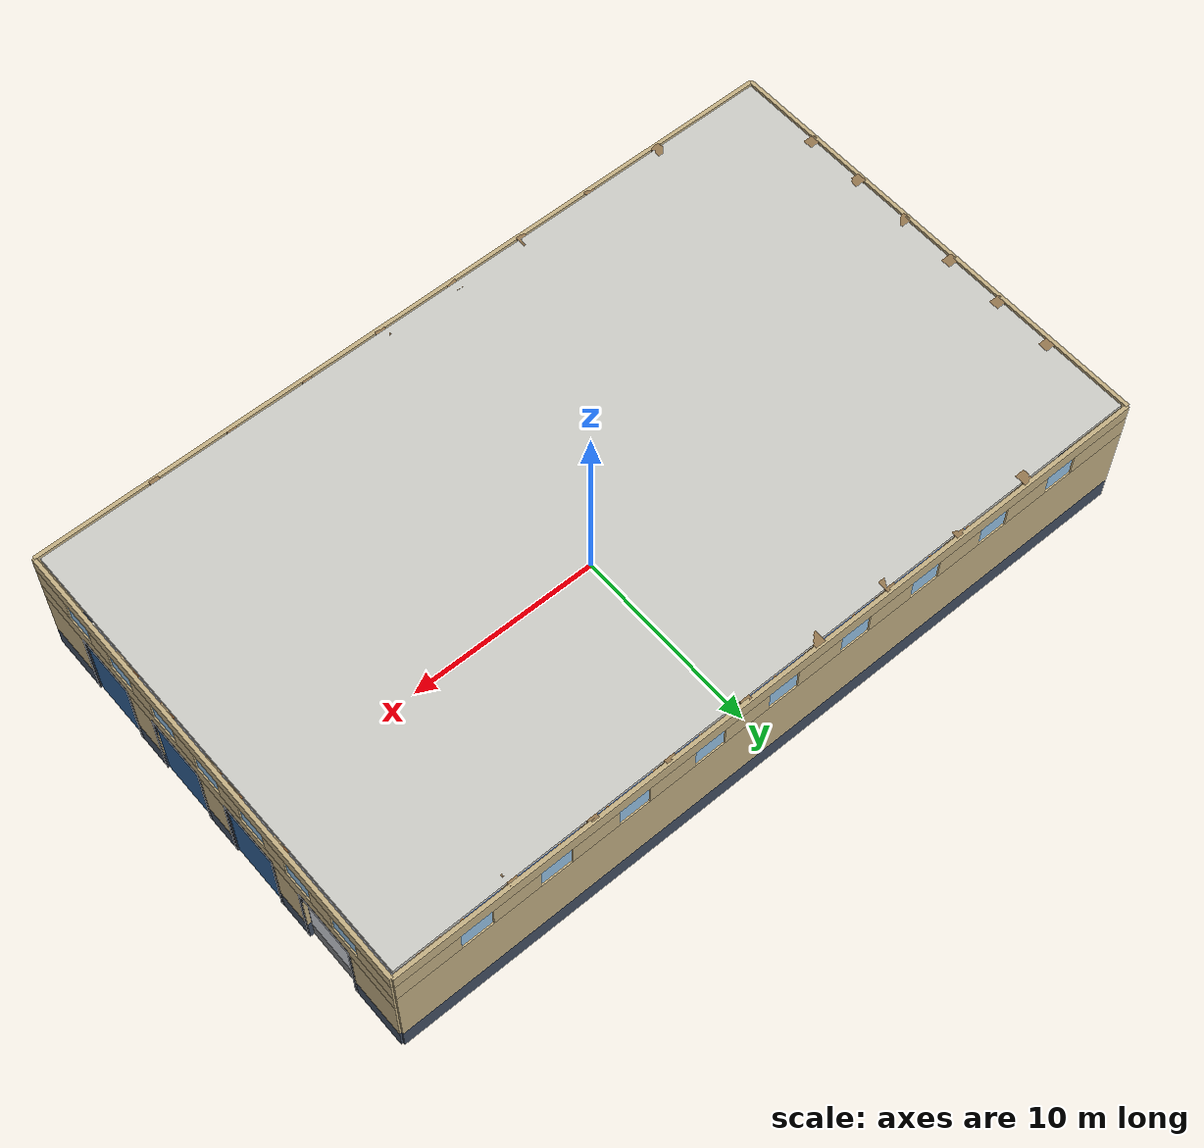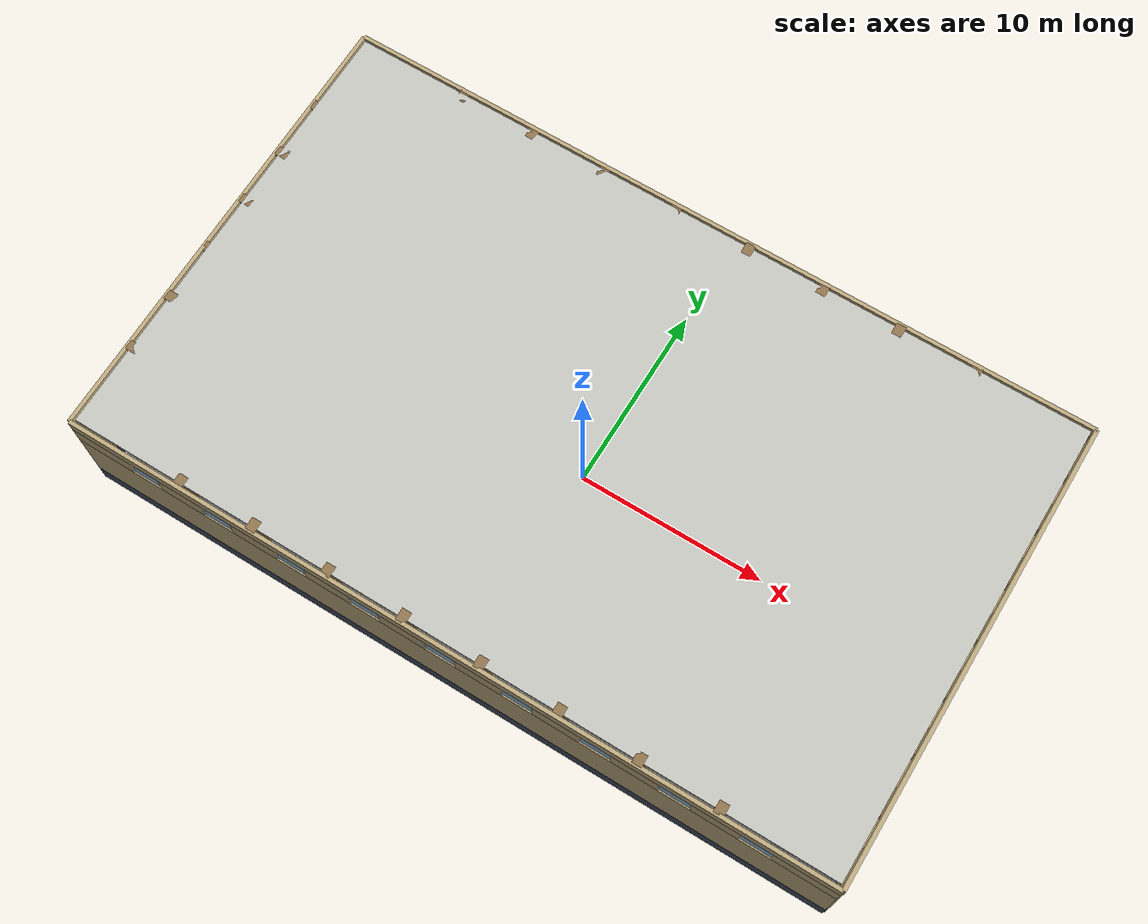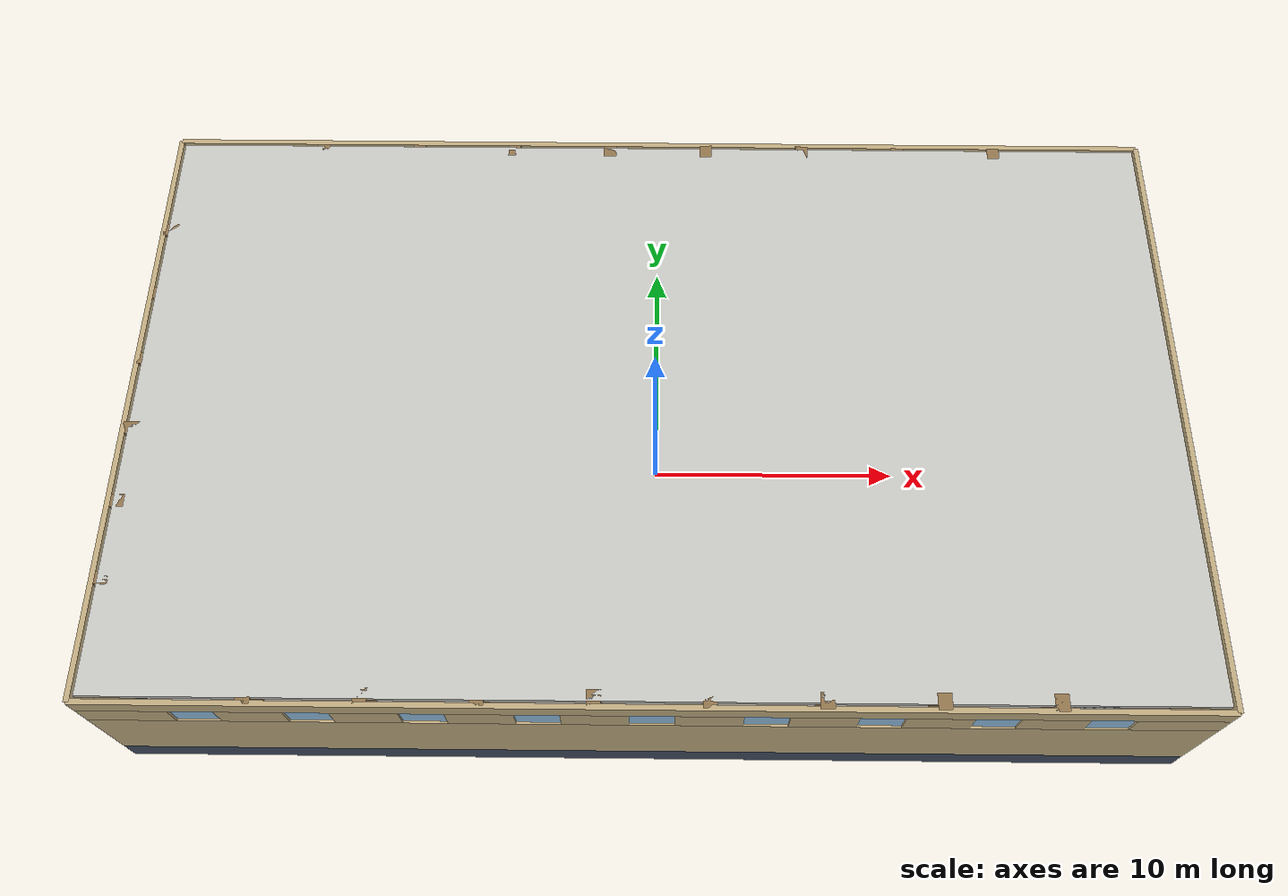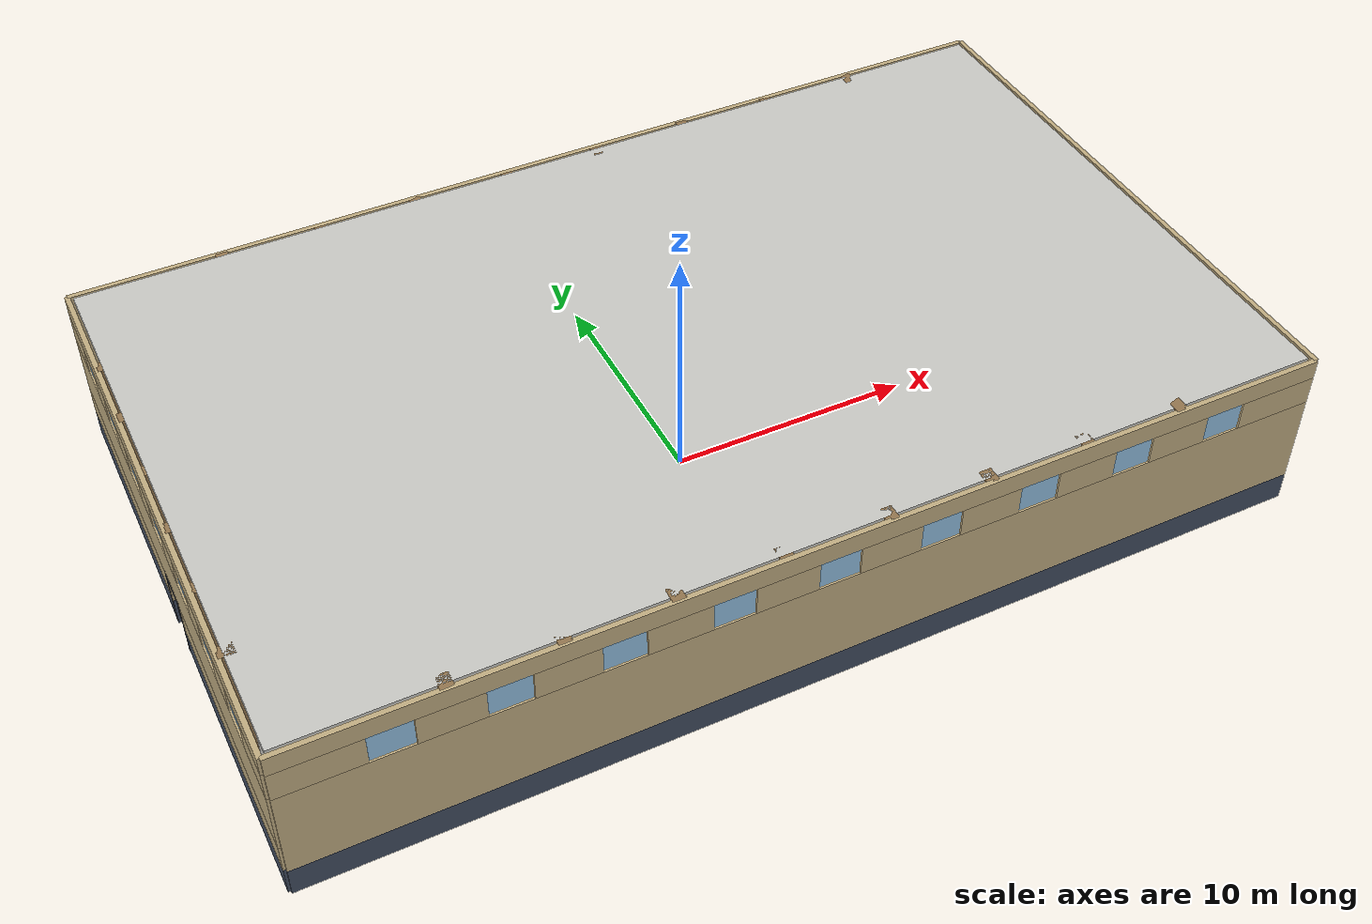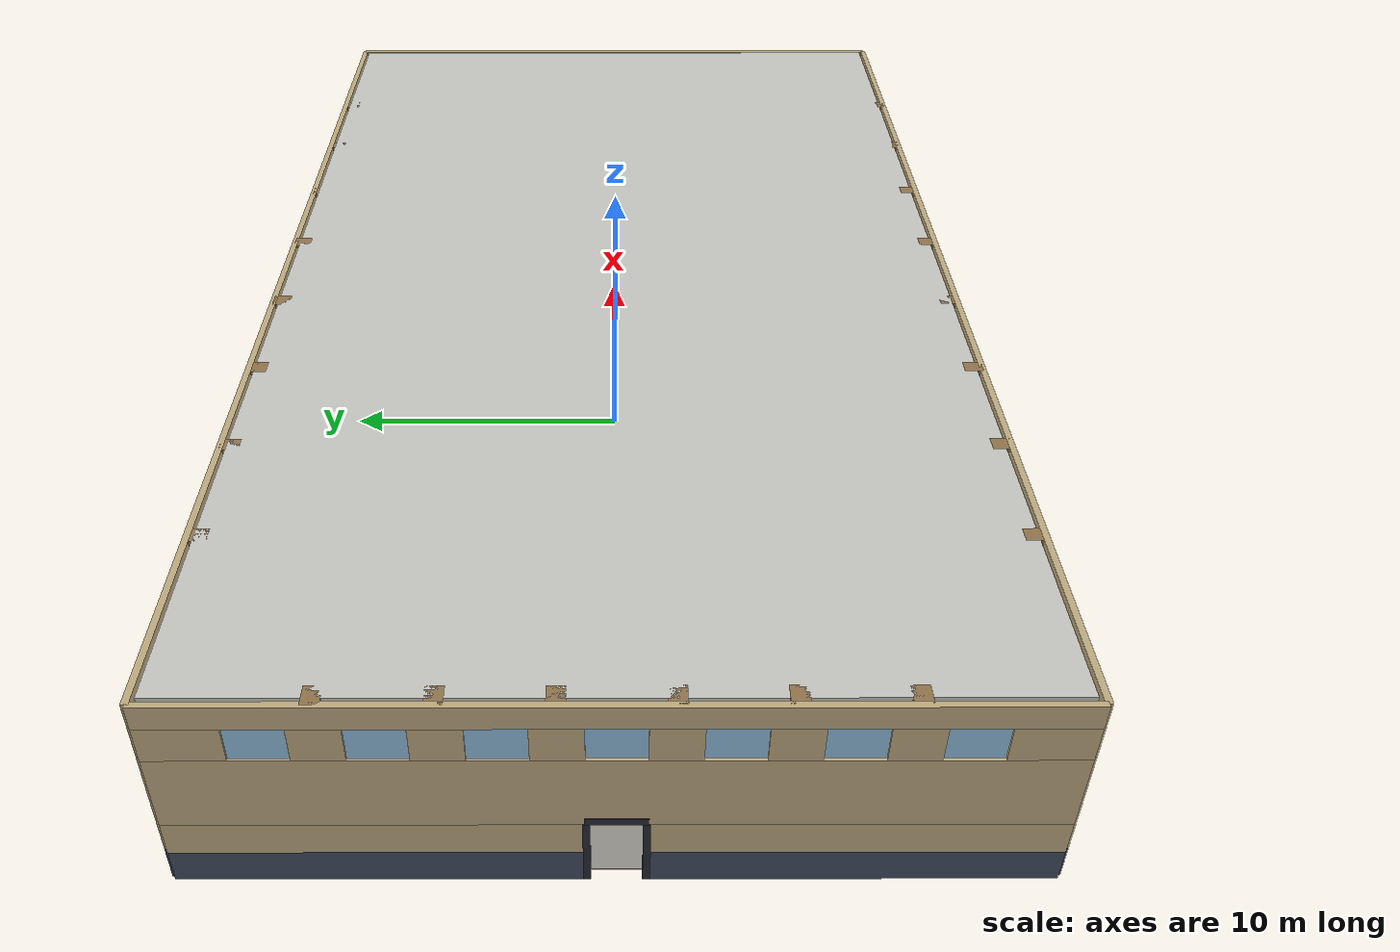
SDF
<sdf version="1.7">
 <world name="default">
  <plugin name="mrs_gazebo_static_transform_republisher_plugin" filename="libMrsGazeboCommonResources_StaticTransformRepublisher.so"/>
  <spherical_coordinates>
   <surface_model>EARTH_WGS84</surface_model>
   <latitude_deg>47.3977</latitude_deg>
   <longitude_deg>8.54559</longitude_deg>
   <elevation>0</elevation>
   <heading_deg>0</heading_deg>
  </spherical_coordinates>
  <physics name="default_physics" default="0" type="ode">
   <ode>
    <solver>
     <type>quick</type>
     <iters>10</iters>
     <sor>1.3</sor>
     <use_dynamic_moi_rescaling>0</use_dynamic_moi_rescaling>
    </solver>
    <constraints>
     <cfm>0</cfm>
     <erp>0.2</erp>
     <contact_max_correcting_vel>1000</contact_max_correcting_vel>
     <contact_surface_layer>0.001</contact_surface_layer>
    </constraints>
   </ode>
   <max_step_size>0.004</max_step_size>
   <real_time_factor>1</real_time_factor>
   <real_time_update_rate>250</real_time_update_rate>
  </physics>
  <scene><shadows>0</shadows><ambient>0.4 0.4 0.4 1</ambient><background>0.7 0.7 0.7 1</background></scene>
  <light name="sun" type="directional">
   <pose>0 0 1000 0.4 0.2 0</pose>
   <diffuse>1 1 1 1</diffuse>
   <specular>0.6 0.6 0.6 1</specular>
   <direction>0.1 0.1 -0.9</direction>
   <attenuation>
    <range>20</range>
    <constant>0.5</constant>
    <linear>0.01</linear>
    <quadratic>0.001</quadratic>
   </attenuation>
   <spot><inner_angle>0</inner_angle><outer_angle>0</outer_angle><falloff>0</falloff></spot>
  </light>
  <model name="the_void">
   <static>1</static>
   <link name="link">
    <pose>0 0 0.1 0 -0 0</pose>
    <visual name="the_void">
     <pose>0 0 2 0 -0 0</pose>
     <geometry><sphere><radius>0.25</radius></sphere></geometry>
     <material>
      <script><uri>file://media/materials/scripts/Gazebo.material</uri><name>Gazebo/Black</name></script>
     </material>
    </visual>
   </link>
   <pose>-1000 -1000 0 0 -0 0</pose>
  </model>
  <plugin name="mrs_gazebo_rviz_cam_synchronizer" filename="libMrsGazeboCommonResources_RvizCameraSynchronizer.so">
   <target_frame_id>gazebo_user_camera</target_frame_id>
   <world_origin_frame_id>uav1/gps_origin</world_origin_frame_id>
   <frame_to_follow>uav1</frame_to_follow>
  </plugin>
  <gravity>0 0 -9.8066</gravity>
  <magnetic_field>6e-06 2.3e-05 -4.2e-05</magnetic_field>
  <atmosphere type="adiabatic"/>
  <model name="warehouse_shell">
   <static>1</static>
   <link name="wEbase0">
    <pose>20 -10.5 0.6 0 0 0</pose>
    <collision name="c"><geometry><box><size>0.2 3 1.2</size></box></geometry></collision>
    <visual name="v">
     <geometry><box><size>0.2 3 1.2</size></box></geometry>
     <material>
      <ambient>0.259 0.306 0.384 1</ambient>
      <diffuse>0.259 0.306 0.384 1</diffuse>
      <specular>0.1 0.1 0.1 1</specular>
     </material>
    </visual>
   </link>
   <link name="wEbase1">
    <pose>20 -5 0.6 0 0 0</pose>
    <collision name="c"><geometry><box><size>0.2 2 1.2</size></box></geometry></collision>
    <visual name="v">
     <geometry><box><size>0.2 2 1.2</size></box></geometry>
     <material>
      <ambient>0.259 0.306 0.384 1</ambient>
      <diffuse>0.259 0.306 0.384 1</diffuse>
      <specular>0.1 0.1 0.1 1</specular>
     </material>
    </visual>
   </link>
   <link name="wEbase2">
    <pose>20 0 0.6 0 0 0</pose>
    <collision name="c"><geometry><box><size>0.2 2 1.2</size></box></geometry></collision>
    <visual name="v">
     <geometry><box><size>0.2 2 1.2</size></box></geometry>
     <material>
      <ambient>0.259 0.306 0.384 1</ambient>
      <diffuse>0.259 0.306 0.384 1</diffuse>
      <specular>0.1 0.1 0.1 1</specular>
     </material>
    </visual>
   </link>
   <link name="wEbase3">
    <pose>20 5 0.6 0 0 0</pose>
    <collision name="c"><geometry><box><size>0.2 2 1.2</size></box></geometry></collision>
    <visual name="v">
     <geometry><box><size>0.2 2 1.2</size></box></geometry>
     <material>
      <ambient>0.259 0.306 0.384 1</ambient>
      <diffuse>0.259 0.306 0.384 1</diffuse>
      <specular>0.1 0.1 0.1 1</specular>
     </material>
    </visual>
   </link>
   <link name="wEbase4">
    <pose>20 10.5 0.6 0 0 0</pose>
    <collision name="c"><geometry><box><size>0.2 3 1.2</size></box></geometry></collision>
    <visual name="v">
     <geometry><box><size>0.2 3 1.2</size></box></geometry>
     <material>
      <ambient>0.259 0.306 0.384 1</ambient>
      <diffuse>0.259 0.306 0.384 1</diffuse>
      <specular>0.1 0.1 0.1 1</specular>
     </material>
    </visual>
   </link>
   <link name="wElo0">
    <pose>20 -10.5 2.6 0 0 0</pose>
    <collision name="c"><geometry><box><size>0.2 3 2.8</size></box></geometry></collision>
    <visual name="v">
     <geometry><box><size>0.2 3 2.8</size></box></geometry>
     <material>
      <ambient>0.769 0.690 0.518 1</ambient>
      <diffuse>0.769 0.690 0.518 1</diffuse>
      <specular>0.1 0.1 0.1 1</specular>
     </material>
    </visual>
   </link>
   <link name="wElo1">
    <pose>20 -5 2.6 0 0 0</pose>
    <collision name="c"><geometry><box><size>0.2 2 2.8</size></box></geometry></collision>
    <visual name="v">
     <geometry><box><size>0.2 2 2.8</size></box></geometry>
     <material>
      <ambient>0.769 0.690 0.518 1</ambient>
      <diffuse>0.769 0.690 0.518 1</diffuse>
      <specular>0.1 0.1 0.1 1</specular>
     </material>
    </visual>
   </link>
   <link name="wElo2">
    <pose>20 0 2.6 0 0 0</pose>
    <collision name="c"><geometry><box><size>0.2 2 2.8</size></box></geometry></collision>
    <visual name="v">
     <geometry><box><size>0.2 2 2.8</size></box></geometry>
     <material>
      <ambient>0.769 0.690 0.518 1</ambient>
      <diffuse>0.769 0.690 0.518 1</diffuse>
      <specular>0.1 0.1 0.1 1</specular>
     </material>
    </visual>
   </link>
   <link name="wElo3">
    <pose>20 5 2.6 0 0 0</pose>
    <collision name="c"><geometry><box><size>0.2 2 2.8</size></box></geometry></collision>
    <visual name="v">
     <geometry><box><size>0.2 2 2.8</size></box></geometry>
     <material>
      <ambient>0.769 0.690 0.518 1</ambient>
      <diffuse>0.769 0.690 0.518 1</diffuse>
      <specular>0.1 0.1 0.1 1</specular>
     </material>
    </visual>
   </link>
   <link name="wElo4">
    <pose>20 10.5 2.6 0 0 0</pose>
    <collision name="c"><geometry><box><size>0.2 3 2.8</size></box></geometry></collision>
    <visual name="v">
     <geometry><box><size>0.2 3 2.8</size></box></geometry>
     <material>
      <ambient>0.769 0.690 0.518 1</ambient>
      <diffuse>0.769 0.690 0.518 1</diffuse>
      <specular>0.1 0.1 0.1 1</specular>
     </material>
    </visual>
   </link>
   <link name="wEmid0">
    <pose>20 0 4.5 0 0 0</pose>
    <collision name="c"><geometry><box><size>0.2 24 1</size></box></geometry></collision>
    <visual name="v">
     <geometry><box><size>0.2 24 1</size></box></geometry>
     <material>
      <ambient>0.769 0.690 0.518 1</ambient>
      <diffuse>0.769 0.690 0.518 1</diffuse>
      <specular>0.1 0.1 0.1 1</specular>
     </material>
    </visual>
   </link>
   <link name="wEmul0">
    <pose>20 -10.9 5.6 0 0 0</pose>
    <collision name="c"><geometry><box><size>0.2 2.2 1.2</size></box></geometry></collision>
    <visual name="v">
     <geometry><box><size>0.2 2.2 1.2</size></box></geometry>
     <material>
      <ambient>0.769 0.690 0.518 1</ambient>
      <diffuse>0.769 0.690 0.518 1</diffuse>
      <specular>0.1 0.1 0.1 1</specular>
     </material>
    </visual>
   </link>
   <link name="wEmul1">
    <pose>20 -7.5 5.6 0 0 0</pose>
    <collision name="c"><geometry><box><size>0.2 1.4 1.2</size></box></geometry></collision>
    <visual name="v">
     <geometry><box><size>0.2 1.4 1.2</size></box></geometry>
     <material>
      <ambient>0.769 0.690 0.518 1</ambient>
      <diffuse>0.769 0.690 0.518 1</diffuse>
      <specular>0.1 0.1 0.1 1</specular>
     </material>
    </visual>
   </link>
   <link name="wEmul2">
    <pose>20 -4.5 5.6 0 0 0</pose>
    <collision name="c"><geometry><box><size>0.2 1.4 1.2</size></box></geometry></collision>
    <visual name="v">
     <geometry><box><size>0.2 1.4 1.2</size></box></geometry>
     <material>
      <ambient>0.769 0.690 0.518 1</ambient>
      <diffuse>0.769 0.690 0.518 1</diffuse>
      <specular>0.1 0.1 0.1 1</specular>
     </material>
    </visual>
   </link>
   <link name="wEmul3">
    <pose>20 -1.5 5.6 0 0 0</pose>
    <collision name="c"><geometry><box><size>0.2 1.4 1.2</size></box></geometry></collision>
    <visual name="v">
     <geometry><box><size>0.2 1.4 1.2</size></box></geometry>
     <material>
      <ambient>0.769 0.690 0.518 1</ambient>
      <diffuse>0.769 0.690 0.518 1</diffuse>
      <specular>0.1 0.1 0.1 1</specular>
     </material>
    </visual>
   </link>
   <link name="wEmul4">
    <pose>20 1.5 5.6 0 0 0</pose>
    <collision name="c"><geometry><box><size>0.2 1.4 1.2</size></box></geometry></collision>
    <visual name="v">
     <geometry><box><size>0.2 1.4 1.2</size></box></geometry>
     <material>
      <ambient>0.769 0.690 0.518 1</ambient>
      <diffuse>0.769 0.690 0.518 1</diffuse>
      <specular>0.1 0.1 0.1 1</specular>
     </material>
    </visual>
   </link>
   <link name="wEmul5">
    <pose>20 4.5 5.6 0 0 0</pose>
    <collision name="c"><geometry><box><size>0.2 1.4 1.2</size></box></geometry></collision>
    <visual name="v">
     <geometry><box><size>0.2 1.4 1.2</size></box></geometry>
     <material>
      <ambient>0.769 0.690 0.518 1</ambient>
      <diffuse>0.769 0.690 0.518 1</diffuse>
      <specular>0.1 0.1 0.1 1</specular>
     </material>
    </visual>
   </link>
   <link name="wEmul6">
    <pose>20 7.5 5.6 0 0 0</pose>
    <collision name="c"><geometry><box><size>0.2 1.4 1.2</size></box></geometry></collision>
    <visual name="v">
     <geometry><box><size>0.2 1.4 1.2</size></box></geometry>
     <material>
      <ambient>0.769 0.690 0.518 1</ambient>
      <diffuse>0.769 0.690 0.518 1</diffuse>
      <specular>0.1 0.1 0.1 1</specular>
     </material>
    </visual>
   </link>
   <link name="wEmul7">
    <pose>20 10.9 5.6 0 0 0</pose>
    <collision name="c"><geometry><box><size>0.2 2.2 1.2</size></box></geometry></collision>
    <visual name="v">
     <geometry><box><size>0.2 2.2 1.2</size></box></geometry>
     <material>
      <ambient>0.769 0.690 0.518 1</ambient>
      <diffuse>0.769 0.690 0.518 1</diffuse>
      <specular>0.1 0.1 0.1 1</specular>
     </material>
    </visual>
   </link>
   <link name="wEtop0">
    <pose>20 0 6.6 0 0 0</pose>
    <collision name="c"><geometry><box><size>0.2 24 0.8</size></box></geometry></collision>
    <visual name="v">
     <geometry><box><size>0.2 24 0.8</size></box></geometry>
     <material>
      <ambient>0.769 0.690 0.518 1</ambient>
      <diffuse>0.769 0.690 0.518 1</diffuse>
      <specular>0.1 0.1 0.1 1</specular>
     </material>
    </visual>
   </link>
   <link name="wEg-9">
    <pose>20 -9 5.6 0 0 0</pose>
    <collision name="c"><geometry><box><size>0.05 1.6 1.2</size></box></geometry></collision>
    <visual name="v">
     <geometry><box><size>0.05 1.6 1.2</size></box></geometry>
     <material>
      <ambient>0.588 0.769 0.910 1</ambient>
      <diffuse>0.588 0.769 0.910 1</diffuse>
      <specular>0.1 0.1 0.1 1</specular>
     </material>
    </visual>
   </link>
   <link name="wEg-6">
    <pose>20 -6 5.6 0 0 0</pose>
    <collision name="c"><geometry><box><size>0.05 1.6 1.2</size></box></geometry></collision>
    <visual name="v">
     <geometry><box><size>0.05 1.6 1.2</size></box></geometry>
     <material>
      <ambient>0.588 0.769 0.910 1</ambient>
      <diffuse>0.588 0.769 0.910 1</diffuse>
      <specular>0.1 0.1 0.1 1</specular>
     </material>
    </visual>
   </link>
   <link name="wEg-3">
    <pose>20 -3 5.6 0 0 0</pose>
    <collision name="c"><geometry><box><size>0.05 1.6 1.2</size></box></geometry></collision>
    <visual name="v">
     <geometry><box><size>0.05 1.6 1.2</size></box></geometry>
     <material>
      <ambient>0.588 0.769 0.910 1</ambient>
      <diffuse>0.588 0.769 0.910 1</diffuse>
      <specular>0.1 0.1 0.1 1</specular>
     </material>
    </visual>
   </link>
   <link name="wEg0">
    <pose>20 0 5.6 0 0 0</pose>
    <collision name="c"><geometry><box><size>0.05 1.6 1.2</size></box></geometry></collision>
    <visual name="v">
     <geometry><box><size>0.05 1.6 1.2</size></box></geometry>
     <material>
      <ambient>0.588 0.769 0.910 1</ambient>
      <diffuse>0.588 0.769 0.910 1</diffuse>
      <specular>0.1 0.1 0.1 1</specular>
     </material>
    </visual>
   </link>
   <link name="wEg3">
    <pose>20 3 5.6 0 0 0</pose>
    <collision name="c"><geometry><box><size>0.05 1.6 1.2</size></box></geometry></collision>
    <visual name="v">
     <geometry><box><size>0.05 1.6 1.2</size></box></geometry>
     <material>
      <ambient>0.588 0.769 0.910 1</ambient>
      <diffuse>0.588 0.769 0.910 1</diffuse>
      <specular>0.1 0.1 0.1 1</specular>
     </material>
    </visual>
   </link>
   <link name="wEg6">
    <pose>20 6 5.6 0 0 0</pose>
    <collision name="c"><geometry><box><size>0.05 1.6 1.2</size></box></geometry></collision>
    <visual name="v">
     <geometry><box><size>0.05 1.6 1.2</size></box></geometry>
     <material>
      <ambient>0.588 0.769 0.910 1</ambient>
      <diffuse>0.588 0.769 0.910 1</diffuse>
      <specular>0.1 0.1 0.1 1</specular>
     </material>
    </visual>
   </link>
   <link name="wEg9">
    <pose>20 9 5.6 0 0 0</pose>
    <collision name="c"><geometry><box><size>0.05 1.6 1.2</size></box></geometry></collision>
    <visual name="v">
     <geometry><box><size>0.05 1.6 1.2</size></box></geometry>
     <material>
      <ambient>0.588 0.769 0.910 1</ambient>
      <diffuse>0.588 0.769 0.910 1</diffuse>
      <specular>0.1 0.1 0.1 1</specular>
     </material>
    </visual>
   </link>
   <link name="dfE-8lt">
    <pose>20 -7.5 4.12 0 0 0</pose>
    <collision name="c"><geometry><box><size>0.22 3.3 0.24</size></box></geometry></collision>
    <visual name="v">
     <geometry><box><size>0.22 3.3 0.24</size></box></geometry>
     <material>
      <ambient>0.157 0.173 0.204 1</ambient>
      <diffuse>0.157 0.173 0.204 1</diffuse>
      <specular>0.1 0.1 0.1 1</specular>
     </material>
    </visual>
   </link>
   <link name="dfE-8j-1">
    <pose>20 -9.1 2 0 0 0</pose>
    <collision name="c"><geometry><box><size>0.22 0.2 4</size></box></geometry></collision>
    <visual name="v">
     <geometry><box><size>0.22 0.2 4</size></box></geometry>
     <material>
      <ambient>0.157 0.173 0.204 1</ambient>
      <diffuse>0.157 0.173 0.204 1</diffuse>
      <specular>0.1 0.1 0.1 1</specular>
     </material>
    </visual>
   </link>
   <link name="dfE-8j1">
    <pose>20 -5.9 2 0 0 0</pose>
    <collision name="c"><geometry><box><size>0.22 0.2 4</size></box></geometry></collision>
    <visual name="v">
     <geometry><box><size>0.22 0.2 4</size></box></geometry>
     <material>
      <ambient>0.157 0.173 0.204 1</ambient>
      <diffuse>0.157 0.173 0.204 1</diffuse>
      <specular>0.1 0.1 0.1 1</specular>
     </material>
    </visual>
   </link>
   <link name="doorE-8">
    <pose>19.98 -7.5 2 0 0 0</pose>
    <collision name="c"><geometry><box><size>0.1 3 4</size></box></geometry></collision>
    <visual name="v">
     <geometry><box><size>0.1 3 4</size></box></geometry>
     <material>
      <ambient>0.180 0.376 0.588 1</ambient>
      <diffuse>0.180 0.376 0.588 1</diffuse>
      <specular>0.1 0.1 0.1 1</specular>
     </material>
    </visual>
   </link>
   <link name="dfE-2lt">
    <pose>20 -2.5 4.12 0 0 0</pose>
    <collision name="c"><geometry><box><size>0.22 3.3 0.24</size></box></geometry></collision>
    <visual name="v">
     <geometry><box><size>0.22 3.3 0.24</size></box></geometry>
     <material>
      <ambient>0.157 0.173 0.204 1</ambient>
      <diffuse>0.157 0.173 0.204 1</diffuse>
      <specular>0.1 0.1 0.1 1</specular>
     </material>
    </visual>
   </link>
   <link name="dfE-2j-1">
    <pose>20 -4.1 2 0 0 0</pose>
    <collision name="c"><geometry><box><size>0.22 0.2 4</size></box></geometry></collision>
    <visual name="v">
     <geometry><box><size>0.22 0.2 4</size></box></geometry>
     <material>
      <ambient>0.157 0.173 0.204 1</ambient>
      <diffuse>0.157 0.173 0.204 1</diffuse>
      <specular>0.1 0.1 0.1 1</specular>
     </material>
    </visual>
   </link>
   <link name="dfE-2j1">
    <pose>20 -0.9 2 0 0 0</pose>
    <collision name="c"><geometry><box><size>0.22 0.2 4</size></box></geometry></collision>
    <visual name="v">
     <geometry><box><size>0.22 0.2 4</size></box></geometry>
     <material>
      <ambient>0.157 0.173 0.204 1</ambient>
      <diffuse>0.157 0.173 0.204 1</diffuse>
      <specular>0.1 0.1 0.1 1</specular>
     </material>
    </visual>
   </link>
   <link name="doorE-2">
    <pose>19.98 -2.5 2 0 0 0</pose>
    <collision name="c"><geometry><box><size>0.1 3 4</size></box></geometry></collision>
    <visual name="v">
     <geometry><box><size>0.1 3 4</size></box></geometry>
     <material>
      <ambient>0.180 0.376 0.588 1</ambient>
      <diffuse>0.180 0.376 0.588 1</diffuse>
      <specular>0.1 0.1 0.1 1</specular>
     </material>
    </visual>
   </link>
   <link name="dfE2lt">
    <pose>20 2.5 4.12 0 0 0</pose>
    <collision name="c"><geometry><box><size>0.22 3.3 0.24</size></box></geometry></collision>
    <visual name="v">
     <geometry><box><size>0.22 3.3 0.24</size></box></geometry>
     <material>
      <ambient>0.157 0.173 0.204 1</ambient>
      <diffuse>0.157 0.173 0.204 1</diffuse>
      <specular>0.1 0.1 0.1 1</specular>
     </material>
    </visual>
   </link>
   <link name="dfE2j-1">
    <pose>20 0.9 2 0 0 0</pose>
    <collision name="c"><geometry><box><size>0.22 0.2 4</size></box></geometry></collision>
    <visual name="v">
     <geometry><box><size>0.22 0.2 4</size></box></geometry>
     <material>
      <ambient>0.157 0.173 0.204 1</ambient>
      <diffuse>0.157 0.173 0.204 1</diffuse>
      <specular>0.1 0.1 0.1 1</specular>
     </material>
    </visual>
   </link>
   <link name="dfE2j1">
    <pose>20 4.1 2 0 0 0</pose>
    <collision name="c"><geometry><box><size>0.22 0.2 4</size></box></geometry></collision>
    <visual name="v">
     <geometry><box><size>0.22 0.2 4</size></box></geometry>
     <material>
      <ambient>0.157 0.173 0.204 1</ambient>
      <diffuse>0.157 0.173 0.204 1</diffuse>
      <specular>0.1 0.1 0.1 1</specular>
     </material>
    </visual>
   </link>
   <link name="doorE2">
    <pose>19.98 2.5 2 0 0 0</pose>
    <collision name="c"><geometry><box><size>0.1 3 4</size></box></geometry></collision>
    <visual name="v">
     <geometry><box><size>0.1 3 4</size></box></geometry>
     <material>
      <ambient>0.180 0.376 0.588 1</ambient>
      <diffuse>0.180 0.376 0.588 1</diffuse>
      <specular>0.1 0.1 0.1 1</specular>
     </material>
    </visual>
   </link>
   <link name="dfE8lt">
    <pose>20 7.5 4.12 0 0 0</pose>
    <collision name="c"><geometry><box><size>0.22 3.3 0.24</size></box></geometry></collision>
    <visual name="v">
     <geometry><box><size>0.22 3.3 0.24</size></box></geometry>
     <material>
      <ambient>0.157 0.173 0.204 1</ambient>
      <diffuse>0.157 0.173 0.204 1</diffuse>
      <specular>0.1 0.1 0.1 1</specular>
     </material>
    </visual>
   </link>
   <link name="dfE8j-1">
    <pose>20 5.9 2 0 0 0</pose>
    <collision name="c"><geometry><box><size>0.22 0.2 4</size></box></geometry></collision>
    <visual name="v">
     <geometry><box><size>0.22 0.2 4</size></box></geometry>
     <material>
      <ambient>0.157 0.173 0.204 1</ambient>
      <diffuse>0.157 0.173 0.204 1</diffuse>
      <specular>0.1 0.1 0.1 1</specular>
     </material>
    </visual>
   </link>
   <link name="dfE8j1">
    <pose>20 9.1 2 0 0 0</pose>
    <collision name="c"><geometry><box><size>0.22 0.2 4</size></box></geometry></collision>
    <visual name="v">
     <geometry><box><size>0.22 0.2 4</size></box></geometry>
     <material>
      <ambient>0.157 0.173 0.204 1</ambient>
      <diffuse>0.157 0.173 0.204 1</diffuse>
      <specular>0.1 0.1 0.1 1</specular>
     </material>
    </visual>
   </link>
   <link name="wWbase0">
    <pose>-20 -6.35 0.6 0 0 0</pose>
    <collision name="c"><geometry><box><size>0.2 11.3 1.2</size></box></geometry></collision>
    <visual name="v">
     <geometry><box><size>0.2 11.3 1.2</size></box></geometry>
     <material>
      <ambient>0.259 0.306 0.384 1</ambient>
      <diffuse>0.259 0.306 0.384 1</diffuse>
      <specular>0.1 0.1 0.1 1</specular>
     </material>
    </visual>
   </link>
   <link name="wWbase1">
    <pose>-20 6.35 0.6 0 0 0</pose>
    <collision name="c"><geometry><box><size>0.2 11.3 1.2</size></box></geometry></collision>
    <visual name="v">
     <geometry><box><size>0.2 11.3 1.2</size></box></geometry>
     <material>
      <ambient>0.259 0.306 0.384 1</ambient>
      <diffuse>0.259 0.306 0.384 1</diffuse>
      <specular>0.1 0.1 0.1 1</specular>
     </material>
    </visual>
   </link>
   <link name="wWlo0">
    <pose>-20 -6.35 1.8 0 0 0</pose>
    <collision name="c"><geometry><box><size>0.2 11.3 1.2</size></box></geometry></collision>
    <visual name="v">
     <geometry><box><size>0.2 11.3 1.2</size></box></geometry>
     <material>
      <ambient>0.769 0.690 0.518 1</ambient>
      <diffuse>0.769 0.690 0.518 1</diffuse>
      <specular>0.1 0.1 0.1 1</specular>
     </material>
    </visual>
   </link>
   <link name="wWlo1">
    <pose>-20 6.35 1.8 0 0 0</pose>
    <collision name="c"><geometry><box><size>0.2 11.3 1.2</size></box></geometry></collision>
    <visual name="v">
     <geometry><box><size>0.2 11.3 1.2</size></box></geometry>
     <material>
      <ambient>0.769 0.690 0.518 1</ambient>
      <diffuse>0.769 0.690 0.518 1</diffuse>
      <specular>0.1 0.1 0.1 1</specular>
     </material>
    </visual>
   </link>
   <link name="wWmid0">
    <pose>-20 0 3.7 0 0 0</pose>
    <collision name="c"><geometry><box><size>0.2 24 2.6</size></box></geometry></collision>
    <visual name="v">
     <geometry><box><size>0.2 24 2.6</size></box></geometry>
     <material>
      <ambient>0.769 0.690 0.518 1</ambient>
      <diffuse>0.769 0.690 0.518 1</diffuse>
      <specular>0.1 0.1 0.1 1</specular>
     </material>
    </visual>
   </link>
   <link name="wWmul0">
    <pose>-20 -10.9 5.6 0 0 0</pose>
    <collision name="c"><geometry><box><size>0.2 2.2 1.2</size></box></geometry></collision>
    <visual name="v">
     <geometry><box><size>0.2 2.2 1.2</size></box></geometry>
     <material>
      <ambient>0.769 0.690 0.518 1</ambient>
      <diffuse>0.769 0.690 0.518 1</diffuse>
      <specular>0.1 0.1 0.1 1</specular>
     </material>
    </visual>
   </link>
   <link name="wWmul1">
    <pose>-20 -7.5 5.6 0 0 0</pose>
    <collision name="c"><geometry><box><size>0.2 1.4 1.2</size></box></geometry></collision>
    <visual name="v">
     <geometry><box><size>0.2 1.4 1.2</size></box></geometry>
     <material>
      <ambient>0.769 0.690 0.518 1</ambient>
      <diffuse>0.769 0.690 0.518 1</diffuse>
      <specular>0.1 0.1 0.1 1</specular>
     </material>
    </visual>
   </link>
   <link name="wWmul2">
    <pose>-20 -4.5 5.6 0 0 0</pose>
    <collision name="c"><geometry><box><size>0.2 1.4 1.2</size></box></geometry></collision>
    <visual name="v">
     <geometry><box><size>0.2 1.4 1.2</size></box></geometry>
     <material>
      <ambient>0.769 0.690 0.518 1</ambient>
      <diffuse>0.769 0.690 0.518 1</diffuse>
      <specular>0.1 0.1 0.1 1</specular>
     </material>
    </visual>
   </link>
   <link name="wWmul3">
    <pose>-20 -1.5 5.6 0 0 0</pose>
    <collision name="c"><geometry><box><size>0.2 1.4 1.2</size></box></geometry></collision>
    <visual name="v">
     <geometry><box><size>0.2 1.4 1.2</size></box></geometry>
     <material>
      <ambient>0.769 0.690 0.518 1</ambient>
      <diffuse>0.769 0.690 0.518 1</diffuse>
      <specular>0.1 0.1 0.1 1</specular>
     </material>
    </visual>
   </link>
   <link name="wWmul4">
    <pose>-20 1.5 5.6 0 0 0</pose>
    <collision name="c"><geometry><box><size>0.2 1.4 1.2</size></box></geometry></collision>
    <visual name="v">
     <geometry><box><size>0.2 1.4 1.2</size></box></geometry>
     <material>
      <ambient>0.769 0.690 0.518 1</ambient>
      <diffuse>0.769 0.690 0.518 1</diffuse>
      <specular>0.1 0.1 0.1 1</specular>
     </material>
    </visual>
   </link>
   <link name="wWmul5">
    <pose>-20 4.5 5.6 0 0 0</pose>
    <collision name="c"><geometry><box><size>0.2 1.4 1.2</size></box></geometry></collision>
    <visual name="v">
     <geometry><box><size>0.2 1.4 1.2</size></box></geometry>
     <material>
      <ambient>0.769 0.690 0.518 1</ambient>
      <diffuse>0.769 0.690 0.518 1</diffuse>
      <specular>0.1 0.1 0.1 1</specular>
     </material>
    </visual>
   </link>
   <link name="wWmul6">
    <pose>-20 7.5 5.6 0 0 0</pose>
    <collision name="c"><geometry><box><size>0.2 1.4 1.2</size></box></geometry></collision>
    <visual name="v">
     <geometry><box><size>0.2 1.4 1.2</size></box></geometry>
     <material>
      <ambient>0.769 0.690 0.518 1</ambient>
      <diffuse>0.769 0.690 0.518 1</diffuse>
      <specular>0.1 0.1 0.1 1</specular>
     </material>
    </visual>
   </link>
   <link name="wWmul7">
    <pose>-20 10.9 5.6 0 0 0</pose>
    <collision name="c"><geometry><box><size>0.2 2.2 1.2</size></box></geometry></collision>
    <visual name="v">
     <geometry><box><size>0.2 2.2 1.2</size></box></geometry>
     <material>
      <ambient>0.769 0.690 0.518 1</ambient>
      <diffuse>0.769 0.690 0.518 1</diffuse>
      <specular>0.1 0.1 0.1 1</specular>
     </material>
    </visual>
   </link>
   <link name="wWtop0">
    <pose>-20 0 6.6 0 0 0</pose>
    <collision name="c"><geometry><box><size>0.2 24 0.8</size></box></geometry></collision>
    <visual name="v">
     <geometry><box><size>0.2 24 0.8</size></box></geometry>
     <material>
      <ambient>0.769 0.690 0.518 1</ambient>
      <diffuse>0.769 0.690 0.518 1</diffuse>
      <specular>0.1 0.1 0.1 1</specular>
     </material>
    </visual>
   </link>
   <link name="wWg-9">
    <pose>-20 -9 5.6 0 0 0</pose>
    <collision name="c"><geometry><box><size>0.05 1.6 1.2</size></box></geometry></collision>
    <visual name="v">
     <geometry><box><size>0.05 1.6 1.2</size></box></geometry>
     <material>
      <ambient>0.588 0.769 0.910 1</ambient>
      <diffuse>0.588 0.769 0.910 1</diffuse>
      <specular>0.1 0.1 0.1 1</specular>
     </material>
    </visual>
   </link>
   <link name="wWg-6">
    <pose>-20 -6 5.6 0 0 0</pose>
    <collision name="c"><geometry><box><size>0.05 1.6 1.2</size></box></geometry></collision>
    <visual name="v">
     <geometry><box><size>0.05 1.6 1.2</size></box></geometry>
     <material>
      <ambient>0.588 0.769 0.910 1</ambient>
      <diffuse>0.588 0.769 0.910 1</diffuse>
      <specular>0.1 0.1 0.1 1</specular>
     </material>
    </visual>
   </link>
   <link name="wWg-3">
    <pose>-20 -3 5.6 0 0 0</pose>
    <collision name="c"><geometry><box><size>0.05 1.6 1.2</size></box></geometry></collision>
    <visual name="v">
     <geometry><box><size>0.05 1.6 1.2</size></box></geometry>
     <material>
      <ambient>0.588 0.769 0.910 1</ambient>
      <diffuse>0.588 0.769 0.910 1</diffuse>
      <specular>0.1 0.1 0.1 1</specular>
     </material>
    </visual>
   </link>
   <link name="wWg0">
    <pose>-20 0 5.6 0 0 0</pose>
    <collision name="c"><geometry><box><size>0.05 1.6 1.2</size></box></geometry></collision>
    <visual name="v">
     <geometry><box><size>0.05 1.6 1.2</size></box></geometry>
     <material>
      <ambient>0.588 0.769 0.910 1</ambient>
      <diffuse>0.588 0.769 0.910 1</diffuse>
      <specular>0.1 0.1 0.1 1</specular>
     </material>
    </visual>
   </link>
   <link name="wWg3">
    <pose>-20 3 5.6 0 0 0</pose>
    <collision name="c"><geometry><box><size>0.05 1.6 1.2</size></box></geometry></collision>
    <visual name="v">
     <geometry><box><size>0.05 1.6 1.2</size></box></geometry>
     <material>
      <ambient>0.588 0.769 0.910 1</ambient>
      <diffuse>0.588 0.769 0.910 1</diffuse>
      <specular>0.1 0.1 0.1 1</specular>
     </material>
    </visual>
   </link>
   <link name="wWg6">
    <pose>-20 6 5.6 0 0 0</pose>
    <collision name="c"><geometry><box><size>0.05 1.6 1.2</size></box></geometry></collision>
    <visual name="v">
     <geometry><box><size>0.05 1.6 1.2</size></box></geometry>
     <material>
      <ambient>0.588 0.769 0.910 1</ambient>
      <diffuse>0.588 0.769 0.910 1</diffuse>
      <specular>0.1 0.1 0.1 1</specular>
     </material>
    </visual>
   </link>
   <link name="wWg9">
    <pose>-20 9 5.6 0 0 0</pose>
    <collision name="c"><geometry><box><size>0.05 1.6 1.2</size></box></geometry></collision>
    <visual name="v">
     <geometry><box><size>0.05 1.6 1.2</size></box></geometry>
     <material>
      <ambient>0.588 0.769 0.910 1</ambient>
      <diffuse>0.588 0.769 0.910 1</diffuse>
      <specular>0.1 0.1 0.1 1</specular>
     </material>
    </visual>
   </link>
   <link name="dfWlt">
    <pose>-20 0 2.52 0 0 0</pose>
    <collision name="c"><geometry><box><size>0.22 1.7 0.24</size></box></geometry></collision>
    <visual name="v">
     <geometry><box><size>0.22 1.7 0.24</size></box></geometry>
     <material>
      <ambient>0.157 0.173 0.204 1</ambient>
      <diffuse>0.157 0.173 0.204 1</diffuse>
      <specular>0.1 0.1 0.1 1</specular>
     </material>
    </visual>
   </link>
   <link name="dfWj-1">
    <pose>-20 -0.8 1.2 0 0 0</pose>
    <collision name="c"><geometry><box><size>0.22 0.2 2.4</size></box></geometry></collision>
    <visual name="v">
     <geometry><box><size>0.22 0.2 2.4</size></box></geometry>
     <material>
      <ambient>0.157 0.173 0.204 1</ambient>
      <diffuse>0.157 0.173 0.204 1</diffuse>
      <specular>0.1 0.1 0.1 1</specular>
     </material>
    </visual>
   </link>
   <link name="dfWj1">
    <pose>-20 0.8 1.2 0 0 0</pose>
    <collision name="c"><geometry><box><size>0.22 0.2 2.4</size></box></geometry></collision>
    <visual name="v">
     <geometry><box><size>0.22 0.2 2.4</size></box></geometry>
     <material>
      <ambient>0.157 0.173 0.204 1</ambient>
      <diffuse>0.157 0.173 0.204 1</diffuse>
      <specular>0.1 0.1 0.1 1</specular>
     </material>
    </visual>
   </link>
   <link name="wWpil-75">
    <pose>-19.7 -7.5 3.5 0 0 0</pose>
    <collision name="c"><geometry><box><size>0.6 0.5 7</size></box></geometry></collision>
    <visual name="v">
     <geometry><box><size>0.6 0.5 7</size></box></geometry>
     <material>
      <ambient>0.588 0.471 0.314 1</ambient>
      <diffuse>0.588 0.471 0.314 1</diffuse>
      <specular>0.1 0.1 0.1 1</specular>
     </material>
    </visual>
   </link>
   <link name="wWpil-45">
    <pose>-19.7 -4.5 3.5 0 0 0</pose>
    <collision name="c"><geometry><box><size>0.6 0.5 7</size></box></geometry></collision>
    <visual name="v">
     <geometry><box><size>0.6 0.5 7</size></box></geometry>
     <material>
      <ambient>0.588 0.471 0.314 1</ambient>
      <diffuse>0.588 0.471 0.314 1</diffuse>
      <specular>0.1 0.1 0.1 1</specular>
     </material>
    </visual>
   </link>
   <link name="wWpil-15">
    <pose>-19.7 -1.5 3.5 0 0 0</pose>
    <collision name="c"><geometry><box><size>0.6 0.5 7</size></box></geometry></collision>
    <visual name="v">
     <geometry><box><size>0.6 0.5 7</size></box></geometry>
     <material>
      <ambient>0.588 0.471 0.314 1</ambient>
      <diffuse>0.588 0.471 0.314 1</diffuse>
      <specular>0.1 0.1 0.1 1</specular>
     </material>
    </visual>
   </link>
   <link name="wWpil15">
    <pose>-19.7 1.5 3.5 0 0 0</pose>
    <collision name="c"><geometry><box><size>0.6 0.5 7</size></box></geometry></collision>
    <visual name="v">
     <geometry><box><size>0.6 0.5 7</size></box></geometry>
     <material>
      <ambient>0.588 0.471 0.314 1</ambient>
      <diffuse>0.588 0.471 0.314 1</diffuse>
      <specular>0.1 0.1 0.1 1</specular>
     </material>
    </visual>
   </link>
   <link name="wWpil45">
    <pose>-19.7 4.5 3.5 0 0 0</pose>
    <collision name="c"><geometry><box><size>0.6 0.5 7</size></box></geometry></collision>
    <visual name="v">
     <geometry><box><size>0.6 0.5 7</size></box></geometry>
     <material>
      <ambient>0.588 0.471 0.314 1</ambient>
      <diffuse>0.588 0.471 0.314 1</diffuse>
      <specular>0.1 0.1 0.1 1</specular>
     </material>
    </visual>
   </link>
   <link name="wWpil75">
    <pose>-19.7 7.5 3.5 0 0 0</pose>
    <collision name="c"><geometry><box><size>0.6 0.5 7</size></box></geometry></collision>
    <visual name="v">
     <geometry><box><size>0.6 0.5 7</size></box></geometry>
     <material>
      <ambient>0.588 0.471 0.314 1</ambient>
      <diffuse>0.588 0.471 0.314 1</diffuse>
      <specular>0.1 0.1 0.1 1</specular>
     </material>
    </visual>
   </link>
   <link name="wNbase0">
    <pose>0 12 0.6 0 0 0</pose>
    <collision name="c"><geometry><box><size>40 0.2 1.2</size></box></geometry></collision>
    <visual name="v">
     <geometry><box><size>40 0.2 1.2</size></box></geometry>
     <material>
      <ambient>0.259 0.306 0.384 1</ambient>
      <diffuse>0.259 0.306 0.384 1</diffuse>
      <specular>0.1 0.1 0.1 1</specular>
     </material>
    </visual>
   </link>
   <link name="wNsid0">
    <pose>0 12 3.1 0 0 0</pose>
    <collision name="c"><geometry><box><size>40 0.2 3.8</size></box></geometry></collision>
    <visual name="v">
     <geometry><box><size>40 0.2 3.8</size></box></geometry>
     <material>
      <ambient>0.769 0.690 0.518 1</ambient>
      <diffuse>0.769 0.690 0.518 1</diffuse>
      <specular>0.1 0.1 0.1 1</specular>
     </material>
    </visual>
   </link>
   <link name="wNmul0">
    <pose>-18.4 12 5.6 0 0 0</pose>
    <collision name="c"><geometry><box><size>3.2 0.2 1.2</size></box></geometry></collision>
    <visual name="v">
     <geometry><box><size>3.2 0.2 1.2</size></box></geometry>
     <material>
      <ambient>0.769 0.690 0.518 1</ambient>
      <diffuse>0.769 0.690 0.518 1</diffuse>
      <specular>0.1 0.1 0.1 1</specular>
     </material>
    </visual>
   </link>
   <link name="wNmul1">
    <pose>-14 12 5.6 0 0 0</pose>
    <collision name="c"><geometry><box><size>2.4 0.2 1.2</size></box></geometry></collision>
    <visual name="v">
     <geometry><box><size>2.4 0.2 1.2</size></box></geometry>
     <material>
      <ambient>0.769 0.690 0.518 1</ambient>
      <diffuse>0.769 0.690 0.518 1</diffuse>
      <specular>0.1 0.1 0.1 1</specular>
     </material>
    </visual>
   </link>
   <link name="wNmul2">
    <pose>-10 12 5.6 0 0 0</pose>
    <collision name="c"><geometry><box><size>2.4 0.2 1.2</size></box></geometry></collision>
    <visual name="v">
     <geometry><box><size>2.4 0.2 1.2</size></box></geometry>
     <material>
      <ambient>0.769 0.690 0.518 1</ambient>
      <diffuse>0.769 0.690 0.518 1</diffuse>
      <specular>0.1 0.1 0.1 1</specular>
     </material>
    </visual>
   </link>
   <link name="wNmul3">
    <pose>-6 12 5.6 0 0 0</pose>
    <collision name="c"><geometry><box><size>2.4 0.2 1.2</size></box></geometry></collision>
    <visual name="v">
     <geometry><box><size>2.4 0.2 1.2</size></box></geometry>
     <material>
      <ambient>0.769 0.690 0.518 1</ambient>
      <diffuse>0.769 0.690 0.518 1</diffuse>
      <specular>0.1 0.1 0.1 1</specular>
     </material>
    </visual>
   </link>
   <link name="wNmul4">
    <pose>-2 12 5.6 0 0 0</pose>
    <collision name="c"><geometry><box><size>2.4 0.2 1.2</size></box></geometry></collision>
    <visual name="v">
     <geometry><box><size>2.4 0.2 1.2</size></box></geometry>
     <material>
      <ambient>0.769 0.690 0.518 1</ambient>
      <diffuse>0.769 0.690 0.518 1</diffuse>
      <specular>0.1 0.1 0.1 1</specular>
     </material>
    </visual>
   </link>
   <link name="wNmul5">
    <pose>2 12 5.6 0 0 0</pose>
    <collision name="c"><geometry><box><size>2.4 0.2 1.2</size></box></geometry></collision>
    <visual name="v">
     <geometry><box><size>2.4 0.2 1.2</size></box></geometry>
     <material>
      <ambient>0.769 0.690 0.518 1</ambient>
      <diffuse>0.769 0.690 0.518 1</diffuse>
      <specular>0.1 0.1 0.1 1</specular>
     </material>
    </visual>
   </link>
   <link name="wNmul6">
    <pose>6 12 5.6 0 0 0</pose>
    <collision name="c"><geometry><box><size>2.4 0.2 1.2</size></box></geometry></collision>
    <visual name="v">
     <geometry><box><size>2.4 0.2 1.2</size></box></geometry>
     <material>
      <ambient>0.769 0.690 0.518 1</ambient>
      <diffuse>0.769 0.690 0.518 1</diffuse>
      <specular>0.1 0.1 0.1 1</specular>
     </material>
    </visual>
   </link>
   <link name="wNmul7">
    <pose>10 12 5.6 0 0 0</pose>
    <collision name="c"><geometry><box><size>2.4 0.2 1.2</size></box></geometry></collision>
    <visual name="v">
     <geometry><box><size>2.4 0.2 1.2</size></box></geometry>
     <material>
      <ambient>0.769 0.690 0.518 1</ambient>
      <diffuse>0.769 0.690 0.518 1</diffuse>
      <specular>0.1 0.1 0.1 1</specular>
     </material>
    </visual>
   </link>
   <link name="wNmul8">
    <pose>14 12 5.6 0 0 0</pose>
    <collision name="c"><geometry><box><size>2.4 0.2 1.2</size></box></geometry></collision>
    <visual name="v">
     <geometry><box><size>2.4 0.2 1.2</size></box></geometry>
     <material>
      <ambient>0.769 0.690 0.518 1</ambient>
      <diffuse>0.769 0.690 0.518 1</diffuse>
      <specular>0.1 0.1 0.1 1</specular>
     </material>
    </visual>
   </link>
   <link name="wNmul9">
    <pose>18.4 12 5.6 0 0 0</pose>
    <collision name="c"><geometry><box><size>3.2 0.2 1.2</size></box></geometry></collision>
    <visual name="v">
     <geometry><box><size>3.2 0.2 1.2</size></box></geometry>
     <material>
      <ambient>0.769 0.690 0.518 1</ambient>
      <diffuse>0.769 0.690 0.518 1</diffuse>
      <specular>0.1 0.1 0.1 1</specular>
     </material>
    </visual>
   </link>
   <link name="wNtop0">
    <pose>0 12 6.6 0 0 0</pose>
    <collision name="c"><geometry><box><size>40 0.2 0.8</size></box></geometry></collision>
    <visual name="v">
     <geometry><box><size>40 0.2 0.8</size></box></geometry>
     <material>
      <ambient>0.769 0.690 0.518 1</ambient>
      <diffuse>0.769 0.690 0.518 1</diffuse>
      <specular>0.1 0.1 0.1 1</specular>
     </material>
    </visual>
   </link>
   <link name="wNg-16">
    <pose>-16 12 5.6 0 0 0</pose>
    <collision name="c"><geometry><box><size>1.6 0.05 1.2</size></box></geometry></collision>
    <visual name="v">
     <geometry><box><size>1.6 0.05 1.2</size></box></geometry>
     <material>
      <ambient>0.588 0.769 0.910 1</ambient>
      <diffuse>0.588 0.769 0.910 1</diffuse>
      <specular>0.1 0.1 0.1 1</specular>
     </material>
    </visual>
   </link>
   <link name="wNg-12">
    <pose>-12 12 5.6 0 0 0</pose>
    <collision name="c"><geometry><box><size>1.6 0.05 1.2</size></box></geometry></collision>
    <visual name="v">
     <geometry><box><size>1.6 0.05 1.2</size></box></geometry>
     <material>
      <ambient>0.588 0.769 0.910 1</ambient>
      <diffuse>0.588 0.769 0.910 1</diffuse>
      <specular>0.1 0.1 0.1 1</specular>
     </material>
    </visual>
   </link>
   <link name="wNg-8">
    <pose>-8 12 5.6 0 0 0</pose>
    <collision name="c"><geometry><box><size>1.6 0.05 1.2</size></box></geometry></collision>
    <visual name="v">
     <geometry><box><size>1.6 0.05 1.2</size></box></geometry>
     <material>
      <ambient>0.588 0.769 0.910 1</ambient>
      <diffuse>0.588 0.769 0.910 1</diffuse>
      <specular>0.1 0.1 0.1 1</specular>
     </material>
    </visual>
   </link>
   <link name="wNg-4">
    <pose>-4 12 5.6 0 0 0</pose>
    <collision name="c"><geometry><box><size>1.6 0.05 1.2</size></box></geometry></collision>
    <visual name="v">
     <geometry><box><size>1.6 0.05 1.2</size></box></geometry>
     <material>
      <ambient>0.588 0.769 0.910 1</ambient>
      <diffuse>0.588 0.769 0.910 1</diffuse>
      <specular>0.1 0.1 0.1 1</specular>
     </material>
    </visual>
   </link>
   <link name="wNg0">
    <pose>0 12 5.6 0 0 0</pose>
    <collision name="c"><geometry><box><size>1.6 0.05 1.2</size></box></geometry></collision>
    <visual name="v">
     <geometry><box><size>1.6 0.05 1.2</size></box></geometry>
     <material>
      <ambient>0.588 0.769 0.910 1</ambient>
      <diffuse>0.588 0.769 0.910 1</diffuse>
      <specular>0.1 0.1 0.1 1</specular>
     </material>
    </visual>
   </link>
   <link name="wNg4">
    <pose>4 12 5.6 0 0 0</pose>
    <collision name="c"><geometry><box><size>1.6 0.05 1.2</size></box></geometry></collision>
    <visual name="v">
     <geometry><box><size>1.6 0.05 1.2</size></box></geometry>
     <material>
      <ambient>0.588 0.769 0.910 1</ambient>
      <diffuse>0.588 0.769 0.910 1</diffuse>
      <specular>0.1 0.1 0.1 1</specular>
     </material>
    </visual>
   </link>
   <link name="wNg8">
    <pose>8 12 5.6 0 0 0</pose>
    <collision name="c"><geometry><box><size>1.6 0.05 1.2</size></box></geometry></collision>
    <visual name="v">
     <geometry><box><size>1.6 0.05 1.2</size></box></geometry>
     <material>
      <ambient>0.588 0.769 0.910 1</ambient>
      <diffuse>0.588 0.769 0.910 1</diffuse>
      <specular>0.1 0.1 0.1 1</specular>
     </material>
    </visual>
   </link>
   <link name="wNg12">
    <pose>12 12 5.6 0 0 0</pose>
    <collision name="c"><geometry><box><size>1.6 0.05 1.2</size></box></geometry></collision>
    <visual name="v">
     <geometry><box><size>1.6 0.05 1.2</size></box></geometry>
     <material>
      <ambient>0.588 0.769 0.910 1</ambient>
      <diffuse>0.588 0.769 0.910 1</diffuse>
      <specular>0.1 0.1 0.1 1</specular>
     </material>
    </visual>
   </link>
   <link name="wNg16">
    <pose>16 12 5.6 0 0 0</pose>
    <collision name="c"><geometry><box><size>1.6 0.05 1.2</size></box></geometry></collision>
    <visual name="v">
     <geometry><box><size>1.6 0.05 1.2</size></box></geometry>
     <material>
      <ambient>0.588 0.769 0.910 1</ambient>
      <diffuse>0.588 0.769 0.910 1</diffuse>
      <specular>0.1 0.1 0.1 1</specular>
     </material>
    </visual>
   </link>
   <link name="wNpil-14">
    <pose>-14 11.7 3.5 0 0 0</pose>
    <collision name="c"><geometry><box><size>0.5 0.6 7</size></box></geometry></collision>
    <visual name="v">
     <geometry><box><size>0.5 0.6 7</size></box></geometry>
     <material>
      <ambient>0.588 0.471 0.314 1</ambient>
      <diffuse>0.588 0.471 0.314 1</diffuse>
      <specular>0.1 0.1 0.1 1</specular>
     </material>
    </visual>
   </link>
   <link name="wNpil-10">
    <pose>-10 11.7 3.5 0 0 0</pose>
    <collision name="c"><geometry><box><size>0.5 0.6 7</size></box></geometry></collision>
    <visual name="v">
     <geometry><box><size>0.5 0.6 7</size></box></geometry>
     <material>
      <ambient>0.588 0.471 0.314 1</ambient>
      <diffuse>0.588 0.471 0.314 1</diffuse>
      <specular>0.1 0.1 0.1 1</specular>
     </material>
    </visual>
   </link>
   <link name="wNpil-6">
    <pose>-6 11.7 3.5 0 0 0</pose>
    <collision name="c"><geometry><box><size>0.5 0.6 7</size></box></geometry></collision>
    <visual name="v">
     <geometry><box><size>0.5 0.6 7</size></box></geometry>
     <material>
      <ambient>0.588 0.471 0.314 1</ambient>
      <diffuse>0.588 0.471 0.314 1</diffuse>
      <specular>0.1 0.1 0.1 1</specular>
     </material>
    </visual>
   </link>
   <link name="wNpil-2">
    <pose>-2 11.7 3.5 0 0 0</pose>
    <collision name="c"><geometry><box><size>0.5 0.6 7</size></box></geometry></collision>
    <visual name="v">
     <geometry><box><size>0.5 0.6 7</size></box></geometry>
     <material>
      <ambient>0.588 0.471 0.314 1</ambient>
      <diffuse>0.588 0.471 0.314 1</diffuse>
      <specular>0.1 0.1 0.1 1</specular>
     </material>
    </visual>
   </link>
   <link name="wNpil2">
    <pose>2 11.7 3.5 0 0 0</pose>
    <collision name="c"><geometry><box><size>0.5 0.6 7</size></box></geometry></collision>
    <visual name="v">
     <geometry><box><size>0.5 0.6 7</size></box></geometry>
     <material>
      <ambient>0.588 0.471 0.314 1</ambient>
      <diffuse>0.588 0.471 0.314 1</diffuse>
      <specular>0.1 0.1 0.1 1</specular>
     </material>
    </visual>
   </link>
   <link name="wNpil6">
    <pose>6 11.7 3.5 0 0 0</pose>
    <collision name="c"><geometry><box><size>0.5 0.6 7</size></box></geometry></collision>
    <visual name="v">
     <geometry><box><size>0.5 0.6 7</size></box></geometry>
     <material>
      <ambient>0.588 0.471 0.314 1</ambient>
      <diffuse>0.588 0.471 0.314 1</diffuse>
      <specular>0.1 0.1 0.1 1</specular>
     </material>
    </visual>
   </link>
   <link name="wNpil10">
    <pose>10 11.7 3.5 0 0 0</pose>
    <collision name="c"><geometry><box><size>0.5 0.6 7</size></box></geometry></collision>
    <visual name="v">
     <geometry><box><size>0.5 0.6 7</size></box></geometry>
     <material>
      <ambient>0.588 0.471 0.314 1</ambient>
      <diffuse>0.588 0.471 0.314 1</diffuse>
      <specular>0.1 0.1 0.1 1</specular>
     </material>
    </visual>
   </link>
   <link name="wNpil14">
    <pose>14 11.7 3.5 0 0 0</pose>
    <collision name="c"><geometry><box><size>0.5 0.6 7</size></box></geometry></collision>
    <visual name="v">
     <geometry><box><size>0.5 0.6 7</size></box></geometry>
     <material>
      <ambient>0.588 0.471 0.314 1</ambient>
      <diffuse>0.588 0.471 0.314 1</diffuse>
      <specular>0.1 0.1 0.1 1</specular>
     </material>
    </visual>
   </link>
   <link name="wSbase0">
    <pose>0 -12 0.6 0 0 0</pose>
    <collision name="c"><geometry><box><size>40 0.2 1.2</size></box></geometry></collision>
    <visual name="v">
     <geometry><box><size>40 0.2 1.2</size></box></geometry>
     <material>
      <ambient>0.259 0.306 0.384 1</ambient>
      <diffuse>0.259 0.306 0.384 1</diffuse>
      <specular>0.1 0.1 0.1 1</specular>
     </material>
    </visual>
   </link>
   <link name="wSsid0">
    <pose>0 -12 3.1 0 0 0</pose>
    <collision name="c"><geometry><box><size>40 0.2 3.8</size></box></geometry></collision>
    <visual name="v">
     <geometry><box><size>40 0.2 3.8</size></box></geometry>
     <material>
      <ambient>0.769 0.690 0.518 1</ambient>
      <diffuse>0.769 0.690 0.518 1</diffuse>
      <specular>0.1 0.1 0.1 1</specular>
     </material>
    </visual>
   </link>
   <link name="wSmul0">
    <pose>-18.4 -12 5.6 0 0 0</pose>
    <collision name="c"><geometry><box><size>3.2 0.2 1.2</size></box></geometry></collision>
    <visual name="v">
     <geometry><box><size>3.2 0.2 1.2</size></box></geometry>
     <material>
      <ambient>0.769 0.690 0.518 1</ambient>
      <diffuse>0.769 0.690 0.518 1</diffuse>
      <specular>0.1 0.1 0.1 1</specular>
     </material>
    </visual>
   </link>
   <link name="wSmul1">
    <pose>-14 -12 5.6 0 0 0</pose>
    <collision name="c"><geometry><box><size>2.4 0.2 1.2</size></box></geometry></collision>
    <visual name="v">
     <geometry><box><size>2.4 0.2 1.2</size></box></geometry>
     <material>
      <ambient>0.769 0.690 0.518 1</ambient>
      <diffuse>0.769 0.690 0.518 1</diffuse>
      <specular>0.1 0.1 0.1 1</specular>
     </material>
    </visual>
   </link>
   <link name="wSmul2">
    <pose>-10 -12 5.6 0 0 0</pose>
    <collision name="c"><geometry><box><size>2.4 0.2 1.2</size></box></geometry></collision>
    <visual name="v">
     <geometry><box><size>2.4 0.2 1.2</size></box></geometry>
     <material>
      <ambient>0.769 0.690 0.518 1</ambient>
      <diffuse>0.769 0.690 0.518 1</diffuse>
      <specular>0.1 0.1 0.1 1</specular>
     </material>
    </visual>
   </link>
   <link name="wSmul3">
    <pose>-6 -12 5.6 0 0 0</pose>
    <collision name="c"><geometry><box><size>2.4 0.2 1.2</size></box></geometry></collision>
    <visual name="v">
     <geometry><box><size>2.4 0.2 1.2</size></box></geometry>
     <material>
      <ambient>0.769 0.690 0.518 1</ambient>
      <diffuse>0.769 0.690 0.518 1</diffuse>
      <specular>0.1 0.1 0.1 1</specular>
     </material>
    </visual>
   </link>
   <link name="wSmul4">
    <pose>-2 -12 5.6 0 0 0</pose>
    <collision name="c"><geometry><box><size>2.4 0.2 1.2</size></box></geometry></collision>
    <visual name="v">
     <geometry><box><size>2.4 0.2 1.2</size></box></geometry>
     <material>
      <ambient>0.769 0.690 0.518 1</ambient>
      <diffuse>0.769 0.690 0.518 1</diffuse>
      <specular>0.1 0.1 0.1 1</specular>
     </material>
    </visual>
   </link>
   <link name="wSmul5">
    <pose>2 -12 5.6 0 0 0</pose>
    <collision name="c"><geometry><box><size>2.4 0.2 1.2</size></box></geometry></collision>
    <visual name="v">
     <geometry><box><size>2.4 0.2 1.2</size></box></geometry>
     <material>
      <ambient>0.769 0.690 0.518 1</ambient>
      <diffuse>0.769 0.690 0.518 1</diffuse>
      <specular>0.1 0.1 0.1 1</specular>
     </material>
    </visual>
   </link>
   <link name="wSmul6">
    <pose>6 -12 5.6 0 0 0</pose>
    <collision name="c"><geometry><box><size>2.4 0.2 1.2</size></box></geometry></collision>
    <visual name="v">
     <geometry><box><size>2.4 0.2 1.2</size></box></geometry>
     <material>
      <ambient>0.769 0.690 0.518 1</ambient>
      <diffuse>0.769 0.690 0.518 1</diffuse>
      <specular>0.1 0.1 0.1 1</specular>
     </material>
    </visual>
   </link>
   <link name="wSmul7">
    <pose>10 -12 5.6 0 0 0</pose>
    <collision name="c"><geometry><box><size>2.4 0.2 1.2</size></box></geometry></collision>
    <visual name="v">
     <geometry><box><size>2.4 0.2 1.2</size></box></geometry>
     <material>
      <ambient>0.769 0.690 0.518 1</ambient>
      <diffuse>0.769 0.690 0.518 1</diffuse>
      <specular>0.1 0.1 0.1 1</specular>
     </material>
    </visual>
   </link>
   <link name="wSmul8">
    <pose>14 -12 5.6 0 0 0</pose>
    <collision name="c"><geometry><box><size>2.4 0.2 1.2</size></box></geometry></collision>
    <visual name="v">
     <geometry><box><size>2.4 0.2 1.2</size></box></geometry>
     <material>
      <ambient>0.769 0.690 0.518 1</ambient>
      <diffuse>0.769 0.690 0.518 1</diffuse>
      <specular>0.1 0.1 0.1 1</specular>
     </material>
    </visual>
   </link>
   <link name="wSmul9">
    <pose>18.4 -12 5.6 0 0 0</pose>
    <collision name="c"><geometry><box><size>3.2 0.2 1.2</size></box></geometry></collision>
    <visual name="v">
     <geometry><box><size>3.2 0.2 1.2</size></box></geometry>
     <material>
      <ambient>0.769 0.690 0.518 1</ambient>
      <diffuse>0.769 0.690 0.518 1</diffuse>
      <specular>0.1 0.1 0.1 1</specular>
     </material>
    </visual>
   </link>
   <link name="wStop0">
    <pose>0 -12 6.6 0 0 0</pose>
    <collision name="c"><geometry><box><size>40 0.2 0.8</size></box></geometry></collision>
    <visual name="v">
     <geometry><box><size>40 0.2 0.8</size></box></geometry>
     <material>
      <ambient>0.769 0.690 0.518 1</ambient>
      <diffuse>0.769 0.690 0.518 1</diffuse>
      <specular>0.1 0.1 0.1 1</specular>
     </material>
    </visual>
   </link>
   <link name="wSg-16">
    <pose>-16 -12 5.6 0 0 0</pose>
    <collision name="c"><geometry><box><size>1.6 0.05 1.2</size></box></geometry></collision>
    <visual name="v">
     <geometry><box><size>1.6 0.05 1.2</size></box></geometry>
     <material>
      <ambient>0.588 0.769 0.910 1</ambient>
      <diffuse>0.588 0.769 0.910 1</diffuse>
      <specular>0.1 0.1 0.1 1</specular>
     </material>
    </visual>
   </link>
   <link name="wSg-12">
    <pose>-12 -12 5.6 0 0 0</pose>
    <collision name="c"><geometry><box><size>1.6 0.05 1.2</size></box></geometry></collision>
    <visual name="v">
     <geometry><box><size>1.6 0.05 1.2</size></box></geometry>
     <material>
      <ambient>0.588 0.769 0.910 1</ambient>
      <diffuse>0.588 0.769 0.910 1</diffuse>
      <specular>0.1 0.1 0.1 1</specular>
     </material>
    </visual>
   </link>
   <link name="wSg-8">
    <pose>-8 -12 5.6 0 0 0</pose>
    <collision name="c"><geometry><box><size>1.6 0.05 1.2</size></box></geometry></collision>
    <visual name="v">
     <geometry><box><size>1.6 0.05 1.2</size></box></geometry>
     <material>
      <ambient>0.588 0.769 0.910 1</ambient>
      <diffuse>0.588 0.769 0.910 1</diffuse>
      <specular>0.1 0.1 0.1 1</specular>
     </material>
    </visual>
   </link>
   <link name="wSg-4">
    <pose>-4 -12 5.6 0 0 0</pose>
    <collision name="c"><geometry><box><size>1.6 0.05 1.2</size></box></geometry></collision>
    <visual name="v">
     <geometry><box><size>1.6 0.05 1.2</size></box></geometry>
     <material>
      <ambient>0.588 0.769 0.910 1</ambient>
      <diffuse>0.588 0.769 0.910 1</diffuse>
      <specular>0.1 0.1 0.1 1</specular>
     </material>
    </visual>
   </link>
   <link name="wSg0">
    <pose>0 -12 5.6 0 0 0</pose>
    <collision name="c"><geometry><box><size>1.6 0.05 1.2</size></box></geometry></collision>
    <visual name="v">
     <geometry><box><size>1.6 0.05 1.2</size></box></geometry>
     <material>
      <ambient>0.588 0.769 0.910 1</ambient>
      <diffuse>0.588 0.769 0.910 1</diffuse>
      <specular>0.1 0.1 0.1 1</specular>
     </material>
    </visual>
   </link>
   <link name="wSg4">
    <pose>4 -12 5.6 0 0 0</pose>
    <collision name="c"><geometry><box><size>1.6 0.05 1.2</size></box></geometry></collision>
    <visual name="v">
     <geometry><box><size>1.6 0.05 1.2</size></box></geometry>
     <material>
      <ambient>0.588 0.769 0.910 1</ambient>
      <diffuse>0.588 0.769 0.910 1</diffuse>
      <specular>0.1 0.1 0.1 1</specular>
     </material>
    </visual>
   </link>
   <link name="wSg8">
    <pose>8 -12 5.6 0 0 0</pose>
    <collision name="c"><geometry><box><size>1.6 0.05 1.2</size></box></geometry></collision>
    <visual name="v">
     <geometry><box><size>1.6 0.05 1.2</size></box></geometry>
     <material>
      <ambient>0.588 0.769 0.910 1</ambient>
      <diffuse>0.588 0.769 0.910 1</diffuse>
      <specular>0.1 0.1 0.1 1</specular>
     </material>
    </visual>
   </link>
   <link name="wSg12">
    <pose>12 -12 5.6 0 0 0</pose>
    <collision name="c"><geometry><box><size>1.6 0.05 1.2</size></box></geometry></collision>
    <visual name="v">
     <geometry><box><size>1.6 0.05 1.2</size></box></geometry>
     <material>
      <ambient>0.588 0.769 0.910 1</ambient>
      <diffuse>0.588 0.769 0.910 1</diffuse>
      <specular>0.1 0.1 0.1 1</specular>
     </material>
    </visual>
   </link>
   <link name="wSg16">
    <pose>16 -12 5.6 0 0 0</pose>
    <collision name="c"><geometry><box><size>1.6 0.05 1.2</size></box></geometry></collision>
    <visual name="v">
     <geometry><box><size>1.6 0.05 1.2</size></box></geometry>
     <material>
      <ambient>0.588 0.769 0.910 1</ambient>
      <diffuse>0.588 0.769 0.910 1</diffuse>
      <specular>0.1 0.1 0.1 1</specular>
     </material>
    </visual>
   </link>
   <link name="wSpil-14">
    <pose>-14 -11.7 3.5 0 0 0</pose>
    <collision name="c"><geometry><box><size>0.5 0.6 7</size></box></geometry></collision>
    <visual name="v">
     <geometry><box><size>0.5 0.6 7</size></box></geometry>
     <material>
      <ambient>0.588 0.471 0.314 1</ambient>
      <diffuse>0.588 0.471 0.314 1</diffuse>
      <specular>0.1 0.1 0.1 1</specular>
     </material>
    </visual>
   </link>
   <link name="wSpil-10">
    <pose>-10 -11.7 3.5 0 0 0</pose>
    <collision name="c"><geometry><box><size>0.5 0.6 7</size></box></geometry></collision>
    <visual name="v">
     <geometry><box><size>0.5 0.6 7</size></box></geometry>
     <material>
      <ambient>0.588 0.471 0.314 1</ambient>
      <diffuse>0.588 0.471 0.314 1</diffuse>
      <specular>0.1 0.1 0.1 1</specular>
     </material>
    </visual>
   </link>
   <link name="wSpil-6">
    <pose>-6 -11.7 3.5 0 0 0</pose>
    <collision name="c"><geometry><box><size>0.5 0.6 7</size></box></geometry></collision>
    <visual name="v">
     <geometry><box><size>0.5 0.6 7</size></box></geometry>
     <material>
      <ambient>0.588 0.471 0.314 1</ambient>
      <diffuse>0.588 0.471 0.314 1</diffuse>
      <specular>0.1 0.1 0.1 1</specular>
     </material>
    </visual>
   </link>
   <link name="wSpil-2">
    <pose>-2 -11.7 3.5 0 0 0</pose>
    <collision name="c"><geometry><box><size>0.5 0.6 7</size></box></geometry></collision>
    <visual name="v">
     <geometry><box><size>0.5 0.6 7</size></box></geometry>
     <material>
      <ambient>0.588 0.471 0.314 1</ambient>
      <diffuse>0.588 0.471 0.314 1</diffuse>
      <specular>0.1 0.1 0.1 1</specular>
     </material>
    </visual>
   </link>
   <link name="wSpil2">
    <pose>2 -11.7 3.5 0 0 0</pose>
    <collision name="c"><geometry><box><size>0.5 0.6 7</size></box></geometry></collision>
    <visual name="v">
     <geometry><box><size>0.5 0.6 7</size></box></geometry>
     <material>
      <ambient>0.588 0.471 0.314 1</ambient>
      <diffuse>0.588 0.471 0.314 1</diffuse>
      <specular>0.1 0.1 0.1 1</specular>
     </material>
    </visual>
   </link>
   <link name="wSpil6">
    <pose>6 -11.7 3.5 0 0 0</pose>
    <collision name="c"><geometry><box><size>0.5 0.6 7</size></box></geometry></collision>
    <visual name="v">
     <geometry><box><size>0.5 0.6 7</size></box></geometry>
     <material>
      <ambient>0.588 0.471 0.314 1</ambient>
      <diffuse>0.588 0.471 0.314 1</diffuse>
      <specular>0.1 0.1 0.1 1</specular>
     </material>
    </visual>
   </link>
   <link name="wSpil10">
    <pose>10 -11.7 3.5 0 0 0</pose>
    <collision name="c"><geometry><box><size>0.5 0.6 7</size></box></geometry></collision>
    <visual name="v">
     <geometry><box><size>0.5 0.6 7</size></box></geometry>
     <material>
      <ambient>0.588 0.471 0.314 1</ambient>
      <diffuse>0.588 0.471 0.314 1</diffuse>
      <specular>0.1 0.1 0.1 1</specular>
     </material>
    </visual>
   </link>
   <link name="wSpil14">
    <pose>14 -11.7 3.5 0 0 0</pose>
    <collision name="c"><geometry><box><size>0.5 0.6 7</size></box></geometry></collision>
    <visual name="v">
     <geometry><box><size>0.5 0.6 7</size></box></geometry>
     <material>
      <ambient>0.588 0.471 0.314 1</ambient>
      <diffuse>0.588 0.471 0.314 1</diffuse>
      <specular>0.1 0.1 0.1 1</specular>
     </material>
    </visual>
   </link>
   <link name="floor">
    <collision name="c"><geometry><box><size>39.6 23.6 0.04</size></box></geometry></collision>
    <visual name="v">
     <geometry><box><size>39.6 23.6 0.04</size></box></geometry>
     <material>
      <ambient>0.588 0.580 0.557 1</ambient>
      <diffuse>0.588 0.580 0.557 1</diffuse>
      <specular>0.1 0.1 0.1 1</specular>
     </material>
    </visual>
   </link>
  </model>
  <model name="warehouse_racks">
   <static>1</static>
   <link name="r00_u0_0">
    <pose>-14 -9.5 1.75 0 0 0</pose>
    <collision name="c"><geometry><box><size>0.12 0.12 3.5</size></box></geometry></collision>
    <visual name="v">
     <geometry><box><size>0.12 0.12 3.5</size></box></geometry>
     <material>
      <ambient>0.910 0.471 0.086 1</ambient>
      <diffuse>0.910 0.471 0.086 1</diffuse>
      <specular>0.1 0.1 0.1 1</specular>
     </material>
    </visual>
   </link>
   <link name="r00_u0_1">
    <pose>-14 -6.5 1.75 0 0 0</pose>
    <collision name="c"><geometry><box><size>0.12 0.12 3.5</size></box></geometry></collision>
    <visual name="v">
     <geometry><box><size>0.12 0.12 3.5</size></box></geometry>
     <material>
      <ambient>0.910 0.471 0.086 1</ambient>
      <diffuse>0.910 0.471 0.086 1</diffuse>
      <specular>0.1 0.1 0.1 1</specular>
     </material>
    </visual>
   </link>
   <link name="r00_u1_0">
    <pose>-11.6667 -9.5 1.75 0 0 0</pose>
    <collision name="c"><geometry><box><size>0.12 0.12 3.5</size></box></geometry></collision>
    <visual name="v">
     <geometry><box><size>0.12 0.12 3.5</size></box></geometry>
     <material>
      <ambient>0.910 0.471 0.086 1</ambient>
      <diffuse>0.910 0.471 0.086 1</diffuse>
      <specular>0.1 0.1 0.1 1</specular>
     </material>
    </visual>
   </link>
   <link name="r00_u1_1">
    <pose>-11.6667 -6.5 1.75 0 0 0</pose>
    <collision name="c"><geometry><box><size>0.12 0.12 3.5</size></box></geometry></collision>
    <visual name="v">
     <geometry><box><size>0.12 0.12 3.5</size></box></geometry>
     <material>
      <ambient>0.910 0.471 0.086 1</ambient>
      <diffuse>0.910 0.471 0.086 1</diffuse>
      <specular>0.1 0.1 0.1 1</specular>
     </material>
    </visual>
   </link>
   <link name="r00_u2_0">
    <pose>-9.33333 -9.5 1.75 0 0 0</pose>
    <collision name="c"><geometry><box><size>0.12 0.12 3.5</size></box></geometry></collision>
    <visual name="v">
     <geometry><box><size>0.12 0.12 3.5</size></box></geometry>
     <material>
      <ambient>0.910 0.471 0.086 1</ambient>
      <diffuse>0.910 0.471 0.086 1</diffuse>
      <specular>0.1 0.1 0.1 1</specular>
     </material>
    </visual>
   </link>
   <link name="r00_u2_1">
    <pose>-9.33333 -6.5 1.75 0 0 0</pose>
    <collision name="c"><geometry><box><size>0.12 0.12 3.5</size></box></geometry></collision>
    <visual name="v">
     <geometry><box><size>0.12 0.12 3.5</size></box></geometry>
     <material>
      <ambient>0.910 0.471 0.086 1</ambient>
      <diffuse>0.910 0.471 0.086 1</diffuse>
      <specular>0.1 0.1 0.1 1</specular>
     </material>
    </visual>
   </link>
   <link name="r00_u3_0">
    <pose>-7 -9.5 1.75 0 0 0</pose>
    <collision name="c"><geometry><box><size>0.12 0.12 3.5</size></box></geometry></collision>
    <visual name="v">
     <geometry><box><size>0.12 0.12 3.5</size></box></geometry>
     <material>
      <ambient>0.910 0.471 0.086 1</ambient>
      <diffuse>0.910 0.471 0.086 1</diffuse>
      <specular>0.1 0.1 0.1 1</specular>
     </material>
    </visual>
   </link>
   <link name="r00_u3_1">
    <pose>-7 -6.5 1.75 0 0 0</pose>
    <collision name="c"><geometry><box><size>0.12 0.12 3.5</size></box></geometry></collision>
    <visual name="v">
     <geometry><box><size>0.12 0.12 3.5</size></box></geometry>
     <material>
      <ambient>0.910 0.471 0.086 1</ambient>
      <diffuse>0.910 0.471 0.086 1</diffuse>
      <specular>0.1 0.1 0.1 1</specular>
     </material>
    </visual>
   </link>
   <link name="r00_u4_0">
    <pose>-4.66667 -9.5 1.75 0 0 0</pose>
    <collision name="c"><geometry><box><size>0.12 0.12 3.5</size></box></geometry></collision>
    <visual name="v">
     <geometry><box><size>0.12 0.12 3.5</size></box></geometry>
     <material>
      <ambient>0.910 0.471 0.086 1</ambient>
      <diffuse>0.910 0.471 0.086 1</diffuse>
      <specular>0.1 0.1 0.1 1</specular>
     </material>
    </visual>
   </link>
   <link name="r00_u4_1">
    <pose>-4.66667 -6.5 1.75 0 0 0</pose>
    <collision name="c"><geometry><box><size>0.12 0.12 3.5</size></box></geometry></collision>
    <visual name="v">
     <geometry><box><size>0.12 0.12 3.5</size></box></geometry>
     <material>
      <ambient>0.910 0.471 0.086 1</ambient>
      <diffuse>0.910 0.471 0.086 1</diffuse>
      <specular>0.1 0.1 0.1 1</specular>
     </material>
    </visual>
   </link>
   <link name="r00_u5_0">
    <pose>-2.33333 -9.5 1.75 0 0 0</pose>
    <collision name="c"><geometry><box><size>0.12 0.12 3.5</size></box></geometry></collision>
    <visual name="v">
     <geometry><box><size>0.12 0.12 3.5</size></box></geometry>
     <material>
      <ambient>0.910 0.471 0.086 1</ambient>
      <diffuse>0.910 0.471 0.086 1</diffuse>
      <specular>0.1 0.1 0.1 1</specular>
     </material>
    </visual>
   </link>
   <link name="r00_u5_1">
    <pose>-2.33333 -6.5 1.75 0 0 0</pose>
    <collision name="c"><geometry><box><size>0.12 0.12 3.5</size></box></geometry></collision>
    <visual name="v">
     <geometry><box><size>0.12 0.12 3.5</size></box></geometry>
     <material>
      <ambient>0.910 0.471 0.086 1</ambient>
      <diffuse>0.910 0.471 0.086 1</diffuse>
      <specular>0.1 0.1 0.1 1</specular>
     </material>
    </visual>
   </link>
   <link name="r00_u6_0">
    <pose>0 -9.5 1.75 0 0 0</pose>
    <collision name="c"><geometry><box><size>0.12 0.12 3.5</size></box></geometry></collision>
    <visual name="v">
     <geometry><box><size>0.12 0.12 3.5</size></box></geometry>
     <material>
      <ambient>0.910 0.471 0.086 1</ambient>
      <diffuse>0.910 0.471 0.086 1</diffuse>
      <specular>0.1 0.1 0.1 1</specular>
     </material>
    </visual>
   </link>
   <link name="r00_u6_1">
    <pose>0 -6.5 1.75 0 0 0</pose>
    <collision name="c"><geometry><box><size>0.12 0.12 3.5</size></box></geometry></collision>
    <visual name="v">
     <geometry><box><size>0.12 0.12 3.5</size></box></geometry>
     <material>
      <ambient>0.910 0.471 0.086 1</ambient>
      <diffuse>0.910 0.471 0.086 1</diffuse>
      <specular>0.1 0.1 0.1 1</specular>
     </material>
    </visual>
   </link>
   <link name="r00_b0_0">
    <pose>-7 -9.5 0.2 0 0 0</pose>
    <collision name="c"><geometry><box><size>14 0.12 0.1</size></box></geometry></collision>
    <visual name="v">
     <geometry><box><size>14 0.12 0.1</size></box></geometry>
     <material>
      <ambient>0.149 0.329 0.659 1</ambient>
      <diffuse>0.149 0.329 0.659 1</diffuse>
      <specular>0.1 0.1 0.1 1</specular>
     </material>
    </visual>
   </link>
   <link name="r00_b0_1">
    <pose>-7 -6.5 0.2 0 0 0</pose>
    <collision name="c"><geometry><box><size>14 0.12 0.1</size></box></geometry></collision>
    <visual name="v">
     <geometry><box><size>14 0.12 0.1</size></box></geometry>
     <material>
      <ambient>0.149 0.329 0.659 1</ambient>
      <diffuse>0.149 0.329 0.659 1</diffuse>
      <specular>0.1 0.1 0.1 1</specular>
     </material>
    </visual>
   </link>
   <link name="r00_b1_0">
    <pose>-7 -9.5 1.45 0 0 0</pose>
    <collision name="c"><geometry><box><size>14 0.12 0.1</size></box></geometry></collision>
    <visual name="v">
     <geometry><box><size>14 0.12 0.1</size></box></geometry>
     <material>
      <ambient>0.149 0.329 0.659 1</ambient>
      <diffuse>0.149 0.329 0.659 1</diffuse>
      <specular>0.1 0.1 0.1 1</specular>
     </material>
    </visual>
   </link>
   <link name="r00_b1_1">
    <pose>-7 -6.5 1.45 0 0 0</pose>
    <collision name="c"><geometry><box><size>14 0.12 0.1</size></box></geometry></collision>
    <visual name="v">
     <geometry><box><size>14 0.12 0.1</size></box></geometry>
     <material>
      <ambient>0.149 0.329 0.659 1</ambient>
      <diffuse>0.149 0.329 0.659 1</diffuse>
      <specular>0.1 0.1 0.1 1</specular>
     </material>
    </visual>
   </link>
   <link name="r00_b2_0">
    <pose>-7 -9.5 2.7 0 0 0</pose>
    <collision name="c"><geometry><box><size>14 0.12 0.1</size></box></geometry></collision>
    <visual name="v">
     <geometry><box><size>14 0.12 0.1</size></box></geometry>
     <material>
      <ambient>0.149 0.329 0.659 1</ambient>
      <diffuse>0.149 0.329 0.659 1</diffuse>
      <specular>0.1 0.1 0.1 1</specular>
     </material>
    </visual>
   </link>
   <link name="r00_b2_1">
    <pose>-7 -6.5 2.7 0 0 0</pose>
    <collision name="c"><geometry><box><size>14 0.12 0.1</size></box></geometry></collision>
    <visual name="v">
     <geometry><box><size>14 0.12 0.1</size></box></geometry>
     <material>
      <ambient>0.149 0.329 0.659 1</ambient>
      <diffuse>0.149 0.329 0.659 1</diffuse>
      <specular>0.1 0.1 0.1 1</specular>
     </material>
    </visual>
   </link>
   <link name="r00_b3_0">
    <pose>-7 -9.5 3.4 0 0 0</pose>
    <collision name="c"><geometry><box><size>14 0.12 0.1</size></box></geometry></collision>
    <visual name="v">
     <geometry><box><size>14 0.12 0.1</size></box></geometry>
     <material>
      <ambient>0.149 0.329 0.659 1</ambient>
      <diffuse>0.149 0.329 0.659 1</diffuse>
      <specular>0.1 0.1 0.1 1</specular>
     </material>
    </visual>
   </link>
   <link name="r00_b3_1">
    <pose>-7 -6.5 3.4 0 0 0</pose>
    <collision name="c"><geometry><box><size>14 0.12 0.1</size></box></geometry></collision>
    <visual name="v">
     <geometry><box><size>14 0.12 0.1</size></box></geometry>
     <material>
      <ambient>0.149 0.329 0.659 1</ambient>
      <diffuse>0.149 0.329 0.659 1</diffuse>
      <specular>0.1 0.1 0.1 1</specular>
     </material>
    </visual>
   </link>
   <link name="r00_d0">
    <pose>-7 -8 0.2 0 0 0</pose>
    <collision name="c"><geometry><box><size>14 3 0.05</size></box></geometry></collision>
    <visual name="v">
     <geometry><box><size>14 3 0.05</size></box></geometry>
     <material>
      <ambient>0.361 0.361 0.384 1</ambient>
      <diffuse>0.361 0.361 0.384 1</diffuse>
      <specular>0.1 0.1 0.1 1</specular>
     </material>
    </visual>
   </link>
   <link name="r00_d1">
    <pose>-7 -8 1.45 0 0 0</pose>
    <collision name="c"><geometry><box><size>14 3 0.05</size></box></geometry></collision>
    <visual name="v">
     <geometry><box><size>14 3 0.05</size></box></geometry>
     <material>
      <ambient>0.361 0.361 0.384 1</ambient>
      <diffuse>0.361 0.361 0.384 1</diffuse>
      <specular>0.1 0.1 0.1 1</specular>
     </material>
    </visual>
   </link>
   <link name="r00_d2">
    <pose>-7 -8 2.7 0 0 0</pose>
    <collision name="c"><geometry><box><size>14 3 0.05</size></box></geometry></collision>
    <visual name="v">
     <geometry><box><size>14 3 0.05</size></box></geometry>
     <material>
      <ambient>0.361 0.361 0.384 1</ambient>
      <diffuse>0.361 0.361 0.384 1</diffuse>
      <specular>0.1 0.1 0.1 1</specular>
     </material>
    </visual>
   </link>
   <link name="r01_u0_0">
    <pose>2 -9.5 1.75 0 0 0</pose>
    <collision name="c"><geometry><box><size>0.12 0.12 3.5</size></box></geometry></collision>
    <visual name="v">
     <geometry><box><size>0.12 0.12 3.5</size></box></geometry>
     <material>
      <ambient>0.910 0.471 0.086 1</ambient>
      <diffuse>0.910 0.471 0.086 1</diffuse>
      <specular>0.1 0.1 0.1 1</specular>
     </material>
    </visual>
   </link>
   <link name="r01_u0_1">
    <pose>2 -6.5 1.75 0 0 0</pose>
    <collision name="c"><geometry><box><size>0.12 0.12 3.5</size></box></geometry></collision>
    <visual name="v">
     <geometry><box><size>0.12 0.12 3.5</size></box></geometry>
     <material>
      <ambient>0.910 0.471 0.086 1</ambient>
      <diffuse>0.910 0.471 0.086 1</diffuse>
      <specular>0.1 0.1 0.1 1</specular>
     </material>
    </visual>
   </link>
   <link name="r01_u1_0">
    <pose>4.6 -9.5 1.75 0 0 0</pose>
    <collision name="c"><geometry><box><size>0.12 0.12 3.5</size></box></geometry></collision>
    <visual name="v">
     <geometry><box><size>0.12 0.12 3.5</size></box></geometry>
     <material>
      <ambient>0.910 0.471 0.086 1</ambient>
      <diffuse>0.910 0.471 0.086 1</diffuse>
      <specular>0.1 0.1 0.1 1</specular>
     </material>
    </visual>
   </link>
   <link name="r01_u1_1">
    <pose>4.6 -6.5 1.75 0 0 0</pose>
    <collision name="c"><geometry><box><size>0.12 0.12 3.5</size></box></geometry></collision>
    <visual name="v">
     <geometry><box><size>0.12 0.12 3.5</size></box></geometry>
     <material>
      <ambient>0.910 0.471 0.086 1</ambient>
      <diffuse>0.910 0.471 0.086 1</diffuse>
      <specular>0.1 0.1 0.1 1</specular>
     </material>
    </visual>
   </link>
   <link name="r01_u2_0">
    <pose>7.2 -9.5 1.75 0 0 0</pose>
    <collision name="c"><geometry><box><size>0.12 0.12 3.5</size></box></geometry></collision>
    <visual name="v">
     <geometry><box><size>0.12 0.12 3.5</size></box></geometry>
     <material>
      <ambient>0.910 0.471 0.086 1</ambient>
      <diffuse>0.910 0.471 0.086 1</diffuse>
      <specular>0.1 0.1 0.1 1</specular>
     </material>
    </visual>
   </link>
   <link name="r01_u2_1">
    <pose>7.2 -6.5 1.75 0 0 0</pose>
    <collision name="c"><geometry><box><size>0.12 0.12 3.5</size></box></geometry></collision>
    <visual name="v">
     <geometry><box><size>0.12 0.12 3.5</size></box></geometry>
     <material>
      <ambient>0.910 0.471 0.086 1</ambient>
      <diffuse>0.910 0.471 0.086 1</diffuse>
      <specular>0.1 0.1 0.1 1</specular>
     </material>
    </visual>
   </link>
   <link name="r01_u3_0">
    <pose>9.8 -9.5 1.75 0 0 0</pose>
    <collision name="c"><geometry><box><size>0.12 0.12 3.5</size></box></geometry></collision>
    <visual name="v">
     <geometry><box><size>0.12 0.12 3.5</size></box></geometry>
     <material>
      <ambient>0.910 0.471 0.086 1</ambient>
      <diffuse>0.910 0.471 0.086 1</diffuse>
      <specular>0.1 0.1 0.1 1</specular>
     </material>
    </visual>
   </link>
   <link name="r01_u3_1">
    <pose>9.8 -6.5 1.75 0 0 0</pose>
    <collision name="c"><geometry><box><size>0.12 0.12 3.5</size></box></geometry></collision>
    <visual name="v">
     <geometry><box><size>0.12 0.12 3.5</size></box></geometry>
     <material>
      <ambient>0.910 0.471 0.086 1</ambient>
      <diffuse>0.910 0.471 0.086 1</diffuse>
      <specular>0.1 0.1 0.1 1</specular>
     </material>
    </visual>
   </link>
   <link name="r01_u4_0">
    <pose>12.4 -9.5 1.75 0 0 0</pose>
    <collision name="c"><geometry><box><size>0.12 0.12 3.5</size></box></geometry></collision>
    <visual name="v">
     <geometry><box><size>0.12 0.12 3.5</size></box></geometry>
     <material>
      <ambient>0.910 0.471 0.086 1</ambient>
      <diffuse>0.910 0.471 0.086 1</diffuse>
      <specular>0.1 0.1 0.1 1</specular>
     </material>
    </visual>
   </link>
   <link name="r01_u4_1">
    <pose>12.4 -6.5 1.75 0 0 0</pose>
    <collision name="c"><geometry><box><size>0.12 0.12 3.5</size></box></geometry></collision>
    <visual name="v">
     <geometry><box><size>0.12 0.12 3.5</size></box></geometry>
     <material>
      <ambient>0.910 0.471 0.086 1</ambient>
      <diffuse>0.910 0.471 0.086 1</diffuse>
      <specular>0.1 0.1 0.1 1</specular>
     </material>
    </visual>
   </link>
   <link name="r01_u5_0">
    <pose>15 -9.5 1.75 0 0 0</pose>
    <collision name="c"><geometry><box><size>0.12 0.12 3.5</size></box></geometry></collision>
    <visual name="v">
     <geometry><box><size>0.12 0.12 3.5</size></box></geometry>
     <material>
      <ambient>0.910 0.471 0.086 1</ambient>
      <diffuse>0.910 0.471 0.086 1</diffuse>
      <specular>0.1 0.1 0.1 1</specular>
     </material>
    </visual>
   </link>
   <link name="r01_u5_1">
    <pose>15 -6.5 1.75 0 0 0</pose>
    <collision name="c"><geometry><box><size>0.12 0.12 3.5</size></box></geometry></collision>
    <visual name="v">
     <geometry><box><size>0.12 0.12 3.5</size></box></geometry>
     <material>
      <ambient>0.910 0.471 0.086 1</ambient>
      <diffuse>0.910 0.471 0.086 1</diffuse>
      <specular>0.1 0.1 0.1 1</specular>
     </material>
    </visual>
   </link>
   <link name="r01_b0_0">
    <pose>8.5 -9.5 0.2 0 0 0</pose>
    <collision name="c"><geometry><box><size>13 0.12 0.1</size></box></geometry></collision>
    <visual name="v">
     <geometry><box><size>13 0.12 0.1</size></box></geometry>
     <material>
      <ambient>0.149 0.329 0.659 1</ambient>
      <diffuse>0.149 0.329 0.659 1</diffuse>
      <specular>0.1 0.1 0.1 1</specular>
     </material>
    </visual>
   </link>
   <link name="r01_b0_1">
    <pose>8.5 -6.5 0.2 0 0 0</pose>
    <collision name="c"><geometry><box><size>13 0.12 0.1</size></box></geometry></collision>
    <visual name="v">
     <geometry><box><size>13 0.12 0.1</size></box></geometry>
     <material>
      <ambient>0.149 0.329 0.659 1</ambient>
      <diffuse>0.149 0.329 0.659 1</diffuse>
      <specular>0.1 0.1 0.1 1</specular>
     </material>
    </visual>
   </link>
   <link name="r01_b1_0">
    <pose>8.5 -9.5 1.45 0 0 0</pose>
    <collision name="c"><geometry><box><size>13 0.12 0.1</size></box></geometry></collision>
    <visual name="v">
     <geometry><box><size>13 0.12 0.1</size></box></geometry>
     <material>
      <ambient>0.149 0.329 0.659 1</ambient>
      <diffuse>0.149 0.329 0.659 1</diffuse>
      <specular>0.1 0.1 0.1 1</specular>
     </material>
    </visual>
   </link>
   <link name="r01_b1_1">
    <pose>8.5 -6.5 1.45 0 0 0</pose>
    <collision name="c"><geometry><box><size>13 0.12 0.1</size></box></geometry></collision>
    <visual name="v">
     <geometry><box><size>13 0.12 0.1</size></box></geometry>
     <material>
      <ambient>0.149 0.329 0.659 1</ambient>
      <diffuse>0.149 0.329 0.659 1</diffuse>
      <specular>0.1 0.1 0.1 1</specular>
     </material>
    </visual>
   </link>
   <link name="r01_b2_0">
    <pose>8.5 -9.5 2.7 0 0 0</pose>
    <collision name="c"><geometry><box><size>13 0.12 0.1</size></box></geometry></collision>
    <visual name="v">
     <geometry><box><size>13 0.12 0.1</size></box></geometry>
     <material>
      <ambient>0.149 0.329 0.659 1</ambient>
      <diffuse>0.149 0.329 0.659 1</diffuse>
      <specular>0.1 0.1 0.1 1</specular>
     </material>
    </visual>
   </link>
   <link name="r01_b2_1">
    <pose>8.5 -6.5 2.7 0 0 0</pose>
    <collision name="c"><geometry><box><size>13 0.12 0.1</size></box></geometry></collision>
    <visual name="v">
     <geometry><box><size>13 0.12 0.1</size></box></geometry>
     <material>
      <ambient>0.149 0.329 0.659 1</ambient>
      <diffuse>0.149 0.329 0.659 1</diffuse>
      <specular>0.1 0.1 0.1 1</specular>
     </material>
    </visual>
   </link>
   <link name="r01_b3_0">
    <pose>8.5 -9.5 3.4 0 0 0</pose>
    <collision name="c"><geometry><box><size>13 0.12 0.1</size></box></geometry></collision>
    <visual name="v">
     <geometry><box><size>13 0.12 0.1</size></box></geometry>
     <material>
      <ambient>0.149 0.329 0.659 1</ambient>
      <diffuse>0.149 0.329 0.659 1</diffuse>
      <specular>0.1 0.1 0.1 1</specular>
     </material>
    </visual>
   </link>
   <link name="r01_b3_1">
    <pose>8.5 -6.5 3.4 0 0 0</pose>
    <collision name="c"><geometry><box><size>13 0.12 0.1</size></box></geometry></collision>
    <visual name="v">
     <geometry><box><size>13 0.12 0.1</size></box></geometry>
     <material>
      <ambient>0.149 0.329 0.659 1</ambient>
      <diffuse>0.149 0.329 0.659 1</diffuse>
      <specular>0.1 0.1 0.1 1</specular>
     </material>
    </visual>
   </link>
   <link name="r01_d0">
    <pose>8.5 -8 0.2 0 0 0</pose>
    <collision name="c"><geometry><box><size>13 3 0.05</size></box></geometry></collision>
    <visual name="v">
     <geometry><box><size>13 3 0.05</size></box></geometry>
     <material>
      <ambient>0.361 0.361 0.384 1</ambient>
      <diffuse>0.361 0.361 0.384 1</diffuse>
      <specular>0.1 0.1 0.1 1</specular>
     </material>
    </visual>
   </link>
   <link name="r01_d1">
    <pose>8.5 -8 1.45 0 0 0</pose>
    <collision name="c"><geometry><box><size>13 3 0.05</size></box></geometry></collision>
    <visual name="v">
     <geometry><box><size>13 3 0.05</size></box></geometry>
     <material>
      <ambient>0.361 0.361 0.384 1</ambient>
      <diffuse>0.361 0.361 0.384 1</diffuse>
      <specular>0.1 0.1 0.1 1</specular>
     </material>
    </visual>
   </link>
   <link name="r01_d2">
    <pose>8.5 -8 2.7 0 0 0</pose>
    <collision name="c"><geometry><box><size>13 3 0.05</size></box></geometry></collision>
    <visual name="v">
     <geometry><box><size>13 3 0.05</size></box></geometry>
     <material>
      <ambient>0.361 0.361 0.384 1</ambient>
      <diffuse>0.361 0.361 0.384 1</diffuse>
      <specular>0.1 0.1 0.1 1</specular>
     </material>
    </visual>
   </link>
   <link name="r10_u0_0">
    <pose>-14 -4.2 1.75 0 0 0</pose>
    <collision name="c"><geometry><box><size>0.12 0.12 3.5</size></box></geometry></collision>
    <visual name="v">
     <geometry><box><size>0.12 0.12 3.5</size></box></geometry>
     <material>
      <ambient>0.910 0.471 0.086 1</ambient>
      <diffuse>0.910 0.471 0.086 1</diffuse>
      <specular>0.1 0.1 0.1 1</specular>
     </material>
    </visual>
   </link>
   <link name="r10_u0_1">
    <pose>-14 -1.2 1.75 0 0 0</pose>
    <collision name="c"><geometry><box><size>0.12 0.12 3.5</size></box></geometry></collision>
    <visual name="v">
     <geometry><box><size>0.12 0.12 3.5</size></box></geometry>
     <material>
      <ambient>0.910 0.471 0.086 1</ambient>
      <diffuse>0.910 0.471 0.086 1</diffuse>
      <specular>0.1 0.1 0.1 1</specular>
     </material>
    </visual>
   </link>
   <link name="r10_u1_0">
    <pose>-11.6667 -4.2 1.75 0 0 0</pose>
    <collision name="c"><geometry><box><size>0.12 0.12 3.5</size></box></geometry></collision>
    <visual name="v">
     <geometry><box><size>0.12 0.12 3.5</size></box></geometry>
     <material>
      <ambient>0.910 0.471 0.086 1</ambient>
      <diffuse>0.910 0.471 0.086 1</diffuse>
      <specular>0.1 0.1 0.1 1</specular>
     </material>
    </visual>
   </link>
   <link name="r10_u1_1">
    <pose>-11.6667 -1.2 1.75 0 0 0</pose>
    <collision name="c"><geometry><box><size>0.12 0.12 3.5</size></box></geometry></collision>
    <visual name="v">
     <geometry><box><size>0.12 0.12 3.5</size></box></geometry>
     <material>
      <ambient>0.910 0.471 0.086 1</ambient>
      <diffuse>0.910 0.471 0.086 1</diffuse>
      <specular>0.1 0.1 0.1 1</specular>
     </material>
    </visual>
   </link>
   <link name="r10_u2_0">
    <pose>-9.33333 -4.2 1.75 0 0 0</pose>
    <collision name="c"><geometry><box><size>0.12 0.12 3.5</size></box></geometry></collision>
    <visual name="v">
     <geometry><box><size>0.12 0.12 3.5</size></box></geometry>
     <material>
      <ambient>0.910 0.471 0.086 1</ambient>
      <diffuse>0.910 0.471 0.086 1</diffuse>
      <specular>0.1 0.1 0.1 1</specular>
     </material>
    </visual>
   </link>
   <link name="r10_u2_1">
    <pose>-9.33333 -1.2 1.75 0 0 0</pose>
    <collision name="c"><geometry><box><size>0.12 0.12 3.5</size></box></geometry></collision>
    <visual name="v">
     <geometry><box><size>0.12 0.12 3.5</size></box></geometry>
     <material>
      <ambient>0.910 0.471 0.086 1</ambient>
      <diffuse>0.910 0.471 0.086 1</diffuse>
      <specular>0.1 0.1 0.1 1</specular>
     </material>
    </visual>
   </link>
   <link name="r10_u3_0">
    <pose>-7 -4.2 1.75 0 0 0</pose>
    <collision name="c"><geometry><box><size>0.12 0.12 3.5</size></box></geometry></collision>
    <visual name="v">
     <geometry><box><size>0.12 0.12 3.5</size></box></geometry>
     <material>
      <ambient>0.910 0.471 0.086 1</ambient>
      <diffuse>0.910 0.471 0.086 1</diffuse>
      <specular>0.1 0.1 0.1 1</specular>
     </material>
    </visual>
   </link>
   <link name="r10_u3_1">
    <pose>-7 -1.2 1.75 0 0 0</pose>
    <collision name="c"><geometry><box><size>0.12 0.12 3.5</size></box></geometry></collision>
    <visual name="v">
     <geometry><box><size>0.12 0.12 3.5</size></box></geometry>
     <material>
      <ambient>0.910 0.471 0.086 1</ambient>
      <diffuse>0.910 0.471 0.086 1</diffuse>
      <specular>0.1 0.1 0.1 1</specular>
     </material>
    </visual>
   </link>
   <link name="r10_u4_0">
    <pose>-4.66667 -4.2 1.75 0 0 0</pose>
    <collision name="c"><geometry><box><size>0.12 0.12 3.5</size></box></geometry></collision>
    <visual name="v">
     <geometry><box><size>0.12 0.12 3.5</size></box></geometry>
     <material>
      <ambient>0.910 0.471 0.086 1</ambient>
      <diffuse>0.910 0.471 0.086 1</diffuse>
      <specular>0.1 0.1 0.1 1</specular>
     </material>
    </visual>
   </link>
   <link name="r10_u4_1">
    <pose>-4.66667 -1.2 1.75 0 0 0</pose>
    <collision name="c"><geometry><box><size>0.12 0.12 3.5</size></box></geometry></collision>
    <visual name="v">
     <geometry><box><size>0.12 0.12 3.5</size></box></geometry>
     <material>
      <ambient>0.910 0.471 0.086 1</ambient>
      <diffuse>0.910 0.471 0.086 1</diffuse>
      <specular>0.1 0.1 0.1 1</specular>
     </material>
    </visual>
   </link>
   <link name="r10_u5_0">
    <pose>-2.33333 -4.2 1.75 0 0 0</pose>
    <collision name="c"><geometry><box><size>0.12 0.12 3.5</size></box></geometry></collision>
    <visual name="v">
     <geometry><box><size>0.12 0.12 3.5</size></box></geometry>
     <material>
      <ambient>0.910 0.471 0.086 1</ambient>
      <diffuse>0.910 0.471 0.086 1</diffuse>
      <specular>0.1 0.1 0.1 1</specular>
     </material>
    </visual>
   </link>
   <link name="r10_u5_1">
    <pose>-2.33333 -1.2 1.75 0 0 0</pose>
    <collision name="c"><geometry><box><size>0.12 0.12 3.5</size></box></geometry></collision>
    <visual name="v">
     <geometry><box><size>0.12 0.12 3.5</size></box></geometry>
     <material>
      <ambient>0.910 0.471 0.086 1</ambient>
      <diffuse>0.910 0.471 0.086 1</diffuse>
      <specular>0.1 0.1 0.1 1</specular>
     </material>
    </visual>
   </link>
   <link name="r10_u6_0">
    <pose>0 -4.2 1.75 0 0 0</pose>
    <collision name="c"><geometry><box><size>0.12 0.12 3.5</size></box></geometry></collision>
    <visual name="v">
     <geometry><box><size>0.12 0.12 3.5</size></box></geometry>
     <material>
      <ambient>0.910 0.471 0.086 1</ambient>
      <diffuse>0.910 0.471 0.086 1</diffuse>
      <specular>0.1 0.1 0.1 1</specular>
     </material>
    </visual>
   </link>
   <link name="r10_u6_1">
    <pose>0 -1.2 1.75 0 0 0</pose>
    <collision name="c"><geometry><box><size>0.12 0.12 3.5</size></box></geometry></collision>
    <visual name="v">
     <geometry><box><size>0.12 0.12 3.5</size></box></geometry>
     <material>
      <ambient>0.910 0.471 0.086 1</ambient>
      <diffuse>0.910 0.471 0.086 1</diffuse>
      <specular>0.1 0.1 0.1 1</specular>
     </material>
    </visual>
   </link>
   <link name="r10_b0_0">
    <pose>-7 -4.2 0.2 0 0 0</pose>
    <collision name="c"><geometry><box><size>14 0.12 0.1</size></box></geometry></collision>
    <visual name="v">
     <geometry><box><size>14 0.12 0.1</size></box></geometry>
     <material>
      <ambient>0.149 0.329 0.659 1</ambient>
      <diffuse>0.149 0.329 0.659 1</diffuse>
      <specular>0.1 0.1 0.1 1</specular>
     </material>
    </visual>
   </link>
   <link name="r10_b0_1">
    <pose>-7 -1.2 0.2 0 0 0</pose>
    <collision name="c"><geometry><box><size>14 0.12 0.1</size></box></geometry></collision>
    <visual name="v">
     <geometry><box><size>14 0.12 0.1</size></box></geometry>
     <material>
      <ambient>0.149 0.329 0.659 1</ambient>
      <diffuse>0.149 0.329 0.659 1</diffuse>
      <specular>0.1 0.1 0.1 1</specular>
     </material>
    </visual>
   </link>
   <link name="r10_b1_0">
    <pose>-7 -4.2 1.45 0 0 0</pose>
    <collision name="c"><geometry><box><size>14 0.12 0.1</size></box></geometry></collision>
    <visual name="v">
     <geometry><box><size>14 0.12 0.1</size></box></geometry>
     <material>
      <ambient>0.149 0.329 0.659 1</ambient>
      <diffuse>0.149 0.329 0.659 1</diffuse>
      <specular>0.1 0.1 0.1 1</specular>
     </material>
    </visual>
   </link>
   <link name="r10_b1_1">
    <pose>-7 -1.2 1.45 0 0 0</pose>
    <collision name="c"><geometry><box><size>14 0.12 0.1</size></box></geometry></collision>
    <visual name="v">
     <geometry><box><size>14 0.12 0.1</size></box></geometry>
     <material>
      <ambient>0.149 0.329 0.659 1</ambient>
      <diffuse>0.149 0.329 0.659 1</diffuse>
      <specular>0.1 0.1 0.1 1</specular>
     </material>
    </visual>
   </link>
   <link name="r10_b2_0">
    <pose>-7 -4.2 2.7 0 0 0</pose>
    <collision name="c"><geometry><box><size>14 0.12 0.1</size></box></geometry></collision>
    <visual name="v">
     <geometry><box><size>14 0.12 0.1</size></box></geometry>
     <material>
      <ambient>0.149 0.329 0.659 1</ambient>
      <diffuse>0.149 0.329 0.659 1</diffuse>
      <specular>0.1 0.1 0.1 1</specular>
     </material>
    </visual>
   </link>
   <link name="r10_b2_1">
    <pose>-7 -1.2 2.7 0 0 0</pose>
    <collision name="c"><geometry><box><size>14 0.12 0.1</size></box></geometry></collision>
    <visual name="v">
     <geometry><box><size>14 0.12 0.1</size></box></geometry>
     <material>
      <ambient>0.149 0.329 0.659 1</ambient>
      <diffuse>0.149 0.329 0.659 1</diffuse>
      <specular>0.1 0.1 0.1 1</specular>
     </material>
    </visual>
   </link>
   <link name="r10_b3_0">
    <pose>-7 -4.2 3.4 0 0 0</pose>
    <collision name="c"><geometry><box><size>14 0.12 0.1</size></box></geometry></collision>
    <visual name="v">
     <geometry><box><size>14 0.12 0.1</size></box></geometry>
     <material>
      <ambient>0.149 0.329 0.659 1</ambient>
      <diffuse>0.149 0.329 0.659 1</diffuse>
      <specular>0.1 0.1 0.1 1</specular>
     </material>
    </visual>
   </link>
   <link name="r10_b3_1">
    <pose>-7 -1.2 3.4 0 0 0</pose>
    <collision name="c"><geometry><box><size>14 0.12 0.1</size></box></geometry></collision>
    <visual name="v">
     <geometry><box><size>14 0.12 0.1</size></box></geometry>
     <material>
      <ambient>0.149 0.329 0.659 1</ambient>
      <diffuse>0.149 0.329 0.659 1</diffuse>
      <specular>0.1 0.1 0.1 1</specular>
     </material>
    </visual>
   </link>
   <link name="r10_d0">
    <pose>-7 -2.7 0.2 0 0 0</pose>
    <collision name="c"><geometry><box><size>14 3 0.05</size></box></geometry></collision>
    <visual name="v">
     <geometry><box><size>14 3 0.05</size></box></geometry>
     <material>
      <ambient>0.361 0.361 0.384 1</ambient>
      <diffuse>0.361 0.361 0.384 1</diffuse>
      <specular>0.1 0.1 0.1 1</specular>
     </material>
    </visual>
   </link>
   <link name="r10_d1">
    <pose>-7 -2.7 1.45 0 0 0</pose>
    <collision name="c"><geometry><box><size>14 3 0.05</size></box></geometry></collision>
    <visual name="v">
     <geometry><box><size>14 3 0.05</size></box></geometry>
     <material>
      <ambient>0.361 0.361 0.384 1</ambient>
      <diffuse>0.361 0.361 0.384 1</diffuse>
      <specular>0.1 0.1 0.1 1</specular>
     </material>
    </visual>
   </link>
   <link name="r10_d2">
    <pose>-7 -2.7 2.7 0 0 0</pose>
    <collision name="c"><geometry><box><size>14 3 0.05</size></box></geometry></collision>
    <visual name="v">
     <geometry><box><size>14 3 0.05</size></box></geometry>
     <material>
      <ambient>0.361 0.361 0.384 1</ambient>
      <diffuse>0.361 0.361 0.384 1</diffuse>
      <specular>0.1 0.1 0.1 1</specular>
     </material>
    </visual>
   </link>
   <link name="r11_u0_0">
    <pose>2 -4.2 1.75 0 0 0</pose>
    <collision name="c"><geometry><box><size>0.12 0.12 3.5</size></box></geometry></collision>
    <visual name="v">
     <geometry><box><size>0.12 0.12 3.5</size></box></geometry>
     <material>
      <ambient>0.910 0.471 0.086 1</ambient>
      <diffuse>0.910 0.471 0.086 1</diffuse>
      <specular>0.1 0.1 0.1 1</specular>
     </material>
    </visual>
   </link>
   <link name="r11_u0_1">
    <pose>2 -1.2 1.75 0 0 0</pose>
    <collision name="c"><geometry><box><size>0.12 0.12 3.5</size></box></geometry></collision>
    <visual name="v">
     <geometry><box><size>0.12 0.12 3.5</size></box></geometry>
     <material>
      <ambient>0.910 0.471 0.086 1</ambient>
      <diffuse>0.910 0.471 0.086 1</diffuse>
      <specular>0.1 0.1 0.1 1</specular>
     </material>
    </visual>
   </link>
   <link name="r11_u1_0">
    <pose>4.6 -4.2 1.75 0 0 0</pose>
    <collision name="c"><geometry><box><size>0.12 0.12 3.5</size></box></geometry></collision>
    <visual name="v">
     <geometry><box><size>0.12 0.12 3.5</size></box></geometry>
     <material>
      <ambient>0.910 0.471 0.086 1</ambient>
      <diffuse>0.910 0.471 0.086 1</diffuse>
      <specular>0.1 0.1 0.1 1</specular>
     </material>
    </visual>
   </link>
   <link name="r11_u1_1">
    <pose>4.6 -1.2 1.75 0 0 0</pose>
    <collision name="c"><geometry><box><size>0.12 0.12 3.5</size></box></geometry></collision>
    <visual name="v">
     <geometry><box><size>0.12 0.12 3.5</size></box></geometry>
     <material>
      <ambient>0.910 0.471 0.086 1</ambient>
      <diffuse>0.910 0.471 0.086 1</diffuse>
      <specular>0.1 0.1 0.1 1</specular>
     </material>
    </visual>
   </link>
   <link name="r11_u2_0">
    <pose>7.2 -4.2 1.75 0 0 0</pose>
    <collision name="c"><geometry><box><size>0.12 0.12 3.5</size></box></geometry></collision>
    <visual name="v">
     <geometry><box><size>0.12 0.12 3.5</size></box></geometry>
     <material>
      <ambient>0.910 0.471 0.086 1</ambient>
      <diffuse>0.910 0.471 0.086 1</diffuse>
      <specular>0.1 0.1 0.1 1</specular>
     </material>
    </visual>
   </link>
   <link name="r11_u2_1">
    <pose>7.2 -1.2 1.75 0 0 0</pose>
    <collision name="c"><geometry><box><size>0.12 0.12 3.5</size></box></geometry></collision>
    <visual name="v">
     <geometry><box><size>0.12 0.12 3.5</size></box></geometry>
     <material>
      <ambient>0.910 0.471 0.086 1</ambient>
      <diffuse>0.910 0.471 0.086 1</diffuse>
      <specular>0.1 0.1 0.1 1</specular>
     </material>
    </visual>
   </link>
   <link name="r11_u3_0">
    <pose>9.8 -4.2 1.75 0 0 0</pose>
    <collision name="c"><geometry><box><size>0.12 0.12 3.5</size></box></geometry></collision>
    <visual name="v">
     <geometry><box><size>0.12 0.12 3.5</size></box></geometry>
     <material>
      <ambient>0.910 0.471 0.086 1</ambient>
      <diffuse>0.910 0.471 0.086 1</diffuse>
      <specular>0.1 0.1 0.1 1</specular>
     </material>
    </visual>
   </link>
   <link name="r11_u3_1">
    <pose>9.8 -1.2 1.75 0 0 0</pose>
    <collision name="c"><geometry><box><size>0.12 0.12 3.5</size></box></geometry></collision>
    <visual name="v">
     <geometry><box><size>0.12 0.12 3.5</size></box></geometry>
     <material>
      <ambient>0.910 0.471 0.086 1</ambient>
      <diffuse>0.910 0.471 0.086 1</diffuse>
      <specular>0.1 0.1 0.1 1</specular>
     </material>
    </visual>
   </link>
   <link name="r11_u4_0">
    <pose>12.4 -4.2 1.75 0 0 0</pose>
    <collision name="c"><geometry><box><size>0.12 0.12 3.5</size></box></geometry></collision>
    <visual name="v">
     <geometry><box><size>0.12 0.12 3.5</size></box></geometry>
     <material>
      <ambient>0.910 0.471 0.086 1</ambient>
      <diffuse>0.910 0.471 0.086 1</diffuse>
      <specular>0.1 0.1 0.1 1</specular>
     </material>
    </visual>
   </link>
   <link name="r11_u4_1">
    <pose>12.4 -1.2 1.75 0 0 0</pose>
    <collision name="c"><geometry><box><size>0.12 0.12 3.5</size></box></geometry></collision>
    <visual name="v">
     <geometry><box><size>0.12 0.12 3.5</size></box></geometry>
     <material>
      <ambient>0.910 0.471 0.086 1</ambient>
      <diffuse>0.910 0.471 0.086 1</diffuse>
      <specular>0.1 0.1 0.1 1</specular>
     </material>
    </visual>
   </link>
   <link name="r11_u5_0">
    <pose>15 -4.2 1.75 0 0 0</pose>
    <collision name="c"><geometry><box><size>0.12 0.12 3.5</size></box></geometry></collision>
    <visual name="v">
     <geometry><box><size>0.12 0.12 3.5</size></box></geometry>
     <material>
      <ambient>0.910 0.471 0.086 1</ambient>
      <diffuse>0.910 0.471 0.086 1</diffuse>
      <specular>0.1 0.1 0.1 1</specular>
     </material>
    </visual>
   </link>
   <link name="r11_u5_1">
    <pose>15 -1.2 1.75 0 0 0</pose>
    <collision name="c"><geometry><box><size>0.12 0.12 3.5</size></box></geometry></collision>
    <visual name="v">
     <geometry><box><size>0.12 0.12 3.5</size></box></geometry>
     <material>
      <ambient>0.910 0.471 0.086 1</ambient>
      <diffuse>0.910 0.471 0.086 1</diffuse>
      <specular>0.1 0.1 0.1 1</specular>
     </material>
    </visual>
   </link>
   <link name="r11_b0_0">
    <pose>8.5 -4.2 0.2 0 0 0</pose>
    <collision name="c"><geometry><box><size>13 0.12 0.1</size></box></geometry></collision>
    <visual name="v">
     <geometry><box><size>13 0.12 0.1</size></box></geometry>
     <material>
      <ambient>0.149 0.329 0.659 1</ambient>
      <diffuse>0.149 0.329 0.659 1</diffuse>
      <specular>0.1 0.1 0.1 1</specular>
     </material>
    </visual>
   </link>
   <link name="r11_b0_1">
    <pose>8.5 -1.2 0.2 0 0 0</pose>
    <collision name="c"><geometry><box><size>13 0.12 0.1</size></box></geometry></collision>
    <visual name="v">
     <geometry><box><size>13 0.12 0.1</size></box></geometry>
     <material>
      <ambient>0.149 0.329 0.659 1</ambient>
      <diffuse>0.149 0.329 0.659 1</diffuse>
      <specular>0.1 0.1 0.1 1</specular>
     </material>
    </visual>
   </link>
   <link name="r11_b1_0">
    <pose>8.5 -4.2 1.45 0 0 0</pose>
    <collision name="c"><geometry><box><size>13 0.12 0.1</size></box></geometry></collision>
    <visual name="v">
     <geometry><box><size>13 0.12 0.1</size></box></geometry>
     <material>
      <ambient>0.149 0.329 0.659 1</ambient>
      <diffuse>0.149 0.329 0.659 1</diffuse>
      <specular>0.1 0.1 0.1 1</specular>
     </material>
    </visual>
   </link>
   <link name="r11_b1_1">
    <pose>8.5 -1.2 1.45 0 0 0</pose>
    <collision name="c"><geometry><box><size>13 0.12 0.1</size></box></geometry></collision>
    <visual name="v">
     <geometry><box><size>13 0.12 0.1</size></box></geometry>
     <material>
      <ambient>0.149 0.329 0.659 1</ambient>
      <diffuse>0.149 0.329 0.659 1</diffuse>
      <specular>0.1 0.1 0.1 1</specular>
     </material>
    </visual>
   </link>
   <link name="r11_b2_0">
    <pose>8.5 -4.2 2.7 0 0 0</pose>
    <collision name="c"><geometry><box><size>13 0.12 0.1</size></box></geometry></collision>
    <visual name="v">
     <geometry><box><size>13 0.12 0.1</size></box></geometry>
     <material>
      <ambient>0.149 0.329 0.659 1</ambient>
      <diffuse>0.149 0.329 0.659 1</diffuse>
      <specular>0.1 0.1 0.1 1</specular>
     </material>
    </visual>
   </link>
   <link name="r11_b2_1">
    <pose>8.5 -1.2 2.7 0 0 0</pose>
    <collision name="c"><geometry><box><size>13 0.12 0.1</size></box></geometry></collision>
    <visual name="v">
     <geometry><box><size>13 0.12 0.1</size></box></geometry>
     <material>
      <ambient>0.149 0.329 0.659 1</ambient>
      <diffuse>0.149 0.329 0.659 1</diffuse>
      <specular>0.1 0.1 0.1 1</specular>
     </material>
    </visual>
   </link>
   <link name="r11_b3_0">
    <pose>8.5 -4.2 3.4 0 0 0</pose>
    <collision name="c"><geometry><box><size>13 0.12 0.1</size></box></geometry></collision>
    <visual name="v">
     <geometry><box><size>13 0.12 0.1</size></box></geometry>
     <material>
      <ambient>0.149 0.329 0.659 1</ambient>
      <diffuse>0.149 0.329 0.659 1</diffuse>
      <specular>0.1 0.1 0.1 1</specular>
     </material>
    </visual>
   </link>
   <link name="r11_b3_1">
    <pose>8.5 -1.2 3.4 0 0 0</pose>
    <collision name="c"><geometry><box><size>13 0.12 0.1</size></box></geometry></collision>
    <visual name="v">
     <geometry><box><size>13 0.12 0.1</size></box></geometry>
     <material>
      <ambient>0.149 0.329 0.659 1</ambient>
      <diffuse>0.149 0.329 0.659 1</diffuse>
      <specular>0.1 0.1 0.1 1</specular>
     </material>
    </visual>
   </link>
   <link name="r11_d0">
    <pose>8.5 -2.7 0.2 0 0 0</pose>
    <collision name="c"><geometry><box><size>13 3 0.05</size></box></geometry></collision>
    <visual name="v">
     <geometry><box><size>13 3 0.05</size></box></geometry>
     <material>
      <ambient>0.361 0.361 0.384 1</ambient>
      <diffuse>0.361 0.361 0.384 1</diffuse>
      <specular>0.1 0.1 0.1 1</specular>
     </material>
    </visual>
   </link>
   <link name="r11_d1">
    <pose>8.5 -2.7 1.45 0 0 0</pose>
    <collision name="c"><geometry><box><size>13 3 0.05</size></box></geometry></collision>
    <visual name="v">
     <geometry><box><size>13 3 0.05</size></box></geometry>
     <material>
      <ambient>0.361 0.361 0.384 1</ambient>
      <diffuse>0.361 0.361 0.384 1</diffuse>
      <specular>0.1 0.1 0.1 1</specular>
     </material>
    </visual>
   </link>
   <link name="r11_d2">
    <pose>8.5 -2.7 2.7 0 0 0</pose>
    <collision name="c"><geometry><box><size>13 3 0.05</size></box></geometry></collision>
    <visual name="v">
     <geometry><box><size>13 3 0.05</size></box></geometry>
     <material>
      <ambient>0.361 0.361 0.384 1</ambient>
      <diffuse>0.361 0.361 0.384 1</diffuse>
      <specular>0.1 0.1 0.1 1</specular>
     </material>
    </visual>
   </link>
   <link name="r20_u0_0">
    <pose>-14 1.2 1.75 0 0 0</pose>
    <collision name="c"><geometry><box><size>0.12 0.12 3.5</size></box></geometry></collision>
    <visual name="v">
     <geometry><box><size>0.12 0.12 3.5</size></box></geometry>
     <material>
      <ambient>0.910 0.471 0.086 1</ambient>
      <diffuse>0.910 0.471 0.086 1</diffuse>
      <specular>0.1 0.1 0.1 1</specular>
     </material>
    </visual>
   </link>
   <link name="r20_u0_1">
    <pose>-14 4.2 1.75 0 0 0</pose>
    <collision name="c"><geometry><box><size>0.12 0.12 3.5</size></box></geometry></collision>
    <visual name="v">
     <geometry><box><size>0.12 0.12 3.5</size></box></geometry>
     <material>
      <ambient>0.910 0.471 0.086 1</ambient>
      <diffuse>0.910 0.471 0.086 1</diffuse>
      <specular>0.1 0.1 0.1 1</specular>
     </material>
    </visual>
   </link>
   <link name="r20_u1_0">
    <pose>-11.6667 1.2 1.75 0 0 0</pose>
    <collision name="c"><geometry><box><size>0.12 0.12 3.5</size></box></geometry></collision>
    <visual name="v">
     <geometry><box><size>0.12 0.12 3.5</size></box></geometry>
     <material>
      <ambient>0.910 0.471 0.086 1</ambient>
      <diffuse>0.910 0.471 0.086 1</diffuse>
      <specular>0.1 0.1 0.1 1</specular>
     </material>
    </visual>
   </link>
   <link name="r20_u1_1">
    <pose>-11.6667 4.2 1.75 0 0 0</pose>
    <collision name="c"><geometry><box><size>0.12 0.12 3.5</size></box></geometry></collision>
    <visual name="v">
     <geometry><box><size>0.12 0.12 3.5</size></box></geometry>
     <material>
      <ambient>0.910 0.471 0.086 1</ambient>
      <diffuse>0.910 0.471 0.086 1</diffuse>
      <specular>0.1 0.1 0.1 1</specular>
     </material>
    </visual>
   </link>
   <link name="r20_u2_0">
    <pose>-9.33333 1.2 1.75 0 0 0</pose>
    <collision name="c"><geometry><box><size>0.12 0.12 3.5</size></box></geometry></collision>
    <visual name="v">
     <geometry><box><size>0.12 0.12 3.5</size></box></geometry>
     <material>
      <ambient>0.910 0.471 0.086 1</ambient>
      <diffuse>0.910 0.471 0.086 1</diffuse>
      <specular>0.1 0.1 0.1 1</specular>
     </material>
    </visual>
   </link>
   <link name="r20_u2_1">
    <pose>-9.33333 4.2 1.75 0 0 0</pose>
    <collision name="c"><geometry><box><size>0.12 0.12 3.5</size></box></geometry></collision>
    <visual name="v">
     <geometry><box><size>0.12 0.12 3.5</size></box></geometry>
     <material>
      <ambient>0.910 0.471 0.086 1</ambient>
      <diffuse>0.910 0.471 0.086 1</diffuse>
      <specular>0.1 0.1 0.1 1</specular>
     </material>
    </visual>
   </link>
   <link name="r20_u3_0">
    <pose>-7 1.2 1.75 0 0 0</pose>
    <collision name="c"><geometry><box><size>0.12 0.12 3.5</size></box></geometry></collision>
    <visual name="v">
     <geometry><box><size>0.12 0.12 3.5</size></box></geometry>
     <material>
      <ambient>0.910 0.471 0.086 1</ambient>
      <diffuse>0.910 0.471 0.086 1</diffuse>
      <specular>0.1 0.1 0.1 1</specular>
     </material>
    </visual>
   </link>
   <link name="r20_u3_1">
    <pose>-7 4.2 1.75 0 0 0</pose>
    <collision name="c"><geometry><box><size>0.12 0.12 3.5</size></box></geometry></collision>
    <visual name="v">
     <geometry><box><size>0.12 0.12 3.5</size></box></geometry>
     <material>
      <ambient>0.910 0.471 0.086 1</ambient>
      <diffuse>0.910 0.471 0.086 1</diffuse>
      <specular>0.1 0.1 0.1 1</specular>
     </material>
    </visual>
   </link>
   <link name="r20_u4_0">
    <pose>-4.66667 1.2 1.75 0 0 0</pose>
    <collision name="c"><geometry><box><size>0.12 0.12 3.5</size></box></geometry></collision>
    <visual name="v">
     <geometry><box><size>0.12 0.12 3.5</size></box></geometry>
     <material>
      <ambient>0.910 0.471 0.086 1</ambient>
      <diffuse>0.910 0.471 0.086 1</diffuse>
      <specular>0.1 0.1 0.1 1</specular>
     </material>
    </visual>
   </link>
   <link name="r20_u4_1">
    <pose>-4.66667 4.2 1.75 0 0 0</pose>
    <collision name="c"><geometry><box><size>0.12 0.12 3.5</size></box></geometry></collision>
    <visual name="v">
     <geometry><box><size>0.12 0.12 3.5</size></box></geometry>
     <material>
      <ambient>0.910 0.471 0.086 1</ambient>
      <diffuse>0.910 0.471 0.086 1</diffuse>
      <specular>0.1 0.1 0.1 1</specular>
     </material>
    </visual>
   </link>
   <link name="r20_u5_0">
    <pose>-2.33333 1.2 1.75 0 0 0</pose>
    <collision name="c"><geometry><box><size>0.12 0.12 3.5</size></box></geometry></collision>
    <visual name="v">
     <geometry><box><size>0.12 0.12 3.5</size></box></geometry>
     <material>
      <ambient>0.910 0.471 0.086 1</ambient>
      <diffuse>0.910 0.471 0.086 1</diffuse>
      <specular>0.1 0.1 0.1 1</specular>
     </material>
    </visual>
   </link>
   <link name="r20_u5_1">
    <pose>-2.33333 4.2 1.75 0 0 0</pose>
    <collision name="c"><geometry><box><size>0.12 0.12 3.5</size></box></geometry></collision>
    <visual name="v">
     <geometry><box><size>0.12 0.12 3.5</size></box></geometry>
     <material>
      <ambient>0.910 0.471 0.086 1</ambient>
      <diffuse>0.910 0.471 0.086 1</diffuse>
      <specular>0.1 0.1 0.1 1</specular>
     </material>
    </visual>
   </link>
   <link name="r20_u6_0">
    <pose>0 1.2 1.75 0 0 0</pose>
    <collision name="c"><geometry><box><size>0.12 0.12 3.5</size></box></geometry></collision>
    <visual name="v">
     <geometry><box><size>0.12 0.12 3.5</size></box></geometry>
     <material>
      <ambient>0.910 0.471 0.086 1</ambient>
      <diffuse>0.910 0.471 0.086 1</diffuse>
      <specular>0.1 0.1 0.1 1</specular>
     </material>
    </visual>
   </link>
   <link name="r20_u6_1">
    <pose>0 4.2 1.75 0 0 0</pose>
    <collision name="c"><geometry><box><size>0.12 0.12 3.5</size></box></geometry></collision>
    <visual name="v">
     <geometry><box><size>0.12 0.12 3.5</size></box></geometry>
     <material>
      <ambient>0.910 0.471 0.086 1</ambient>
      <diffuse>0.910 0.471 0.086 1</diffuse>
      <specular>0.1 0.1 0.1 1</specular>
     </material>
    </visual>
   </link>
   <link name="r20_b0_0">
    <pose>-7 1.2 0.2 0 0 0</pose>
    <collision name="c"><geometry><box><size>14 0.12 0.1</size></box></geometry></collision>
    <visual name="v">
     <geometry><box><size>14 0.12 0.1</size></box></geometry>
     <material>
      <ambient>0.149 0.329 0.659 1</ambient>
      <diffuse>0.149 0.329 0.659 1</diffuse>
      <specular>0.1 0.1 0.1 1</specular>
     </material>
    </visual>
   </link>
   <link name="r20_b0_1">
    <pose>-7 4.2 0.2 0 0 0</pose>
    <collision name="c"><geometry><box><size>14 0.12 0.1</size></box></geometry></collision>
    <visual name="v">
     <geometry><box><size>14 0.12 0.1</size></box></geometry>
     <material>
      <ambient>0.149 0.329 0.659 1</ambient>
      <diffuse>0.149 0.329 0.659 1</diffuse>
      <specular>0.1 0.1 0.1 1</specular>
     </material>
    </visual>
   </link>
   <link name="r20_b1_0">
    <pose>-7 1.2 1.45 0 0 0</pose>
    <collision name="c"><geometry><box><size>14 0.12 0.1</size></box></geometry></collision>
    <visual name="v">
     <geometry><box><size>14 0.12 0.1</size></box></geometry>
     <material>
      <ambient>0.149 0.329 0.659 1</ambient>
      <diffuse>0.149 0.329 0.659 1</diffuse>
      <specular>0.1 0.1 0.1 1</specular>
     </material>
    </visual>
   </link>
   <link name="r20_b1_1">
    <pose>-7 4.2 1.45 0 0 0</pose>
    <collision name="c"><geometry><box><size>14 0.12 0.1</size></box></geometry></collision>
    <visual name="v">
     <geometry><box><size>14 0.12 0.1</size></box></geometry>
     <material>
      <ambient>0.149 0.329 0.659 1</ambient>
      <diffuse>0.149 0.329 0.659 1</diffuse>
      <specular>0.1 0.1 0.1 1</specular>
     </material>
    </visual>
   </link>
   <link name="r20_b2_0">
    <pose>-7 1.2 2.7 0 0 0</pose>
    <collision name="c"><geometry><box><size>14 0.12 0.1</size></box></geometry></collision>
    <visual name="v">
     <geometry><box><size>14 0.12 0.1</size></box></geometry>
     <material>
      <ambient>0.149 0.329 0.659 1</ambient>
      <diffuse>0.149 0.329 0.659 1</diffuse>
      <specular>0.1 0.1 0.1 1</specular>
     </material>
    </visual>
   </link>
   <link name="r20_b2_1">
    <pose>-7 4.2 2.7 0 0 0</pose>
    <collision name="c"><geometry><box><size>14 0.12 0.1</size></box></geometry></collision>
    <visual name="v">
     <geometry><box><size>14 0.12 0.1</size></box></geometry>
     <material>
      <ambient>0.149 0.329 0.659 1</ambient>
      <diffuse>0.149 0.329 0.659 1</diffuse>
      <specular>0.1 0.1 0.1 1</specular>
     </material>
    </visual>
   </link>
   <link name="r20_b3_0">
    <pose>-7 1.2 3.4 0 0 0</pose>
    <collision name="c"><geometry><box><size>14 0.12 0.1</size></box></geometry></collision>
    <visual name="v">
     <geometry><box><size>14 0.12 0.1</size></box></geometry>
     <material>
      <ambient>0.149 0.329 0.659 1</ambient>
      <diffuse>0.149 0.329 0.659 1</diffuse>
      <specular>0.1 0.1 0.1 1</specular>
     </material>
    </visual>
   </link>
   <link name="r20_b3_1">
    <pose>-7 4.2 3.4 0 0 0</pose>
    <collision name="c"><geometry><box><size>14 0.12 0.1</size></box></geometry></collision>
    <visual name="v">
     <geometry><box><size>14 0.12 0.1</size></box></geometry>
     <material>
      <ambient>0.149 0.329 0.659 1</ambient>
      <diffuse>0.149 0.329 0.659 1</diffuse>
      <specular>0.1 0.1 0.1 1</specular>
     </material>
    </visual>
   </link>
   <link name="r20_d0">
    <pose>-7 2.7 0.2 0 0 0</pose>
    <collision name="c"><geometry><box><size>14 3 0.05</size></box></geometry></collision>
    <visual name="v">
     <geometry><box><size>14 3 0.05</size></box></geometry>
     <material>
      <ambient>0.361 0.361 0.384 1</ambient>
      <diffuse>0.361 0.361 0.384 1</diffuse>
      <specular>0.1 0.1 0.1 1</specular>
     </material>
    </visual>
   </link>
   <link name="r20_d1">
    <pose>-7 2.7 1.45 0 0 0</pose>
    <collision name="c"><geometry><box><size>14 3 0.05</size></box></geometry></collision>
    <visual name="v">
     <geometry><box><size>14 3 0.05</size></box></geometry>
     <material>
      <ambient>0.361 0.361 0.384 1</ambient>
      <diffuse>0.361 0.361 0.384 1</diffuse>
      <specular>0.1 0.1 0.1 1</specular>
     </material>
    </visual>
   </link>
   <link name="r20_d2">
    <pose>-7 2.7 2.7 0 0 0</pose>
    <collision name="c"><geometry><box><size>14 3 0.05</size></box></geometry></collision>
    <visual name="v">
     <geometry><box><size>14 3 0.05</size></box></geometry>
     <material>
      <ambient>0.361 0.361 0.384 1</ambient>
      <diffuse>0.361 0.361 0.384 1</diffuse>
      <specular>0.1 0.1 0.1 1</specular>
     </material>
    </visual>
   </link>
   <link name="r21_u0_0">
    <pose>2 1.2 1.75 0 0 0</pose>
    <collision name="c"><geometry><box><size>0.12 0.12 3.5</size></box></geometry></collision>
    <visual name="v">
     <geometry><box><size>0.12 0.12 3.5</size></box></geometry>
     <material>
      <ambient>0.910 0.471 0.086 1</ambient>
      <diffuse>0.910 0.471 0.086 1</diffuse>
      <specular>0.1 0.1 0.1 1</specular>
     </material>
    </visual>
   </link>
   <link name="r21_u0_1">
    <pose>2 4.2 1.75 0 0 0</pose>
    <collision name="c"><geometry><box><size>0.12 0.12 3.5</size></box></geometry></collision>
    <visual name="v">
     <geometry><box><size>0.12 0.12 3.5</size></box></geometry>
     <material>
      <ambient>0.910 0.471 0.086 1</ambient>
      <diffuse>0.910 0.471 0.086 1</diffuse>
      <specular>0.1 0.1 0.1 1</specular>
     </material>
    </visual>
   </link>
   <link name="r21_u1_0">
    <pose>4.6 1.2 1.75 0 0 0</pose>
    <collision name="c"><geometry><box><size>0.12 0.12 3.5</size></box></geometry></collision>
    <visual name="v">
     <geometry><box><size>0.12 0.12 3.5</size></box></geometry>
     <material>
      <ambient>0.910 0.471 0.086 1</ambient>
      <diffuse>0.910 0.471 0.086 1</diffuse>
      <specular>0.1 0.1 0.1 1</specular>
     </material>
    </visual>
   </link>
   <link name="r21_u1_1">
    <pose>4.6 4.2 1.75 0 0 0</pose>
    <collision name="c"><geometry><box><size>0.12 0.12 3.5</size></box></geometry></collision>
    <visual name="v">
     <geometry><box><size>0.12 0.12 3.5</size></box></geometry>
     <material>
      <ambient>0.910 0.471 0.086 1</ambient>
      <diffuse>0.910 0.471 0.086 1</diffuse>
      <specular>0.1 0.1 0.1 1</specular>
     </material>
    </visual>
   </link>
   <link name="r21_u2_0">
    <pose>7.2 1.2 1.75 0 0 0</pose>
    <collision name="c"><geometry><box><size>0.12 0.12 3.5</size></box></geometry></collision>
    <visual name="v">
     <geometry><box><size>0.12 0.12 3.5</size></box></geometry>
     <material>
      <ambient>0.910 0.471 0.086 1</ambient>
      <diffuse>0.910 0.471 0.086 1</diffuse>
      <specular>0.1 0.1 0.1 1</specular>
     </material>
    </visual>
   </link>
   <link name="r21_u2_1">
    <pose>7.2 4.2 1.75 0 0 0</pose>
    <collision name="c"><geometry><box><size>0.12 0.12 3.5</size></box></geometry></collision>
    <visual name="v">
     <geometry><box><size>0.12 0.12 3.5</size></box></geometry>
     <material>
      <ambient>0.910 0.471 0.086 1</ambient>
      <diffuse>0.910 0.471 0.086 1</diffuse>
      <specular>0.1 0.1 0.1 1</specular>
     </material>
    </visual>
   </link>
   <link name="r21_u3_0">
    <pose>9.8 1.2 1.75 0 0 0</pose>
    <collision name="c"><geometry><box><size>0.12 0.12 3.5</size></box></geometry></collision>
    <visual name="v">
     <geometry><box><size>0.12 0.12 3.5</size></box></geometry>
     <material>
      <ambient>0.910 0.471 0.086 1</ambient>
      <diffuse>0.910 0.471 0.086 1</diffuse>
      <specular>0.1 0.1 0.1 1</specular>
     </material>
    </visual>
   </link>
   <link name="r21_u3_1">
    <pose>9.8 4.2 1.75 0 0 0</pose>
    <collision name="c"><geometry><box><size>0.12 0.12 3.5</size></box></geometry></collision>
    <visual name="v">
     <geometry><box><size>0.12 0.12 3.5</size></box></geometry>
     <material>
      <ambient>0.910 0.471 0.086 1</ambient>
      <diffuse>0.910 0.471 0.086 1</diffuse>
      <specular>0.1 0.1 0.1 1</specular>
     </material>
    </visual>
   </link>
   <link name="r21_u4_0">
    <pose>12.4 1.2 1.75 0 0 0</pose>
    <collision name="c"><geometry><box><size>0.12 0.12 3.5</size></box></geometry></collision>
    <visual name="v">
     <geometry><box><size>0.12 0.12 3.5</size></box></geometry>
     <material>
      <ambient>0.910 0.471 0.086 1</ambient>
      <diffuse>0.910 0.471 0.086 1</diffuse>
      <specular>0.1 0.1 0.1 1</specular>
     </material>
    </visual>
   </link>
   <link name="r21_u4_1">
    <pose>12.4 4.2 1.75 0 0 0</pose>
    <collision name="c"><geometry><box><size>0.12 0.12 3.5</size></box></geometry></collision>
    <visual name="v">
     <geometry><box><size>0.12 0.12 3.5</size></box></geometry>
     <material>
      <ambient>0.910 0.471 0.086 1</ambient>
      <diffuse>0.910 0.471 0.086 1</diffuse>
      <specular>0.1 0.1 0.1 1</specular>
     </material>
    </visual>
   </link>
   <link name="r21_u5_0">
    <pose>15 1.2 1.75 0 0 0</pose>
    <collision name="c"><geometry><box><size>0.12 0.12 3.5</size></box></geometry></collision>
    <visual name="v">
     <geometry><box><size>0.12 0.12 3.5</size></box></geometry>
     <material>
      <ambient>0.910 0.471 0.086 1</ambient>
      <diffuse>0.910 0.471 0.086 1</diffuse>
      <specular>0.1 0.1 0.1 1</specular>
     </material>
    </visual>
   </link>
   <link name="r21_u5_1">
    <pose>15 4.2 1.75 0 0 0</pose>
    <collision name="c"><geometry><box><size>0.12 0.12 3.5</size></box></geometry></collision>
    <visual name="v">
     <geometry><box><size>0.12 0.12 3.5</size></box></geometry>
     <material>
      <ambient>0.910 0.471 0.086 1</ambient>
      <diffuse>0.910 0.471 0.086 1</diffuse>
      <specular>0.1 0.1 0.1 1</specular>
     </material>
    </visual>
   </link>
   <link name="r21_b0_0">
    <pose>8.5 1.2 0.2 0 0 0</pose>
    <collision name="c"><geometry><box><size>13 0.12 0.1</size></box></geometry></collision>
    <visual name="v">
     <geometry><box><size>13 0.12 0.1</size></box></geometry>
     <material>
      <ambient>0.149 0.329 0.659 1</ambient>
      <diffuse>0.149 0.329 0.659 1</diffuse>
      <specular>0.1 0.1 0.1 1</specular>
     </material>
    </visual>
   </link>
   <link name="r21_b0_1">
    <pose>8.5 4.2 0.2 0 0 0</pose>
    <collision name="c"><geometry><box><size>13 0.12 0.1</size></box></geometry></collision>
    <visual name="v">
     <geometry><box><size>13 0.12 0.1</size></box></geometry>
     <material>
      <ambient>0.149 0.329 0.659 1</ambient>
      <diffuse>0.149 0.329 0.659 1</diffuse>
      <specular>0.1 0.1 0.1 1</specular>
     </material>
    </visual>
   </link>
   <link name="r21_b1_0">
    <pose>8.5 1.2 1.45 0 0 0</pose>
    <collision name="c"><geometry><box><size>13 0.12 0.1</size></box></geometry></collision>
    <visual name="v">
     <geometry><box><size>13 0.12 0.1</size></box></geometry>
     <material>
      <ambient>0.149 0.329 0.659 1</ambient>
      <diffuse>0.149 0.329 0.659 1</diffuse>
      <specular>0.1 0.1 0.1 1</specular>
     </material>
    </visual>
   </link>
   <link name="r21_b1_1">
    <pose>8.5 4.2 1.45 0 0 0</pose>
    <collision name="c"><geometry><box><size>13 0.12 0.1</size></box></geometry></collision>
    <visual name="v">
     <geometry><box><size>13 0.12 0.1</size></box></geometry>
     <material>
      <ambient>0.149 0.329 0.659 1</ambient>
      <diffuse>0.149 0.329 0.659 1</diffuse>
      <specular>0.1 0.1 0.1 1</specular>
     </material>
    </visual>
   </link>
   <link name="r21_b2_0">
    <pose>8.5 1.2 2.7 0 0 0</pose>
    <collision name="c"><geometry><box><size>13 0.12 0.1</size></box></geometry></collision>
    <visual name="v">
     <geometry><box><size>13 0.12 0.1</size></box></geometry>
     <material>
      <ambient>0.149 0.329 0.659 1</ambient>
      <diffuse>0.149 0.329 0.659 1</diffuse>
      <specular>0.1 0.1 0.1 1</specular>
     </material>
    </visual>
   </link>
   <link name="r21_b2_1">
    <pose>8.5 4.2 2.7 0 0 0</pose>
    <collision name="c"><geometry><box><size>13 0.12 0.1</size></box></geometry></collision>
    <visual name="v">
     <geometry><box><size>13 0.12 0.1</size></box></geometry>
     <material>
      <ambient>0.149 0.329 0.659 1</ambient>
      <diffuse>0.149 0.329 0.659 1</diffuse>
      <specular>0.1 0.1 0.1 1</specular>
     </material>
    </visual>
   </link>
   <link name="r21_b3_0">
    <pose>8.5 1.2 3.4 0 0 0</pose>
    <collision name="c"><geometry><box><size>13 0.12 0.1</size></box></geometry></collision>
    <visual name="v">
     <geometry><box><size>13 0.12 0.1</size></box></geometry>
     <material>
      <ambient>0.149 0.329 0.659 1</ambient>
      <diffuse>0.149 0.329 0.659 1</diffuse>
      <specular>0.1 0.1 0.1 1</specular>
     </material>
    </visual>
   </link>
   <link name="r21_b3_1">
    <pose>8.5 4.2 3.4 0 0 0</pose>
    <collision name="c"><geometry><box><size>13 0.12 0.1</size></box></geometry></collision>
    <visual name="v">
     <geometry><box><size>13 0.12 0.1</size></box></geometry>
     <material>
      <ambient>0.149 0.329 0.659 1</ambient>
      <diffuse>0.149 0.329 0.659 1</diffuse>
      <specular>0.1 0.1 0.1 1</specular>
     </material>
    </visual>
   </link>
   <link name="r21_d0">
    <pose>8.5 2.7 0.2 0 0 0</pose>
    <collision name="c"><geometry><box><size>13 3 0.05</size></box></geometry></collision>
    <visual name="v">
     <geometry><box><size>13 3 0.05</size></box></geometry>
     <material>
      <ambient>0.361 0.361 0.384 1</ambient>
      <diffuse>0.361 0.361 0.384 1</diffuse>
      <specular>0.1 0.1 0.1 1</specular>
     </material>
    </visual>
   </link>
   <link name="r21_d1">
    <pose>8.5 2.7 1.45 0 0 0</pose>
    <collision name="c"><geometry><box><size>13 3 0.05</size></box></geometry></collision>
    <visual name="v">
     <geometry><box><size>13 3 0.05</size></box></geometry>
     <material>
      <ambient>0.361 0.361 0.384 1</ambient>
      <diffuse>0.361 0.361 0.384 1</diffuse>
      <specular>0.1 0.1 0.1 1</specular>
     </material>
    </visual>
   </link>
   <link name="r21_d2">
    <pose>8.5 2.7 2.7 0 0 0</pose>
    <collision name="c"><geometry><box><size>13 3 0.05</size></box></geometry></collision>
    <visual name="v">
     <geometry><box><size>13 3 0.05</size></box></geometry>
     <material>
      <ambient>0.361 0.361 0.384 1</ambient>
      <diffuse>0.361 0.361 0.384 1</diffuse>
      <specular>0.1 0.1 0.1 1</specular>
     </material>
    </visual>
   </link>
   <link name="r30_u0_0">
    <pose>-14 6.5 1.75 0 0 0</pose>
    <collision name="c"><geometry><box><size>0.12 0.12 3.5</size></box></geometry></collision>
    <visual name="v">
     <geometry><box><size>0.12 0.12 3.5</size></box></geometry>
     <material>
      <ambient>0.910 0.471 0.086 1</ambient>
      <diffuse>0.910 0.471 0.086 1</diffuse>
      <specular>0.1 0.1 0.1 1</specular>
     </material>
    </visual>
   </link>
   <link name="r30_u0_1">
    <pose>-14 9.5 1.75 0 0 0</pose>
    <collision name="c"><geometry><box><size>0.12 0.12 3.5</size></box></geometry></collision>
    <visual name="v">
     <geometry><box><size>0.12 0.12 3.5</size></box></geometry>
     <material>
      <ambient>0.910 0.471 0.086 1</ambient>
      <diffuse>0.910 0.471 0.086 1</diffuse>
      <specular>0.1 0.1 0.1 1</specular>
     </material>
    </visual>
   </link>
   <link name="r30_u1_0">
    <pose>-11.6667 6.5 1.75 0 0 0</pose>
    <collision name="c"><geometry><box><size>0.12 0.12 3.5</size></box></geometry></collision>
    <visual name="v">
     <geometry><box><size>0.12 0.12 3.5</size></box></geometry>
     <material>
      <ambient>0.910 0.471 0.086 1</ambient>
      <diffuse>0.910 0.471 0.086 1</diffuse>
      <specular>0.1 0.1 0.1 1</specular>
     </material>
    </visual>
   </link>
   <link name="r30_u1_1">
    <pose>-11.6667 9.5 1.75 0 0 0</pose>
    <collision name="c"><geometry><box><size>0.12 0.12 3.5</size></box></geometry></collision>
    <visual name="v">
     <geometry><box><size>0.12 0.12 3.5</size></box></geometry>
     <material>
      <ambient>0.910 0.471 0.086 1</ambient>
      <diffuse>0.910 0.471 0.086 1</diffuse>
      <specular>0.1 0.1 0.1 1</specular>
     </material>
    </visual>
   </link>
   <link name="r30_u2_0">
    <pose>-9.33333 6.5 1.75 0 0 0</pose>
    <collision name="c"><geometry><box><size>0.12 0.12 3.5</size></box></geometry></collision>
    <visual name="v">
     <geometry><box><size>0.12 0.12 3.5</size></box></geometry>
     <material>
      <ambient>0.910 0.471 0.086 1</ambient>
      <diffuse>0.910 0.471 0.086 1</diffuse>
      <specular>0.1 0.1 0.1 1</specular>
     </material>
    </visual>
   </link>
   <link name="r30_u2_1">
    <pose>-9.33333 9.5 1.75 0 0 0</pose>
    <collision name="c"><geometry><box><size>0.12 0.12 3.5</size></box></geometry></collision>
    <visual name="v">
     <geometry><box><size>0.12 0.12 3.5</size></box></geometry>
     <material>
      <ambient>0.910 0.471 0.086 1</ambient>
      <diffuse>0.910 0.471 0.086 1</diffuse>
      <specular>0.1 0.1 0.1 1</specular>
     </material>
    </visual>
   </link>
   <link name="r30_u3_0">
    <pose>-7 6.5 1.75 0 0 0</pose>
    <collision name="c"><geometry><box><size>0.12 0.12 3.5</size></box></geometry></collision>
    <visual name="v">
     <geometry><box><size>0.12 0.12 3.5</size></box></geometry>
     <material>
      <ambient>0.910 0.471 0.086 1</ambient>
      <diffuse>0.910 0.471 0.086 1</diffuse>
      <specular>0.1 0.1 0.1 1</specular>
     </material>
    </visual>
   </link>
   <link name="r30_u3_1">
    <pose>-7 9.5 1.75 0 0 0</pose>
    <collision name="c"><geometry><box><size>0.12 0.12 3.5</size></box></geometry></collision>
    <visual name="v">
     <geometry><box><size>0.12 0.12 3.5</size></box></geometry>
     <material>
      <ambient>0.910 0.471 0.086 1</ambient>
      <diffuse>0.910 0.471 0.086 1</diffuse>
      <specular>0.1 0.1 0.1 1</specular>
     </material>
    </visual>
   </link>
   <link name="r30_u4_0">
    <pose>-4.66667 6.5 1.75 0 0 0</pose>
    <collision name="c"><geometry><box><size>0.12 0.12 3.5</size></box></geometry></collision>
    <visual name="v">
     <geometry><box><size>0.12 0.12 3.5</size></box></geometry>
     <material>
      <ambient>0.910 0.471 0.086 1</ambient>
      <diffuse>0.910 0.471 0.086 1</diffuse>
      <specular>0.1 0.1 0.1 1</specular>
     </material>
    </visual>
   </link>
   <link name="r30_u4_1">
    <pose>-4.66667 9.5 1.75 0 0 0</pose>
    <collision name="c"><geometry><box><size>0.12 0.12 3.5</size></box></geometry></collision>
    <visual name="v">
     <geometry><box><size>0.12 0.12 3.5</size></box></geometry>
     <material>
      <ambient>0.910 0.471 0.086 1</ambient>
      <diffuse>0.910 0.471 0.086 1</diffuse>
      <specular>0.1 0.1 0.1 1</specular>
     </material>
    </visual>
   </link>
   <link name="r30_u5_0">
    <pose>-2.33333 6.5 1.75 0 0 0</pose>
    <collision name="c"><geometry><box><size>0.12 0.12 3.5</size></box></geometry></collision>
    <visual name="v">
     <geometry><box><size>0.12 0.12 3.5</size></box></geometry>
     <material>
      <ambient>0.910 0.471 0.086 1</ambient>
      <diffuse>0.910 0.471 0.086 1</diffuse>
      <specular>0.1 0.1 0.1 1</specular>
     </material>
    </visual>
   </link>
   <link name="r30_u5_1">
    <pose>-2.33333 9.5 1.75 0 0 0</pose>
    <collision name="c"><geometry><box><size>0.12 0.12 3.5</size></box></geometry></collision>
    <visual name="v">
     <geometry><box><size>0.12 0.12 3.5</size></box></geometry>
     <material>
      <ambient>0.910 0.471 0.086 1</ambient>
      <diffuse>0.910 0.471 0.086 1</diffuse>
      <specular>0.1 0.1 0.1 1</specular>
     </material>
    </visual>
   </link>
   <link name="r30_u6_0">
    <pose>0 6.5 1.75 0 0 0</pose>
    <collision name="c"><geometry><box><size>0.12 0.12 3.5</size></box></geometry></collision>
    <visual name="v">
     <geometry><box><size>0.12 0.12 3.5</size></box></geometry>
     <material>
      <ambient>0.910 0.471 0.086 1</ambient>
      <diffuse>0.910 0.471 0.086 1</diffuse>
      <specular>0.1 0.1 0.1 1</specular>
     </material>
    </visual>
   </link>
   <link name="r30_u6_1">
    <pose>0 9.5 1.75 0 0 0</pose>
    <collision name="c"><geometry><box><size>0.12 0.12 3.5</size></box></geometry></collision>
    <visual name="v">
     <geometry><box><size>0.12 0.12 3.5</size></box></geometry>
     <material>
      <ambient>0.910 0.471 0.086 1</ambient>
      <diffuse>0.910 0.471 0.086 1</diffuse>
      <specular>0.1 0.1 0.1 1</specular>
     </material>
    </visual>
   </link>
   <link name="r30_b0_0">
    <pose>-7 6.5 0.2 0 0 0</pose>
    <collision name="c"><geometry><box><size>14 0.12 0.1</size></box></geometry></collision>
    <visual name="v">
     <geometry><box><size>14 0.12 0.1</size></box></geometry>
     <material>
      <ambient>0.149 0.329 0.659 1</ambient>
      <diffuse>0.149 0.329 0.659 1</diffuse>
      <specular>0.1 0.1 0.1 1</specular>
     </material>
    </visual>
   </link>
   <link name="r30_b0_1">
    <pose>-7 9.5 0.2 0 0 0</pose>
    <collision name="c"><geometry><box><size>14 0.12 0.1</size></box></geometry></collision>
    <visual name="v">
     <geometry><box><size>14 0.12 0.1</size></box></geometry>
     <material>
      <ambient>0.149 0.329 0.659 1</ambient>
      <diffuse>0.149 0.329 0.659 1</diffuse>
      <specular>0.1 0.1 0.1 1</specular>
     </material>
    </visual>
   </link>
   <link name="r30_b1_0">
    <pose>-7 6.5 1.45 0 0 0</pose>
    <collision name="c"><geometry><box><size>14 0.12 0.1</size></box></geometry></collision>
    <visual name="v">
     <geometry><box><size>14 0.12 0.1</size></box></geometry>
     <material>
      <ambient>0.149 0.329 0.659 1</ambient>
      <diffuse>0.149 0.329 0.659 1</diffuse>
      <specular>0.1 0.1 0.1 1</specular>
     </material>
    </visual>
   </link>
   <link name="r30_b1_1">
    <pose>-7 9.5 1.45 0 0 0</pose>
    <collision name="c"><geometry><box><size>14 0.12 0.1</size></box></geometry></collision>
    <visual name="v">
     <geometry><box><size>14 0.12 0.1</size></box></geometry>
     <material>
      <ambient>0.149 0.329 0.659 1</ambient>
      <diffuse>0.149 0.329 0.659 1</diffuse>
      <specular>0.1 0.1 0.1 1</specular>
     </material>
    </visual>
   </link>
   <link name="r30_b2_0">
    <pose>-7 6.5 2.7 0 0 0</pose>
    <collision name="c"><geometry><box><size>14 0.12 0.1</size></box></geometry></collision>
    <visual name="v">
     <geometry><box><size>14 0.12 0.1</size></box></geometry>
     <material>
      <ambient>0.149 0.329 0.659 1</ambient>
      <diffuse>0.149 0.329 0.659 1</diffuse>
      <specular>0.1 0.1 0.1 1</specular>
     </material>
    </visual>
   </link>
   <link name="r30_b2_1">
    <pose>-7 9.5 2.7 0 0 0</pose>
    <collision name="c"><geometry><box><size>14 0.12 0.1</size></box></geometry></collision>
    <visual name="v">
     <geometry><box><size>14 0.12 0.1</size></box></geometry>
     <material>
      <ambient>0.149 0.329 0.659 1</ambient>
      <diffuse>0.149 0.329 0.659 1</diffuse>
      <specular>0.1 0.1 0.1 1</specular>
     </material>
    </visual>
   </link>
   <link name="r30_b3_0">
    <pose>-7 6.5 3.4 0 0 0</pose>
    <collision name="c"><geometry><box><size>14 0.12 0.1</size></box></geometry></collision>
    <visual name="v">
     <geometry><box><size>14 0.12 0.1</size></box></geometry>
     <material>
      <ambient>0.149 0.329 0.659 1</ambient>
      <diffuse>0.149 0.329 0.659 1</diffuse>
      <specular>0.1 0.1 0.1 1</specular>
     </material>
    </visual>
   </link>
   <link name="r30_b3_1">
    <pose>-7 9.5 3.4 0 0 0</pose>
    <collision name="c"><geometry><box><size>14 0.12 0.1</size></box></geometry></collision>
    <visual name="v">
     <geometry><box><size>14 0.12 0.1</size></box></geometry>
     <material>
      <ambient>0.149 0.329 0.659 1</ambient>
      <diffuse>0.149 0.329 0.659 1</diffuse>
      <specular>0.1 0.1 0.1 1</specular>
     </material>
    </visual>
   </link>
   <link name="r30_d0">
    <pose>-7 8 0.2 0 0 0</pose>
    <collision name="c"><geometry><box><size>14 3 0.05</size></box></geometry></collision>
    <visual name="v">
     <geometry><box><size>14 3 0.05</size></box></geometry>
     <material>
      <ambient>0.361 0.361 0.384 1</ambient>
      <diffuse>0.361 0.361 0.384 1</diffuse>
      <specular>0.1 0.1 0.1 1</specular>
     </material>
    </visual>
   </link>
   <link name="r30_d1">
    <pose>-7 8 1.45 0 0 0</pose>
    <collision name="c"><geometry><box><size>14 3 0.05</size></box></geometry></collision>
    <visual name="v">
     <geometry><box><size>14 3 0.05</size></box></geometry>
     <material>
      <ambient>0.361 0.361 0.384 1</ambient>
      <diffuse>0.361 0.361 0.384 1</diffuse>
      <specular>0.1 0.1 0.1 1</specular>
     </material>
    </visual>
   </link>
   <link name="r30_d2">
    <pose>-7 8 2.7 0 0 0</pose>
    <collision name="c"><geometry><box><size>14 3 0.05</size></box></geometry></collision>
    <visual name="v">
     <geometry><box><size>14 3 0.05</size></box></geometry>
     <material>
      <ambient>0.361 0.361 0.384 1</ambient>
      <diffuse>0.361 0.361 0.384 1</diffuse>
      <specular>0.1 0.1 0.1 1</specular>
     </material>
    </visual>
   </link>
   <link name="r31_u0_0">
    <pose>2 6.5 1.75 0 0 0</pose>
    <collision name="c"><geometry><box><size>0.12 0.12 3.5</size></box></geometry></collision>
    <visual name="v">
     <geometry><box><size>0.12 0.12 3.5</size></box></geometry>
     <material>
      <ambient>0.910 0.471 0.086 1</ambient>
      <diffuse>0.910 0.471 0.086 1</diffuse>
      <specular>0.1 0.1 0.1 1</specular>
     </material>
    </visual>
   </link>
   <link name="r31_u0_1">
    <pose>2 9.5 1.75 0 0 0</pose>
    <collision name="c"><geometry><box><size>0.12 0.12 3.5</size></box></geometry></collision>
    <visual name="v">
     <geometry><box><size>0.12 0.12 3.5</size></box></geometry>
     <material>
      <ambient>0.910 0.471 0.086 1</ambient>
      <diffuse>0.910 0.471 0.086 1</diffuse>
      <specular>0.1 0.1 0.1 1</specular>
     </material>
    </visual>
   </link>
   <link name="r31_u1_0">
    <pose>4.6 6.5 1.75 0 0 0</pose>
    <collision name="c"><geometry><box><size>0.12 0.12 3.5</size></box></geometry></collision>
    <visual name="v">
     <geometry><box><size>0.12 0.12 3.5</size></box></geometry>
     <material>
      <ambient>0.910 0.471 0.086 1</ambient>
      <diffuse>0.910 0.471 0.086 1</diffuse>
      <specular>0.1 0.1 0.1 1</specular>
     </material>
    </visual>
   </link>
   <link name="r31_u1_1">
    <pose>4.6 9.5 1.75 0 0 0</pose>
    <collision name="c"><geometry><box><size>0.12 0.12 3.5</size></box></geometry></collision>
    <visual name="v">
     <geometry><box><size>0.12 0.12 3.5</size></box></geometry>
     <material>
      <ambient>0.910 0.471 0.086 1</ambient>
      <diffuse>0.910 0.471 0.086 1</diffuse>
      <specular>0.1 0.1 0.1 1</specular>
     </material>
    </visual>
   </link>
   <link name="r31_u2_0">
    <pose>7.2 6.5 1.75 0 0 0</pose>
    <collision name="c"><geometry><box><size>0.12 0.12 3.5</size></box></geometry></collision>
    <visual name="v">
     <geometry><box><size>0.12 0.12 3.5</size></box></geometry>
     <material>
      <ambient>0.910 0.471 0.086 1</ambient>
      <diffuse>0.910 0.471 0.086 1</diffuse>
      <specular>0.1 0.1 0.1 1</specular>
     </material>
    </visual>
   </link>
   <link name="r31_u2_1">
    <pose>7.2 9.5 1.75 0 0 0</pose>
    <collision name="c"><geometry><box><size>0.12 0.12 3.5</size></box></geometry></collision>
    <visual name="v">
     <geometry><box><size>0.12 0.12 3.5</size></box></geometry>
     <material>
      <ambient>0.910 0.471 0.086 1</ambient>
      <diffuse>0.910 0.471 0.086 1</diffuse>
      <specular>0.1 0.1 0.1 1</specular>
     </material>
    </visual>
   </link>
   <link name="r31_u3_0">
    <pose>9.8 6.5 1.75 0 0 0</pose>
    <collision name="c"><geometry><box><size>0.12 0.12 3.5</size></box></geometry></collision>
    <visual name="v">
     <geometry><box><size>0.12 0.12 3.5</size></box></geometry>
     <material>
      <ambient>0.910 0.471 0.086 1</ambient>
      <diffuse>0.910 0.471 0.086 1</diffuse>
      <specular>0.1 0.1 0.1 1</specular>
     </material>
    </visual>
   </link>
   <link name="r31_u3_1">
    <pose>9.8 9.5 1.75 0 0 0</pose>
    <collision name="c"><geometry><box><size>0.12 0.12 3.5</size></box></geometry></collision>
    <visual name="v">
     <geometry><box><size>0.12 0.12 3.5</size></box></geometry>
     <material>
      <ambient>0.910 0.471 0.086 1</ambient>
      <diffuse>0.910 0.471 0.086 1</diffuse>
      <specular>0.1 0.1 0.1 1</specular>
     </material>
    </visual>
   </link>
   <link name="r31_u4_0">
    <pose>12.4 6.5 1.75 0 0 0</pose>
    <collision name="c"><geometry><box><size>0.12 0.12 3.5</size></box></geometry></collision>
    <visual name="v">
     <geometry><box><size>0.12 0.12 3.5</size></box></geometry>
     <material>
      <ambient>0.910 0.471 0.086 1</ambient>
      <diffuse>0.910 0.471 0.086 1</diffuse>
      <specular>0.1 0.1 0.1 1</specular>
     </material>
    </visual>
   </link>
   <link name="r31_u4_1">
    <pose>12.4 9.5 1.75 0 0 0</pose>
    <collision name="c"><geometry><box><size>0.12 0.12 3.5</size></box></geometry></collision>
    <visual name="v">
     <geometry><box><size>0.12 0.12 3.5</size></box></geometry>
     <material>
      <ambient>0.910 0.471 0.086 1</ambient>
      <diffuse>0.910 0.471 0.086 1</diffuse>
      <specular>0.1 0.1 0.1 1</specular>
     </material>
    </visual>
   </link>
   <link name="r31_u5_0">
    <pose>15 6.5 1.75 0 0 0</pose>
    <collision name="c"><geometry><box><size>0.12 0.12 3.5</size></box></geometry></collision>
    <visual name="v">
     <geometry><box><size>0.12 0.12 3.5</size></box></geometry>
     <material>
      <ambient>0.910 0.471 0.086 1</ambient>
      <diffuse>0.910 0.471 0.086 1</diffuse>
      <specular>0.1 0.1 0.1 1</specular>
     </material>
    </visual>
   </link>
   <link name="r31_u5_1">
    <pose>15 9.5 1.75 0 0 0</pose>
    <collision name="c"><geometry><box><size>0.12 0.12 3.5</size></box></geometry></collision>
    <visual name="v">
     <geometry><box><size>0.12 0.12 3.5</size></box></geometry>
     <material>
      <ambient>0.910 0.471 0.086 1</ambient>
      <diffuse>0.910 0.471 0.086 1</diffuse>
      <specular>0.1 0.1 0.1 1</specular>
     </material>
    </visual>
   </link>
   <link name="r31_b0_0">
    <pose>8.5 6.5 0.2 0 0 0</pose>
    <collision name="c"><geometry><box><size>13 0.12 0.1</size></box></geometry></collision>
    <visual name="v">
     <geometry><box><size>13 0.12 0.1</size></box></geometry>
     <material>
      <ambient>0.149 0.329 0.659 1</ambient>
      <diffuse>0.149 0.329 0.659 1</diffuse>
      <specular>0.1 0.1 0.1 1</specular>
     </material>
    </visual>
   </link>
   <link name="r31_b0_1">
    <pose>8.5 9.5 0.2 0 0 0</pose>
    <collision name="c"><geometry><box><size>13 0.12 0.1</size></box></geometry></collision>
    <visual name="v">
     <geometry><box><size>13 0.12 0.1</size></box></geometry>
     <material>
      <ambient>0.149 0.329 0.659 1</ambient>
      <diffuse>0.149 0.329 0.659 1</diffuse>
      <specular>0.1 0.1 0.1 1</specular>
     </material>
    </visual>
   </link>
   <link name="r31_b1_0">
    <pose>8.5 6.5 1.45 0 0 0</pose>
    <collision name="c"><geometry><box><size>13 0.12 0.1</size></box></geometry></collision>
    <visual name="v">
     <geometry><box><size>13 0.12 0.1</size></box></geometry>
     <material>
      <ambient>0.149 0.329 0.659 1</ambient>
      <diffuse>0.149 0.329 0.659 1</diffuse>
      <specular>0.1 0.1 0.1 1</specular>
     </material>
    </visual>
   </link>
   <link name="r31_b1_1">
    <pose>8.5 9.5 1.45 0 0 0</pose>
    <collision name="c"><geometry><box><size>13 0.12 0.1</size></box></geometry></collision>
    <visual name="v">
     <geometry><box><size>13 0.12 0.1</size></box></geometry>
     <material>
      <ambient>0.149 0.329 0.659 1</ambient>
      <diffuse>0.149 0.329 0.659 1</diffuse>
      <specular>0.1 0.1 0.1 1</specular>
     </material>
    </visual>
   </link>
   <link name="r31_b2_0">
    <pose>8.5 6.5 2.7 0 0 0</pose>
    <collision name="c"><geometry><box><size>13 0.12 0.1</size></box></geometry></collision>
    <visual name="v">
     <geometry><box><size>13 0.12 0.1</size></box></geometry>
     <material>
      <ambient>0.149 0.329 0.659 1</ambient>
      <diffuse>0.149 0.329 0.659 1</diffuse>
      <specular>0.1 0.1 0.1 1</specular>
     </material>
    </visual>
   </link>
   <link name="r31_b2_1">
    <pose>8.5 9.5 2.7 0 0 0</pose>
    <collision name="c"><geometry><box><size>13 0.12 0.1</size></box></geometry></collision>
    <visual name="v">
     <geometry><box><size>13 0.12 0.1</size></box></geometry>
     <material>
      <ambient>0.149 0.329 0.659 1</ambient>
      <diffuse>0.149 0.329 0.659 1</diffuse>
      <specular>0.1 0.1 0.1 1</specular>
     </material>
    </visual>
   </link>
   <link name="r31_b3_0">
    <pose>8.5 6.5 3.4 0 0 0</pose>
    <collision name="c"><geometry><box><size>13 0.12 0.1</size></box></geometry></collision>
    <visual name="v">
     <geometry><box><size>13 0.12 0.1</size></box></geometry>
     <material>
      <ambient>0.149 0.329 0.659 1</ambient>
      <diffuse>0.149 0.329 0.659 1</diffuse>
      <specular>0.1 0.1 0.1 1</specular>
     </material>
    </visual>
   </link>
   <link name="r31_b3_1">
    <pose>8.5 9.5 3.4 0 0 0</pose>
    <collision name="c"><geometry><box><size>13 0.12 0.1</size></box></geometry></collision>
    <visual name="v">
     <geometry><box><size>13 0.12 0.1</size></box></geometry>
     <material>
      <ambient>0.149 0.329 0.659 1</ambient>
      <diffuse>0.149 0.329 0.659 1</diffuse>
      <specular>0.1 0.1 0.1 1</specular>
     </material>
    </visual>
   </link>
   <link name="r31_d0">
    <pose>8.5 8 0.2 0 0 0</pose>
    <collision name="c"><geometry><box><size>13 3 0.05</size></box></geometry></collision>
    <visual name="v">
     <geometry><box><size>13 3 0.05</size></box></geometry>
     <material>
      <ambient>0.361 0.361 0.384 1</ambient>
      <diffuse>0.361 0.361 0.384 1</diffuse>
      <specular>0.1 0.1 0.1 1</specular>
     </material>
    </visual>
   </link>
   <link name="r31_d1">
    <pose>8.5 8 1.45 0 0 0</pose>
    <collision name="c"><geometry><box><size>13 3 0.05</size></box></geometry></collision>
    <visual name="v">
     <geometry><box><size>13 3 0.05</size></box></geometry>
     <material>
      <ambient>0.361 0.361 0.384 1</ambient>
      <diffuse>0.361 0.361 0.384 1</diffuse>
      <specular>0.1 0.1 0.1 1</specular>
     </material>
    </visual>
   </link>
   <link name="r31_d2">
    <pose>8.5 8 2.7 0 0 0</pose>
    <collision name="c"><geometry><box><size>13 3 0.05</size></box></geometry></collision>
    <visual name="v">
     <geometry><box><size>13 3 0.05</size></box></geometry>
     <material>
      <ambient>0.361 0.361 0.384 1</ambient>
      <diffuse>0.361 0.361 0.384 1</diffuse>
      <specular>0.1 0.1 0.1 1</specular>
     </material>
    </visual>
   </link>
  </model>
  <model name="warehouse_loads">
   <static>1</static>
   <link name="r00L0_0_0_p">
    <pose>-12.8333 -8.6 0.325 0 0 0</pose>
    <collision name="c"><geometry><box><size>1.15 0.95 0.15</size></box></geometry></collision>
    <visual name="v">
     <geometry><box><size>1.15 0.95 0.15</size></box></geometry>
     <material>
      <ambient>0.588 0.392 0.216 1</ambient>
      <diffuse>0.588 0.392 0.216 1</diffuse>
      <specular>0.1 0.1 0.1 1</specular>
     </material>
    </visual>
   </link>
   <link name="r00L0_0_0_c0">
    <pose>-12.922 -8.66174 0.685403 0 0 0</pose>
    <collision name="c"><geometry><box><size>0.56887 0.671772 0.570807</size></box></geometry></collision>
    <visual name="v">
     <geometry><box><size>0.56887 0.671772 0.570807</size></box></geometry>
     <material>
      <ambient>0.792 0.690 0.518 1</ambient>
      <diffuse>0.792 0.690 0.518 1</diffuse>
      <specular>0.1 0.1 0.1 1</specular>
     </material>
    </visual>
   </link>
   <link name="r00L0_0_0_c1">
    <pose>-12.9278 -8.5212 1.20233 0 0 0</pose>
    <collision name="c"><geometry><box><size>0.41477 0.434211 0.463044</size></box></geometry></collision>
    <visual name="v">
     <geometry><box><size>0.41477 0.434211 0.463044</size></box></geometry>
     <material>
      <ambient>0.792 0.690 0.518 1</ambient>
      <diffuse>0.792 0.690 0.518 1</diffuse>
      <specular>0.1 0.1 0.1 1</specular>
     </material>
    </visual>
   </link>
   <link name="r00L0_0_0_c2">
    <pose>-12.8121 -8.66012 1.73052 0 0 0</pose>
    <collision name="c"><geometry><box><size>0.422179 0.513965 0.59334</size></box></geometry></collision>
    <visual name="v">
     <geometry><box><size>0.422179 0.513965 0.59334</size></box></geometry>
     <material>
      <ambient>0.792 0.690 0.518 1</ambient>
      <diffuse>0.792 0.690 0.518 1</diffuse>
      <specular>0.1 0.1 0.1 1</specular>
     </material>
    </visual>
   </link>
   <link name="r00L0_0_1_p">
    <pose>-12.8333 -7.4 0.325 0 0 0</pose>
    <collision name="c"><geometry><box><size>1.15 0.95 0.15</size></box></geometry></collision>
    <visual name="v">
     <geometry><box><size>1.15 0.95 0.15</size></box></geometry>
     <material>
      <ambient>0.588 0.392 0.216 1</ambient>
      <diffuse>0.588 0.392 0.216 1</diffuse>
      <specular>0.1 0.1 0.1 1</specular>
     </material>
    </visual>
   </link>
   <link name="r00L0_0_1_c0">
    <pose>-12.745 -7.36016 0.634755 0 0 0</pose>
    <collision name="c"><geometry><box><size>0.558321 0.58665 0.469509</size></box></geometry></collision>
    <visual name="v">
     <geometry><box><size>0.558321 0.58665 0.469509</size></box></geometry>
     <material>
      <ambient>0.792 0.690 0.518 1</ambient>
      <diffuse>0.792 0.690 0.518 1</diffuse>
      <specular>0.1 0.1 0.1 1</specular>
     </material>
    </visual>
   </link>
   <link name="r00L0_0_1_c1">
    <pose>-12.8214 -7.31135 1.07696 0 0 0</pose>
    <collision name="c"><geometry><box><size>0.706787 0.729763 0.414898</size></box></geometry></collision>
    <visual name="v">
     <geometry><box><size>0.706787 0.729763 0.414898</size></box></geometry>
     <material>
      <ambient>0.792 0.690 0.518 1</ambient>
      <diffuse>0.792 0.690 0.518 1</diffuse>
      <specular>0.1 0.1 0.1 1</specular>
     </material>
    </visual>
   </link>
   <link name="r00L0_1_1_p">
    <pose>-10.5 -7.4 0.325 0 0 0</pose>
    <collision name="c"><geometry><box><size>1.15 0.95 0.15</size></box></geometry></collision>
    <visual name="v">
     <geometry><box><size>1.15 0.95 0.15</size></box></geometry>
     <material>
      <ambient>0.588 0.392 0.216 1</ambient>
      <diffuse>0.588 0.392 0.216 1</diffuse>
      <specular>0.1 0.1 0.1 1</specular>
     </material>
    </visual>
   </link>
   <link name="r00L0_1_1_c0">
    <pose>-10.5855 -7.45187 0.630265 0 0 0</pose>
    <collision name="c"><geometry><box><size>0.447997 0.442568 0.46053</size></box></geometry></collision>
    <visual name="v">
     <geometry><box><size>0.447997 0.442568 0.46053</size></box></geometry>
     <material>
      <ambient>0.792 0.690 0.518 1</ambient>
      <diffuse>0.792 0.690 0.518 1</diffuse>
      <specular>0.1 0.1 0.1 1</specular>
     </material>
    </visual>
   </link>
   <link name="r00L0_1_1_c1">
    <pose>-10.4206 -7.46911 1.13352 0 0 0</pose>
    <collision name="c"><geometry><box><size>0.425592 0.634315 0.545984</size></box></geometry></collision>
    <visual name="v">
     <geometry><box><size>0.425592 0.634315 0.545984</size></box></geometry>
     <material>
      <ambient>0.792 0.690 0.518 1</ambient>
      <diffuse>0.792 0.690 0.518 1</diffuse>
      <specular>0.1 0.1 0.1 1</specular>
     </material>
    </visual>
   </link>
   <link name="r00L0_2_0_p">
    <pose>-8.16667 -8.6 0.325 0 0 0</pose>
    <collision name="c"><geometry><box><size>1.15 0.95 0.15</size></box></geometry></collision>
    <visual name="v">
     <geometry><box><size>1.15 0.95 0.15</size></box></geometry>
     <material>
      <ambient>0.588 0.392 0.216 1</ambient>
      <diffuse>0.588 0.392 0.216 1</diffuse>
      <specular>0.1 0.1 0.1 1</specular>
     </material>
    </visual>
   </link>
   <link name="r00L0_2_0_c0">
    <pose>-8.22275 -8.5095 0.695943 0 0 0</pose>
    <collision name="c"><geometry><box><size>0.450043 0.708991 0.591886</size></box></geometry></collision>
    <visual name="v">
     <geometry><box><size>0.450043 0.708991 0.591886</size></box></geometry>
     <material>
      <ambient>0.792 0.690 0.518 1</ambient>
      <diffuse>0.792 0.690 0.518 1</diffuse>
      <specular>0.1 0.1 0.1 1</specular>
     </material>
    </visual>
   </link>
   <link name="r00L0_2_0_c1">
    <pose>-8.10018 -8.66771 1.29062 0 0 0</pose>
    <collision name="c"><geometry><box><size>0.53939 0.570541 0.597468</size></box></geometry></collision>
    <visual name="v">
     <geometry><box><size>0.53939 0.570541 0.597468</size></box></geometry>
     <material>
      <ambient>0.792 0.690 0.518 1</ambient>
      <diffuse>0.792 0.690 0.518 1</diffuse>
      <specular>0.1 0.1 0.1 1</specular>
     </material>
    </visual>
   </link>
   <link name="r00L0_2_1_p">
    <pose>-8.16667 -7.4 0.325 0 0 0</pose>
    <collision name="c"><geometry><box><size>1.15 0.95 0.15</size></box></geometry></collision>
    <visual name="v">
     <geometry><box><size>1.15 0.95 0.15</size></box></geometry>
     <material>
      <ambient>0.588 0.392 0.216 1</ambient>
      <diffuse>0.588 0.392 0.216 1</diffuse>
      <specular>0.1 0.1 0.1 1</specular>
     </material>
    </visual>
   </link>
   <link name="r00L0_2_1_c0">
    <pose>-8.19534 -7.48156 0.62766 0 0 0</pose>
    <collision name="c"><geometry><box><size>0.747925 0.541333 0.455319</size></box></geometry></collision>
    <visual name="v">
     <geometry><box><size>0.747925 0.541333 0.455319</size></box></geometry>
     <material>
      <ambient>0.792 0.690 0.518 1</ambient>
      <diffuse>0.792 0.690 0.518 1</diffuse>
      <specular>0.1 0.1 0.1 1</specular>
     </material>
    </visual>
   </link>
   <link name="r00L0_2_1_c1">
    <pose>-8.12604 -7.42313 1.08765 0 0 0</pose>
    <collision name="c"><geometry><box><size>0.528083 0.518293 0.464668</size></box></geometry></collision>
    <visual name="v">
     <geometry><box><size>0.528083 0.518293 0.464668</size></box></geometry>
     <material>
      <ambient>0.792 0.690 0.518 1</ambient>
      <diffuse>0.792 0.690 0.518 1</diffuse>
      <specular>0.1 0.1 0.1 1</specular>
     </material>
    </visual>
   </link>
   <link name="r00L0_3_0_p">
    <pose>-5.83333 -8.6 0.325 0 0 0</pose>
    <collision name="c"><geometry><box><size>1.15 0.95 0.15</size></box></geometry></collision>
    <visual name="v">
     <geometry><box><size>1.15 0.95 0.15</size></box></geometry>
     <material>
      <ambient>0.588 0.392 0.216 1</ambient>
      <diffuse>0.588 0.392 0.216 1</diffuse>
      <specular>0.1 0.1 0.1 1</specular>
     </material>
    </visual>
   </link>
   <link name="r00L0_3_0_c0">
    <pose>-5.73632 -8.54233 0.583036 0 0 0</pose>
    <collision name="c"><geometry><box><size>0.618374 0.579292 0.366073</size></box></geometry></collision>
    <visual name="v">
     <geometry><box><size>0.618374 0.579292 0.366073</size></box></geometry>
     <material>
      <ambient>0.792 0.690 0.518 1</ambient>
      <diffuse>0.792 0.690 0.518 1</diffuse>
      <specular>0.1 0.1 0.1 1</specular>
     </material>
    </visual>
   </link>
   <link name="r00L0_3_0_c1">
    <pose>-5.92542 -8.5442 0.974268 0 0 0</pose>
    <collision name="c"><geometry><box><size>0.740094 0.436673 0.416391</size></box></geometry></collision>
    <visual name="v">
     <geometry><box><size>0.740094 0.436673 0.416391</size></box></geometry>
     <material>
      <ambient>0.792 0.690 0.518 1</ambient>
      <diffuse>0.792 0.690 0.518 1</diffuse>
      <specular>0.1 0.1 0.1 1</specular>
     </material>
    </visual>
   </link>
   <link name="r00L0_3_0_c2">
    <pose>-5.75105 -8.5362 1.41025 0 0 0</pose>
    <collision name="c"><geometry><box><size>0.494656 0.445344 0.455564</size></box></geometry></collision>
    <visual name="v">
     <geometry><box><size>0.494656 0.445344 0.455564</size></box></geometry>
     <material>
      <ambient>0.792 0.690 0.518 1</ambient>
      <diffuse>0.792 0.690 0.518 1</diffuse>
      <specular>0.1 0.1 0.1 1</specular>
     </material>
    </visual>
   </link>
   <link name="r00L0_3_1_p">
    <pose>-5.83333 -7.4 0.325 0 0 0</pose>
    <collision name="c"><geometry><box><size>1.15 0.95 0.15</size></box></geometry></collision>
    <visual name="v">
     <geometry><box><size>1.15 0.95 0.15</size></box></geometry>
     <material>
      <ambient>0.588 0.392 0.216 1</ambient>
      <diffuse>0.588 0.392 0.216 1</diffuse>
      <specular>0.1 0.1 0.1 1</specular>
     </material>
    </visual>
   </link>
   <link name="r00L0_3_1_c0">
    <pose>-5.83441 -7.43459 0.639348 0 0 0</pose>
    <collision name="c"><geometry><box><size>0.542082 0.58781 0.478696</size></box></geometry></collision>
    <visual name="v">
     <geometry><box><size>0.542082 0.58781 0.478696</size></box></geometry>
     <material>
      <ambient>0.792 0.690 0.518 1</ambient>
      <diffuse>0.792 0.690 0.518 1</diffuse>
      <specular>0.1 0.1 0.1 1</specular>
     </material>
    </visual>
   </link>
   <link name="r00L0_3_1_c1">
    <pose>-5.75428 -7.44622 1.07661 0 0 0</pose>
    <collision name="c"><geometry><box><size>0.497672 0.679856 0.395836</size></box></geometry></collision>
    <visual name="v">
     <geometry><box><size>0.497672 0.679856 0.395836</size></box></geometry>
     <material>
      <ambient>0.792 0.690 0.518 1</ambient>
      <diffuse>0.792 0.690 0.518 1</diffuse>
      <specular>0.1 0.1 0.1 1</specular>
     </material>
    </visual>
   </link>
   <link name="r00L0_4_0_p">
    <pose>-3.5 -8.6 0.325 0 0 0</pose>
    <collision name="c"><geometry><box><size>1.15 0.95 0.15</size></box></geometry></collision>
    <visual name="v">
     <geometry><box><size>1.15 0.95 0.15</size></box></geometry>
     <material>
      <ambient>0.588 0.392 0.216 1</ambient>
      <diffuse>0.588 0.392 0.216 1</diffuse>
      <specular>0.1 0.1 0.1 1</specular>
     </material>
    </visual>
   </link>
   <link name="r00L0_4_0_c0">
    <pose>-3.42875 -8.68668 0.585468 0 0 0</pose>
    <collision name="c"><geometry><box><size>0.622054 0.68057 0.370936</size></box></geometry></collision>
    <visual name="v">
     <geometry><box><size>0.622054 0.68057 0.370936</size></box></geometry>
     <material>
      <ambient>0.792 0.690 0.518 1</ambient>
      <diffuse>0.792 0.690 0.518 1</diffuse>
      <specular>0.1 0.1 0.1 1</specular>
     </material>
    </visual>
   </link>
   <link name="r00L0_4_1_p">
    <pose>-3.5 -7.4 0.325 0 0 0</pose>
    <collision name="c"><geometry><box><size>1.15 0.95 0.15</size></box></geometry></collision>
    <visual name="v">
     <geometry><box><size>1.15 0.95 0.15</size></box></geometry>
     <material>
      <ambient>0.588 0.392 0.216 1</ambient>
      <diffuse>0.588 0.392 0.216 1</diffuse>
      <specular>0.1 0.1 0.1 1</specular>
     </material>
    </visual>
   </link>
   <link name="r00L0_4_1_c0">
    <pose>-3.41467 -7.44643 0.644133 0 0 0</pose>
    <collision name="c"><geometry><box><size>0.558821 0.518703 0.488266</size></box></geometry></collision>
    <visual name="v">
     <geometry><box><size>0.558821 0.518703 0.488266</size></box></geometry>
     <material>
      <ambient>0.792 0.690 0.518 1</ambient>
      <diffuse>0.792 0.690 0.518 1</diffuse>
      <specular>0.1 0.1 0.1 1</specular>
     </material>
    </visual>
   </link>
   <link name="r00L0_5_0_p">
    <pose>-1.16667 -8.6 0.325 0 0 0</pose>
    <collision name="c"><geometry><box><size>1.15 0.95 0.15</size></box></geometry></collision>
    <visual name="v">
     <geometry><box><size>1.15 0.95 0.15</size></box></geometry>
     <material>
      <ambient>0.588 0.392 0.216 1</ambient>
      <diffuse>0.588 0.392 0.216 1</diffuse>
      <specular>0.1 0.1 0.1 1</specular>
     </material>
    </visual>
   </link>
   <link name="r00L0_5_0_c0">
    <pose>-1.07282 -8.64762 0.692266 0 0 0</pose>
    <collision name="c"><geometry><box><size>0.415122 0.648338 0.584531</size></box></geometry></collision>
    <visual name="v">
     <geometry><box><size>0.415122 0.648338 0.584531</size></box></geometry>
     <material>
      <ambient>0.792 0.690 0.518 1</ambient>
      <diffuse>0.792 0.690 0.518 1</diffuse>
      <specular>0.1 0.1 0.1 1</specular>
     </material>
    </visual>
   </link>
   <link name="r00L0_5_1_p">
    <pose>-1.16667 -7.4 0.325 0 0 0</pose>
    <collision name="c"><geometry><box><size>1.15 0.95 0.15</size></box></geometry></collision>
    <visual name="v">
     <geometry><box><size>1.15 0.95 0.15</size></box></geometry>
     <material>
      <ambient>0.588 0.392 0.216 1</ambient>
      <diffuse>0.588 0.392 0.216 1</diffuse>
      <specular>0.1 0.1 0.1 1</specular>
     </material>
    </visual>
   </link>
   <link name="r00L0_5_1_c0">
    <pose>-1.11477 -7.44201 0.613126 0 0 0</pose>
    <collision name="c"><geometry><box><size>0.470619 0.509197 0.426251</size></box></geometry></collision>
    <visual name="v">
     <geometry><box><size>0.470619 0.509197 0.426251</size></box></geometry>
     <material>
      <ambient>0.792 0.690 0.518 1</ambient>
      <diffuse>0.792 0.690 0.518 1</diffuse>
      <specular>0.1 0.1 0.1 1</specular>
     </material>
    </visual>
   </link>
   <link name="r00L1_0_0_p">
    <pose>-12.8333 -8.6 1.575 0 0 0</pose>
    <collision name="c"><geometry><box><size>1.15 0.95 0.15</size></box></geometry></collision>
    <visual name="v">
     <geometry><box><size>1.15 0.95 0.15</size></box></geometry>
     <material>
      <ambient>0.588 0.392 0.216 1</ambient>
      <diffuse>0.588 0.392 0.216 1</diffuse>
      <specular>0.1 0.1 0.1 1</specular>
     </material>
    </visual>
   </link>
   <link name="r00L1_0_0_c0">
    <pose>-12.7344 -8.69261 1.92546 0 0 0</pose>
    <collision name="c"><geometry><box><size>0.635255 0.494683 0.55092</size></box></geometry></collision>
    <visual name="v">
     <geometry><box><size>0.635255 0.494683 0.55092</size></box></geometry>
     <material>
      <ambient>0.792 0.690 0.518 1</ambient>
      <diffuse>0.792 0.690 0.518 1</diffuse>
      <specular>0.1 0.1 0.1 1</specular>
     </material>
    </visual>
   </link>
   <link name="r00L1_0_0_c1">
    <pose>-12.8305 -8.65086 2.49818 0 0 0</pose>
    <collision name="c"><geometry><box><size>0.406452 0.576979 0.594513</size></box></geometry></collision>
    <visual name="v">
     <geometry><box><size>0.406452 0.576979 0.594513</size></box></geometry>
     <material>
      <ambient>0.792 0.690 0.518 1</ambient>
      <diffuse>0.792 0.690 0.518 1</diffuse>
      <specular>0.1 0.1 0.1 1</specular>
     </material>
    </visual>
   </link>
   <link name="r00L1_0_0_c2">
    <pose>-12.802 -8.59082 3.0517 0 0 0</pose>
    <collision name="c"><geometry><box><size>0.556469 0.630412 0.512526</size></box></geometry></collision>
    <visual name="v">
     <geometry><box><size>0.556469 0.630412 0.512526</size></box></geometry>
     <material>
      <ambient>0.792 0.690 0.518 1</ambient>
      <diffuse>0.792 0.690 0.518 1</diffuse>
      <specular>0.1 0.1 0.1 1</specular>
     </material>
    </visual>
   </link>
   <link name="r00L1_1_0_p">
    <pose>-10.5 -8.6 1.575 0 0 0</pose>
    <collision name="c"><geometry><box><size>1.15 0.95 0.15</size></box></geometry></collision>
    <visual name="v">
     <geometry><box><size>1.15 0.95 0.15</size></box></geometry>
     <material>
      <ambient>0.588 0.392 0.216 1</ambient>
      <diffuse>0.588 0.392 0.216 1</diffuse>
      <specular>0.1 0.1 0.1 1</specular>
     </material>
    </visual>
   </link>
   <link name="r00L1_1_0_c0">
    <pose>-10.5541 -8.66028 1.8519 0 0 0</pose>
    <collision name="c"><geometry><box><size>0.739609 0.507724 0.403795</size></box></geometry></collision>
    <visual name="v">
     <geometry><box><size>0.739609 0.507724 0.403795</size></box></geometry>
     <material>
      <ambient>0.792 0.690 0.518 1</ambient>
      <diffuse>0.792 0.690 0.518 1</diffuse>
      <specular>0.1 0.1 0.1 1</specular>
     </material>
    </visual>
   </link>
   <link name="r00L1_1_0_c1">
    <pose>-10.4021 -8.50362 2.24626 0 0 0</pose>
    <collision name="c"><geometry><box><size>0.708675 0.655095 0.38493</size></box></geometry></collision>
    <visual name="v">
     <geometry><box><size>0.708675 0.655095 0.38493</size></box></geometry>
     <material>
      <ambient>0.792 0.690 0.518 1</ambient>
      <diffuse>0.792 0.690 0.518 1</diffuse>
      <specular>0.1 0.1 0.1 1</specular>
     </material>
    </visual>
   </link>
   <link name="r00L1_1_1_p">
    <pose>-10.5 -7.4 1.575 0 0 0</pose>
    <collision name="c"><geometry><box><size>1.15 0.95 0.15</size></box></geometry></collision>
    <visual name="v">
     <geometry><box><size>1.15 0.95 0.15</size></box></geometry>
     <material>
      <ambient>0.588 0.392 0.216 1</ambient>
      <diffuse>0.588 0.392 0.216 1</diffuse>
      <specular>0.1 0.1 0.1 1</specular>
     </material>
    </visual>
   </link>
   <link name="r00L1_1_1_c0">
    <pose>-10.5139 -7.48892 1.93498 0 0 0</pose>
    <collision name="c"><geometry><box><size>0.404989 0.618907 0.569964</size></box></geometry></collision>
    <visual name="v">
     <geometry><box><size>0.404989 0.618907 0.569964</size></box></geometry>
     <material>
      <ambient>0.792 0.690 0.518 1</ambient>
      <diffuse>0.792 0.690 0.518 1</diffuse>
      <specular>0.1 0.1 0.1 1</specular>
     </material>
    </visual>
   </link>
   <link name="r00L1_3_0_p">
    <pose>-5.83333 -8.6 1.575 0 0 0</pose>
    <collision name="c"><geometry><box><size>1.15 0.95 0.15</size></box></geometry></collision>
    <visual name="v">
     <geometry><box><size>1.15 0.95 0.15</size></box></geometry>
     <material>
      <ambient>0.588 0.392 0.216 1</ambient>
      <diffuse>0.588 0.392 0.216 1</diffuse>
      <specular>0.1 0.1 0.1 1</specular>
     </material>
    </visual>
   </link>
   <link name="r00L1_3_0_c0">
    <pose>-5.88489 -8.64139 1.86024 0 0 0</pose>
    <collision name="c"><geometry><box><size>0.704688 0.63469 0.420483</size></box></geometry></collision>
    <visual name="v">
     <geometry><box><size>0.704688 0.63469 0.420483</size></box></geometry>
     <material>
      <ambient>0.792 0.690 0.518 1</ambient>
      <diffuse>0.792 0.690 0.518 1</diffuse>
      <specular>0.1 0.1 0.1 1</specular>
     </material>
    </visual>
   </link>
   <link name="r00L1_3_0_c1">
    <pose>-5.88068 -8.50764 2.30121 0 0 0</pose>
    <collision name="c"><geometry><box><size>0.560809 0.455137 0.461456</size></box></geometry></collision>
    <visual name="v">
     <geometry><box><size>0.560809 0.455137 0.461456</size></box></geometry>
     <material>
      <ambient>0.792 0.690 0.518 1</ambient>
      <diffuse>0.792 0.690 0.518 1</diffuse>
      <specular>0.1 0.1 0.1 1</specular>
     </material>
    </visual>
   </link>
   <link name="r00L1_3_1_p">
    <pose>-5.83333 -7.4 1.575 0 0 0</pose>
    <collision name="c"><geometry><box><size>1.15 0.95 0.15</size></box></geometry></collision>
    <visual name="v">
     <geometry><box><size>1.15 0.95 0.15</size></box></geometry>
     <material>
      <ambient>0.588 0.392 0.216 1</ambient>
      <diffuse>0.588 0.392 0.216 1</diffuse>
      <specular>0.1 0.1 0.1 1</specular>
     </material>
    </visual>
   </link>
   <link name="r00L1_3_1_c0">
    <pose>-5.88976 -7.46341 1.9353 0 0 0</pose>
    <collision name="c"><geometry><box><size>0.513237 0.412056 0.570597</size></box></geometry></collision>
    <visual name="v">
     <geometry><box><size>0.513237 0.412056 0.570597</size></box></geometry>
     <material>
      <ambient>0.792 0.690 0.518 1</ambient>
      <diffuse>0.792 0.690 0.518 1</diffuse>
      <specular>0.1 0.1 0.1 1</specular>
     </material>
    </visual>
   </link>
   <link name="r00L1_3_1_c1">
    <pose>-5.80213 -7.45036 2.43046 0 0 0</pose>
    <collision name="c"><geometry><box><size>0.517366 0.429362 0.419732</size></box></geometry></collision>
    <visual name="v">
     <geometry><box><size>0.517366 0.429362 0.419732</size></box></geometry>
     <material>
      <ambient>0.792 0.690 0.518 1</ambient>
      <diffuse>0.792 0.690 0.518 1</diffuse>
      <specular>0.1 0.1 0.1 1</specular>
     </material>
    </visual>
   </link>
   <link name="r00L1_3_1_c2">
    <pose>-5.90456 -7.38264 2.91746 0 0 0</pose>
    <collision name="c"><geometry><box><size>0.671683 0.431798 0.554261</size></box></geometry></collision>
    <visual name="v">
     <geometry><box><size>0.671683 0.431798 0.554261</size></box></geometry>
     <material>
      <ambient>0.792 0.690 0.518 1</ambient>
      <diffuse>0.792 0.690 0.518 1</diffuse>
      <specular>0.1 0.1 0.1 1</specular>
     </material>
    </visual>
   </link>
   <link name="r00L1_4_1_p">
    <pose>-3.5 -7.4 1.575 0 0 0</pose>
    <collision name="c"><geometry><box><size>1.15 0.95 0.15</size></box></geometry></collision>
    <visual name="v">
     <geometry><box><size>1.15 0.95 0.15</size></box></geometry>
     <material>
      <ambient>0.588 0.392 0.216 1</ambient>
      <diffuse>0.588 0.392 0.216 1</diffuse>
      <specular>0.1 0.1 0.1 1</specular>
     </material>
    </visual>
   </link>
   <link name="r00L1_4_1_c0">
    <pose>-3.48288 -7.39416 1.8541 0 0 0</pose>
    <collision name="c"><geometry><box><size>0.407873 0.506486 0.408202</size></box></geometry></collision>
    <visual name="v">
     <geometry><box><size>0.407873 0.506486 0.408202</size></box></geometry>
     <material>
      <ambient>0.792 0.690 0.518 1</ambient>
      <diffuse>0.792 0.690 0.518 1</diffuse>
      <specular>0.1 0.1 0.1 1</specular>
     </material>
    </visual>
   </link>
   <link name="r00L1_4_1_c1">
    <pose>-3.42418 -7.4221 2.3227 0 0 0</pose>
    <collision name="c"><geometry><box><size>0.662689 0.63014 0.528998</size></box></geometry></collision>
    <visual name="v">
     <geometry><box><size>0.662689 0.63014 0.528998</size></box></geometry>
     <material>
      <ambient>0.792 0.690 0.518 1</ambient>
      <diffuse>0.792 0.690 0.518 1</diffuse>
      <specular>0.1 0.1 0.1 1</specular>
     </material>
    </visual>
   </link>
   <link name="r00L1_5_1_p">
    <pose>-1.16667 -7.4 1.575 0 0 0</pose>
    <collision name="c"><geometry><box><size>1.15 0.95 0.15</size></box></geometry></collision>
    <visual name="v">
     <geometry><box><size>1.15 0.95 0.15</size></box></geometry>
     <material>
      <ambient>0.588 0.392 0.216 1</ambient>
      <diffuse>0.588 0.392 0.216 1</diffuse>
      <specular>0.1 0.1 0.1 1</specular>
     </material>
    </visual>
   </link>
   <link name="r00L1_5_1_c0">
    <pose>-1.14293 -7.47105 1.86052 0 0 0</pose>
    <collision name="c"><geometry><box><size>0.652237 0.572967 0.421044</size></box></geometry></collision>
    <visual name="v">
     <geometry><box><size>0.652237 0.572967 0.421044</size></box></geometry>
     <material>
      <ambient>0.792 0.690 0.518 1</ambient>
      <diffuse>0.792 0.690 0.518 1</diffuse>
      <specular>0.1 0.1 0.1 1</specular>
     </material>
    </visual>
   </link>
   <link name="r00L1_5_1_c1">
    <pose>-1.18082 -7.35979 2.31017 0 0 0</pose>
    <collision name="c"><geometry><box><size>0.6887 0.650254 0.478245</size></box></geometry></collision>
    <visual name="v">
     <geometry><box><size>0.6887 0.650254 0.478245</size></box></geometry>
     <material>
      <ambient>0.792 0.690 0.518 1</ambient>
      <diffuse>0.792 0.690 0.518 1</diffuse>
      <specular>0.1 0.1 0.1 1</specular>
     </material>
    </visual>
   </link>
   <link name="r00L2_0_0_p">
    <pose>-12.8333 -8.6 2.825 0 0 0</pose>
    <collision name="c"><geometry><box><size>1.15 0.95 0.15</size></box></geometry></collision>
    <visual name="v">
     <geometry><box><size>1.15 0.95 0.15</size></box></geometry>
     <material>
      <ambient>0.588 0.392 0.216 1</ambient>
      <diffuse>0.588 0.392 0.216 1</diffuse>
      <specular>0.1 0.1 0.1 1</specular>
     </material>
    </visual>
   </link>
   <link name="r00L2_0_0_c0">
    <pose>-12.7663 -8.53906 3.13805 0 0 0</pose>
    <collision name="c"><geometry><box><size>0.448758 0.583315 0.476093</size></box></geometry></collision>
    <visual name="v">
     <geometry><box><size>0.448758 0.583315 0.476093</size></box></geometry>
     <material>
      <ambient>0.792 0.690 0.518 1</ambient>
      <diffuse>0.792 0.690 0.518 1</diffuse>
      <specular>0.1 0.1 0.1 1</specular>
     </material>
    </visual>
   </link>
   <link name="r00L2_0_0_c1">
    <pose>-12.7968 -8.56133 3.6627 0 0 0</pose>
    <collision name="c"><geometry><box><size>0.689243 0.604422 0.573207</size></box></geometry></collision>
    <visual name="v">
     <geometry><box><size>0.689243 0.604422 0.573207</size></box></geometry>
     <material>
      <ambient>0.792 0.690 0.518 1</ambient>
      <diffuse>0.792 0.690 0.518 1</diffuse>
      <specular>0.1 0.1 0.1 1</specular>
     </material>
    </visual>
   </link>
   <link name="r00L2_0_0_c2">
    <pose>-12.8612 -8.67902 4.14094 0 0 0</pose>
    <collision name="c"><geometry><box><size>0.480479 0.410906 0.383273</size></box></geometry></collision>
    <visual name="v">
     <geometry><box><size>0.480479 0.410906 0.383273</size></box></geometry>
     <material>
      <ambient>0.792 0.690 0.518 1</ambient>
      <diffuse>0.792 0.690 0.518 1</diffuse>
      <specular>0.1 0.1 0.1 1</specular>
     </material>
    </visual>
   </link>
   <link name="r00L2_0_1_p">
    <pose>-12.8333 -7.4 2.825 0 0 0</pose>
    <collision name="c"><geometry><box><size>1.15 0.95 0.15</size></box></geometry></collision>
    <visual name="v">
     <geometry><box><size>1.15 0.95 0.15</size></box></geometry>
     <material>
      <ambient>0.588 0.392 0.216 1</ambient>
      <diffuse>0.588 0.392 0.216 1</diffuse>
      <specular>0.1 0.1 0.1 1</specular>
     </material>
    </visual>
   </link>
   <link name="r00L2_0_1_c0">
    <pose>-12.7972 -7.40214 3.15328 0 0 0</pose>
    <collision name="c"><geometry><box><size>0.595485 0.619718 0.506557</size></box></geometry></collision>
    <visual name="v">
     <geometry><box><size>0.595485 0.619718 0.506557</size></box></geometry>
     <material>
      <ambient>0.792 0.690 0.518 1</ambient>
      <diffuse>0.792 0.690 0.518 1</diffuse>
      <specular>0.1 0.1 0.1 1</specular>
     </material>
    </visual>
   </link>
   <link name="r00L2_0_1_c1">
    <pose>-12.8327 -7.39296 3.67509 0 0 0</pose>
    <collision name="c"><geometry><box><size>0.40116 0.679194 0.537066</size></box></geometry></collision>
    <visual name="v">
     <geometry><box><size>0.40116 0.679194 0.537066</size></box></geometry>
     <material>
      <ambient>0.792 0.690 0.518 1</ambient>
      <diffuse>0.792 0.690 0.518 1</diffuse>
      <specular>0.1 0.1 0.1 1</specular>
     </material>
    </visual>
   </link>
   <link name="r00L2_1_0_p">
    <pose>-10.5 -8.6 2.825 0 0 0</pose>
    <collision name="c"><geometry><box><size>1.15 0.95 0.15</size></box></geometry></collision>
    <visual name="v">
     <geometry><box><size>1.15 0.95 0.15</size></box></geometry>
     <material>
      <ambient>0.588 0.392 0.216 1</ambient>
      <diffuse>0.588 0.392 0.216 1</diffuse>
      <specular>0.1 0.1 0.1 1</specular>
     </material>
    </visual>
   </link>
   <link name="r00L2_1_0_c0">
    <pose>-10.5851 -8.64689 3.10652 0 0 0</pose>
    <collision name="c"><geometry><box><size>0.423118 0.657876 0.413048</size></box></geometry></collision>
    <visual name="v">
     <geometry><box><size>0.423118 0.657876 0.413048</size></box></geometry>
     <material>
      <ambient>0.792 0.690 0.518 1</ambient>
      <diffuse>0.792 0.690 0.518 1</diffuse>
      <specular>0.1 0.1 0.1 1</specular>
     </material>
    </visual>
   </link>
   <link name="r00L2_1_0_c1">
    <pose>-10.4049 -8.60121 3.58053 0 0 0</pose>
    <collision name="c"><geometry><box><size>0.655267 0.471826 0.534957</size></box></geometry></collision>
    <visual name="v">
     <geometry><box><size>0.655267 0.471826 0.534957</size></box></geometry>
     <material>
      <ambient>0.792 0.690 0.518 1</ambient>
      <diffuse>0.792 0.690 0.518 1</diffuse>
      <specular>0.1 0.1 0.1 1</specular>
     </material>
    </visual>
   </link>
   <link name="r00L2_1_0_c2">
    <pose>-10.4466 -8.57661 4.10847 0 0 0</pose>
    <collision name="c"><geometry><box><size>0.533896 0.567654 0.520924</size></box></geometry></collision>
    <visual name="v">
     <geometry><box><size>0.533896 0.567654 0.520924</size></box></geometry>
     <material>
      <ambient>0.792 0.690 0.518 1</ambient>
      <diffuse>0.792 0.690 0.518 1</diffuse>
      <specular>0.1 0.1 0.1 1</specular>
     </material>
    </visual>
   </link>
   <link name="r00L2_2_0_p">
    <pose>-8.16667 -8.6 2.825 0 0 0</pose>
    <collision name="c"><geometry><box><size>1.15 0.95 0.15</size></box></geometry></collision>
    <visual name="v">
     <geometry><box><size>1.15 0.95 0.15</size></box></geometry>
     <material>
      <ambient>0.588 0.392 0.216 1</ambient>
      <diffuse>0.588 0.392 0.216 1</diffuse>
      <specular>0.1 0.1 0.1 1</specular>
     </material>
    </visual>
   </link>
   <link name="r00L2_2_0_c0">
    <pose>-8.11802 -8.63912 3.10674 0 0 0</pose>
    <collision name="c"><geometry><box><size>0.427115 0.451599 0.413485</size></box></geometry></collision>
    <visual name="v">
     <geometry><box><size>0.427115 0.451599 0.413485</size></box></geometry>
     <material>
      <ambient>0.792 0.690 0.518 1</ambient>
      <diffuse>0.792 0.690 0.518 1</diffuse>
      <specular>0.1 0.1 0.1 1</specular>
     </material>
    </visual>
   </link>
   <link name="r00L2_2_1_p">
    <pose>-8.16667 -7.4 2.825 0 0 0</pose>
    <collision name="c"><geometry><box><size>1.15 0.95 0.15</size></box></geometry></collision>
    <visual name="v">
     <geometry><box><size>1.15 0.95 0.15</size></box></geometry>
     <material>
      <ambient>0.588 0.392 0.216 1</ambient>
      <diffuse>0.588 0.392 0.216 1</diffuse>
      <specular>0.1 0.1 0.1 1</specular>
     </material>
    </visual>
   </link>
   <link name="r00L2_2_1_c0">
    <pose>-8.07216 -7.4801 3.13572 0 0 0</pose>
    <collision name="c"><geometry><box><size>0.446704 0.568847 0.47145</size></box></geometry></collision>
    <visual name="v">
     <geometry><box><size>0.446704 0.568847 0.47145</size></box></geometry>
     <material>
      <ambient>0.792 0.690 0.518 1</ambient>
      <diffuse>0.792 0.690 0.518 1</diffuse>
      <specular>0.1 0.1 0.1 1</specular>
     </material>
    </visual>
   </link>
   <link name="r00L2_2_1_c1">
    <pose>-8.20956 -7.40682 3.63506 0 0 0</pose>
    <collision name="c"><geometry><box><size>0.476193 0.571365 0.527218</size></box></geometry></collision>
    <visual name="v">
     <geometry><box><size>0.476193 0.571365 0.527218</size></box></geometry>
     <material>
      <ambient>0.792 0.690 0.518 1</ambient>
      <diffuse>0.792 0.690 0.518 1</diffuse>
      <specular>0.1 0.1 0.1 1</specular>
     </material>
    </visual>
   </link>
   <link name="r00L2_2_1_c2">
    <pose>-8.20433 -7.48283 4.1423 0 0 0</pose>
    <collision name="c"><geometry><box><size>0.668509 0.747655 0.487269</size></box></geometry></collision>
    <visual name="v">
     <geometry><box><size>0.668509 0.747655 0.487269</size></box></geometry>
     <material>
      <ambient>0.792 0.690 0.518 1</ambient>
      <diffuse>0.792 0.690 0.518 1</diffuse>
      <specular>0.1 0.1 0.1 1</specular>
     </material>
    </visual>
   </link>
   <link name="r00L2_3_1_p">
    <pose>-5.83333 -7.4 2.825 0 0 0</pose>
    <collision name="c"><geometry><box><size>1.15 0.95 0.15</size></box></geometry></collision>
    <visual name="v">
     <geometry><box><size>1.15 0.95 0.15</size></box></geometry>
     <material>
      <ambient>0.588 0.392 0.216 1</ambient>
      <diffuse>0.588 0.392 0.216 1</diffuse>
      <specular>0.1 0.1 0.1 1</specular>
     </material>
    </visual>
   </link>
   <link name="r00L2_3_1_c0">
    <pose>-5.73971 -7.41011 3.17749 0 0 0</pose>
    <collision name="c"><geometry><box><size>0.406127 0.56064 0.554974</size></box></geometry></collision>
    <visual name="v">
     <geometry><box><size>0.406127 0.56064 0.554974</size></box></geometry>
     <material>
      <ambient>0.792 0.690 0.518 1</ambient>
      <diffuse>0.792 0.690 0.518 1</diffuse>
      <specular>0.1 0.1 0.1 1</specular>
     </material>
    </visual>
   </link>
   <link name="r00L2_3_1_c1">
    <pose>-5.89119 -7.38371 3.74817 0 0 0</pose>
    <collision name="c"><geometry><box><size>0.49403 0.473443 0.586397</size></box></geometry></collision>
    <visual name="v">
     <geometry><box><size>0.49403 0.473443 0.586397</size></box></geometry>
     <material>
      <ambient>0.792 0.690 0.518 1</ambient>
      <diffuse>0.792 0.690 0.518 1</diffuse>
      <specular>0.1 0.1 0.1 1</specular>
     </material>
    </visual>
   </link>
   <link name="r00L2_4_0_p">
    <pose>-3.5 -8.6 2.825 0 0 0</pose>
    <collision name="c"><geometry><box><size>1.15 0.95 0.15</size></box></geometry></collision>
    <visual name="v">
     <geometry><box><size>1.15 0.95 0.15</size></box></geometry>
     <material>
      <ambient>0.588 0.392 0.216 1</ambient>
      <diffuse>0.588 0.392 0.216 1</diffuse>
      <specular>0.1 0.1 0.1 1</specular>
     </material>
    </visual>
   </link>
   <link name="r00L2_4_0_c0">
    <pose>-3.47933 -8.57367 3.11994 0 0 0</pose>
    <collision name="c"><geometry><box><size>0.66162 0.491633 0.439888</size></box></geometry></collision>
    <visual name="v">
     <geometry><box><size>0.66162 0.491633 0.439888</size></box></geometry>
     <material>
      <ambient>0.792 0.690 0.518 1</ambient>
      <diffuse>0.792 0.690 0.518 1</diffuse>
      <specular>0.1 0.1 0.1 1</specular>
     </material>
    </visual>
   </link>
   <link name="r00L2_4_1_p">
    <pose>-3.5 -7.4 2.825 0 0 0</pose>
    <collision name="c"><geometry><box><size>1.15 0.95 0.15</size></box></geometry></collision>
    <visual name="v">
     <geometry><box><size>1.15 0.95 0.15</size></box></geometry>
     <material>
      <ambient>0.588 0.392 0.216 1</ambient>
      <diffuse>0.588 0.392 0.216 1</diffuse>
      <specular>0.1 0.1 0.1 1</specular>
     </material>
    </visual>
   </link>
   <link name="r00L2_4_1_c0">
    <pose>-3.42046 -7.40277 3.10392 0 0 0</pose>
    <collision name="c"><geometry><box><size>0.710402 0.646168 0.407846</size></box></geometry></collision>
    <visual name="v">
     <geometry><box><size>0.710402 0.646168 0.407846</size></box></geometry>
     <material>
      <ambient>0.792 0.690 0.518 1</ambient>
      <diffuse>0.792 0.690 0.518 1</diffuse>
      <specular>0.1 0.1 0.1 1</specular>
     </material>
    </visual>
   </link>
   <link name="r00L2_4_1_c1">
    <pose>-3.50985 -7.43961 3.54431 0 0 0</pose>
    <collision name="c"><geometry><box><size>0.408692 0.401257 0.472924</size></box></geometry></collision>
    <visual name="v">
     <geometry><box><size>0.408692 0.401257 0.472924</size></box></geometry>
     <material>
      <ambient>0.792 0.690 0.518 1</ambient>
      <diffuse>0.792 0.690 0.518 1</diffuse>
      <specular>0.1 0.1 0.1 1</specular>
     </material>
    </visual>
   </link>
   <link name="r00L2_5_0_p">
    <pose>-1.16667 -8.6 2.825 0 0 0</pose>
    <collision name="c"><geometry><box><size>1.15 0.95 0.15</size></box></geometry></collision>
    <visual name="v">
     <geometry><box><size>1.15 0.95 0.15</size></box></geometry>
     <material>
      <ambient>0.588 0.392 0.216 1</ambient>
      <diffuse>0.588 0.392 0.216 1</diffuse>
      <specular>0.1 0.1 0.1 1</specular>
     </material>
    </visual>
   </link>
   <link name="r00L2_5_0_c0">
    <pose>-1.2004 -8.63509 3.09011 0 0 0</pose>
    <collision name="c"><geometry><box><size>0.545663 0.531637 0.380227</size></box></geometry></collision>
    <visual name="v">
     <geometry><box><size>0.545663 0.531637 0.380227</size></box></geometry>
     <material>
      <ambient>0.792 0.690 0.518 1</ambient>
      <diffuse>0.792 0.690 0.518 1</diffuse>
      <specular>0.1 0.1 0.1 1</specular>
     </material>
    </visual>
   </link>
   <link name="r00L2_5_1_p">
    <pose>-1.16667 -7.4 2.825 0 0 0</pose>
    <collision name="c"><geometry><box><size>1.15 0.95 0.15</size></box></geometry></collision>
    <visual name="v">
     <geometry><box><size>1.15 0.95 0.15</size></box></geometry>
     <material>
      <ambient>0.588 0.392 0.216 1</ambient>
      <diffuse>0.588 0.392 0.216 1</diffuse>
      <specular>0.1 0.1 0.1 1</specular>
     </material>
    </visual>
   </link>
   <link name="r00L2_5_1_c0">
    <pose>-1.12406 -7.31969 3.1908 0 0 0</pose>
    <collision name="c"><geometry><box><size>0.693689 0.442014 0.5816</size></box></geometry></collision>
    <visual name="v">
     <geometry><box><size>0.693689 0.442014 0.5816</size></box></geometry>
     <material>
      <ambient>0.792 0.690 0.518 1</ambient>
      <diffuse>0.792 0.690 0.518 1</diffuse>
      <specular>0.1 0.1 0.1 1</specular>
     </material>
    </visual>
   </link>
   <link name="r00L2_5_1_c1">
    <pose>-1.06691 -7.38216 3.70571 0 0 0</pose>
    <collision name="c"><geometry><box><size>0.501442 0.530278 0.448225</size></box></geometry></collision>
    <visual name="v">
     <geometry><box><size>0.501442 0.530278 0.448225</size></box></geometry>
     <material>
      <ambient>0.792 0.690 0.518 1</ambient>
      <diffuse>0.792 0.690 0.518 1</diffuse>
      <specular>0.1 0.1 0.1 1</specular>
     </material>
    </visual>
   </link>
   <link name="r01L0_0_1_p">
    <pose>3.3 -7.4 0.325 0 0 0</pose>
    <collision name="c"><geometry><box><size>1.15 0.95 0.15</size></box></geometry></collision>
    <visual name="v">
     <geometry><box><size>1.15 0.95 0.15</size></box></geometry>
     <material>
      <ambient>0.588 0.392 0.216 1</ambient>
      <diffuse>0.588 0.392 0.216 1</diffuse>
      <specular>0.1 0.1 0.1 1</specular>
     </material>
    </visual>
   </link>
   <link name="r01L0_0_1_c0">
    <pose>3.25613 -7.48968 0.681782 0 0 0</pose>
    <collision name="c"><geometry><box><size>0.723895 0.66448 0.563564</size></box></geometry></collision>
    <visual name="v">
     <geometry><box><size>0.723895 0.66448 0.563564</size></box></geometry>
     <material>
      <ambient>0.792 0.690 0.518 1</ambient>
      <diffuse>0.792 0.690 0.518 1</diffuse>
      <specular>0.1 0.1 0.1 1</specular>
     </material>
    </visual>
   </link>
   <link name="r01L0_0_1_c1">
    <pose>3.39421 -7.41275 1.15718 0 0 0</pose>
    <collision name="c"><geometry><box><size>0.631692 0.622237 0.387229</size></box></geometry></collision>
    <visual name="v">
     <geometry><box><size>0.631692 0.622237 0.387229</size></box></geometry>
     <material>
      <ambient>0.792 0.690 0.518 1</ambient>
      <diffuse>0.792 0.690 0.518 1</diffuse>
      <specular>0.1 0.1 0.1 1</specular>
     </material>
    </visual>
   </link>
   <link name="r01L0_1_0_p">
    <pose>5.9 -8.6 0.325 0 0 0</pose>
    <collision name="c"><geometry><box><size>1.15 0.95 0.15</size></box></geometry></collision>
    <visual name="v">
     <geometry><box><size>1.15 0.95 0.15</size></box></geometry>
     <material>
      <ambient>0.588 0.392 0.216 1</ambient>
      <diffuse>0.588 0.392 0.216 1</diffuse>
      <specular>0.1 0.1 0.1 1</specular>
     </material>
    </visual>
   </link>
   <link name="r01L0_1_0_c0">
    <pose>5.97685 -8.53761 0.694521 0 0 0</pose>
    <collision name="c"><geometry><box><size>0.466447 0.530672 0.589041</size></box></geometry></collision>
    <visual name="v">
     <geometry><box><size>0.466447 0.530672 0.589041</size></box></geometry>
     <material>
      <ambient>0.792 0.690 0.518 1</ambient>
      <diffuse>0.792 0.690 0.518 1</diffuse>
      <specular>0.1 0.1 0.1 1</specular>
     </material>
    </visual>
   </link>
   <link name="r01L0_1_0_c1">
    <pose>5.90985 -8.55609 1.28163 0 0 0</pose>
    <collision name="c"><geometry><box><size>0.620814 0.719698 0.585175</size></box></geometry></collision>
    <visual name="v">
     <geometry><box><size>0.620814 0.719698 0.585175</size></box></geometry>
     <material>
      <ambient>0.792 0.690 0.518 1</ambient>
      <diffuse>0.792 0.690 0.518 1</diffuse>
      <specular>0.1 0.1 0.1 1</specular>
     </material>
    </visual>
   </link>
   <link name="r01L0_1_1_p">
    <pose>5.9 -7.4 0.325 0 0 0</pose>
    <collision name="c"><geometry><box><size>1.15 0.95 0.15</size></box></geometry></collision>
    <visual name="v">
     <geometry><box><size>1.15 0.95 0.15</size></box></geometry>
     <material>
      <ambient>0.588 0.392 0.216 1</ambient>
      <diffuse>0.588 0.392 0.216 1</diffuse>
      <specular>0.1 0.1 0.1 1</specular>
     </material>
    </visual>
   </link>
   <link name="r01L0_1_1_c0">
    <pose>5.82771 -7.3261 0.651864 0 0 0</pose>
    <collision name="c"><geometry><box><size>0.726713 0.54381 0.503729</size></box></geometry></collision>
    <visual name="v">
     <geometry><box><size>0.726713 0.54381 0.503729</size></box></geometry>
     <material>
      <ambient>0.792 0.690 0.518 1</ambient>
      <diffuse>0.792 0.690 0.518 1</diffuse>
      <specular>0.1 0.1 0.1 1</specular>
     </material>
    </visual>
   </link>
   <link name="r01L0_2_0_p">
    <pose>8.5 -8.6 0.325 0 0 0</pose>
    <collision name="c"><geometry><box><size>1.15 0.95 0.15</size></box></geometry></collision>
    <visual name="v">
     <geometry><box><size>1.15 0.95 0.15</size></box></geometry>
     <material>
      <ambient>0.588 0.392 0.216 1</ambient>
      <diffuse>0.588 0.392 0.216 1</diffuse>
      <specular>0.1 0.1 0.1 1</specular>
     </material>
    </visual>
   </link>
   <link name="r01L0_2_0_c0">
    <pose>8.49444 -8.63127 0.590914 0 0 0</pose>
    <collision name="c"><geometry><box><size>0.417142 0.724372 0.381828</size></box></geometry></collision>
    <visual name="v">
     <geometry><box><size>0.417142 0.724372 0.381828</size></box></geometry>
     <material>
      <ambient>0.792 0.690 0.518 1</ambient>
      <diffuse>0.792 0.690 0.518 1</diffuse>
      <specular>0.1 0.1 0.1 1</specular>
     </material>
    </visual>
   </link>
   <link name="r01L0_2_0_c1">
    <pose>8.45203 -8.5688 1.07886 0 0 0</pose>
    <collision name="c"><geometry><box><size>0.50422 0.658661 0.594074</size></box></geometry></collision>
    <visual name="v">
     <geometry><box><size>0.50422 0.658661 0.594074</size></box></geometry>
     <material>
      <ambient>0.792 0.690 0.518 1</ambient>
      <diffuse>0.792 0.690 0.518 1</diffuse>
      <specular>0.1 0.1 0.1 1</specular>
     </material>
    </visual>
   </link>
   <link name="r01L0_2_1_p">
    <pose>8.5 -7.4 0.325 0 0 0</pose>
    <collision name="c"><geometry><box><size>1.15 0.95 0.15</size></box></geometry></collision>
    <visual name="v">
     <geometry><box><size>1.15 0.95 0.15</size></box></geometry>
     <material>
      <ambient>0.588 0.392 0.216 1</ambient>
      <diffuse>0.588 0.392 0.216 1</diffuse>
      <specular>0.1 0.1 0.1 1</specular>
     </material>
    </visual>
   </link>
   <link name="r01L0_2_1_c0">
    <pose>8.52864 -7.48497 0.589968 0 0 0</pose>
    <collision name="c"><geometry><box><size>0.569114 0.634107 0.379936</size></box></geometry></collision>
    <visual name="v">
     <geometry><box><size>0.569114 0.634107 0.379936</size></box></geometry>
     <material>
      <ambient>0.792 0.690 0.518 1</ambient>
      <diffuse>0.792 0.690 0.518 1</diffuse>
      <specular>0.1 0.1 0.1 1</specular>
     </material>
    </visual>
   </link>
   <link name="r01L0_2_1_c1">
    <pose>8.4906 -7.43343 1.02373 0 0 0</pose>
    <collision name="c"><geometry><box><size>0.575212 0.684139 0.487597</size></box></geometry></collision>
    <visual name="v">
     <geometry><box><size>0.575212 0.684139 0.487597</size></box></geometry>
     <material>
      <ambient>0.792 0.690 0.518 1</ambient>
      <diffuse>0.792 0.690 0.518 1</diffuse>
      <specular>0.1 0.1 0.1 1</specular>
     </material>
    </visual>
   </link>
   <link name="r01L0_4_0_p">
    <pose>13.7 -8.6 0.325 0 0 0</pose>
    <collision name="c"><geometry><box><size>1.15 0.95 0.15</size></box></geometry></collision>
    <visual name="v">
     <geometry><box><size>1.15 0.95 0.15</size></box></geometry>
     <material>
      <ambient>0.588 0.392 0.216 1</ambient>
      <diffuse>0.588 0.392 0.216 1</diffuse>
      <specular>0.1 0.1 0.1 1</specular>
     </material>
    </visual>
   </link>
   <link name="r01L0_4_0_c0">
    <pose>13.6349 -8.58883 0.605511 0 0 0</pose>
    <collision name="c"><geometry><box><size>0.549598 0.591725 0.411021</size></box></geometry></collision>
    <visual name="v">
     <geometry><box><size>0.549598 0.591725 0.411021</size></box></geometry>
     <material>
      <ambient>0.792 0.690 0.518 1</ambient>
      <diffuse>0.792 0.690 0.518 1</diffuse>
      <specular>0.1 0.1 0.1 1</specular>
     </material>
    </visual>
   </link>
   <link name="r01L0_4_0_c1">
    <pose>13.6404 -8.69598 1.08719 0 0 0</pose>
    <collision name="c"><geometry><box><size>0.511751 0.528907 0.55234</size></box></geometry></collision>
    <visual name="v">
     <geometry><box><size>0.511751 0.528907 0.55234</size></box></geometry>
     <material>
      <ambient>0.792 0.690 0.518 1</ambient>
      <diffuse>0.792 0.690 0.518 1</diffuse>
      <specular>0.1 0.1 0.1 1</specular>
     </material>
    </visual>
   </link>
   <link name="r01L0_4_1_p">
    <pose>13.7 -7.4 0.325 0 0 0</pose>
    <collision name="c"><geometry><box><size>1.15 0.95 0.15</size></box></geometry></collision>
    <visual name="v">
     <geometry><box><size>1.15 0.95 0.15</size></box></geometry>
     <material>
      <ambient>0.588 0.392 0.216 1</ambient>
      <diffuse>0.588 0.392 0.216 1</diffuse>
      <specular>0.1 0.1 0.1 1</specular>
     </material>
    </visual>
   </link>
   <link name="r01L0_4_1_c0">
    <pose>13.654 -7.34958 0.601251 0 0 0</pose>
    <collision name="c"><geometry><box><size>0.533993 0.661044 0.402501</size></box></geometry></collision>
    <visual name="v">
     <geometry><box><size>0.533993 0.661044 0.402501</size></box></geometry>
     <material>
      <ambient>0.792 0.690 0.518 1</ambient>
      <diffuse>0.792 0.690 0.518 1</diffuse>
      <specular>0.1 0.1 0.1 1</specular>
     </material>
    </visual>
   </link>
   <link name="r01L0_4_1_c1">
    <pose>13.7374 -7.39415 1.02252 0 0 0</pose>
    <collision name="c"><geometry><box><size>0.574351 0.600998 0.440036</size></box></geometry></collision>
    <visual name="v">
     <geometry><box><size>0.574351 0.600998 0.440036</size></box></geometry>
     <material>
      <ambient>0.792 0.690 0.518 1</ambient>
      <diffuse>0.792 0.690 0.518 1</diffuse>
      <specular>0.1 0.1 0.1 1</specular>
     </material>
    </visual>
   </link>
   <link name="r01L1_0_0_p">
    <pose>3.3 -8.6 1.575 0 0 0</pose>
    <collision name="c"><geometry><box><size>1.15 0.95 0.15</size></box></geometry></collision>
    <visual name="v">
     <geometry><box><size>1.15 0.95 0.15</size></box></geometry>
     <material>
      <ambient>0.588 0.392 0.216 1</ambient>
      <diffuse>0.588 0.392 0.216 1</diffuse>
      <specular>0.1 0.1 0.1 1</specular>
     </material>
    </visual>
   </link>
   <link name="r01L1_0_0_c0">
    <pose>3.32916 -8.61363 1.87307 0 0 0</pose>
    <collision name="c"><geometry><box><size>0.432409 0.713877 0.44614</size></box></geometry></collision>
    <visual name="v">
     <geometry><box><size>0.432409 0.713877 0.44614</size></box></geometry>
     <material>
      <ambient>0.792 0.690 0.518 1</ambient>
      <diffuse>0.792 0.690 0.518 1</diffuse>
      <specular>0.1 0.1 0.1 1</specular>
     </material>
    </visual>
   </link>
   <link name="r01L1_1_1_p">
    <pose>5.9 -7.4 1.575 0 0 0</pose>
    <collision name="c"><geometry><box><size>1.15 0.95 0.15</size></box></geometry></collision>
    <visual name="v">
     <geometry><box><size>1.15 0.95 0.15</size></box></geometry>
     <material>
      <ambient>0.588 0.392 0.216 1</ambient>
      <diffuse>0.588 0.392 0.216 1</diffuse>
      <specular>0.1 0.1 0.1 1</specular>
     </material>
    </visual>
   </link>
   <link name="r01L1_1_1_c0">
    <pose>5.80645 -7.3581 1.82773 0 0 0</pose>
    <collision name="c"><geometry><box><size>0.697039 0.705512 0.355453</size></box></geometry></collision>
    <visual name="v">
     <geometry><box><size>0.697039 0.705512 0.355453</size></box></geometry>
     <material>
      <ambient>0.792 0.690 0.518 1</ambient>
      <diffuse>0.792 0.690 0.518 1</diffuse>
      <specular>0.1 0.1 0.1 1</specular>
     </material>
    </visual>
   </link>
   <link name="r01L1_1_1_c1">
    <pose>5.80004 -7.4217 2.25385 0 0 0</pose>
    <collision name="c"><geometry><box><size>0.713494 0.565644 0.496794</size></box></geometry></collision>
    <visual name="v">
     <geometry><box><size>0.713494 0.565644 0.496794</size></box></geometry>
     <material>
      <ambient>0.792 0.690 0.518 1</ambient>
      <diffuse>0.792 0.690 0.518 1</diffuse>
      <specular>0.1 0.1 0.1 1</specular>
     </material>
    </visual>
   </link>
   <link name="r01L1_2_1_p">
    <pose>8.5 -7.4 1.575 0 0 0</pose>
    <collision name="c"><geometry><box><size>1.15 0.95 0.15</size></box></geometry></collision>
    <visual name="v">
     <geometry><box><size>1.15 0.95 0.15</size></box></geometry>
     <material>
      <ambient>0.588 0.392 0.216 1</ambient>
      <diffuse>0.588 0.392 0.216 1</diffuse>
      <specular>0.1 0.1 0.1 1</specular>
     </material>
    </visual>
   </link>
   <link name="r01L1_2_1_c0">
    <pose>8.42181 -7.46912 1.85606 0 0 0</pose>
    <collision name="c"><geometry><box><size>0.699412 0.740284 0.412116</size></box></geometry></collision>
    <visual name="v">
     <geometry><box><size>0.699412 0.740284 0.412116</size></box></geometry>
     <material>
      <ambient>0.792 0.690 0.518 1</ambient>
      <diffuse>0.792 0.690 0.518 1</diffuse>
      <specular>0.1 0.1 0.1 1</specular>
     </material>
    </visual>
   </link>
   <link name="r01L1_2_1_c1">
    <pose>8.54435 -7.37053 2.3548 0 0 0</pose>
    <collision name="c"><geometry><box><size>0.582828 0.638726 0.585373</size></box></geometry></collision>
    <visual name="v">
     <geometry><box><size>0.582828 0.638726 0.585373</size></box></geometry>
     <material>
      <ambient>0.792 0.690 0.518 1</ambient>
      <diffuse>0.792 0.690 0.518 1</diffuse>
      <specular>0.1 0.1 0.1 1</specular>
     </material>
    </visual>
   </link>
   <link name="r01L1_2_1_c2">
    <pose>8.40791 -7.34354 2.89143 0 0 0</pose>
    <collision name="c"><geometry><box><size>0.66768 0.560064 0.487875</size></box></geometry></collision>
    <visual name="v">
     <geometry><box><size>0.66768 0.560064 0.487875</size></box></geometry>
     <material>
      <ambient>0.792 0.690 0.518 1</ambient>
      <diffuse>0.792 0.690 0.518 1</diffuse>
      <specular>0.1 0.1 0.1 1</specular>
     </material>
    </visual>
   </link>
   <link name="r01L1_3_0_p">
    <pose>11.1 -8.6 1.575 0 0 0</pose>
    <collision name="c"><geometry><box><size>1.15 0.95 0.15</size></box></geometry></collision>
    <visual name="v">
     <geometry><box><size>1.15 0.95 0.15</size></box></geometry>
     <material>
      <ambient>0.588 0.392 0.216 1</ambient>
      <diffuse>0.588 0.392 0.216 1</diffuse>
      <specular>0.1 0.1 0.1 1</specular>
     </material>
    </visual>
   </link>
   <link name="r01L1_3_0_c0">
    <pose>11.1925 -8.57471 1.91438 0 0 0</pose>
    <collision name="c"><geometry><box><size>0.599284 0.413157 0.528755</size></box></geometry></collision>
    <visual name="v">
     <geometry><box><size>0.599284 0.413157 0.528755</size></box></geometry>
     <material>
      <ambient>0.792 0.690 0.518 1</ambient>
      <diffuse>0.792 0.690 0.518 1</diffuse>
      <specular>0.1 0.1 0.1 1</specular>
     </material>
    </visual>
   </link>
   <link name="r01L1_4_0_p">
    <pose>13.7 -8.6 1.575 0 0 0</pose>
    <collision name="c"><geometry><box><size>1.15 0.95 0.15</size></box></geometry></collision>
    <visual name="v">
     <geometry><box><size>1.15 0.95 0.15</size></box></geometry>
     <material>
      <ambient>0.588 0.392 0.216 1</ambient>
      <diffuse>0.588 0.392 0.216 1</diffuse>
      <specular>0.1 0.1 0.1 1</specular>
     </material>
    </visual>
   </link>
   <link name="r01L1_4_0_c0">
    <pose>13.6141 -8.59511 1.83902 0 0 0</pose>
    <collision name="c"><geometry><box><size>0.622702 0.644504 0.378033</size></box></geometry></collision>
    <visual name="v">
     <geometry><box><size>0.622702 0.644504 0.378033</size></box></geometry>
     <material>
      <ambient>0.792 0.690 0.518 1</ambient>
      <diffuse>0.792 0.690 0.518 1</diffuse>
      <specular>0.1 0.1 0.1 1</specular>
     </material>
    </visual>
   </link>
   <link name="r01L1_4_0_c1">
    <pose>13.7202 -8.69791 2.23098 0 0 0</pose>
    <collision name="c"><geometry><box><size>0.604012 0.535829 0.405896</size></box></geometry></collision>
    <visual name="v">
     <geometry><box><size>0.604012 0.535829 0.405896</size></box></geometry>
     <material>
      <ambient>0.792 0.690 0.518 1</ambient>
      <diffuse>0.792 0.690 0.518 1</diffuse>
      <specular>0.1 0.1 0.1 1</specular>
     </material>
    </visual>
   </link>
   <link name="r01L1_4_0_c2">
    <pose>13.7289 -8.52325 2.7288 0 0 0</pose>
    <collision name="c"><geometry><box><size>0.505532 0.561242 0.589735</size></box></geometry></collision>
    <visual name="v">
     <geometry><box><size>0.505532 0.561242 0.589735</size></box></geometry>
     <material>
      <ambient>0.792 0.690 0.518 1</ambient>
      <diffuse>0.792 0.690 0.518 1</diffuse>
      <specular>0.1 0.1 0.1 1</specular>
     </material>
    </visual>
   </link>
   <link name="r01L1_4_1_p">
    <pose>13.7 -7.4 1.575 0 0 0</pose>
    <collision name="c"><geometry><box><size>1.15 0.95 0.15</size></box></geometry></collision>
    <visual name="v">
     <geometry><box><size>1.15 0.95 0.15</size></box></geometry>
     <material>
      <ambient>0.588 0.392 0.216 1</ambient>
      <diffuse>0.588 0.392 0.216 1</diffuse>
      <specular>0.1 0.1 0.1 1</specular>
     </material>
    </visual>
   </link>
   <link name="r01L1_4_1_c0">
    <pose>13.6824 -7.37007 1.82866 0 0 0</pose>
    <collision name="c"><geometry><box><size>0.584197 0.591451 0.35732</size></box></geometry></collision>
    <visual name="v">
     <geometry><box><size>0.584197 0.591451 0.35732</size></box></geometry>
     <material>
      <ambient>0.792 0.690 0.518 1</ambient>
      <diffuse>0.792 0.690 0.518 1</diffuse>
      <specular>0.1 0.1 0.1 1</specular>
     </material>
    </visual>
   </link>
   <link name="r01L1_4_1_c1">
    <pose>13.7294 -7.48378 2.29293 0 0 0</pose>
    <collision name="c"><geometry><box><size>0.419358 0.46794 0.571212</size></box></geometry></collision>
    <visual name="v">
     <geometry><box><size>0.419358 0.46794 0.571212</size></box></geometry>
     <material>
      <ambient>0.792 0.690 0.518 1</ambient>
      <diffuse>0.792 0.690 0.518 1</diffuse>
      <specular>0.1 0.1 0.1 1</specular>
     </material>
    </visual>
   </link>
   <link name="r01L2_0_0_p">
    <pose>3.3 -8.6 2.825 0 0 0</pose>
    <collision name="c"><geometry><box><size>1.15 0.95 0.15</size></box></geometry></collision>
    <visual name="v">
     <geometry><box><size>1.15 0.95 0.15</size></box></geometry>
     <material>
      <ambient>0.588 0.392 0.216 1</ambient>
      <diffuse>0.588 0.392 0.216 1</diffuse>
      <specular>0.1 0.1 0.1 1</specular>
     </material>
    </visual>
   </link>
   <link name="r01L2_0_0_c0">
    <pose>3.20682 -8.63239 3.10335 0 0 0</pose>
    <collision name="c"><geometry><box><size>0.633574 0.723806 0.406697</size></box></geometry></collision>
    <visual name="v">
     <geometry><box><size>0.633574 0.723806 0.406697</size></box></geometry>
     <material>
      <ambient>0.792 0.690 0.518 1</ambient>
      <diffuse>0.792 0.690 0.518 1</diffuse>
      <specular>0.1 0.1 0.1 1</specular>
     </material>
    </visual>
   </link>
   <link name="r01L2_1_1_p">
    <pose>5.9 -7.4 2.825 0 0 0</pose>
    <collision name="c"><geometry><box><size>1.15 0.95 0.15</size></box></geometry></collision>
    <visual name="v">
     <geometry><box><size>1.15 0.95 0.15</size></box></geometry>
     <material>
      <ambient>0.588 0.392 0.216 1</ambient>
      <diffuse>0.588 0.392 0.216 1</diffuse>
      <specular>0.1 0.1 0.1 1</specular>
     </material>
    </visual>
   </link>
   <link name="r01L2_1_1_c0">
    <pose>5.85842 -7.33097 3.07584 0 0 0</pose>
    <collision name="c"><geometry><box><size>0.526812 0.538725 0.351688</size></box></geometry></collision>
    <visual name="v">
     <geometry><box><size>0.526812 0.538725 0.351688</size></box></geometry>
     <material>
      <ambient>0.792 0.690 0.518 1</ambient>
      <diffuse>0.792 0.690 0.518 1</diffuse>
      <specular>0.1 0.1 0.1 1</specular>
     </material>
    </visual>
   </link>
   <link name="r01L2_1_1_c1">
    <pose>5.95317 -7.46121 3.45174 0 0 0</pose>
    <collision name="c"><geometry><box><size>0.423601 0.573493 0.400103</size></box></geometry></collision>
    <visual name="v">
     <geometry><box><size>0.423601 0.573493 0.400103</size></box></geometry>
     <material>
      <ambient>0.792 0.690 0.518 1</ambient>
      <diffuse>0.792 0.690 0.518 1</diffuse>
      <specular>0.1 0.1 0.1 1</specular>
     </material>
    </visual>
   </link>
   <link name="r01L2_2_1_p">
    <pose>8.5 -7.4 2.825 0 0 0</pose>
    <collision name="c"><geometry><box><size>1.15 0.95 0.15</size></box></geometry></collision>
    <visual name="v">
     <geometry><box><size>1.15 0.95 0.15</size></box></geometry>
     <material>
      <ambient>0.588 0.392 0.216 1</ambient>
      <diffuse>0.588 0.392 0.216 1</diffuse>
      <specular>0.1 0.1 0.1 1</specular>
     </material>
    </visual>
   </link>
   <link name="r01L2_2_1_c0">
    <pose>8.59039 -7.40085 3.11187 0 0 0</pose>
    <collision name="c"><geometry><box><size>0.477505 0.666165 0.423733</size></box></geometry></collision>
    <visual name="v">
     <geometry><box><size>0.477505 0.666165 0.423733</size></box></geometry>
     <material>
      <ambient>0.792 0.690 0.518 1</ambient>
      <diffuse>0.792 0.690 0.518 1</diffuse>
      <specular>0.1 0.1 0.1 1</specular>
     </material>
    </visual>
   </link>
   <link name="r01L2_2_1_c1">
    <pose>8.53306 -7.31025 3.55086 0 0 0</pose>
    <collision name="c"><geometry><box><size>0.46556 0.478163 0.454257</size></box></geometry></collision>
    <visual name="v">
     <geometry><box><size>0.46556 0.478163 0.454257</size></box></geometry>
     <material>
      <ambient>0.792 0.690 0.518 1</ambient>
      <diffuse>0.792 0.690 0.518 1</diffuse>
      <specular>0.1 0.1 0.1 1</specular>
     </material>
    </visual>
   </link>
   <link name="r01L2_3_1_p">
    <pose>11.1 -7.4 2.825 0 0 0</pose>
    <collision name="c"><geometry><box><size>1.15 0.95 0.15</size></box></geometry></collision>
    <visual name="v">
     <geometry><box><size>1.15 0.95 0.15</size></box></geometry>
     <material>
      <ambient>0.588 0.392 0.216 1</ambient>
      <diffuse>0.588 0.392 0.216 1</diffuse>
      <specular>0.1 0.1 0.1 1</specular>
     </material>
    </visual>
   </link>
   <link name="r01L2_3_1_c0">
    <pose>11.1192 -7.41692 3.07795 0 0 0</pose>
    <collision name="c"><geometry><box><size>0.722673 0.419025 0.355907</size></box></geometry></collision>
    <visual name="v">
     <geometry><box><size>0.722673 0.419025 0.355907</size></box></geometry>
     <material>
      <ambient>0.792 0.690 0.518 1</ambient>
      <diffuse>0.792 0.690 0.518 1</diffuse>
      <specular>0.1 0.1 0.1 1</specular>
     </material>
    </visual>
   </link>
   <link name="r01L2_4_0_p">
    <pose>13.7 -8.6 2.825 0 0 0</pose>
    <collision name="c"><geometry><box><size>1.15 0.95 0.15</size></box></geometry></collision>
    <visual name="v">
     <geometry><box><size>1.15 0.95 0.15</size></box></geometry>
     <material>
      <ambient>0.588 0.392 0.216 1</ambient>
      <diffuse>0.588 0.392 0.216 1</diffuse>
      <specular>0.1 0.1 0.1 1</specular>
     </material>
    </visual>
   </link>
   <link name="r01L2_4_0_c0">
    <pose>13.6628 -8.67736 3.164 0 0 0</pose>
    <collision name="c"><geometry><box><size>0.464437 0.557375 0.528009</size></box></geometry></collision>
    <visual name="v">
     <geometry><box><size>0.464437 0.557375 0.528009</size></box></geometry>
     <material>
      <ambient>0.792 0.690 0.518 1</ambient>
      <diffuse>0.792 0.690 0.518 1</diffuse>
      <specular>0.1 0.1 0.1 1</specular>
     </material>
    </visual>
   </link>
   <link name="r01L2_4_1_p">
    <pose>13.7 -7.4 2.825 0 0 0</pose>
    <collision name="c"><geometry><box><size>1.15 0.95 0.15</size></box></geometry></collision>
    <visual name="v">
     <geometry><box><size>1.15 0.95 0.15</size></box></geometry>
     <material>
      <ambient>0.588 0.392 0.216 1</ambient>
      <diffuse>0.588 0.392 0.216 1</diffuse>
      <specular>0.1 0.1 0.1 1</specular>
     </material>
    </visual>
   </link>
   <link name="r01L2_4_1_c0">
    <pose>13.7872 -7.35074 3.09819 0 0 0</pose>
    <collision name="c"><geometry><box><size>0.726058 0.515235 0.396378</size></box></geometry></collision>
    <visual name="v">
     <geometry><box><size>0.726058 0.515235 0.396378</size></box></geometry>
     <material>
      <ambient>0.792 0.690 0.518 1</ambient>
      <diffuse>0.792 0.690 0.518 1</diffuse>
      <specular>0.1 0.1 0.1 1</specular>
     </material>
    </visual>
   </link>
   <link name="r10L0_1_0_p">
    <pose>-10.5 -3.3 0.325 0 0 0</pose>
    <collision name="c"><geometry><box><size>1.15 0.95 0.15</size></box></geometry></collision>
    <visual name="v">
     <geometry><box><size>1.15 0.95 0.15</size></box></geometry>
     <material>
      <ambient>0.588 0.392 0.216 1</ambient>
      <diffuse>0.588 0.392 0.216 1</diffuse>
      <specular>0.1 0.1 0.1 1</specular>
     </material>
    </visual>
   </link>
   <link name="r10L0_1_0_c0">
    <pose>-10.403 -3.31151 0.679891 0 0 0</pose>
    <collision name="c"><geometry><box><size>0.50914 0.653882 0.559782</size></box></geometry></collision>
    <visual name="v">
     <geometry><box><size>0.50914 0.653882 0.559782</size></box></geometry>
     <material>
      <ambient>0.792 0.690 0.518 1</ambient>
      <diffuse>0.792 0.690 0.518 1</diffuse>
      <specular>0.1 0.1 0.1 1</specular>
     </material>
    </visual>
   </link>
   <link name="r10L0_2_0_p">
    <pose>-8.16667 -3.3 0.325 0 0 0</pose>
    <collision name="c"><geometry><box><size>1.15 0.95 0.15</size></box></geometry></collision>
    <visual name="v">
     <geometry><box><size>1.15 0.95 0.15</size></box></geometry>
     <material>
      <ambient>0.588 0.392 0.216 1</ambient>
      <diffuse>0.588 0.392 0.216 1</diffuse>
      <specular>0.1 0.1 0.1 1</specular>
     </material>
    </visual>
   </link>
   <link name="r10L0_2_0_c0">
    <pose>-8.07556 -3.37526 0.618933 0 0 0</pose>
    <collision name="c"><geometry><box><size>0.401005 0.497932 0.437867</size></box></geometry></collision>
    <visual name="v">
     <geometry><box><size>0.401005 0.497932 0.437867</size></box></geometry>
     <material>
      <ambient>0.792 0.690 0.518 1</ambient>
      <diffuse>0.792 0.690 0.518 1</diffuse>
      <specular>0.1 0.1 0.1 1</specular>
     </material>
    </visual>
   </link>
   <link name="r10L0_4_1_p">
    <pose>-3.5 -2.1 0.325 0 0 0</pose>
    <collision name="c"><geometry><box><size>1.15 0.95 0.15</size></box></geometry></collision>
    <visual name="v">
     <geometry><box><size>1.15 0.95 0.15</size></box></geometry>
     <material>
      <ambient>0.588 0.392 0.216 1</ambient>
      <diffuse>0.588 0.392 0.216 1</diffuse>
      <specular>0.1 0.1 0.1 1</specular>
     </material>
    </visual>
   </link>
   <link name="r10L0_4_1_c0">
    <pose>-3.43921 -2.18245 0.613587 0 0 0</pose>
    <collision name="c"><geometry><box><size>0.533045 0.669056 0.427175</size></box></geometry></collision>
    <visual name="v">
     <geometry><box><size>0.533045 0.669056 0.427175</size></box></geometry>
     <material>
      <ambient>0.792 0.690 0.518 1</ambient>
      <diffuse>0.792 0.690 0.518 1</diffuse>
      <specular>0.1 0.1 0.1 1</specular>
     </material>
    </visual>
   </link>
   <link name="r10L0_5_0_p">
    <pose>-1.16667 -3.3 0.325 0 0 0</pose>
    <collision name="c"><geometry><box><size>1.15 0.95 0.15</size></box></geometry></collision>
    <visual name="v">
     <geometry><box><size>1.15 0.95 0.15</size></box></geometry>
     <material>
      <ambient>0.588 0.392 0.216 1</ambient>
      <diffuse>0.588 0.392 0.216 1</diffuse>
      <specular>0.1 0.1 0.1 1</specular>
     </material>
    </visual>
   </link>
   <link name="r10L0_5_0_c0">
    <pose>-1.202 -3.25254 0.630793 0 0 0</pose>
    <collision name="c"><geometry><box><size>0.468501 0.589535 0.461587</size></box></geometry></collision>
    <visual name="v">
     <geometry><box><size>0.468501 0.589535 0.461587</size></box></geometry>
     <material>
      <ambient>0.792 0.690 0.518 1</ambient>
      <diffuse>0.792 0.690 0.518 1</diffuse>
      <specular>0.1 0.1 0.1 1</specular>
     </material>
    </visual>
   </link>
   <link name="r10L0_5_0_c1">
    <pose>-1.14159 -3.31905 1.06759 0 0 0</pose>
    <collision name="c"><geometry><box><size>0.566087 0.621082 0.412003</size></box></geometry></collision>
    <visual name="v">
     <geometry><box><size>0.566087 0.621082 0.412003</size></box></geometry>
     <material>
      <ambient>0.792 0.690 0.518 1</ambient>
      <diffuse>0.792 0.690 0.518 1</diffuse>
      <specular>0.1 0.1 0.1 1</specular>
     </material>
    </visual>
   </link>
   <link name="r10L1_0_0_p">
    <pose>-12.8333 -3.3 1.575 0 0 0</pose>
    <collision name="c"><geometry><box><size>1.15 0.95 0.15</size></box></geometry></collision>
    <visual name="v">
     <geometry><box><size>1.15 0.95 0.15</size></box></geometry>
     <material>
      <ambient>0.588 0.392 0.216 1</ambient>
      <diffuse>0.588 0.392 0.216 1</diffuse>
      <specular>0.1 0.1 0.1 1</specular>
     </material>
    </visual>
   </link>
   <link name="r10L1_0_0_c0">
    <pose>-12.8819 -3.25054 1.94001 0 0 0</pose>
    <collision name="c"><geometry><box><size>0.412199 0.421903 0.580019</size></box></geometry></collision>
    <visual name="v">
     <geometry><box><size>0.412199 0.421903 0.580019</size></box></geometry>
     <material>
      <ambient>0.792 0.690 0.518 1</ambient>
      <diffuse>0.792 0.690 0.518 1</diffuse>
      <specular>0.1 0.1 0.1 1</specular>
     </material>
    </visual>
   </link>
   <link name="r10L1_0_0_c1">
    <pose>-12.7418 -3.2766 2.43906 0 0 0</pose>
    <collision name="c"><geometry><box><size>0.714493 0.518674 0.418079</size></box></geometry></collision>
    <visual name="v">
     <geometry><box><size>0.714493 0.518674 0.418079</size></box></geometry>
     <material>
      <ambient>0.792 0.690 0.518 1</ambient>
      <diffuse>0.792 0.690 0.518 1</diffuse>
      <specular>0.1 0.1 0.1 1</specular>
     </material>
    </visual>
   </link>
   <link name="r10L1_0_1_p">
    <pose>-12.8333 -2.1 1.575 0 0 0</pose>
    <collision name="c"><geometry><box><size>1.15 0.95 0.15</size></box></geometry></collision>
    <visual name="v">
     <geometry><box><size>1.15 0.95 0.15</size></box></geometry>
     <material>
      <ambient>0.588 0.392 0.216 1</ambient>
      <diffuse>0.588 0.392 0.216 1</diffuse>
      <specular>0.1 0.1 0.1 1</specular>
     </material>
    </visual>
   </link>
   <link name="r10L1_0_1_c0">
    <pose>-12.8739 -2.05569 1.94053 0 0 0</pose>
    <collision name="c"><geometry><box><size>0.661253 0.641352 0.581057</size></box></geometry></collision>
    <visual name="v">
     <geometry><box><size>0.661253 0.641352 0.581057</size></box></geometry>
     <material>
      <ambient>0.792 0.690 0.518 1</ambient>
      <diffuse>0.792 0.690 0.518 1</diffuse>
      <specular>0.1 0.1 0.1 1</specular>
     </material>
    </visual>
   </link>
   <link name="r10L1_0_1_c1">
    <pose>-12.9203 -2.0348 2.52437 0 0 0</pose>
    <collision name="c"><geometry><box><size>0.608449 0.68198 0.586622</size></box></geometry></collision>
    <visual name="v">
     <geometry><box><size>0.608449 0.68198 0.586622</size></box></geometry>
     <material>
      <ambient>0.792 0.690 0.518 1</ambient>
      <diffuse>0.792 0.690 0.518 1</diffuse>
      <specular>0.1 0.1 0.1 1</specular>
     </material>
    </visual>
   </link>
   <link name="r10L1_1_0_p">
    <pose>-10.5 -3.3 1.575 0 0 0</pose>
    <collision name="c"><geometry><box><size>1.15 0.95 0.15</size></box></geometry></collision>
    <visual name="v">
     <geometry><box><size>1.15 0.95 0.15</size></box></geometry>
     <material>
      <ambient>0.588 0.392 0.216 1</ambient>
      <diffuse>0.588 0.392 0.216 1</diffuse>
      <specular>0.1 0.1 0.1 1</specular>
     </material>
    </visual>
   </link>
   <link name="r10L1_1_0_c0">
    <pose>-10.5227 -3.34979 1.94424 0 0 0</pose>
    <collision name="c"><geometry><box><size>0.566316 0.734872 0.588478</size></box></geometry></collision>
    <visual name="v">
     <geometry><box><size>0.566316 0.734872 0.588478</size></box></geometry>
     <material>
      <ambient>0.792 0.690 0.518 1</ambient>
      <diffuse>0.792 0.690 0.518 1</diffuse>
      <specular>0.1 0.1 0.1 1</specular>
     </material>
    </visual>
   </link>
   <link name="r10L1_1_1_p">
    <pose>-10.5 -2.1 1.575 0 0 0</pose>
    <collision name="c"><geometry><box><size>1.15 0.95 0.15</size></box></geometry></collision>
    <visual name="v">
     <geometry><box><size>1.15 0.95 0.15</size></box></geometry>
     <material>
      <ambient>0.588 0.392 0.216 1</ambient>
      <diffuse>0.588 0.392 0.216 1</diffuse>
      <specular>0.1 0.1 0.1 1</specular>
     </material>
    </visual>
   </link>
   <link name="r10L1_1_1_c0">
    <pose>-10.5983 -2.01379 1.88707 0 0 0</pose>
    <collision name="c"><geometry><box><size>0.68518 0.446448 0.474135</size></box></geometry></collision>
    <visual name="v">
     <geometry><box><size>0.68518 0.446448 0.474135</size></box></geometry>
     <material>
      <ambient>0.792 0.690 0.518 1</ambient>
      <diffuse>0.792 0.690 0.518 1</diffuse>
      <specular>0.1 0.1 0.1 1</specular>
     </material>
    </visual>
   </link>
   <link name="r10L1_1_1_c1">
    <pose>-10.5528 -2.02775 2.31805 0 0 0</pose>
    <collision name="c"><geometry><box><size>0.50616 0.642238 0.387829</size></box></geometry></collision>
    <visual name="v">
     <geometry><box><size>0.50616 0.642238 0.387829</size></box></geometry>
     <material>
      <ambient>0.792 0.690 0.518 1</ambient>
      <diffuse>0.792 0.690 0.518 1</diffuse>
      <specular>0.1 0.1 0.1 1</specular>
     </material>
    </visual>
   </link>
   <link name="r10L1_2_0_p">
    <pose>-8.16667 -3.3 1.575 0 0 0</pose>
    <collision name="c"><geometry><box><size>1.15 0.95 0.15</size></box></geometry></collision>
    <visual name="v">
     <geometry><box><size>1.15 0.95 0.15</size></box></geometry>
     <material>
      <ambient>0.588 0.392 0.216 1</ambient>
      <diffuse>0.588 0.392 0.216 1</diffuse>
      <specular>0.1 0.1 0.1 1</specular>
     </material>
    </visual>
   </link>
   <link name="r10L1_2_0_c0">
    <pose>-8.2272 -3.24942 1.83488 0 0 0</pose>
    <collision name="c"><geometry><box><size>0.52665 0.673787 0.369754</size></box></geometry></collision>
    <visual name="v">
     <geometry><box><size>0.52665 0.673787 0.369754</size></box></geometry>
     <material>
      <ambient>0.792 0.690 0.518 1</ambient>
      <diffuse>0.792 0.690 0.518 1</diffuse>
      <specular>0.1 0.1 0.1 1</specular>
     </material>
    </visual>
   </link>
   <link name="r10L1_2_0_c1">
    <pose>-8.15615 -3.33485 2.19899 0 0 0</pose>
    <collision name="c"><geometry><box><size>0.486558 0.422657 0.358466</size></box></geometry></collision>
    <visual name="v">
     <geometry><box><size>0.486558 0.422657 0.358466</size></box></geometry>
     <material>
      <ambient>0.792 0.690 0.518 1</ambient>
      <diffuse>0.792 0.690 0.518 1</diffuse>
      <specular>0.1 0.1 0.1 1</specular>
     </material>
    </visual>
   </link>
   <link name="r10L1_3_0_p">
    <pose>-5.83333 -3.3 1.575 0 0 0</pose>
    <collision name="c"><geometry><box><size>1.15 0.95 0.15</size></box></geometry></collision>
    <visual name="v">
     <geometry><box><size>1.15 0.95 0.15</size></box></geometry>
     <material>
      <ambient>0.588 0.392 0.216 1</ambient>
      <diffuse>0.588 0.392 0.216 1</diffuse>
      <specular>0.1 0.1 0.1 1</specular>
     </material>
    </visual>
   </link>
   <link name="r10L1_3_0_c0">
    <pose>-5.91652 -3.38072 1.85811 0 0 0</pose>
    <collision name="c"><geometry><box><size>0.709216 0.745738 0.416223</size></box></geometry></collision>
    <visual name="v">
     <geometry><box><size>0.709216 0.745738 0.416223</size></box></geometry>
     <material>
      <ambient>0.792 0.690 0.518 1</ambient>
      <diffuse>0.792 0.690 0.518 1</diffuse>
      <specular>0.1 0.1 0.1 1</specular>
     </material>
    </visual>
   </link>
   <link name="r10L1_3_0_c1">
    <pose>-5.88649 -3.31663 2.29709 0 0 0</pose>
    <collision name="c"><geometry><box><size>0.574466 0.64842 0.461741</size></box></geometry></collision>
    <visual name="v">
     <geometry><box><size>0.574466 0.64842 0.461741</size></box></geometry>
     <material>
      <ambient>0.792 0.690 0.518 1</ambient>
      <diffuse>0.792 0.690 0.518 1</diffuse>
      <specular>0.1 0.1 0.1 1</specular>
     </material>
    </visual>
   </link>
   <link name="r10L1_3_1_p">
    <pose>-5.83333 -2.1 1.575 0 0 0</pose>
    <collision name="c"><geometry><box><size>1.15 0.95 0.15</size></box></geometry></collision>
    <visual name="v">
     <geometry><box><size>1.15 0.95 0.15</size></box></geometry>
     <material>
      <ambient>0.588 0.392 0.216 1</ambient>
      <diffuse>0.588 0.392 0.216 1</diffuse>
      <specular>0.1 0.1 0.1 1</specular>
     </material>
    </visual>
   </link>
   <link name="r10L1_3_1_c0">
    <pose>-5.77856 -2.04809 1.89232 0 0 0</pose>
    <collision name="c"><geometry><box><size>0.711942 0.482227 0.484641</size></box></geometry></collision>
    <visual name="v">
     <geometry><box><size>0.711942 0.482227 0.484641</size></box></geometry>
     <material>
      <ambient>0.792 0.690 0.518 1</ambient>
      <diffuse>0.792 0.690 0.518 1</diffuse>
      <specular>0.1 0.1 0.1 1</specular>
     </material>
    </visual>
   </link>
   <link name="r10L1_3_1_c1">
    <pose>-5.8798 -2.14919 2.34457 0 0 0</pose>
    <collision name="c"><geometry><box><size>0.672913 0.502873 0.419849</size></box></geometry></collision>
    <visual name="v">
     <geometry><box><size>0.672913 0.502873 0.419849</size></box></geometry>
     <material>
      <ambient>0.792 0.690 0.518 1</ambient>
      <diffuse>0.792 0.690 0.518 1</diffuse>
      <specular>0.1 0.1 0.1 1</specular>
     </material>
    </visual>
   </link>
   <link name="r10L1_3_1_c2">
    <pose>-5.88623 -2.14373 2.75271 0 0 0</pose>
    <collision name="c"><geometry><box><size>0.491117 0.553789 0.396434</size></box></geometry></collision>
    <visual name="v">
     <geometry><box><size>0.491117 0.553789 0.396434</size></box></geometry>
     <material>
      <ambient>0.792 0.690 0.518 1</ambient>
      <diffuse>0.792 0.690 0.518 1</diffuse>
      <specular>0.1 0.1 0.1 1</specular>
     </material>
    </visual>
   </link>
   <link name="r10L1_4_0_p">
    <pose>-3.5 -3.3 1.575 0 0 0</pose>
    <collision name="c"><geometry><box><size>1.15 0.95 0.15</size></box></geometry></collision>
    <visual name="v">
     <geometry><box><size>1.15 0.95 0.15</size></box></geometry>
     <material>
      <ambient>0.588 0.392 0.216 1</ambient>
      <diffuse>0.588 0.392 0.216 1</diffuse>
      <specular>0.1 0.1 0.1 1</specular>
     </material>
    </visual>
   </link>
   <link name="r10L1_4_0_c0">
    <pose>-3.55081 -3.29474 1.85646 0 0 0</pose>
    <collision name="c"><geometry><box><size>0.465888 0.422681 0.412913</size></box></geometry></collision>
    <visual name="v">
     <geometry><box><size>0.465888 0.422681 0.412913</size></box></geometry>
     <material>
      <ambient>0.792 0.690 0.518 1</ambient>
      <diffuse>0.792 0.690 0.518 1</diffuse>
      <specular>0.1 0.1 0.1 1</specular>
     </material>
    </visual>
   </link>
   <link name="r10L1_4_0_c1">
    <pose>-3.5926 -3.3991 2.2959 0 0 0</pose>
    <collision name="c"><geometry><box><size>0.627374 0.43519 0.465979</size></box></geometry></collision>
    <visual name="v">
     <geometry><box><size>0.627374 0.43519 0.465979</size></box></geometry>
     <material>
      <ambient>0.792 0.690 0.518 1</ambient>
      <diffuse>0.792 0.690 0.518 1</diffuse>
      <specular>0.1 0.1 0.1 1</specular>
     </material>
    </visual>
   </link>
   <link name="r10L1_4_0_c2">
    <pose>-3.52522 -3.22462 2.75993 0 0 0</pose>
    <collision name="c"><geometry><box><size>0.708989 0.48089 0.462074</size></box></geometry></collision>
    <visual name="v">
     <geometry><box><size>0.708989 0.48089 0.462074</size></box></geometry>
     <material>
      <ambient>0.792 0.690 0.518 1</ambient>
      <diffuse>0.792 0.690 0.518 1</diffuse>
      <specular>0.1 0.1 0.1 1</specular>
     </material>
    </visual>
   </link>
   <link name="r10L1_5_0_p">
    <pose>-1.16667 -3.3 1.575 0 0 0</pose>
    <collision name="c"><geometry><box><size>1.15 0.95 0.15</size></box></geometry></collision>
    <visual name="v">
     <geometry><box><size>1.15 0.95 0.15</size></box></geometry>
     <material>
      <ambient>0.588 0.392 0.216 1</ambient>
      <diffuse>0.588 0.392 0.216 1</diffuse>
      <specular>0.1 0.1 0.1 1</specular>
     </material>
    </visual>
   </link>
   <link name="r10L1_5_0_c0">
    <pose>-1.15003 -3.21397 1.94662 0 0 0</pose>
    <collision name="c"><geometry><box><size>0.441726 0.466351 0.593241</size></box></geometry></collision>
    <visual name="v">
     <geometry><box><size>0.441726 0.466351 0.593241</size></box></geometry>
     <material>
      <ambient>0.792 0.690 0.518 1</ambient>
      <diffuse>0.792 0.690 0.518 1</diffuse>
      <specular>0.1 0.1 0.1 1</specular>
     </material>
    </visual>
   </link>
   <link name="r10L1_5_1_p">
    <pose>-1.16667 -2.1 1.575 0 0 0</pose>
    <collision name="c"><geometry><box><size>1.15 0.95 0.15</size></box></geometry></collision>
    <visual name="v">
     <geometry><box><size>1.15 0.95 0.15</size></box></geometry>
     <material>
      <ambient>0.588 0.392 0.216 1</ambient>
      <diffuse>0.588 0.392 0.216 1</diffuse>
      <specular>0.1 0.1 0.1 1</specular>
     </material>
    </visual>
   </link>
   <link name="r10L1_5_1_c0">
    <pose>-1.11167 -2.06705 1.90038 0 0 0</pose>
    <collision name="c"><geometry><box><size>0.579434 0.462216 0.500761</size></box></geometry></collision>
    <visual name="v">
     <geometry><box><size>0.579434 0.462216 0.500761</size></box></geometry>
     <material>
      <ambient>0.792 0.690 0.518 1</ambient>
      <diffuse>0.792 0.690 0.518 1</diffuse>
      <specular>0.1 0.1 0.1 1</specular>
     </material>
    </visual>
   </link>
   <link name="r10L1_5_1_c1">
    <pose>-1.19673 -2.19251 2.41447 0 0 0</pose>
    <collision name="c"><geometry><box><size>0.402219 0.62311 0.527427</size></box></geometry></collision>
    <visual name="v">
     <geometry><box><size>0.402219 0.62311 0.527427</size></box></geometry>
     <material>
      <ambient>0.792 0.690 0.518 1</ambient>
      <diffuse>0.792 0.690 0.518 1</diffuse>
      <specular>0.1 0.1 0.1 1</specular>
     </material>
    </visual>
   </link>
   <link name="r10L2_0_0_p">
    <pose>-12.8333 -3.3 2.825 0 0 0</pose>
    <collision name="c"><geometry><box><size>1.15 0.95 0.15</size></box></geometry></collision>
    <visual name="v">
     <geometry><box><size>1.15 0.95 0.15</size></box></geometry>
     <material>
      <ambient>0.588 0.392 0.216 1</ambient>
      <diffuse>0.588 0.392 0.216 1</diffuse>
      <specular>0.1 0.1 0.1 1</specular>
     </material>
    </visual>
   </link>
   <link name="r10L2_0_0_c0">
    <pose>-12.8134 -3.26967 3.10686 0 0 0</pose>
    <collision name="c"><geometry><box><size>0.449479 0.471392 0.413728</size></box></geometry></collision>
    <visual name="v">
     <geometry><box><size>0.449479 0.471392 0.413728</size></box></geometry>
     <material>
      <ambient>0.792 0.690 0.518 1</ambient>
      <diffuse>0.792 0.690 0.518 1</diffuse>
      <specular>0.1 0.1 0.1 1</specular>
     </material>
    </visual>
   </link>
   <link name="r10L2_0_0_c1">
    <pose>-12.7977 -3.36297 3.52963 0 0 0</pose>
    <collision name="c"><geometry><box><size>0.471205 0.403983 0.431812</size></box></geometry></collision>
    <visual name="v">
     <geometry><box><size>0.471205 0.403983 0.431812</size></box></geometry>
     <material>
      <ambient>0.792 0.690 0.518 1</ambient>
      <diffuse>0.792 0.690 0.518 1</diffuse>
      <specular>0.1 0.1 0.1 1</specular>
     </material>
    </visual>
   </link>
   <link name="r10L2_2_0_p">
    <pose>-8.16667 -3.3 2.825 0 0 0</pose>
    <collision name="c"><geometry><box><size>1.15 0.95 0.15</size></box></geometry></collision>
    <visual name="v">
     <geometry><box><size>1.15 0.95 0.15</size></box></geometry>
     <material>
      <ambient>0.588 0.392 0.216 1</ambient>
      <diffuse>0.588 0.392 0.216 1</diffuse>
      <specular>0.1 0.1 0.1 1</specular>
     </material>
    </visual>
   </link>
   <link name="r10L2_2_0_c0">
    <pose>-8.16997 -3.31837 3.13695 0 0 0</pose>
    <collision name="c"><geometry><box><size>0.427277 0.411013 0.473906</size></box></geometry></collision>
    <visual name="v">
     <geometry><box><size>0.427277 0.411013 0.473906</size></box></geometry>
     <material>
      <ambient>0.792 0.690 0.518 1</ambient>
      <diffuse>0.792 0.690 0.518 1</diffuse>
      <specular>0.1 0.1 0.1 1</specular>
     </material>
    </visual>
   </link>
   <link name="r10L2_2_0_c1">
    <pose>-8.15987 -3.26939 3.56823 0 0 0</pose>
    <collision name="c"><geometry><box><size>0.678545 0.632409 0.388638</size></box></geometry></collision>
    <visual name="v">
     <geometry><box><size>0.678545 0.632409 0.388638</size></box></geometry>
     <material>
      <ambient>0.792 0.690 0.518 1</ambient>
      <diffuse>0.792 0.690 0.518 1</diffuse>
      <specular>0.1 0.1 0.1 1</specular>
     </material>
    </visual>
   </link>
   <link name="r10L2_2_1_p">
    <pose>-8.16667 -2.1 2.825 0 0 0</pose>
    <collision name="c"><geometry><box><size>1.15 0.95 0.15</size></box></geometry></collision>
    <visual name="v">
     <geometry><box><size>1.15 0.95 0.15</size></box></geometry>
     <material>
      <ambient>0.588 0.392 0.216 1</ambient>
      <diffuse>0.588 0.392 0.216 1</diffuse>
      <specular>0.1 0.1 0.1 1</specular>
     </material>
    </visual>
   </link>
   <link name="r10L2_2_1_c0">
    <pose>-8.20515 -2.00936 3.11041 0 0 0</pose>
    <collision name="c"><geometry><box><size>0.643392 0.543426 0.420825</size></box></geometry></collision>
    <visual name="v">
     <geometry><box><size>0.643392 0.543426 0.420825</size></box></geometry>
     <material>
      <ambient>0.792 0.690 0.518 1</ambient>
      <diffuse>0.792 0.690 0.518 1</diffuse>
      <specular>0.1 0.1 0.1 1</specular>
     </material>
    </visual>
   </link>
   <link name="r10L2_2_1_c1">
    <pose>-8.18338 -2.02715 3.54047 0 0 0</pose>
    <collision name="c"><geometry><box><size>0.509327 0.598282 0.439295</size></box></geometry></collision>
    <visual name="v">
     <geometry><box><size>0.509327 0.598282 0.439295</size></box></geometry>
     <material>
      <ambient>0.792 0.690 0.518 1</ambient>
      <diffuse>0.792 0.690 0.518 1</diffuse>
      <specular>0.1 0.1 0.1 1</specular>
     </material>
    </visual>
   </link>
   <link name="r10L2_3_0_p">
    <pose>-5.83333 -3.3 2.825 0 0 0</pose>
    <collision name="c"><geometry><box><size>1.15 0.95 0.15</size></box></geometry></collision>
    <visual name="v">
     <geometry><box><size>1.15 0.95 0.15</size></box></geometry>
     <material>
      <ambient>0.588 0.392 0.216 1</ambient>
      <diffuse>0.588 0.392 0.216 1</diffuse>
      <specular>0.1 0.1 0.1 1</specular>
     </material>
    </visual>
   </link>
   <link name="r10L2_3_0_c0">
    <pose>-5.74494 -3.31317 3.12562 0 0 0</pose>
    <collision name="c"><geometry><box><size>0.625567 0.536756 0.451243</size></box></geometry></collision>
    <visual name="v">
     <geometry><box><size>0.625567 0.536756 0.451243</size></box></geometry>
     <material>
      <ambient>0.792 0.690 0.518 1</ambient>
      <diffuse>0.792 0.690 0.518 1</diffuse>
      <specular>0.1 0.1 0.1 1</specular>
     </material>
    </visual>
   </link>
   <link name="r10L2_3_0_c1">
    <pose>-5.81777 -3.32705 3.53755 0 0 0</pose>
    <collision name="c"><geometry><box><size>0.454798 0.439739 0.372622</size></box></geometry></collision>
    <visual name="v">
     <geometry><box><size>0.454798 0.439739 0.372622</size></box></geometry>
     <material>
      <ambient>0.792 0.690 0.518 1</ambient>
      <diffuse>0.792 0.690 0.518 1</diffuse>
      <specular>0.1 0.1 0.1 1</specular>
     </material>
    </visual>
   </link>
   <link name="r10L2_4_1_p">
    <pose>-3.5 -2.1 2.825 0 0 0</pose>
    <collision name="c"><geometry><box><size>1.15 0.95 0.15</size></box></geometry></collision>
    <visual name="v">
     <geometry><box><size>1.15 0.95 0.15</size></box></geometry>
     <material>
      <ambient>0.588 0.392 0.216 1</ambient>
      <diffuse>0.588 0.392 0.216 1</diffuse>
      <specular>0.1 0.1 0.1 1</specular>
     </material>
    </visual>
   </link>
   <link name="r10L2_4_1_c0">
    <pose>-3.43871 -2.12066 3.09281 0 0 0</pose>
    <collision name="c"><geometry><box><size>0.445491 0.418093 0.385624</size></box></geometry></collision>
    <visual name="v">
     <geometry><box><size>0.445491 0.418093 0.385624</size></box></geometry>
     <material>
      <ambient>0.792 0.690 0.518 1</ambient>
      <diffuse>0.792 0.690 0.518 1</diffuse>
      <specular>0.1 0.1 0.1 1</specular>
     </material>
    </visual>
   </link>
   <link name="r10L2_5_0_p">
    <pose>-1.16667 -3.3 2.825 0 0 0</pose>
    <collision name="c"><geometry><box><size>1.15 0.95 0.15</size></box></geometry></collision>
    <visual name="v">
     <geometry><box><size>1.15 0.95 0.15</size></box></geometry>
     <material>
      <ambient>0.588 0.392 0.216 1</ambient>
      <diffuse>0.588 0.392 0.216 1</diffuse>
      <specular>0.1 0.1 0.1 1</specular>
     </material>
    </visual>
   </link>
   <link name="r10L2_5_0_c0">
    <pose>-1.23749 -3.34334 3.13806 0 0 0</pose>
    <collision name="c"><geometry><box><size>0.617768 0.529795 0.476116</size></box></geometry></collision>
    <visual name="v">
     <geometry><box><size>0.617768 0.529795 0.476116</size></box></geometry>
     <material>
      <ambient>0.792 0.690 0.518 1</ambient>
      <diffuse>0.792 0.690 0.518 1</diffuse>
      <specular>0.1 0.1 0.1 1</specular>
     </material>
    </visual>
   </link>
   <link name="r10L2_5_0_c1">
    <pose>-1.16856 -3.23904 3.56471 0 0 0</pose>
    <collision name="c"><geometry><box><size>0.582406 0.723925 0.377198</size></box></geometry></collision>
    <visual name="v">
     <geometry><box><size>0.582406 0.723925 0.377198</size></box></geometry>
     <material>
      <ambient>0.792 0.690 0.518 1</ambient>
      <diffuse>0.792 0.690 0.518 1</diffuse>
      <specular>0.1 0.1 0.1 1</specular>
     </material>
    </visual>
   </link>
   <link name="r10L2_5_0_c2">
    <pose>-1.07805 -3.20489 3.94415 0 0 0</pose>
    <collision name="c"><geometry><box><size>0.738407 0.46907 0.381663</size></box></geometry></collision>
    <visual name="v">
     <geometry><box><size>0.738407 0.46907 0.381663</size></box></geometry>
     <material>
      <ambient>0.792 0.690 0.518 1</ambient>
      <diffuse>0.792 0.690 0.518 1</diffuse>
      <specular>0.1 0.1 0.1 1</specular>
     </material>
    </visual>
   </link>
   <link name="r10L2_5_1_p">
    <pose>-1.16667 -2.1 2.825 0 0 0</pose>
    <collision name="c"><geometry><box><size>1.15 0.95 0.15</size></box></geometry></collision>
    <visual name="v">
     <geometry><box><size>1.15 0.95 0.15</size></box></geometry>
     <material>
      <ambient>0.588 0.392 0.216 1</ambient>
      <diffuse>0.588 0.392 0.216 1</diffuse>
      <specular>0.1 0.1 0.1 1</specular>
     </material>
    </visual>
   </link>
   <link name="r10L2_5_1_c0">
    <pose>-1.24941 -2.05754 3.15455 0 0 0</pose>
    <collision name="c"><geometry><box><size>0.510084 0.612676 0.509092</size></box></geometry></collision>
    <visual name="v">
     <geometry><box><size>0.510084 0.612676 0.509092</size></box></geometry>
     <material>
      <ambient>0.792 0.690 0.518 1</ambient>
      <diffuse>0.792 0.690 0.518 1</diffuse>
      <specular>0.1 0.1 0.1 1</specular>
     </material>
    </visual>
   </link>
   <link name="r10L2_5_1_c1">
    <pose>-1.09535 -2.07579 3.66413 0 0 0</pose>
    <collision name="c"><geometry><box><size>0.640876 0.711898 0.510081</size></box></geometry></collision>
    <visual name="v">
     <geometry><box><size>0.640876 0.711898 0.510081</size></box></geometry>
     <material>
      <ambient>0.792 0.690 0.518 1</ambient>
      <diffuse>0.792 0.690 0.518 1</diffuse>
      <specular>0.1 0.1 0.1 1</specular>
     </material>
    </visual>
   </link>
   <link name="r11L0_0_0_p">
    <pose>3.3 -3.3 0.325 0 0 0</pose>
    <collision name="c"><geometry><box><size>1.15 0.95 0.15</size></box></geometry></collision>
    <visual name="v">
     <geometry><box><size>1.15 0.95 0.15</size></box></geometry>
     <material>
      <ambient>0.588 0.392 0.216 1</ambient>
      <diffuse>0.588 0.392 0.216 1</diffuse>
      <specular>0.1 0.1 0.1 1</specular>
     </material>
    </visual>
   </link>
   <link name="r11L0_0_0_c0">
    <pose>3.24363 -3.32005 0.597871 0 0 0</pose>
    <collision name="c"><geometry><box><size>0.696223 0.690216 0.395741</size></box></geometry></collision>
    <visual name="v">
     <geometry><box><size>0.696223 0.690216 0.395741</size></box></geometry>
     <material>
      <ambient>0.792 0.690 0.518 1</ambient>
      <diffuse>0.792 0.690 0.518 1</diffuse>
      <specular>0.1 0.1 0.1 1</specular>
     </material>
    </visual>
   </link>
   <link name="r11L0_0_0_c1">
    <pose>3.24941 -3.25502 0.986123 0 0 0</pose>
    <collision name="c"><geometry><box><size>0.581262 0.534252 0.380764</size></box></geometry></collision>
    <visual name="v">
     <geometry><box><size>0.581262 0.534252 0.380764</size></box></geometry>
     <material>
      <ambient>0.792 0.690 0.518 1</ambient>
      <diffuse>0.792 0.690 0.518 1</diffuse>
      <specular>0.1 0.1 0.1 1</specular>
     </material>
    </visual>
   </link>
   <link name="r11L0_0_0_c2">
    <pose>3.35149 -3.39237 1.4218 0 0 0</pose>
    <collision name="c"><geometry><box><size>0.714053 0.414385 0.490586</size></box></geometry></collision>
    <visual name="v">
     <geometry><box><size>0.714053 0.414385 0.490586</size></box></geometry>
     <material>
      <ambient>0.792 0.690 0.518 1</ambient>
      <diffuse>0.792 0.690 0.518 1</diffuse>
      <specular>0.1 0.1 0.1 1</specular>
     </material>
    </visual>
   </link>
   <link name="r11L0_0_1_p">
    <pose>3.3 -2.1 0.325 0 0 0</pose>
    <collision name="c"><geometry><box><size>1.15 0.95 0.15</size></box></geometry></collision>
    <visual name="v">
     <geometry><box><size>1.15 0.95 0.15</size></box></geometry>
     <material>
      <ambient>0.588 0.392 0.216 1</ambient>
      <diffuse>0.588 0.392 0.216 1</diffuse>
      <specular>0.1 0.1 0.1 1</specular>
     </material>
    </visual>
   </link>
   <link name="r11L0_0_1_c0">
    <pose>3.32541 -2.13876 0.643756 0 0 0</pose>
    <collision name="c"><geometry><box><size>0.441206 0.609832 0.487513</size></box></geometry></collision>
    <visual name="v">
     <geometry><box><size>0.441206 0.609832 0.487513</size></box></geometry>
     <material>
      <ambient>0.792 0.690 0.518 1</ambient>
      <diffuse>0.792 0.690 0.518 1</diffuse>
      <specular>0.1 0.1 0.1 1</specular>
     </material>
    </visual>
   </link>
   <link name="r11L0_0_1_c1">
    <pose>3.33177 -2.11064 1.11573 0 0 0</pose>
    <collision name="c"><geometry><box><size>0.547025 0.603919 0.456435</size></box></geometry></collision>
    <visual name="v">
     <geometry><box><size>0.547025 0.603919 0.456435</size></box></geometry>
     <material>
      <ambient>0.792 0.690 0.518 1</ambient>
      <diffuse>0.792 0.690 0.518 1</diffuse>
      <specular>0.1 0.1 0.1 1</specular>
     </material>
    </visual>
   </link>
   <link name="r11L0_1_0_p">
    <pose>5.9 -3.3 0.325 0 0 0</pose>
    <collision name="c"><geometry><box><size>1.15 0.95 0.15</size></box></geometry></collision>
    <visual name="v">
     <geometry><box><size>1.15 0.95 0.15</size></box></geometry>
     <material>
      <ambient>0.588 0.392 0.216 1</ambient>
      <diffuse>0.588 0.392 0.216 1</diffuse>
      <specular>0.1 0.1 0.1 1</specular>
     </material>
    </visual>
   </link>
   <link name="r11L0_1_0_c0">
    <pose>5.89305 -3.31064 0.698267 0 0 0</pose>
    <collision name="c"><geometry><box><size>0.462567 0.401228 0.596534</size></box></geometry></collision>
    <visual name="v">
     <geometry><box><size>0.462567 0.401228 0.596534</size></box></geometry>
     <material>
      <ambient>0.792 0.690 0.518 1</ambient>
      <diffuse>0.792 0.690 0.518 1</diffuse>
      <specular>0.1 0.1 0.1 1</specular>
     </material>
    </visual>
   </link>
   <link name="r11L0_1_0_c1">
    <pose>5.96211 -3.31993 1.2761 0 0 0</pose>
    <collision name="c"><geometry><box><size>0.616501 0.68664 0.559136</size></box></geometry></collision>
    <visual name="v">
     <geometry><box><size>0.616501 0.68664 0.559136</size></box></geometry>
     <material>
      <ambient>0.792 0.690 0.518 1</ambient>
      <diffuse>0.792 0.690 0.518 1</diffuse>
      <specular>0.1 0.1 0.1 1</specular>
     </material>
    </visual>
   </link>
   <link name="r11L0_1_1_p">
    <pose>5.9 -2.1 0.325 0 0 0</pose>
    <collision name="c"><geometry><box><size>1.15 0.95 0.15</size></box></geometry></collision>
    <visual name="v">
     <geometry><box><size>1.15 0.95 0.15</size></box></geometry>
     <material>
      <ambient>0.588 0.392 0.216 1</ambient>
      <diffuse>0.588 0.392 0.216 1</diffuse>
      <specular>0.1 0.1 0.1 1</specular>
     </material>
    </visual>
   </link>
   <link name="r11L0_1_1_c0">
    <pose>5.88839 -2.09797 0.586464 0 0 0</pose>
    <collision name="c"><geometry><box><size>0.44496 0.55071 0.372928</size></box></geometry></collision>
    <visual name="v">
     <geometry><box><size>0.44496 0.55071 0.372928</size></box></geometry>
     <material>
      <ambient>0.792 0.690 0.518 1</ambient>
      <diffuse>0.792 0.690 0.518 1</diffuse>
      <specular>0.1 0.1 0.1 1</specular>
     </material>
    </visual>
   </link>
   <link name="r11L0_2_0_p">
    <pose>8.5 -3.3 0.325 0 0 0</pose>
    <collision name="c"><geometry><box><size>1.15 0.95 0.15</size></box></geometry></collision>
    <visual name="v">
     <geometry><box><size>1.15 0.95 0.15</size></box></geometry>
     <material>
      <ambient>0.588 0.392 0.216 1</ambient>
      <diffuse>0.588 0.392 0.216 1</diffuse>
      <specular>0.1 0.1 0.1 1</specular>
     </material>
    </visual>
   </link>
   <link name="r11L0_2_0_c0">
    <pose>8.46275 -3.25592 0.690266 0 0 0</pose>
    <collision name="c"><geometry><box><size>0.414228 0.445595 0.580531</size></box></geometry></collision>
    <visual name="v">
     <geometry><box><size>0.414228 0.445595 0.580531</size></box></geometry>
     <material>
      <ambient>0.792 0.690 0.518 1</ambient>
      <diffuse>0.792 0.690 0.518 1</diffuse>
      <specular>0.1 0.1 0.1 1</specular>
     </material>
    </visual>
   </link>
   <link name="r11L0_2_1_p">
    <pose>8.5 -2.1 0.325 0 0 0</pose>
    <collision name="c"><geometry><box><size>1.15 0.95 0.15</size></box></geometry></collision>
    <visual name="v">
     <geometry><box><size>1.15 0.95 0.15</size></box></geometry>
     <material>
      <ambient>0.588 0.392 0.216 1</ambient>
      <diffuse>0.588 0.392 0.216 1</diffuse>
      <specular>0.1 0.1 0.1 1</specular>
     </material>
    </visual>
   </link>
   <link name="r11L0_2_1_c0">
    <pose>8.59017 -2.17276 0.622233 0 0 0</pose>
    <collision name="c"><geometry><box><size>0.418993 0.576373 0.444466</size></box></geometry></collision>
    <visual name="v">
     <geometry><box><size>0.418993 0.576373 0.444466</size></box></geometry>
     <material>
      <ambient>0.792 0.690 0.518 1</ambient>
      <diffuse>0.792 0.690 0.518 1</diffuse>
      <specular>0.1 0.1 0.1 1</specular>
     </material>
    </visual>
   </link>
   <link name="r11L0_3_0_p">
    <pose>11.1 -3.3 0.325 0 0 0</pose>
    <collision name="c"><geometry><box><size>1.15 0.95 0.15</size></box></geometry></collision>
    <visual name="v">
     <geometry><box><size>1.15 0.95 0.15</size></box></geometry>
     <material>
      <ambient>0.588 0.392 0.216 1</ambient>
      <diffuse>0.588 0.392 0.216 1</diffuse>
      <specular>0.1 0.1 0.1 1</specular>
     </material>
    </visual>
   </link>
   <link name="r11L0_3_0_c0">
    <pose>11.0387 -3.20365 0.676874 0 0 0</pose>
    <collision name="c"><geometry><box><size>0.748643 0.65623 0.553747</size></box></geometry></collision>
    <visual name="v">
     <geometry><box><size>0.748643 0.65623 0.553747</size></box></geometry>
     <material>
      <ambient>0.792 0.690 0.518 1</ambient>
      <diffuse>0.792 0.690 0.518 1</diffuse>
      <specular>0.1 0.1 0.1 1</specular>
     </material>
    </visual>
   </link>
   <link name="r11L0_3_1_p">
    <pose>11.1 -2.1 0.325 0 0 0</pose>
    <collision name="c"><geometry><box><size>1.15 0.95 0.15</size></box></geometry></collision>
    <visual name="v">
     <geometry><box><size>1.15 0.95 0.15</size></box></geometry>
     <material>
      <ambient>0.588 0.392 0.216 1</ambient>
      <diffuse>0.588 0.392 0.216 1</diffuse>
      <specular>0.1 0.1 0.1 1</specular>
     </material>
    </visual>
   </link>
   <link name="r11L0_3_1_c0">
    <pose>11.1372 -2.05578 0.674372 0 0 0</pose>
    <collision name="c"><geometry><box><size>0.500759 0.683848 0.548744</size></box></geometry></collision>
    <visual name="v">
     <geometry><box><size>0.500759 0.683848 0.548744</size></box></geometry>
     <material>
      <ambient>0.792 0.690 0.518 1</ambient>
      <diffuse>0.792 0.690 0.518 1</diffuse>
      <specular>0.1 0.1 0.1 1</specular>
     </material>
    </visual>
   </link>
   <link name="r11L0_3_1_c1">
    <pose>11.0504 -2.13523 1.20005 0 0 0</pose>
    <collision name="c"><geometry><box><size>0.477394 0.691563 0.502611</size></box></geometry></collision>
    <visual name="v">
     <geometry><box><size>0.477394 0.691563 0.502611</size></box></geometry>
     <material>
      <ambient>0.792 0.690 0.518 1</ambient>
      <diffuse>0.792 0.690 0.518 1</diffuse>
      <specular>0.1 0.1 0.1 1</specular>
     </material>
    </visual>
   </link>
   <link name="r11L1_0_0_p">
    <pose>3.3 -3.3 1.575 0 0 0</pose>
    <collision name="c"><geometry><box><size>1.15 0.95 0.15</size></box></geometry></collision>
    <visual name="v">
     <geometry><box><size>1.15 0.95 0.15</size></box></geometry>
     <material>
      <ambient>0.588 0.392 0.216 1</ambient>
      <diffuse>0.588 0.392 0.216 1</diffuse>
      <specular>0.1 0.1 0.1 1</specular>
     </material>
    </visual>
   </link>
   <link name="r11L1_0_0_c0">
    <pose>3.30044 -3.21602 1.84295 0 0 0</pose>
    <collision name="c"><geometry><box><size>0.496247 0.685469 0.385893</size></box></geometry></collision>
    <visual name="v">
     <geometry><box><size>0.496247 0.685469 0.385893</size></box></geometry>
     <material>
      <ambient>0.792 0.690 0.518 1</ambient>
      <diffuse>0.792 0.690 0.518 1</diffuse>
      <specular>0.1 0.1 0.1 1</specular>
     </material>
    </visual>
   </link>
   <link name="r11L1_0_0_c1">
    <pose>3.26382 -3.39263 2.27414 0 0 0</pose>
    <collision name="c"><geometry><box><size>0.472913 0.492004 0.476502</size></box></geometry></collision>
    <visual name="v">
     <geometry><box><size>0.472913 0.492004 0.476502</size></box></geometry>
     <material>
      <ambient>0.792 0.690 0.518 1</ambient>
      <diffuse>0.792 0.690 0.518 1</diffuse>
      <specular>0.1 0.1 0.1 1</specular>
     </material>
    </visual>
   </link>
   <link name="r11L1_0_0_c2">
    <pose>3.33594 -3.22092 2.80445 0 0 0</pose>
    <collision name="c"><geometry><box><size>0.463734 0.45643 0.584101</size></box></geometry></collision>
    <visual name="v">
     <geometry><box><size>0.463734 0.45643 0.584101</size></box></geometry>
     <material>
      <ambient>0.792 0.690 0.518 1</ambient>
      <diffuse>0.792 0.690 0.518 1</diffuse>
      <specular>0.1 0.1 0.1 1</specular>
     </material>
    </visual>
   </link>
   <link name="r11L1_0_1_p">
    <pose>3.3 -2.1 1.575 0 0 0</pose>
    <collision name="c"><geometry><box><size>1.15 0.95 0.15</size></box></geometry></collision>
    <visual name="v">
     <geometry><box><size>1.15 0.95 0.15</size></box></geometry>
     <material>
      <ambient>0.588 0.392 0.216 1</ambient>
      <diffuse>0.588 0.392 0.216 1</diffuse>
      <specular>0.1 0.1 0.1 1</specular>
     </material>
    </visual>
   </link>
   <link name="r11L1_0_1_c0">
    <pose>3.20971 -2.02834 1.92103 0 0 0</pose>
    <collision name="c"><geometry><box><size>0.677243 0.492519 0.542066</size></box></geometry></collision>
    <visual name="v">
     <geometry><box><size>0.677243 0.492519 0.542066</size></box></geometry>
     <material>
      <ambient>0.792 0.690 0.518 1</ambient>
      <diffuse>0.792 0.690 0.518 1</diffuse>
      <specular>0.1 0.1 0.1 1</specular>
     </material>
    </visual>
   </link>
   <link name="r11L1_1_1_p">
    <pose>5.9 -2.1 1.575 0 0 0</pose>
    <collision name="c"><geometry><box><size>1.15 0.95 0.15</size></box></geometry></collision>
    <visual name="v">
     <geometry><box><size>1.15 0.95 0.15</size></box></geometry>
     <material>
      <ambient>0.588 0.392 0.216 1</ambient>
      <diffuse>0.588 0.392 0.216 1</diffuse>
      <specular>0.1 0.1 0.1 1</specular>
     </material>
    </visual>
   </link>
   <link name="r11L1_1_1_c0">
    <pose>5.82092 -2.00141 1.93532 0 0 0</pose>
    <collision name="c"><geometry><box><size>0.594313 0.603015 0.570634</size></box></geometry></collision>
    <visual name="v">
     <geometry><box><size>0.594313 0.603015 0.570634</size></box></geometry>
     <material>
      <ambient>0.792 0.690 0.518 1</ambient>
      <diffuse>0.792 0.690 0.518 1</diffuse>
      <specular>0.1 0.1 0.1 1</specular>
     </material>
    </visual>
   </link>
   <link name="r11L1_1_1_c1">
    <pose>5.85295 -2.0019 2.49534 0 0 0</pose>
    <collision name="c"><geometry><box><size>0.620422 0.53799 0.549418</size></box></geometry></collision>
    <visual name="v">
     <geometry><box><size>0.620422 0.53799 0.549418</size></box></geometry>
     <material>
      <ambient>0.792 0.690 0.518 1</ambient>
      <diffuse>0.792 0.690 0.518 1</diffuse>
      <specular>0.1 0.1 0.1 1</specular>
     </material>
    </visual>
   </link>
   <link name="r11L1_4_0_p">
    <pose>13.7 -3.3 1.575 0 0 0</pose>
    <collision name="c"><geometry><box><size>1.15 0.95 0.15</size></box></geometry></collision>
    <visual name="v">
     <geometry><box><size>1.15 0.95 0.15</size></box></geometry>
     <material>
      <ambient>0.588 0.392 0.216 1</ambient>
      <diffuse>0.588 0.392 0.216 1</diffuse>
      <specular>0.1 0.1 0.1 1</specular>
     </material>
    </visual>
   </link>
   <link name="r11L1_4_0_c0">
    <pose>13.646 -3.27693 1.83517 0 0 0</pose>
    <collision name="c"><geometry><box><size>0.451168 0.51579 0.370346</size></box></geometry></collision>
    <visual name="v">
     <geometry><box><size>0.451168 0.51579 0.370346</size></box></geometry>
     <material>
      <ambient>0.792 0.690 0.518 1</ambient>
      <diffuse>0.792 0.690 0.518 1</diffuse>
      <specular>0.1 0.1 0.1 1</specular>
     </material>
    </visual>
   </link>
   <link name="r11L1_4_0_c1">
    <pose>13.662 -3.20681 2.25986 0 0 0</pose>
    <collision name="c"><geometry><box><size>0.735293 0.503734 0.479027</size></box></geometry></collision>
    <visual name="v">
     <geometry><box><size>0.735293 0.503734 0.479027</size></box></geometry>
     <material>
      <ambient>0.792 0.690 0.518 1</ambient>
      <diffuse>0.792 0.690 0.518 1</diffuse>
      <specular>0.1 0.1 0.1 1</specular>
     </material>
    </visual>
   </link>
   <link name="r11L1_4_0_c2">
    <pose>13.7466 -3.25058 2.78634 0 0 0</pose>
    <collision name="c"><geometry><box><size>0.704604 0.724961 0.573931</size></box></geometry></collision>
    <visual name="v">
     <geometry><box><size>0.704604 0.724961 0.573931</size></box></geometry>
     <material>
      <ambient>0.792 0.690 0.518 1</ambient>
      <diffuse>0.792 0.690 0.518 1</diffuse>
      <specular>0.1 0.1 0.1 1</specular>
     </material>
    </visual>
   </link>
   <link name="r11L1_4_1_p">
    <pose>13.7 -2.1 1.575 0 0 0</pose>
    <collision name="c"><geometry><box><size>1.15 0.95 0.15</size></box></geometry></collision>
    <visual name="v">
     <geometry><box><size>1.15 0.95 0.15</size></box></geometry>
     <material>
      <ambient>0.588 0.392 0.216 1</ambient>
      <diffuse>0.588 0.392 0.216 1</diffuse>
      <specular>0.1 0.1 0.1 1</specular>
     </material>
    </visual>
   </link>
   <link name="r11L1_4_1_c0">
    <pose>13.7025 -2.02089 1.87903 0 0 0</pose>
    <collision name="c"><geometry><box><size>0.452278 0.615618 0.458058</size></box></geometry></collision>
    <visual name="v">
     <geometry><box><size>0.452278 0.615618 0.458058</size></box></geometry>
     <material>
      <ambient>0.792 0.690 0.518 1</ambient>
      <diffuse>0.792 0.690 0.518 1</diffuse>
      <specular>0.1 0.1 0.1 1</specular>
     </material>
    </visual>
   </link>
   <link name="r11L2_0_0_p">
    <pose>3.3 -3.3 2.825 0 0 0</pose>
    <collision name="c"><geometry><box><size>1.15 0.95 0.15</size></box></geometry></collision>
    <visual name="v">
     <geometry><box><size>1.15 0.95 0.15</size></box></geometry>
     <material>
      <ambient>0.588 0.392 0.216 1</ambient>
      <diffuse>0.588 0.392 0.216 1</diffuse>
      <specular>0.1 0.1 0.1 1</specular>
     </material>
    </visual>
   </link>
   <link name="r11L2_0_0_c0">
    <pose>3.21088 -3.28658 3.0807 0 0 0</pose>
    <collision name="c"><geometry><box><size>0.570938 0.614382 0.361396</size></box></geometry></collision>
    <visual name="v">
     <geometry><box><size>0.570938 0.614382 0.361396</size></box></geometry>
     <material>
      <ambient>0.792 0.690 0.518 1</ambient>
      <diffuse>0.792 0.690 0.518 1</diffuse>
      <specular>0.1 0.1 0.1 1</specular>
     </material>
    </visual>
   </link>
   <link name="r11L2_1_0_p">
    <pose>5.9 -3.3 2.825 0 0 0</pose>
    <collision name="c"><geometry><box><size>1.15 0.95 0.15</size></box></geometry></collision>
    <visual name="v">
     <geometry><box><size>1.15 0.95 0.15</size></box></geometry>
     <material>
      <ambient>0.588 0.392 0.216 1</ambient>
      <diffuse>0.588 0.392 0.216 1</diffuse>
      <specular>0.1 0.1 0.1 1</specular>
     </material>
    </visual>
   </link>
   <link name="r11L2_1_0_c0">
    <pose>5.91672 -3.28218 3.10303 0 0 0</pose>
    <collision name="c"><geometry><box><size>0.437227 0.525003 0.406065</size></box></geometry></collision>
    <visual name="v">
     <geometry><box><size>0.437227 0.525003 0.406065</size></box></geometry>
     <material>
      <ambient>0.792 0.690 0.518 1</ambient>
      <diffuse>0.792 0.690 0.518 1</diffuse>
      <specular>0.1 0.1 0.1 1</specular>
     </material>
    </visual>
   </link>
   <link name="r11L2_1_0_c1">
    <pose>5.82695 -3.21268 3.54043 0 0 0</pose>
    <collision name="c"><geometry><box><size>0.471465 0.618375 0.468725</size></box></geometry></collision>
    <visual name="v">
     <geometry><box><size>0.471465 0.618375 0.468725</size></box></geometry>
     <material>
      <ambient>0.792 0.690 0.518 1</ambient>
      <diffuse>0.792 0.690 0.518 1</diffuse>
      <specular>0.1 0.1 0.1 1</specular>
     </material>
    </visual>
   </link>
   <link name="r11L2_1_1_p">
    <pose>5.9 -2.1 2.825 0 0 0</pose>
    <collision name="c"><geometry><box><size>1.15 0.95 0.15</size></box></geometry></collision>
    <visual name="v">
     <geometry><box><size>1.15 0.95 0.15</size></box></geometry>
     <material>
      <ambient>0.588 0.392 0.216 1</ambient>
      <diffuse>0.588 0.392 0.216 1</diffuse>
      <specular>0.1 0.1 0.1 1</specular>
     </material>
    </visual>
   </link>
   <link name="r11L2_1_1_c0">
    <pose>5.82894 -2.06691 3.08296 0 0 0</pose>
    <collision name="c"><geometry><box><size>0.647615 0.557799 0.365917</size></box></geometry></collision>
    <visual name="v">
     <geometry><box><size>0.647615 0.557799 0.365917</size></box></geometry>
     <material>
      <ambient>0.792 0.690 0.518 1</ambient>
      <diffuse>0.792 0.690 0.518 1</diffuse>
      <specular>0.1 0.1 0.1 1</specular>
     </material>
    </visual>
   </link>
   <link name="r11L2_2_0_p">
    <pose>8.5 -3.3 2.825 0 0 0</pose>
    <collision name="c"><geometry><box><size>1.15 0.95 0.15</size></box></geometry></collision>
    <visual name="v">
     <geometry><box><size>1.15 0.95 0.15</size></box></geometry>
     <material>
      <ambient>0.588 0.392 0.216 1</ambient>
      <diffuse>0.588 0.392 0.216 1</diffuse>
      <specular>0.1 0.1 0.1 1</specular>
     </material>
    </visual>
   </link>
   <link name="r11L2_2_0_c0">
    <pose>8.52899 -3.28753 3.07644 0 0 0</pose>
    <collision name="c"><geometry><box><size>0.540684 0.492484 0.352874</size></box></geometry></collision>
    <visual name="v">
     <geometry><box><size>0.540684 0.492484 0.352874</size></box></geometry>
     <material>
      <ambient>0.792 0.690 0.518 1</ambient>
      <diffuse>0.792 0.690 0.518 1</diffuse>
      <specular>0.1 0.1 0.1 1</specular>
     </material>
    </visual>
   </link>
   <link name="r11L2_2_0_c1">
    <pose>8.58743 -3.2533 3.48334 0 0 0</pose>
    <collision name="c"><geometry><box><size>0.522616 0.625961 0.460939</size></box></geometry></collision>
    <visual name="v">
     <geometry><box><size>0.522616 0.625961 0.460939</size></box></geometry>
     <material>
      <ambient>0.792 0.690 0.518 1</ambient>
      <diffuse>0.792 0.690 0.518 1</diffuse>
      <specular>0.1 0.1 0.1 1</specular>
     </material>
    </visual>
   </link>
   <link name="r11L2_2_1_p">
    <pose>8.5 -2.1 2.825 0 0 0</pose>
    <collision name="c"><geometry><box><size>1.15 0.95 0.15</size></box></geometry></collision>
    <visual name="v">
     <geometry><box><size>1.15 0.95 0.15</size></box></geometry>
     <material>
      <ambient>0.588 0.392 0.216 1</ambient>
      <diffuse>0.588 0.392 0.216 1</diffuse>
      <specular>0.1 0.1 0.1 1</specular>
     </material>
    </visual>
   </link>
   <link name="r11L2_2_1_c0">
    <pose>8.40505 -2.16287 3.08269 0 0 0</pose>
    <collision name="c"><geometry><box><size>0.457785 0.40014 0.365382</size></box></geometry></collision>
    <visual name="v">
     <geometry><box><size>0.457785 0.40014 0.365382</size></box></geometry>
     <material>
      <ambient>0.792 0.690 0.518 1</ambient>
      <diffuse>0.792 0.690 0.518 1</diffuse>
      <specular>0.1 0.1 0.1 1</specular>
     </material>
    </visual>
   </link>
   <link name="r11L2_3_0_p">
    <pose>11.1 -3.3 2.825 0 0 0</pose>
    <collision name="c"><geometry><box><size>1.15 0.95 0.15</size></box></geometry></collision>
    <visual name="v">
     <geometry><box><size>1.15 0.95 0.15</size></box></geometry>
     <material>
      <ambient>0.588 0.392 0.216 1</ambient>
      <diffuse>0.588 0.392 0.216 1</diffuse>
      <specular>0.1 0.1 0.1 1</specular>
     </material>
    </visual>
   </link>
   <link name="r11L2_3_0_c0">
    <pose>11.1102 -3.21182 3.07654 0 0 0</pose>
    <collision name="c"><geometry><box><size>0.420433 0.672605 0.353088</size></box></geometry></collision>
    <visual name="v">
     <geometry><box><size>0.420433 0.672605 0.353088</size></box></geometry>
     <material>
      <ambient>0.792 0.690 0.518 1</ambient>
      <diffuse>0.792 0.690 0.518 1</diffuse>
      <specular>0.1 0.1 0.1 1</specular>
     </material>
    </visual>
   </link>
   <link name="r11L2_3_1_p">
    <pose>11.1 -2.1 2.825 0 0 0</pose>
    <collision name="c"><geometry><box><size>1.15 0.95 0.15</size></box></geometry></collision>
    <visual name="v">
     <geometry><box><size>1.15 0.95 0.15</size></box></geometry>
     <material>
      <ambient>0.588 0.392 0.216 1</ambient>
      <diffuse>0.588 0.392 0.216 1</diffuse>
      <specular>0.1 0.1 0.1 1</specular>
     </material>
    </visual>
   </link>
   <link name="r11L2_3_1_c0">
    <pose>11.1295 -2.11695 3.15534 0 0 0</pose>
    <collision name="c"><geometry><box><size>0.544612 0.58139 0.510673</size></box></geometry></collision>
    <visual name="v">
     <geometry><box><size>0.544612 0.58139 0.510673</size></box></geometry>
     <material>
      <ambient>0.792 0.690 0.518 1</ambient>
      <diffuse>0.792 0.690 0.518 1</diffuse>
      <specular>0.1 0.1 0.1 1</specular>
     </material>
    </visual>
   </link>
   <link name="r11L2_4_0_p">
    <pose>13.7 -3.3 2.825 0 0 0</pose>
    <collision name="c"><geometry><box><size>1.15 0.95 0.15</size></box></geometry></collision>
    <visual name="v">
     <geometry><box><size>1.15 0.95 0.15</size></box></geometry>
     <material>
      <ambient>0.588 0.392 0.216 1</ambient>
      <diffuse>0.588 0.392 0.216 1</diffuse>
      <specular>0.1 0.1 0.1 1</specular>
     </material>
    </visual>
   </link>
   <link name="r11L2_4_0_c0">
    <pose>13.6097 -3.22213 3.11253 0 0 0</pose>
    <collision name="c"><geometry><box><size>0.461124 0.508284 0.425067</size></box></geometry></collision>
    <visual name="v">
     <geometry><box><size>0.461124 0.508284 0.425067</size></box></geometry>
     <material>
      <ambient>0.792 0.690 0.518 1</ambient>
      <diffuse>0.792 0.690 0.518 1</diffuse>
      <specular>0.1 0.1 0.1 1</specular>
     </material>
    </visual>
   </link>
   <link name="r11L2_4_0_c1">
    <pose>13.7689 -3.25096 3.50086 0 0 0</pose>
    <collision name="c"><geometry><box><size>0.674041 0.65039 0.351587</size></box></geometry></collision>
    <visual name="v">
     <geometry><box><size>0.674041 0.65039 0.351587</size></box></geometry>
     <material>
      <ambient>0.792 0.690 0.518 1</ambient>
      <diffuse>0.792 0.690 0.518 1</diffuse>
      <specular>0.1 0.1 0.1 1</specular>
     </material>
    </visual>
   </link>
   <link name="r11L2_4_0_c2">
    <pose>13.6452 -3.37894 3.90821 0 0 0</pose>
    <collision name="c"><geometry><box><size>0.562843 0.659614 0.463122</size></box></geometry></collision>
    <visual name="v">
     <geometry><box><size>0.562843 0.659614 0.463122</size></box></geometry>
     <material>
      <ambient>0.792 0.690 0.518 1</ambient>
      <diffuse>0.792 0.690 0.518 1</diffuse>
      <specular>0.1 0.1 0.1 1</specular>
     </material>
    </visual>
   </link>
   <link name="r11L2_4_1_p">
    <pose>13.7 -2.1 2.825 0 0 0</pose>
    <collision name="c"><geometry><box><size>1.15 0.95 0.15</size></box></geometry></collision>
    <visual name="v">
     <geometry><box><size>1.15 0.95 0.15</size></box></geometry>
     <material>
      <ambient>0.588 0.392 0.216 1</ambient>
      <diffuse>0.588 0.392 0.216 1</diffuse>
      <specular>0.1 0.1 0.1 1</specular>
     </material>
    </visual>
   </link>
   <link name="r11L2_4_1_c0">
    <pose>13.785 -2.01143 3.18641 0 0 0</pose>
    <collision name="c"><geometry><box><size>0.625407 0.443143 0.572818</size></box></geometry></collision>
    <visual name="v">
     <geometry><box><size>0.625407 0.443143 0.572818</size></box></geometry>
     <material>
      <ambient>0.792 0.690 0.518 1</ambient>
      <diffuse>0.792 0.690 0.518 1</diffuse>
      <specular>0.1 0.1 0.1 1</specular>
     </material>
    </visual>
   </link>
   <link name="r20L0_0_0_p">
    <pose>-12.8333 2.1 0.325 0 0 0</pose>
    <collision name="c"><geometry><box><size>1.15 0.95 0.15</size></box></geometry></collision>
    <visual name="v">
     <geometry><box><size>1.15 0.95 0.15</size></box></geometry>
     <material>
      <ambient>0.588 0.392 0.216 1</ambient>
      <diffuse>0.588 0.392 0.216 1</diffuse>
      <specular>0.1 0.1 0.1 1</specular>
     </material>
    </visual>
   </link>
   <link name="r20L0_0_0_c0">
    <pose>-12.8461 2.15769 0.644223 0 0 0</pose>
    <collision name="c"><geometry><box><size>0.649089 0.493096 0.488447</size></box></geometry></collision>
    <visual name="v">
     <geometry><box><size>0.649089 0.493096 0.488447</size></box></geometry>
     <material>
      <ambient>0.792 0.690 0.518 1</ambient>
      <diffuse>0.792 0.690 0.518 1</diffuse>
      <specular>0.1 0.1 0.1 1</specular>
     </material>
    </visual>
   </link>
   <link name="r20L0_0_0_c1">
    <pose>-12.7403 2.0434 1.1437 0 0 0</pose>
    <collision name="c"><geometry><box><size>0.583136 0.492854 0.510501</size></box></geometry></collision>
    <visual name="v">
     <geometry><box><size>0.583136 0.492854 0.510501</size></box></geometry>
     <material>
      <ambient>0.792 0.690 0.518 1</ambient>
      <diffuse>0.792 0.690 0.518 1</diffuse>
      <specular>0.1 0.1 0.1 1</specular>
     </material>
    </visual>
   </link>
   <link name="r20L0_0_1_p">
    <pose>-12.8333 3.3 0.325 0 0 0</pose>
    <collision name="c"><geometry><box><size>1.15 0.95 0.15</size></box></geometry></collision>
    <visual name="v">
     <geometry><box><size>1.15 0.95 0.15</size></box></geometry>
     <material>
      <ambient>0.588 0.392 0.216 1</ambient>
      <diffuse>0.588 0.392 0.216 1</diffuse>
      <specular>0.1 0.1 0.1 1</specular>
     </material>
    </visual>
   </link>
   <link name="r20L0_0_1_c0">
    <pose>-12.7846 3.38894 0.604514 0 0 0</pose>
    <collision name="c"><geometry><box><size>0.40533 0.491129 0.409027</size></box></geometry></collision>
    <visual name="v">
     <geometry><box><size>0.40533 0.491129 0.409027</size></box></geometry>
     <material>
      <ambient>0.792 0.690 0.518 1</ambient>
      <diffuse>0.792 0.690 0.518 1</diffuse>
      <specular>0.1 0.1 0.1 1</specular>
     </material>
    </visual>
   </link>
   <link name="r20L0_0_1_c1">
    <pose>-12.8676 3.24783 1.09405 0 0 0</pose>
    <collision name="c"><geometry><box><size>0.661153 0.514405 0.570041</size></box></geometry></collision>
    <visual name="v">
     <geometry><box><size>0.661153 0.514405 0.570041</size></box></geometry>
     <material>
      <ambient>0.792 0.690 0.518 1</ambient>
      <diffuse>0.792 0.690 0.518 1</diffuse>
      <specular>0.1 0.1 0.1 1</specular>
     </material>
    </visual>
   </link>
   <link name="r20L0_0_1_c2">
    <pose>-12.8003 3.3958 1.64067 0 0 0</pose>
    <collision name="c"><geometry><box><size>0.717649 0.620744 0.523211</size></box></geometry></collision>
    <visual name="v">
     <geometry><box><size>0.717649 0.620744 0.523211</size></box></geometry>
     <material>
      <ambient>0.792 0.690 0.518 1</ambient>
      <diffuse>0.792 0.690 0.518 1</diffuse>
      <specular>0.1 0.1 0.1 1</specular>
     </material>
    </visual>
   </link>
   <link name="r20L0_1_0_p">
    <pose>-10.5 2.1 0.325 0 0 0</pose>
    <collision name="c"><geometry><box><size>1.15 0.95 0.15</size></box></geometry></collision>
    <visual name="v">
     <geometry><box><size>1.15 0.95 0.15</size></box></geometry>
     <material>
      <ambient>0.588 0.392 0.216 1</ambient>
      <diffuse>0.588 0.392 0.216 1</diffuse>
      <specular>0.1 0.1 0.1 1</specular>
     </material>
    </visual>
   </link>
   <link name="r20L0_1_0_c0">
    <pose>-10.5947 2.19114 0.575798 0 0 0</pose>
    <collision name="c"><geometry><box><size>0.565249 0.585716 0.351595</size></box></geometry></collision>
    <visual name="v">
     <geometry><box><size>0.565249 0.585716 0.351595</size></box></geometry>
     <material>
      <ambient>0.792 0.690 0.518 1</ambient>
      <diffuse>0.792 0.690 0.518 1</diffuse>
      <specular>0.1 0.1 0.1 1</specular>
     </material>
    </visual>
   </link>
   <link name="r20L0_1_0_c1">
    <pose>-10.5217 2.11707 1.02525 0 0 0</pose>
    <collision name="c"><geometry><box><size>0.48184 0.709666 0.547301</size></box></geometry></collision>
    <visual name="v">
     <geometry><box><size>0.48184 0.709666 0.547301</size></box></geometry>
     <material>
      <ambient>0.792 0.690 0.518 1</ambient>
      <diffuse>0.792 0.690 0.518 1</diffuse>
      <specular>0.1 0.1 0.1 1</specular>
     </material>
    </visual>
   </link>
   <link name="r20L0_2_0_p">
    <pose>-8.16667 2.1 0.325 0 0 0</pose>
    <collision name="c"><geometry><box><size>1.15 0.95 0.15</size></box></geometry></collision>
    <visual name="v">
     <geometry><box><size>1.15 0.95 0.15</size></box></geometry>
     <material>
      <ambient>0.588 0.392 0.216 1</ambient>
      <diffuse>0.588 0.392 0.216 1</diffuse>
      <specular>0.1 0.1 0.1 1</specular>
     </material>
    </visual>
   </link>
   <link name="r20L0_2_0_c0">
    <pose>-8.24533 2.18579 0.578363 0 0 0</pose>
    <collision name="c"><geometry><box><size>0.718776 0.450608 0.356726</size></box></geometry></collision>
    <visual name="v">
     <geometry><box><size>0.718776 0.450608 0.356726</size></box></geometry>
     <material>
      <ambient>0.792 0.690 0.518 1</ambient>
      <diffuse>0.792 0.690 0.518 1</diffuse>
      <specular>0.1 0.1 0.1 1</specular>
     </material>
    </visual>
   </link>
   <link name="r20L0_2_0_c1">
    <pose>-8.25834 2.13853 0.935317 0 0 0</pose>
    <collision name="c"><geometry><box><size>0.520702 0.449645 0.357183</size></box></geometry></collision>
    <visual name="v">
     <geometry><box><size>0.520702 0.449645 0.357183</size></box></geometry>
     <material>
      <ambient>0.792 0.690 0.518 1</ambient>
      <diffuse>0.792 0.690 0.518 1</diffuse>
      <specular>0.1 0.1 0.1 1</specular>
     </material>
    </visual>
   </link>
   <link name="r20L0_2_0_c2">
    <pose>-8.25351 2.11809 1.38101 0 0 0</pose>
    <collision name="c"><geometry><box><size>0.621857 0.643953 0.534196</size></box></geometry></collision>
    <visual name="v">
     <geometry><box><size>0.621857 0.643953 0.534196</size></box></geometry>
     <material>
      <ambient>0.792 0.690 0.518 1</ambient>
      <diffuse>0.792 0.690 0.518 1</diffuse>
      <specular>0.1 0.1 0.1 1</specular>
     </material>
    </visual>
   </link>
   <link name="r20L0_2_1_p">
    <pose>-8.16667 3.3 0.325 0 0 0</pose>
    <collision name="c"><geometry><box><size>1.15 0.95 0.15</size></box></geometry></collision>
    <visual name="v">
     <geometry><box><size>1.15 0.95 0.15</size></box></geometry>
     <material>
      <ambient>0.588 0.392 0.216 1</ambient>
      <diffuse>0.588 0.392 0.216 1</diffuse>
      <specular>0.1 0.1 0.1 1</specular>
     </material>
    </visual>
   </link>
   <link name="r20L0_2_1_c0">
    <pose>-8.13383 3.37594 0.641737 0 0 0</pose>
    <collision name="c"><geometry><box><size>0.469759 0.734099 0.483474</size></box></geometry></collision>
    <visual name="v">
     <geometry><box><size>0.469759 0.734099 0.483474</size></box></geometry>
     <material>
      <ambient>0.792 0.690 0.518 1</ambient>
      <diffuse>0.792 0.690 0.518 1</diffuse>
      <specular>0.1 0.1 0.1 1</specular>
     </material>
    </visual>
   </link>
   <link name="r20L0_2_1_c1">
    <pose>-8.21735 3.24063 1.10645 0 0 0</pose>
    <collision name="c"><geometry><box><size>0.66452 0.648936 0.445961</size></box></geometry></collision>
    <visual name="v">
     <geometry><box><size>0.66452 0.648936 0.445961</size></box></geometry>
     <material>
      <ambient>0.792 0.690 0.518 1</ambient>
      <diffuse>0.792 0.690 0.518 1</diffuse>
      <specular>0.1 0.1 0.1 1</specular>
     </material>
    </visual>
   </link>
   <link name="r20L0_3_0_p">
    <pose>-5.83333 2.1 0.325 0 0 0</pose>
    <collision name="c"><geometry><box><size>1.15 0.95 0.15</size></box></geometry></collision>
    <visual name="v">
     <geometry><box><size>1.15 0.95 0.15</size></box></geometry>
     <material>
      <ambient>0.588 0.392 0.216 1</ambient>
      <diffuse>0.588 0.392 0.216 1</diffuse>
      <specular>0.1 0.1 0.1 1</specular>
     </material>
    </visual>
   </link>
   <link name="r20L0_3_0_c0">
    <pose>-5.8065 2.16501 0.676502 0 0 0</pose>
    <collision name="c"><geometry><box><size>0.412049 0.696701 0.553005</size></box></geometry></collision>
    <visual name="v">
     <geometry><box><size>0.412049 0.696701 0.553005</size></box></geometry>
     <material>
      <ambient>0.792 0.690 0.518 1</ambient>
      <diffuse>0.792 0.690 0.518 1</diffuse>
      <specular>0.1 0.1 0.1 1</specular>
     </material>
    </visual>
   </link>
   <link name="r20L0_3_1_p">
    <pose>-5.83333 3.3 0.325 0 0 0</pose>
    <collision name="c"><geometry><box><size>1.15 0.95 0.15</size></box></geometry></collision>
    <visual name="v">
     <geometry><box><size>1.15 0.95 0.15</size></box></geometry>
     <material>
      <ambient>0.588 0.392 0.216 1</ambient>
      <diffuse>0.588 0.392 0.216 1</diffuse>
      <specular>0.1 0.1 0.1 1</specular>
     </material>
    </visual>
   </link>
   <link name="r20L0_3_1_c0">
    <pose>-5.80407 3.25889 0.673996 0 0 0</pose>
    <collision name="c"><geometry><box><size>0.56699 0.446429 0.547992</size></box></geometry></collision>
    <visual name="v">
     <geometry><box><size>0.56699 0.446429 0.547992</size></box></geometry>
     <material>
      <ambient>0.792 0.690 0.518 1</ambient>
      <diffuse>0.792 0.690 0.518 1</diffuse>
      <specular>0.1 0.1 0.1 1</specular>
     </material>
    </visual>
   </link>
   <link name="r20L0_3_1_c1">
    <pose>-5.74731 3.20968 1.16685 0 0 0</pose>
    <collision name="c"><geometry><box><size>0.517781 0.491406 0.437725</size></box></geometry></collision>
    <visual name="v">
     <geometry><box><size>0.517781 0.491406 0.437725</size></box></geometry>
     <material>
      <ambient>0.792 0.690 0.518 1</ambient>
      <diffuse>0.792 0.690 0.518 1</diffuse>
      <specular>0.1 0.1 0.1 1</specular>
     </material>
    </visual>
   </link>
   <link name="r20L0_4_0_p">
    <pose>-3.5 2.1 0.325 0 0 0</pose>
    <collision name="c"><geometry><box><size>1.15 0.95 0.15</size></box></geometry></collision>
    <visual name="v">
     <geometry><box><size>1.15 0.95 0.15</size></box></geometry>
     <material>
      <ambient>0.588 0.392 0.216 1</ambient>
      <diffuse>0.588 0.392 0.216 1</diffuse>
      <specular>0.1 0.1 0.1 1</specular>
     </material>
    </visual>
   </link>
   <link name="r20L0_4_0_c0">
    <pose>-3.50478 2.05753 0.650251 0 0 0</pose>
    <collision name="c"><geometry><box><size>0.718617 0.669233 0.500502</size></box></geometry></collision>
    <visual name="v">
     <geometry><box><size>0.718617 0.669233 0.500502</size></box></geometry>
     <material>
      <ambient>0.792 0.690 0.518 1</ambient>
      <diffuse>0.792 0.690 0.518 1</diffuse>
      <specular>0.1 0.1 0.1 1</specular>
     </material>
    </visual>
   </link>
   <link name="r20L0_4_0_c1">
    <pose>-3.49628 2.01966 1.07941 0 0 0</pose>
    <collision name="c"><geometry><box><size>0.660979 0.67617 0.357812</size></box></geometry></collision>
    <visual name="v">
     <geometry><box><size>0.660979 0.67617 0.357812</size></box></geometry>
     <material>
      <ambient>0.792 0.690 0.518 1</ambient>
      <diffuse>0.792 0.690 0.518 1</diffuse>
      <specular>0.1 0.1 0.1 1</specular>
     </material>
    </visual>
   </link>
   <link name="r20L0_4_1_p">
    <pose>-3.5 3.3 0.325 0 0 0</pose>
    <collision name="c"><geometry><box><size>1.15 0.95 0.15</size></box></geometry></collision>
    <visual name="v">
     <geometry><box><size>1.15 0.95 0.15</size></box></geometry>
     <material>
      <ambient>0.588 0.392 0.216 1</ambient>
      <diffuse>0.588 0.392 0.216 1</diffuse>
      <specular>0.1 0.1 0.1 1</specular>
     </material>
    </visual>
   </link>
   <link name="r20L0_4_1_c0">
    <pose>-3.42755 3.21818 0.602072 0 0 0</pose>
    <collision name="c"><geometry><box><size>0.646631 0.588258 0.404144</size></box></geometry></collision>
    <visual name="v">
     <geometry><box><size>0.646631 0.588258 0.404144</size></box></geometry>
     <material>
      <ambient>0.792 0.690 0.518 1</ambient>
      <diffuse>0.792 0.690 0.518 1</diffuse>
      <specular>0.1 0.1 0.1 1</specular>
     </material>
    </visual>
   </link>
   <link name="r20L0_4_1_c1">
    <pose>-3.55959 3.35244 0.979306 0 0 0</pose>
    <collision name="c"><geometry><box><size>0.686934 0.45963 0.350325</size></box></geometry></collision>
    <visual name="v">
     <geometry><box><size>0.686934 0.45963 0.350325</size></box></geometry>
     <material>
      <ambient>0.792 0.690 0.518 1</ambient>
      <diffuse>0.792 0.690 0.518 1</diffuse>
      <specular>0.1 0.1 0.1 1</specular>
     </material>
    </visual>
   </link>
   <link name="r20L1_0_0_p">
    <pose>-12.8333 2.1 1.575 0 0 0</pose>
    <collision name="c"><geometry><box><size>1.15 0.95 0.15</size></box></geometry></collision>
    <visual name="v">
     <geometry><box><size>1.15 0.95 0.15</size></box></geometry>
     <material>
      <ambient>0.588 0.392 0.216 1</ambient>
      <diffuse>0.588 0.392 0.216 1</diffuse>
      <specular>0.1 0.1 0.1 1</specular>
     </material>
    </visual>
   </link>
   <link name="r20L1_0_0_c0">
    <pose>-12.774 2.0369 1.88644 0 0 0</pose>
    <collision name="c"><geometry><box><size>0.401527 0.571788 0.472871</size></box></geometry></collision>
    <visual name="v">
     <geometry><box><size>0.401527 0.571788 0.472871</size></box></geometry>
     <material>
      <ambient>0.792 0.690 0.518 1</ambient>
      <diffuse>0.792 0.690 0.518 1</diffuse>
      <specular>0.1 0.1 0.1 1</specular>
     </material>
    </visual>
   </link>
   <link name="r20L1_0_1_p">
    <pose>-12.8333 3.3 1.575 0 0 0</pose>
    <collision name="c"><geometry><box><size>1.15 0.95 0.15</size></box></geometry></collision>
    <visual name="v">
     <geometry><box><size>1.15 0.95 0.15</size></box></geometry>
     <material>
      <ambient>0.588 0.392 0.216 1</ambient>
      <diffuse>0.588 0.392 0.216 1</diffuse>
      <specular>0.1 0.1 0.1 1</specular>
     </material>
    </visual>
   </link>
   <link name="r20L1_0_1_c0">
    <pose>-12.8177 3.23178 1.88939 0 0 0</pose>
    <collision name="c"><geometry><box><size>0.607394 0.735022 0.478785</size></box></geometry></collision>
    <visual name="v">
     <geometry><box><size>0.607394 0.735022 0.478785</size></box></geometry>
     <material>
      <ambient>0.792 0.690 0.518 1</ambient>
      <diffuse>0.792 0.690 0.518 1</diffuse>
      <specular>0.1 0.1 0.1 1</specular>
     </material>
    </visual>
   </link>
   <link name="r20L1_0_1_c1">
    <pose>-12.9002 3.38774 2.33273 0 0 0</pose>
    <collision name="c"><geometry><box><size>0.685334 0.728401 0.407882</size></box></geometry></collision>
    <visual name="v">
     <geometry><box><size>0.685334 0.728401 0.407882</size></box></geometry>
     <material>
      <ambient>0.792 0.690 0.518 1</ambient>
      <diffuse>0.792 0.690 0.518 1</diffuse>
      <specular>0.1 0.1 0.1 1</specular>
     </material>
    </visual>
   </link>
   <link name="r20L1_1_0_p">
    <pose>-10.5 2.1 1.575 0 0 0</pose>
    <collision name="c"><geometry><box><size>1.15 0.95 0.15</size></box></geometry></collision>
    <visual name="v">
     <geometry><box><size>1.15 0.95 0.15</size></box></geometry>
     <material>
      <ambient>0.588 0.392 0.216 1</ambient>
      <diffuse>0.588 0.392 0.216 1</diffuse>
      <specular>0.1 0.1 0.1 1</specular>
     </material>
    </visual>
   </link>
   <link name="r20L1_1_0_c0">
    <pose>-10.5791 2.06533 1.89516 0 0 0</pose>
    <collision name="c"><geometry><box><size>0.571602 0.74689 0.490314</size></box></geometry></collision>
    <visual name="v">
     <geometry><box><size>0.571602 0.74689 0.490314</size></box></geometry>
     <material>
      <ambient>0.792 0.690 0.518 1</ambient>
      <diffuse>0.792 0.690 0.518 1</diffuse>
      <specular>0.1 0.1 0.1 1</specular>
     </material>
    </visual>
   </link>
   <link name="r20L1_1_1_p">
    <pose>-10.5 3.3 1.575 0 0 0</pose>
    <collision name="c"><geometry><box><size>1.15 0.95 0.15</size></box></geometry></collision>
    <visual name="v">
     <geometry><box><size>1.15 0.95 0.15</size></box></geometry>
     <material>
      <ambient>0.588 0.392 0.216 1</ambient>
      <diffuse>0.588 0.392 0.216 1</diffuse>
      <specular>0.1 0.1 0.1 1</specular>
     </material>
    </visual>
   </link>
   <link name="r20L1_1_1_c0">
    <pose>-10.5828 3.37769 1.9363 0 0 0</pose>
    <collision name="c"><geometry><box><size>0.540445 0.53811 0.572602</size></box></geometry></collision>
    <visual name="v">
     <geometry><box><size>0.540445 0.53811 0.572602</size></box></geometry>
     <material>
      <ambient>0.792 0.690 0.518 1</ambient>
      <diffuse>0.792 0.690 0.518 1</diffuse>
      <specular>0.1 0.1 0.1 1</specular>
     </material>
    </visual>
   </link>
   <link name="r20L1_2_0_p">
    <pose>-8.16667 2.1 1.575 0 0 0</pose>
    <collision name="c"><geometry><box><size>1.15 0.95 0.15</size></box></geometry></collision>
    <visual name="v">
     <geometry><box><size>1.15 0.95 0.15</size></box></geometry>
     <material>
      <ambient>0.588 0.392 0.216 1</ambient>
      <diffuse>0.588 0.392 0.216 1</diffuse>
      <specular>0.1 0.1 0.1 1</specular>
     </material>
    </visual>
   </link>
   <link name="r20L1_2_0_c0">
    <pose>-8.15768 2.03422 1.87851 0 0 0</pose>
    <collision name="c"><geometry><box><size>0.530182 0.506099 0.457015</size></box></geometry></collision>
    <visual name="v">
     <geometry><box><size>0.530182 0.506099 0.457015</size></box></geometry>
     <material>
      <ambient>0.792 0.690 0.518 1</ambient>
      <diffuse>0.792 0.690 0.518 1</diffuse>
      <specular>0.1 0.1 0.1 1</specular>
     </material>
    </visual>
   </link>
   <link name="r20L1_2_1_p">
    <pose>-8.16667 3.3 1.575 0 0 0</pose>
    <collision name="c"><geometry><box><size>1.15 0.95 0.15</size></box></geometry></collision>
    <visual name="v">
     <geometry><box><size>1.15 0.95 0.15</size></box></geometry>
     <material>
      <ambient>0.588 0.392 0.216 1</ambient>
      <diffuse>0.588 0.392 0.216 1</diffuse>
      <specular>0.1 0.1 0.1 1</specular>
     </material>
    </visual>
   </link>
   <link name="r20L1_2_1_c0">
    <pose>-8.12882 3.32107 1.89926 0 0 0</pose>
    <collision name="c"><geometry><box><size>0.730372 0.444408 0.498522</size></box></geometry></collision>
    <visual name="v">
     <geometry><box><size>0.730372 0.444408 0.498522</size></box></geometry>
     <material>
      <ambient>0.792 0.690 0.518 1</ambient>
      <diffuse>0.792 0.690 0.518 1</diffuse>
      <specular>0.1 0.1 0.1 1</specular>
     </material>
    </visual>
   </link>
   <link name="r20L1_3_1_p">
    <pose>-5.83333 3.3 1.575 0 0 0</pose>
    <collision name="c"><geometry><box><size>1.15 0.95 0.15</size></box></geometry></collision>
    <visual name="v">
     <geometry><box><size>1.15 0.95 0.15</size></box></geometry>
     <material>
      <ambient>0.588 0.392 0.216 1</ambient>
      <diffuse>0.588 0.392 0.216 1</diffuse>
      <specular>0.1 0.1 0.1 1</specular>
     </material>
    </visual>
   </link>
   <link name="r20L1_3_1_c0">
    <pose>-5.76471 3.33242 1.84442 0 0 0</pose>
    <collision name="c"><geometry><box><size>0.52197 0.514331 0.388832</size></box></geometry></collision>
    <visual name="v">
     <geometry><box><size>0.52197 0.514331 0.388832</size></box></geometry>
     <material>
      <ambient>0.792 0.690 0.518 1</ambient>
      <diffuse>0.792 0.690 0.518 1</diffuse>
      <specular>0.1 0.1 0.1 1</specular>
     </material>
    </visual>
   </link>
   <link name="r20L1_4_0_p">
    <pose>-3.5 2.1 1.575 0 0 0</pose>
    <collision name="c"><geometry><box><size>1.15 0.95 0.15</size></box></geometry></collision>
    <visual name="v">
     <geometry><box><size>1.15 0.95 0.15</size></box></geometry>
     <material>
      <ambient>0.588 0.392 0.216 1</ambient>
      <diffuse>0.588 0.392 0.216 1</diffuse>
      <specular>0.1 0.1 0.1 1</specular>
     </material>
    </visual>
   </link>
   <link name="r20L1_4_0_c0">
    <pose>-3.48417 2.02521 1.92168 0 0 0</pose>
    <collision name="c"><geometry><box><size>0.459343 0.553579 0.543359</size></box></geometry></collision>
    <visual name="v">
     <geometry><box><size>0.459343 0.553579 0.543359</size></box></geometry>
     <material>
      <ambient>0.792 0.690 0.518 1</ambient>
      <diffuse>0.792 0.690 0.518 1</diffuse>
      <specular>0.1 0.1 0.1 1</specular>
     </material>
    </visual>
   </link>
   <link name="r20L1_4_0_c1">
    <pose>-3.56169 2.0603 2.3981 0 0 0</pose>
    <collision name="c"><geometry><box><size>0.561706 0.709794 0.409485</size></box></geometry></collision>
    <visual name="v">
     <geometry><box><size>0.561706 0.709794 0.409485</size></box></geometry>
     <material>
      <ambient>0.792 0.690 0.518 1</ambient>
      <diffuse>0.792 0.690 0.518 1</diffuse>
      <specular>0.1 0.1 0.1 1</specular>
     </material>
    </visual>
   </link>
   <link name="r20L1_5_0_p">
    <pose>-1.16667 2.1 1.575 0 0 0</pose>
    <collision name="c"><geometry><box><size>1.15 0.95 0.15</size></box></geometry></collision>
    <visual name="v">
     <geometry><box><size>1.15 0.95 0.15</size></box></geometry>
     <material>
      <ambient>0.588 0.392 0.216 1</ambient>
      <diffuse>0.588 0.392 0.216 1</diffuse>
      <specular>0.1 0.1 0.1 1</specular>
     </material>
    </visual>
   </link>
   <link name="r20L1_5_0_c0">
    <pose>-1.20135 2.10444 1.85595 0 0 0</pose>
    <collision name="c"><geometry><box><size>0.454108 0.454595 0.411895</size></box></geometry></collision>
    <visual name="v">
     <geometry><box><size>0.454108 0.454595 0.411895</size></box></geometry>
     <material>
      <ambient>0.792 0.690 0.518 1</ambient>
      <diffuse>0.792 0.690 0.518 1</diffuse>
      <specular>0.1 0.1 0.1 1</specular>
     </material>
    </visual>
   </link>
   <link name="r20L1_5_0_c1">
    <pose>-1.07164 2.14575 2.26055 0 0 0</pose>
    <collision name="c"><geometry><box><size>0.456324 0.514826 0.397318</size></box></geometry></collision>
    <visual name="v">
     <geometry><box><size>0.456324 0.514826 0.397318</size></box></geometry>
     <material>
      <ambient>0.792 0.690 0.518 1</ambient>
      <diffuse>0.792 0.690 0.518 1</diffuse>
      <specular>0.1 0.1 0.1 1</specular>
     </material>
    </visual>
   </link>
   <link name="r20L1_5_0_c2">
    <pose>-1.18982 2.19677 2.64692 0 0 0</pose>
    <collision name="c"><geometry><box><size>0.435632 0.736835 0.375409</size></box></geometry></collision>
    <visual name="v">
     <geometry><box><size>0.435632 0.736835 0.375409</size></box></geometry>
     <material>
      <ambient>0.792 0.690 0.518 1</ambient>
      <diffuse>0.792 0.690 0.518 1</diffuse>
      <specular>0.1 0.1 0.1 1</specular>
     </material>
    </visual>
   </link>
   <link name="r20L1_5_1_p">
    <pose>-1.16667 3.3 1.575 0 0 0</pose>
    <collision name="c"><geometry><box><size>1.15 0.95 0.15</size></box></geometry></collision>
    <visual name="v">
     <geometry><box><size>1.15 0.95 0.15</size></box></geometry>
     <material>
      <ambient>0.588 0.392 0.216 1</ambient>
      <diffuse>0.588 0.392 0.216 1</diffuse>
      <specular>0.1 0.1 0.1 1</specular>
     </material>
    </visual>
   </link>
   <link name="r20L1_5_1_c0">
    <pose>-1.13907 3.22137 1.84952 0 0 0</pose>
    <collision name="c"><geometry><box><size>0.656652 0.552223 0.399048</size></box></geometry></collision>
    <visual name="v">
     <geometry><box><size>0.656652 0.552223 0.399048</size></box></geometry>
     <material>
      <ambient>0.792 0.690 0.518 1</ambient>
      <diffuse>0.792 0.690 0.518 1</diffuse>
      <specular>0.1 0.1 0.1 1</specular>
     </material>
    </visual>
   </link>
   <link name="r20L1_5_1_c1">
    <pose>-1.18686 3.3582 2.22829 0 0 0</pose>
    <collision name="c"><geometry><box><size>0.472255 0.535919 0.358483</size></box></geometry></collision>
    <visual name="v">
     <geometry><box><size>0.472255 0.535919 0.358483</size></box></geometry>
     <material>
      <ambient>0.792 0.690 0.518 1</ambient>
      <diffuse>0.792 0.690 0.518 1</diffuse>
      <specular>0.1 0.1 0.1 1</specular>
     </material>
    </visual>
   </link>
   <link name="r20L2_0_0_p">
    <pose>-12.8333 2.1 2.825 0 0 0</pose>
    <collision name="c"><geometry><box><size>1.15 0.95 0.15</size></box></geometry></collision>
    <visual name="v">
     <geometry><box><size>1.15 0.95 0.15</size></box></geometry>
     <material>
      <ambient>0.588 0.392 0.216 1</ambient>
      <diffuse>0.588 0.392 0.216 1</diffuse>
      <specular>0.1 0.1 0.1 1</specular>
     </material>
    </visual>
   </link>
   <link name="r20L2_0_0_c0">
    <pose>-12.905 2.12074 3.13291 0 0 0</pose>
    <collision name="c"><geometry><box><size>0.57517 0.621332 0.46582</size></box></geometry></collision>
    <visual name="v">
     <geometry><box><size>0.57517 0.621332 0.46582</size></box></geometry>
     <material>
      <ambient>0.792 0.690 0.518 1</ambient>
      <diffuse>0.792 0.690 0.518 1</diffuse>
      <specular>0.1 0.1 0.1 1</specular>
     </material>
    </visual>
   </link>
   <link name="r20L2_0_1_p">
    <pose>-12.8333 3.3 2.825 0 0 0</pose>
    <collision name="c"><geometry><box><size>1.15 0.95 0.15</size></box></geometry></collision>
    <visual name="v">
     <geometry><box><size>1.15 0.95 0.15</size></box></geometry>
     <material>
      <ambient>0.588 0.392 0.216 1</ambient>
      <diffuse>0.588 0.392 0.216 1</diffuse>
      <specular>0.1 0.1 0.1 1</specular>
     </material>
    </visual>
   </link>
   <link name="r20L2_0_1_c0">
    <pose>-12.7931 3.31749 3.18161 0 0 0</pose>
    <collision name="c"><geometry><box><size>0.401931 0.484799 0.563223</size></box></geometry></collision>
    <visual name="v">
     <geometry><box><size>0.401931 0.484799 0.563223</size></box></geometry>
     <material>
      <ambient>0.792 0.690 0.518 1</ambient>
      <diffuse>0.792 0.690 0.518 1</diffuse>
      <specular>0.1 0.1 0.1 1</specular>
     </material>
    </visual>
   </link>
   <link name="r20L2_0_1_c1">
    <pose>-12.8028 3.37552 3.72171 0 0 0</pose>
    <collision name="c"><geometry><box><size>0.62652 0.696098 0.516974</size></box></geometry></collision>
    <visual name="v">
     <geometry><box><size>0.62652 0.696098 0.516974</size></box></geometry>
     <material>
      <ambient>0.792 0.690 0.518 1</ambient>
      <diffuse>0.792 0.690 0.518 1</diffuse>
      <specular>0.1 0.1 0.1 1</specular>
     </material>
    </visual>
   </link>
   <link name="r20L2_1_0_p">
    <pose>-10.5 2.1 2.825 0 0 0</pose>
    <collision name="c"><geometry><box><size>1.15 0.95 0.15</size></box></geometry></collision>
    <visual name="v">
     <geometry><box><size>1.15 0.95 0.15</size></box></geometry>
     <material>
      <ambient>0.588 0.392 0.216 1</ambient>
      <diffuse>0.588 0.392 0.216 1</diffuse>
      <specular>0.1 0.1 0.1 1</specular>
     </material>
    </visual>
   </link>
   <link name="r20L2_1_0_c0">
    <pose>-10.5092 2.0626 3.15519 0 0 0</pose>
    <collision name="c"><geometry><box><size>0.698355 0.637859 0.510385</size></box></geometry></collision>
    <visual name="v">
     <geometry><box><size>0.698355 0.637859 0.510385</size></box></geometry>
     <material>
      <ambient>0.792 0.690 0.518 1</ambient>
      <diffuse>0.792 0.690 0.518 1</diffuse>
      <specular>0.1 0.1 0.1 1</specular>
     </material>
    </visual>
   </link>
   <link name="r20L2_1_0_c1">
    <pose>-10.4435 2.14263 3.63783 0 0 0</pose>
    <collision name="c"><geometry><box><size>0.619897 0.434253 0.454895</size></box></geometry></collision>
    <visual name="v">
     <geometry><box><size>0.619897 0.434253 0.454895</size></box></geometry>
     <material>
      <ambient>0.792 0.690 0.518 1</ambient>
      <diffuse>0.792 0.690 0.518 1</diffuse>
      <specular>0.1 0.1 0.1 1</specular>
     </material>
    </visual>
   </link>
   <link name="r20L2_1_0_c2">
    <pose>-10.509 2.12431 4.09323 0 0 0</pose>
    <collision name="c"><geometry><box><size>0.620365 0.487521 0.455895</size></box></geometry></collision>
    <visual name="v">
     <geometry><box><size>0.620365 0.487521 0.455895</size></box></geometry>
     <material>
      <ambient>0.792 0.690 0.518 1</ambient>
      <diffuse>0.792 0.690 0.518 1</diffuse>
      <specular>0.1 0.1 0.1 1</specular>
     </material>
    </visual>
   </link>
   <link name="r20L2_3_0_p">
    <pose>-5.83333 2.1 2.825 0 0 0</pose>
    <collision name="c"><geometry><box><size>1.15 0.95 0.15</size></box></geometry></collision>
    <visual name="v">
     <geometry><box><size>1.15 0.95 0.15</size></box></geometry>
     <material>
      <ambient>0.588 0.392 0.216 1</ambient>
      <diffuse>0.588 0.392 0.216 1</diffuse>
      <specular>0.1 0.1 0.1 1</specular>
     </material>
    </visual>
   </link>
   <link name="r20L2_3_0_c0">
    <pose>-5.75443 2.06561 3.18412 0 0 0</pose>
    <collision name="c"><geometry><box><size>0.581388 0.631386 0.568248</size></box></geometry></collision>
    <visual name="v">
     <geometry><box><size>0.581388 0.631386 0.568248</size></box></geometry>
     <material>
      <ambient>0.792 0.690 0.518 1</ambient>
      <diffuse>0.792 0.690 0.518 1</diffuse>
      <specular>0.1 0.1 0.1 1</specular>
     </material>
    </visual>
   </link>
   <link name="r20L2_3_0_c1">
    <pose>-5.91206 2.05024 3.75677 0 0 0</pose>
    <collision name="c"><geometry><box><size>0.403721 0.691155 0.577048</size></box></geometry></collision>
    <visual name="v">
     <geometry><box><size>0.403721 0.691155 0.577048</size></box></geometry>
     <material>
      <ambient>0.792 0.690 0.518 1</ambient>
      <diffuse>0.792 0.690 0.518 1</diffuse>
      <specular>0.1 0.1 0.1 1</specular>
     </material>
    </visual>
   </link>
   <link name="r20L2_3_1_p">
    <pose>-5.83333 3.3 2.825 0 0 0</pose>
    <collision name="c"><geometry><box><size>1.15 0.95 0.15</size></box></geometry></collision>
    <visual name="v">
     <geometry><box><size>1.15 0.95 0.15</size></box></geometry>
     <material>
      <ambient>0.588 0.392 0.216 1</ambient>
      <diffuse>0.588 0.392 0.216 1</diffuse>
      <specular>0.1 0.1 0.1 1</specular>
     </material>
    </visual>
   </link>
   <link name="r20L2_3_1_c0">
    <pose>-5.82949 3.22022 3.19257 0 0 0</pose>
    <collision name="c"><geometry><box><size>0.456295 0.673627 0.585147</size></box></geometry></collision>
    <visual name="v">
     <geometry><box><size>0.456295 0.673627 0.585147</size></box></geometry>
     <material>
      <ambient>0.792 0.690 0.518 1</ambient>
      <diffuse>0.792 0.690 0.518 1</diffuse>
      <specular>0.1 0.1 0.1 1</specular>
     </material>
    </visual>
   </link>
   <link name="r20L2_4_0_p">
    <pose>-3.5 2.1 2.825 0 0 0</pose>
    <collision name="c"><geometry><box><size>1.15 0.95 0.15</size></box></geometry></collision>
    <visual name="v">
     <geometry><box><size>1.15 0.95 0.15</size></box></geometry>
     <material>
      <ambient>0.588 0.392 0.216 1</ambient>
      <diffuse>0.588 0.392 0.216 1</diffuse>
      <specular>0.1 0.1 0.1 1</specular>
     </material>
    </visual>
   </link>
   <link name="r20L2_4_0_c0">
    <pose>-3.59678 2.15851 3.13447 0 0 0</pose>
    <collision name="c"><geometry><box><size>0.559875 0.471744 0.468934</size></box></geometry></collision>
    <visual name="v">
     <geometry><box><size>0.559875 0.471744 0.468934</size></box></geometry>
     <material>
      <ambient>0.792 0.690 0.518 1</ambient>
      <diffuse>0.792 0.690 0.518 1</diffuse>
      <specular>0.1 0.1 0.1 1</specular>
     </material>
    </visual>
   </link>
   <link name="r20L2_4_0_c1">
    <pose>-3.50862 2.19806 3.6367 0 0 0</pose>
    <collision name="c"><geometry><box><size>0.52947 0.519998 0.535527</size></box></geometry></collision>
    <visual name="v">
     <geometry><box><size>0.52947 0.519998 0.535527</size></box></geometry>
     <material>
      <ambient>0.792 0.690 0.518 1</ambient>
      <diffuse>0.792 0.690 0.518 1</diffuse>
      <specular>0.1 0.1 0.1 1</specular>
     </material>
    </visual>
   </link>
   <link name="r20L2_4_0_c2">
    <pose>-3.45418 2.1228 4.19605 0 0 0</pose>
    <collision name="c"><geometry><box><size>0.464331 0.579827 0.583173</size></box></geometry></collision>
    <visual name="v">
     <geometry><box><size>0.464331 0.579827 0.583173</size></box></geometry>
     <material>
      <ambient>0.792 0.690 0.518 1</ambient>
      <diffuse>0.792 0.690 0.518 1</diffuse>
      <specular>0.1 0.1 0.1 1</specular>
     </material>
    </visual>
   </link>
   <link name="r20L2_5_0_p">
    <pose>-1.16667 2.1 2.825 0 0 0</pose>
    <collision name="c"><geometry><box><size>1.15 0.95 0.15</size></box></geometry></collision>
    <visual name="v">
     <geometry><box><size>1.15 0.95 0.15</size></box></geometry>
     <material>
      <ambient>0.588 0.392 0.216 1</ambient>
      <diffuse>0.588 0.392 0.216 1</diffuse>
      <specular>0.1 0.1 0.1 1</specular>
     </material>
    </visual>
   </link>
   <link name="r20L2_5_0_c0">
    <pose>-1.25163 2.18309 3.08269 0 0 0</pose>
    <collision name="c"><geometry><box><size>0.48836 0.533643 0.365376</size></box></geometry></collision>
    <visual name="v">
     <geometry><box><size>0.48836 0.533643 0.365376</size></box></geometry>
     <material>
      <ambient>0.792 0.690 0.518 1</ambient>
      <diffuse>0.792 0.690 0.518 1</diffuse>
      <specular>0.1 0.1 0.1 1</specular>
     </material>
    </visual>
   </link>
   <link name="r21L0_0_0_p">
    <pose>3.3 2.1 0.325 0 0 0</pose>
    <collision name="c"><geometry><box><size>1.15 0.95 0.15</size></box></geometry></collision>
    <visual name="v">
     <geometry><box><size>1.15 0.95 0.15</size></box></geometry>
     <material>
      <ambient>0.588 0.392 0.216 1</ambient>
      <diffuse>0.588 0.392 0.216 1</diffuse>
      <specular>0.1 0.1 0.1 1</specular>
     </material>
    </visual>
   </link>
   <link name="r21L0_0_0_c0">
    <pose>3.2801 2.19072 0.612937 0 0 0</pose>
    <collision name="c"><geometry><box><size>0.603061 0.43824 0.425874</size></box></geometry></collision>
    <visual name="v">
     <geometry><box><size>0.603061 0.43824 0.425874</size></box></geometry>
     <material>
      <ambient>0.792 0.690 0.518 1</ambient>
      <diffuse>0.792 0.690 0.518 1</diffuse>
      <specular>0.1 0.1 0.1 1</specular>
     </material>
    </visual>
   </link>
   <link name="r21L0_0_0_c1">
    <pose>3.29242 2.03291 1.12098 0 0 0</pose>
    <collision name="c"><geometry><box><size>0.740025 0.747981 0.590213</size></box></geometry></collision>
    <visual name="v">
     <geometry><box><size>0.740025 0.747981 0.590213</size></box></geometry>
     <material>
      <ambient>0.792 0.690 0.518 1</ambient>
      <diffuse>0.792 0.690 0.518 1</diffuse>
      <specular>0.1 0.1 0.1 1</specular>
     </material>
    </visual>
   </link>
   <link name="r21L0_0_1_p">
    <pose>3.3 3.3 0.325 0 0 0</pose>
    <collision name="c"><geometry><box><size>1.15 0.95 0.15</size></box></geometry></collision>
    <visual name="v">
     <geometry><box><size>1.15 0.95 0.15</size></box></geometry>
     <material>
      <ambient>0.588 0.392 0.216 1</ambient>
      <diffuse>0.588 0.392 0.216 1</diffuse>
      <specular>0.1 0.1 0.1 1</specular>
     </material>
    </visual>
   </link>
   <link name="r21L0_0_1_c0">
    <pose>3.31241 3.2452 0.633645 0 0 0</pose>
    <collision name="c"><geometry><box><size>0.68335 0.622004 0.46729</size></box></geometry></collision>
    <visual name="v">
     <geometry><box><size>0.68335 0.622004 0.46729</size></box></geometry>
     <material>
      <ambient>0.792 0.690 0.518 1</ambient>
      <diffuse>0.792 0.690 0.518 1</diffuse>
      <specular>0.1 0.1 0.1 1</specular>
     </material>
    </visual>
   </link>
   <link name="r21L0_4_0_p">
    <pose>13.7 2.1 0.325 0 0 0</pose>
    <collision name="c"><geometry><box><size>1.15 0.95 0.15</size></box></geometry></collision>
    <visual name="v">
     <geometry><box><size>1.15 0.95 0.15</size></box></geometry>
     <material>
      <ambient>0.588 0.392 0.216 1</ambient>
      <diffuse>0.588 0.392 0.216 1</diffuse>
      <specular>0.1 0.1 0.1 1</specular>
     </material>
    </visual>
   </link>
   <link name="r21L0_4_0_c0">
    <pose>13.7632 2.09362 0.677342 0 0 0</pose>
    <collision name="c"><geometry><box><size>0.523596 0.623579 0.554685</size></box></geometry></collision>
    <visual name="v">
     <geometry><box><size>0.523596 0.623579 0.554685</size></box></geometry>
     <material>
      <ambient>0.792 0.690 0.518 1</ambient>
      <diffuse>0.792 0.690 0.518 1</diffuse>
      <specular>0.1 0.1 0.1 1</specular>
     </material>
    </visual>
   </link>
   <link name="r21L0_4_1_p">
    <pose>13.7 3.3 0.325 0 0 0</pose>
    <collision name="c"><geometry><box><size>1.15 0.95 0.15</size></box></geometry></collision>
    <visual name="v">
     <geometry><box><size>1.15 0.95 0.15</size></box></geometry>
     <material>
      <ambient>0.588 0.392 0.216 1</ambient>
      <diffuse>0.588 0.392 0.216 1</diffuse>
      <specular>0.1 0.1 0.1 1</specular>
     </material>
    </visual>
   </link>
   <link name="r21L0_4_1_c0">
    <pose>13.6939 3.35672 0.672481 0 0 0</pose>
    <collision name="c"><geometry><box><size>0.665961 0.627363 0.544962</size></box></geometry></collision>
    <visual name="v">
     <geometry><box><size>0.665961 0.627363 0.544962</size></box></geometry>
     <material>
      <ambient>0.792 0.690 0.518 1</ambient>
      <diffuse>0.792 0.690 0.518 1</diffuse>
      <specular>0.1 0.1 0.1 1</specular>
     </material>
    </visual>
   </link>
   <link name="r21L0_4_1_c1">
    <pose>13.7966 3.33576 1.20589 0 0 0</pose>
    <collision name="c"><geometry><box><size>0.480659 0.64647 0.521863</size></box></geometry></collision>
    <visual name="v">
     <geometry><box><size>0.480659 0.64647 0.521863</size></box></geometry>
     <material>
      <ambient>0.792 0.690 0.518 1</ambient>
      <diffuse>0.792 0.690 0.518 1</diffuse>
      <specular>0.1 0.1 0.1 1</specular>
     </material>
    </visual>
   </link>
   <link name="r21L1_0_0_p">
    <pose>3.3 2.1 1.575 0 0 0</pose>
    <collision name="c"><geometry><box><size>1.15 0.95 0.15</size></box></geometry></collision>
    <visual name="v">
     <geometry><box><size>1.15 0.95 0.15</size></box></geometry>
     <material>
      <ambient>0.588 0.392 0.216 1</ambient>
      <diffuse>0.588 0.392 0.216 1</diffuse>
      <specular>0.1 0.1 0.1 1</specular>
     </material>
    </visual>
   </link>
   <link name="r21L1_0_0_c0">
    <pose>3.24899 2.06036 1.86015 0 0 0</pose>
    <collision name="c"><geometry><box><size>0.400943 0.652626 0.420303</size></box></geometry></collision>
    <visual name="v">
     <geometry><box><size>0.400943 0.652626 0.420303</size></box></geometry>
     <material>
      <ambient>0.792 0.690 0.518 1</ambient>
      <diffuse>0.792 0.690 0.518 1</diffuse>
      <specular>0.1 0.1 0.1 1</specular>
     </material>
    </visual>
   </link>
   <link name="r21L1_0_0_c1">
    <pose>3.33185 2.07249 2.32497 0 0 0</pose>
    <collision name="c"><geometry><box><size>0.567843 0.549973 0.509325</size></box></geometry></collision>
    <visual name="v">
     <geometry><box><size>0.567843 0.549973 0.509325</size></box></geometry>
     <material>
      <ambient>0.792 0.690 0.518 1</ambient>
      <diffuse>0.792 0.690 0.518 1</diffuse>
      <specular>0.1 0.1 0.1 1</specular>
     </material>
    </visual>
   </link>
   <link name="r21L1_0_1_p">
    <pose>3.3 3.3 1.575 0 0 0</pose>
    <collision name="c"><geometry><box><size>1.15 0.95 0.15</size></box></geometry></collision>
    <visual name="v">
     <geometry><box><size>1.15 0.95 0.15</size></box></geometry>
     <material>
      <ambient>0.588 0.392 0.216 1</ambient>
      <diffuse>0.588 0.392 0.216 1</diffuse>
      <specular>0.1 0.1 0.1 1</specular>
     </material>
    </visual>
   </link>
   <link name="r21L1_0_1_c0">
    <pose>3.38116 3.35681 1.92849 0 0 0</pose>
    <collision name="c"><geometry><box><size>0.699056 0.419972 0.556975</size></box></geometry></collision>
    <visual name="v">
     <geometry><box><size>0.699056 0.419972 0.556975</size></box></geometry>
     <material>
      <ambient>0.792 0.690 0.518 1</ambient>
      <diffuse>0.792 0.690 0.518 1</diffuse>
      <specular>0.1 0.1 0.1 1</specular>
     </material>
    </visual>
   </link>
   <link name="r21L1_0_1_c1">
    <pose>3.203 3.2023 2.46112 0 0 0</pose>
    <collision name="c"><geometry><box><size>0.449141 0.690965 0.508291</size></box></geometry></collision>
    <visual name="v">
     <geometry><box><size>0.449141 0.690965 0.508291</size></box></geometry>
     <material>
      <ambient>0.792 0.690 0.518 1</ambient>
      <diffuse>0.792 0.690 0.518 1</diffuse>
      <specular>0.1 0.1 0.1 1</specular>
     </material>
    </visual>
   </link>
   <link name="r21L1_1_0_p">
    <pose>5.9 2.1 1.575 0 0 0</pose>
    <collision name="c"><geometry><box><size>1.15 0.95 0.15</size></box></geometry></collision>
    <visual name="v">
     <geometry><box><size>1.15 0.95 0.15</size></box></geometry>
     <material>
      <ambient>0.588 0.392 0.216 1</ambient>
      <diffuse>0.588 0.392 0.216 1</diffuse>
      <specular>0.1 0.1 0.1 1</specular>
     </material>
    </visual>
   </link>
   <link name="r21L1_1_0_c0">
    <pose>5.82855 2.04673 1.83769 0 0 0</pose>
    <collision name="c"><geometry><box><size>0.629585 0.487509 0.375378</size></box></geometry></collision>
    <visual name="v">
     <geometry><box><size>0.629585 0.487509 0.375378</size></box></geometry>
     <material>
      <ambient>0.792 0.690 0.518 1</ambient>
      <diffuse>0.792 0.690 0.518 1</diffuse>
      <specular>0.1 0.1 0.1 1</specular>
     </material>
    </visual>
   </link>
   <link name="r21L1_1_1_p">
    <pose>5.9 3.3 1.575 0 0 0</pose>
    <collision name="c"><geometry><box><size>1.15 0.95 0.15</size></box></geometry></collision>
    <visual name="v">
     <geometry><box><size>1.15 0.95 0.15</size></box></geometry>
     <material>
      <ambient>0.588 0.392 0.216 1</ambient>
      <diffuse>0.588 0.392 0.216 1</diffuse>
      <specular>0.1 0.1 0.1 1</specular>
     </material>
    </visual>
   </link>
   <link name="r21L1_1_1_c0">
    <pose>5.95833 3.23358 1.93801 0 0 0</pose>
    <collision name="c"><geometry><box><size>0.521255 0.453435 0.576022</size></box></geometry></collision>
    <visual name="v">
     <geometry><box><size>0.521255 0.453435 0.576022</size></box></geometry>
     <material>
      <ambient>0.792 0.690 0.518 1</ambient>
      <diffuse>0.792 0.690 0.518 1</diffuse>
      <specular>0.1 0.1 0.1 1</specular>
     </material>
    </visual>
   </link>
   <link name="r21L1_1_1_c1">
    <pose>5.93369 3.37878 2.49868 0 0 0</pose>
    <collision name="c"><geometry><box><size>0.711897 0.612929 0.54532</size></box></geometry></collision>
    <visual name="v">
     <geometry><box><size>0.711897 0.612929 0.54532</size></box></geometry>
     <material>
      <ambient>0.792 0.690 0.518 1</ambient>
      <diffuse>0.792 0.690 0.518 1</diffuse>
      <specular>0.1 0.1 0.1 1</specular>
     </material>
    </visual>
   </link>
   <link name="r21L1_2_0_p">
    <pose>8.5 2.1 1.575 0 0 0</pose>
    <collision name="c"><geometry><box><size>1.15 0.95 0.15</size></box></geometry></collision>
    <visual name="v">
     <geometry><box><size>1.15 0.95 0.15</size></box></geometry>
     <material>
      <ambient>0.588 0.392 0.216 1</ambient>
      <diffuse>0.588 0.392 0.216 1</diffuse>
      <specular>0.1 0.1 0.1 1</specular>
     </material>
    </visual>
   </link>
   <link name="r21L1_2_0_c0">
    <pose>8.54838 2.08772 1.89135 0 0 0</pose>
    <collision name="c"><geometry><box><size>0.46908 0.642477 0.482699</size></box></geometry></collision>
    <visual name="v">
     <geometry><box><size>0.46908 0.642477 0.482699</size></box></geometry>
     <material>
      <ambient>0.792 0.690 0.518 1</ambient>
      <diffuse>0.792 0.690 0.518 1</diffuse>
      <specular>0.1 0.1 0.1 1</specular>
     </material>
    </visual>
   </link>
   <link name="r21L1_2_0_c1">
    <pose>8.44684 2.02787 2.34076 0 0 0</pose>
    <collision name="c"><geometry><box><size>0.708939 0.594272 0.416124</size></box></geometry></collision>
    <visual name="v">
     <geometry><box><size>0.708939 0.594272 0.416124</size></box></geometry>
     <material>
      <ambient>0.792 0.690 0.518 1</ambient>
      <diffuse>0.792 0.690 0.518 1</diffuse>
      <specular>0.1 0.1 0.1 1</specular>
     </material>
    </visual>
   </link>
   <link name="r21L1_3_1_p">
    <pose>11.1 3.3 1.575 0 0 0</pose>
    <collision name="c"><geometry><box><size>1.15 0.95 0.15</size></box></geometry></collision>
    <visual name="v">
     <geometry><box><size>1.15 0.95 0.15</size></box></geometry>
     <material>
      <ambient>0.588 0.392 0.216 1</ambient>
      <diffuse>0.588 0.392 0.216 1</diffuse>
      <specular>0.1 0.1 0.1 1</specular>
     </material>
    </visual>
   </link>
   <link name="r21L1_3_1_c0">
    <pose>11.1401 3.24931 1.93818 0 0 0</pose>
    <collision name="c"><geometry><box><size>0.595021 0.56953 0.576366</size></box></geometry></collision>
    <visual name="v">
     <geometry><box><size>0.595021 0.56953 0.576366</size></box></geometry>
     <material>
      <ambient>0.792 0.690 0.518 1</ambient>
      <diffuse>0.792 0.690 0.518 1</diffuse>
      <specular>0.1 0.1 0.1 1</specular>
     </material>
    </visual>
   </link>
   <link name="r21L1_3_1_c1">
    <pose>11.0321 3.26414 2.49319 0 0 0</pose>
    <collision name="c"><geometry><box><size>0.457616 0.609861 0.533647</size></box></geometry></collision>
    <visual name="v">
     <geometry><box><size>0.457616 0.609861 0.533647</size></box></geometry>
     <material>
      <ambient>0.792 0.690 0.518 1</ambient>
      <diffuse>0.792 0.690 0.518 1</diffuse>
      <specular>0.1 0.1 0.1 1</specular>
     </material>
    </visual>
   </link>
   <link name="r21L2_0_1_p">
    <pose>3.3 3.3 2.825 0 0 0</pose>
    <collision name="c"><geometry><box><size>1.15 0.95 0.15</size></box></geometry></collision>
    <visual name="v">
     <geometry><box><size>1.15 0.95 0.15</size></box></geometry>
     <material>
      <ambient>0.588 0.392 0.216 1</ambient>
      <diffuse>0.588 0.392 0.216 1</diffuse>
      <specular>0.1 0.1 0.1 1</specular>
     </material>
    </visual>
   </link>
   <link name="r21L2_0_1_c0">
    <pose>3.28516 3.39999 3.13322 0 0 0</pose>
    <collision name="c"><geometry><box><size>0.574162 0.503886 0.46644</size></box></geometry></collision>
    <visual name="v">
     <geometry><box><size>0.574162 0.503886 0.46644</size></box></geometry>
     <material>
      <ambient>0.792 0.690 0.518 1</ambient>
      <diffuse>0.792 0.690 0.518 1</diffuse>
      <specular>0.1 0.1 0.1 1</specular>
     </material>
    </visual>
   </link>
   <link name="r21L2_0_1_c1">
    <pose>3.3293 3.20411 3.58649 0 0 0</pose>
    <collision name="c"><geometry><box><size>0.636581 0.463182 0.440094</size></box></geometry></collision>
    <visual name="v">
     <geometry><box><size>0.636581 0.463182 0.440094</size></box></geometry>
     <material>
      <ambient>0.792 0.690 0.518 1</ambient>
      <diffuse>0.792 0.690 0.518 1</diffuse>
      <specular>0.1 0.1 0.1 1</specular>
     </material>
    </visual>
   </link>
   <link name="r21L2_0_1_c2">
    <pose>3.36172 3.2188 4.10641 0 0 0</pose>
    <collision name="c"><geometry><box><size>0.416055 0.657789 0.599747</size></box></geometry></collision>
    <visual name="v">
     <geometry><box><size>0.416055 0.657789 0.599747</size></box></geometry>
     <material>
      <ambient>0.792 0.690 0.518 1</ambient>
      <diffuse>0.792 0.690 0.518 1</diffuse>
      <specular>0.1 0.1 0.1 1</specular>
     </material>
    </visual>
   </link>
   <link name="r21L2_1_0_p">
    <pose>5.9 2.1 2.825 0 0 0</pose>
    <collision name="c"><geometry><box><size>1.15 0.95 0.15</size></box></geometry></collision>
    <visual name="v">
     <geometry><box><size>1.15 0.95 0.15</size></box></geometry>
     <material>
      <ambient>0.588 0.392 0.216 1</ambient>
      <diffuse>0.588 0.392 0.216 1</diffuse>
      <specular>0.1 0.1 0.1 1</specular>
     </material>
    </visual>
   </link>
   <link name="r21L2_1_0_c0">
    <pose>5.94364 2.12506 3.07924 0 0 0</pose>
    <collision name="c"><geometry><box><size>0.569636 0.714147 0.358474</size></box></geometry></collision>
    <visual name="v">
     <geometry><box><size>0.569636 0.714147 0.358474</size></box></geometry>
     <material>
      <ambient>0.792 0.690 0.518 1</ambient>
      <diffuse>0.792 0.690 0.518 1</diffuse>
      <specular>0.1 0.1 0.1 1</specular>
     </material>
    </visual>
   </link>
   <link name="r21L2_1_0_c1">
    <pose>5.89491 2.10511 3.47924 0 0 0</pose>
    <collision name="c"><geometry><box><size>0.518512 0.701592 0.44154</size></box></geometry></collision>
    <visual name="v">
     <geometry><box><size>0.518512 0.701592 0.44154</size></box></geometry>
     <material>
      <ambient>0.792 0.690 0.518 1</ambient>
      <diffuse>0.792 0.690 0.518 1</diffuse>
      <specular>0.1 0.1 0.1 1</specular>
     </material>
    </visual>
   </link>
   <link name="r21L2_1_1_p">
    <pose>5.9 3.3 2.825 0 0 0</pose>
    <collision name="c"><geometry><box><size>1.15 0.95 0.15</size></box></geometry></collision>
    <visual name="v">
     <geometry><box><size>1.15 0.95 0.15</size></box></geometry>
     <material>
      <ambient>0.588 0.392 0.216 1</ambient>
      <diffuse>0.588 0.392 0.216 1</diffuse>
      <specular>0.1 0.1 0.1 1</specular>
     </material>
    </visual>
   </link>
   <link name="r21L2_1_1_c0">
    <pose>5.81054 3.25783 3.10645 0 0 0</pose>
    <collision name="c"><geometry><box><size>0.499453 0.519684 0.412893</size></box></geometry></collision>
    <visual name="v">
     <geometry><box><size>0.499453 0.519684 0.412893</size></box></geometry>
     <material>
      <ambient>0.792 0.690 0.518 1</ambient>
      <diffuse>0.792 0.690 0.518 1</diffuse>
      <specular>0.1 0.1 0.1 1</specular>
     </material>
    </visual>
   </link>
   <link name="r21L2_2_0_p">
    <pose>8.5 2.1 2.825 0 0 0</pose>
    <collision name="c"><geometry><box><size>1.15 0.95 0.15</size></box></geometry></collision>
    <visual name="v">
     <geometry><box><size>1.15 0.95 0.15</size></box></geometry>
     <material>
      <ambient>0.588 0.392 0.216 1</ambient>
      <diffuse>0.588 0.392 0.216 1</diffuse>
      <specular>0.1 0.1 0.1 1</specular>
     </material>
    </visual>
   </link>
   <link name="r21L2_2_0_c0">
    <pose>8.45434 2.10128 3.13797 0 0 0</pose>
    <collision name="c"><geometry><box><size>0.689707 0.541305 0.475937</size></box></geometry></collision>
    <visual name="v">
     <geometry><box><size>0.689707 0.541305 0.475937</size></box></geometry>
     <material>
      <ambient>0.792 0.690 0.518 1</ambient>
      <diffuse>0.792 0.690 0.518 1</diffuse>
      <specular>0.1 0.1 0.1 1</specular>
     </material>
    </visual>
   </link>
   <link name="r21L2_2_0_c1">
    <pose>8.46618 2.06342 3.64993 0 0 0</pose>
    <collision name="c"><geometry><box><size>0.741248 0.629096 0.547988</size></box></geometry></collision>
    <visual name="v">
     <geometry><box><size>0.741248 0.629096 0.547988</size></box></geometry>
     <material>
      <ambient>0.792 0.690 0.518 1</ambient>
      <diffuse>0.792 0.690 0.518 1</diffuse>
      <specular>0.1 0.1 0.1 1</specular>
     </material>
    </visual>
   </link>
   <link name="r21L2_2_1_p">
    <pose>8.5 3.3 2.825 0 0 0</pose>
    <collision name="c"><geometry><box><size>1.15 0.95 0.15</size></box></geometry></collision>
    <visual name="v">
     <geometry><box><size>1.15 0.95 0.15</size></box></geometry>
     <material>
      <ambient>0.588 0.392 0.216 1</ambient>
      <diffuse>0.588 0.392 0.216 1</diffuse>
      <specular>0.1 0.1 0.1 1</specular>
     </material>
    </visual>
   </link>
   <link name="r21L2_2_1_c0">
    <pose>8.5993 3.27978 3.08595 0 0 0</pose>
    <collision name="c"><geometry><box><size>0.44465 0.740462 0.371894</size></box></geometry></collision>
    <visual name="v">
     <geometry><box><size>0.44465 0.740462 0.371894</size></box></geometry>
     <material>
      <ambient>0.792 0.690 0.518 1</ambient>
      <diffuse>0.792 0.690 0.518 1</diffuse>
      <specular>0.1 0.1 0.1 1</specular>
     </material>
    </visual>
   </link>
   <link name="r21L2_2_1_c1">
    <pose>8.4797 3.2217 3.51865 0 0 0</pose>
    <collision name="c"><geometry><box><size>0.594003 0.54211 0.493511</size></box></geometry></collision>
    <visual name="v">
     <geometry><box><size>0.594003 0.54211 0.493511</size></box></geometry>
     <material>
      <ambient>0.792 0.690 0.518 1</ambient>
      <diffuse>0.792 0.690 0.518 1</diffuse>
      <specular>0.1 0.1 0.1 1</specular>
     </material>
    </visual>
   </link>
   <link name="r21L2_4_1_p">
    <pose>13.7 3.3 2.825 0 0 0</pose>
    <collision name="c"><geometry><box><size>1.15 0.95 0.15</size></box></geometry></collision>
    <visual name="v">
     <geometry><box><size>1.15 0.95 0.15</size></box></geometry>
     <material>
      <ambient>0.588 0.392 0.216 1</ambient>
      <diffuse>0.588 0.392 0.216 1</diffuse>
      <specular>0.1 0.1 0.1 1</specular>
     </material>
    </visual>
   </link>
   <link name="r21L2_4_1_c0">
    <pose>13.7316 3.35781 3.15109 0 0 0</pose>
    <collision name="c"><geometry><box><size>0.466479 0.722501 0.502171</size></box></geometry></collision>
    <visual name="v">
     <geometry><box><size>0.466479 0.722501 0.502171</size></box></geometry>
     <material>
      <ambient>0.792 0.690 0.518 1</ambient>
      <diffuse>0.792 0.690 0.518 1</diffuse>
      <specular>0.1 0.1 0.1 1</specular>
     </material>
    </visual>
   </link>
   <link name="r30L0_1_0_p">
    <pose>-10.5 7.4 0.325 0 0 0</pose>
    <collision name="c"><geometry><box><size>1.15 0.95 0.15</size></box></geometry></collision>
    <visual name="v">
     <geometry><box><size>1.15 0.95 0.15</size></box></geometry>
     <material>
      <ambient>0.588 0.392 0.216 1</ambient>
      <diffuse>0.588 0.392 0.216 1</diffuse>
      <specular>0.1 0.1 0.1 1</specular>
     </material>
    </visual>
   </link>
   <link name="r30L0_1_0_c0">
    <pose>-10.4607 7.41926 0.653352 0 0 0</pose>
    <collision name="c"><geometry><box><size>0.614109 0.615845 0.506704</size></box></geometry></collision>
    <visual name="v">
     <geometry><box><size>0.614109 0.615845 0.506704</size></box></geometry>
     <material>
      <ambient>0.792 0.690 0.518 1</ambient>
      <diffuse>0.792 0.690 0.518 1</diffuse>
      <specular>0.1 0.1 0.1 1</specular>
     </material>
    </visual>
   </link>
   <link name="r30L0_1_0_c1">
    <pose>-10.5084 7.45253 1.16508 0 0 0</pose>
    <collision name="c"><geometry><box><size>0.638343 0.474375 0.516751</size></box></geometry></collision>
    <visual name="v">
     <geometry><box><size>0.638343 0.474375 0.516751</size></box></geometry>
     <material>
      <ambient>0.792 0.690 0.518 1</ambient>
      <diffuse>0.792 0.690 0.518 1</diffuse>
      <specular>0.1 0.1 0.1 1</specular>
     </material>
    </visual>
   </link>
   <link name="r30L0_1_0_c2">
    <pose>-10.4451 7.48282 1.60308 0 0 0</pose>
    <collision name="c"><geometry><box><size>0.435477 0.463454 0.359244</size></box></geometry></collision>
    <visual name="v">
     <geometry><box><size>0.435477 0.463454 0.359244</size></box></geometry>
     <material>
      <ambient>0.792 0.690 0.518 1</ambient>
      <diffuse>0.792 0.690 0.518 1</diffuse>
      <specular>0.1 0.1 0.1 1</specular>
     </material>
    </visual>
   </link>
   <link name="r30L0_3_1_p">
    <pose>-5.83333 8.6 0.325 0 0 0</pose>
    <collision name="c"><geometry><box><size>1.15 0.95 0.15</size></box></geometry></collision>
    <visual name="v">
     <geometry><box><size>1.15 0.95 0.15</size></box></geometry>
     <material>
      <ambient>0.588 0.392 0.216 1</ambient>
      <diffuse>0.588 0.392 0.216 1</diffuse>
      <specular>0.1 0.1 0.1 1</specular>
     </material>
    </visual>
   </link>
   <link name="r30L0_3_1_c0">
    <pose>-5.82091 8.5516 0.673318 0 0 0</pose>
    <collision name="c"><geometry><box><size>0.529104 0.687914 0.546635</size></box></geometry></collision>
    <visual name="v">
     <geometry><box><size>0.529104 0.687914 0.546635</size></box></geometry>
     <material>
      <ambient>0.792 0.690 0.518 1</ambient>
      <diffuse>0.792 0.690 0.518 1</diffuse>
      <specular>0.1 0.1 0.1 1</specular>
     </material>
    </visual>
   </link>
   <link name="r30L0_4_0_p">
    <pose>-3.5 7.4 0.325 0 0 0</pose>
    <collision name="c"><geometry><box><size>1.15 0.95 0.15</size></box></geometry></collision>
    <visual name="v">
     <geometry><box><size>1.15 0.95 0.15</size></box></geometry>
     <material>
      <ambient>0.588 0.392 0.216 1</ambient>
      <diffuse>0.588 0.392 0.216 1</diffuse>
      <specular>0.1 0.1 0.1 1</specular>
     </material>
    </visual>
   </link>
   <link name="r30L0_4_0_c0">
    <pose>-3.48673 7.41566 0.577549 0 0 0</pose>
    <collision name="c"><geometry><box><size>0.464672 0.411984 0.355098</size></box></geometry></collision>
    <visual name="v">
     <geometry><box><size>0.464672 0.411984 0.355098</size></box></geometry>
     <material>
      <ambient>0.792 0.690 0.518 1</ambient>
      <diffuse>0.792 0.690 0.518 1</diffuse>
      <specular>0.1 0.1 0.1 1</specular>
     </material>
    </visual>
   </link>
   <link name="r30L0_4_0_c1">
    <pose>-3.43505 7.45476 0.995367 0 0 0</pose>
    <collision name="c"><geometry><box><size>0.719841 0.574218 0.480539</size></box></geometry></collision>
    <visual name="v">
     <geometry><box><size>0.719841 0.574218 0.480539</size></box></geometry>
     <material>
      <ambient>0.792 0.690 0.518 1</ambient>
      <diffuse>0.792 0.690 0.518 1</diffuse>
      <specular>0.1 0.1 0.1 1</specular>
     </material>
    </visual>
   </link>
   <link name="r30L0_5_0_p">
    <pose>-1.16667 7.4 0.325 0 0 0</pose>
    <collision name="c"><geometry><box><size>1.15 0.95 0.15</size></box></geometry></collision>
    <visual name="v">
     <geometry><box><size>1.15 0.95 0.15</size></box></geometry>
     <material>
      <ambient>0.588 0.392 0.216 1</ambient>
      <diffuse>0.588 0.392 0.216 1</diffuse>
      <specular>0.1 0.1 0.1 1</specular>
     </material>
    </visual>
   </link>
   <link name="r30L0_5_0_c0">
    <pose>-1.26384 7.37743 0.630809 0 0 0</pose>
    <collision name="c"><geometry><box><size>0.601362 0.72152 0.461618</size></box></geometry></collision>
    <visual name="v">
     <geometry><box><size>0.601362 0.72152 0.461618</size></box></geometry>
     <material>
      <ambient>0.792 0.690 0.518 1</ambient>
      <diffuse>0.792 0.690 0.518 1</diffuse>
      <specular>0.1 0.1 0.1 1</specular>
     </material>
    </visual>
   </link>
   <link name="r30L0_5_0_c1">
    <pose>-1.17158 7.38248 1.15922 0 0 0</pose>
    <collision name="c"><geometry><box><size>0.60719 0.728202 0.595196</size></box></geometry></collision>
    <visual name="v">
     <geometry><box><size>0.60719 0.728202 0.595196</size></box></geometry>
     <material>
      <ambient>0.792 0.690 0.518 1</ambient>
      <diffuse>0.792 0.690 0.518 1</diffuse>
      <specular>0.1 0.1 0.1 1</specular>
     </material>
    </visual>
   </link>
   <link name="r30L1_0_1_p">
    <pose>-12.8333 8.6 1.575 0 0 0</pose>
    <collision name="c"><geometry><box><size>1.15 0.95 0.15</size></box></geometry></collision>
    <visual name="v">
     <geometry><box><size>1.15 0.95 0.15</size></box></geometry>
     <material>
      <ambient>0.588 0.392 0.216 1</ambient>
      <diffuse>0.588 0.392 0.216 1</diffuse>
      <specular>0.1 0.1 0.1 1</specular>
     </material>
    </visual>
   </link>
   <link name="r30L1_0_1_c0">
    <pose>-12.808 8.5854 1.93697 0 0 0</pose>
    <collision name="c"><geometry><box><size>0.429024 0.565267 0.573943</size></box></geometry></collision>
    <visual name="v">
     <geometry><box><size>0.429024 0.565267 0.573943</size></box></geometry>
     <material>
      <ambient>0.792 0.690 0.518 1</ambient>
      <diffuse>0.792 0.690 0.518 1</diffuse>
      <specular>0.1 0.1 0.1 1</specular>
     </material>
    </visual>
   </link>
   <link name="r30L1_1_0_p">
    <pose>-10.5 7.4 1.575 0 0 0</pose>
    <collision name="c"><geometry><box><size>1.15 0.95 0.15</size></box></geometry></collision>
    <visual name="v">
     <geometry><box><size>1.15 0.95 0.15</size></box></geometry>
     <material>
      <ambient>0.588 0.392 0.216 1</ambient>
      <diffuse>0.588 0.392 0.216 1</diffuse>
      <specular>0.1 0.1 0.1 1</specular>
     </material>
    </visual>
   </link>
   <link name="r30L1_1_0_c0">
    <pose>-10.5824 7.47391 1.94579 0 0 0</pose>
    <collision name="c"><geometry><box><size>0.639316 0.442585 0.591587</size></box></geometry></collision>
    <visual name="v">
     <geometry><box><size>0.639316 0.442585 0.591587</size></box></geometry>
     <material>
      <ambient>0.792 0.690 0.518 1</ambient>
      <diffuse>0.792 0.690 0.518 1</diffuse>
      <specular>0.1 0.1 0.1 1</specular>
     </material>
    </visual>
   </link>
   <link name="r30L1_2_1_p">
    <pose>-8.16667 8.6 1.575 0 0 0</pose>
    <collision name="c"><geometry><box><size>1.15 0.95 0.15</size></box></geometry></collision>
    <visual name="v">
     <geometry><box><size>1.15 0.95 0.15</size></box></geometry>
     <material>
      <ambient>0.588 0.392 0.216 1</ambient>
      <diffuse>0.588 0.392 0.216 1</diffuse>
      <specular>0.1 0.1 0.1 1</specular>
     </material>
    </visual>
   </link>
   <link name="r30L1_2_1_c0">
    <pose>-8.17651 8.64884 1.89612 0 0 0</pose>
    <collision name="c"><geometry><box><size>0.565316 0.496406 0.492247</size></box></geometry></collision>
    <visual name="v">
     <geometry><box><size>0.565316 0.496406 0.492247</size></box></geometry>
     <material>
      <ambient>0.792 0.690 0.518 1</ambient>
      <diffuse>0.792 0.690 0.518 1</diffuse>
      <specular>0.1 0.1 0.1 1</specular>
     </material>
    </visual>
   </link>
   <link name="r30L1_3_0_p">
    <pose>-5.83333 7.4 1.575 0 0 0</pose>
    <collision name="c"><geometry><box><size>1.15 0.95 0.15</size></box></geometry></collision>
    <visual name="v">
     <geometry><box><size>1.15 0.95 0.15</size></box></geometry>
     <material>
      <ambient>0.588 0.392 0.216 1</ambient>
      <diffuse>0.588 0.392 0.216 1</diffuse>
      <specular>0.1 0.1 0.1 1</specular>
     </material>
    </visual>
   </link>
   <link name="r30L1_3_0_c0">
    <pose>-5.90437 7.45187 1.91186 0 0 0</pose>
    <collision name="c"><geometry><box><size>0.528056 0.661535 0.523711</size></box></geometry></collision>
    <visual name="v">
     <geometry><box><size>0.528056 0.661535 0.523711</size></box></geometry>
     <material>
      <ambient>0.792 0.690 0.518 1</ambient>
      <diffuse>0.792 0.690 0.518 1</diffuse>
      <specular>0.1 0.1 0.1 1</specular>
     </material>
    </visual>
   </link>
   <link name="r30L1_3_1_p">
    <pose>-5.83333 8.6 1.575 0 0 0</pose>
    <collision name="c"><geometry><box><size>1.15 0.95 0.15</size></box></geometry></collision>
    <visual name="v">
     <geometry><box><size>1.15 0.95 0.15</size></box></geometry>
     <material>
      <ambient>0.588 0.392 0.216 1</ambient>
      <diffuse>0.588 0.392 0.216 1</diffuse>
      <specular>0.1 0.1 0.1 1</specular>
     </material>
    </visual>
   </link>
   <link name="r30L1_3_1_c0">
    <pose>-5.74686 8.55081 1.88257 0 0 0</pose>
    <collision name="c"><geometry><box><size>0.620018 0.648232 0.465145</size></box></geometry></collision>
    <visual name="v">
     <geometry><box><size>0.620018 0.648232 0.465145</size></box></geometry>
     <material>
      <ambient>0.792 0.690 0.518 1</ambient>
      <diffuse>0.792 0.690 0.518 1</diffuse>
      <specular>0.1 0.1 0.1 1</specular>
     </material>
    </visual>
   </link>
   <link name="r30L1_3_1_c1">
    <pose>-5.93039 8.63014 2.29157 0 0 0</pose>
    <collision name="c"><geometry><box><size>0.73751 0.651024 0.35285</size></box></geometry></collision>
    <visual name="v">
     <geometry><box><size>0.73751 0.651024 0.35285</size></box></geometry>
     <material>
      <ambient>0.792 0.690 0.518 1</ambient>
      <diffuse>0.792 0.690 0.518 1</diffuse>
      <specular>0.1 0.1 0.1 1</specular>
     </material>
    </visual>
   </link>
   <link name="r30L1_5_0_p">
    <pose>-1.16667 7.4 1.575 0 0 0</pose>
    <collision name="c"><geometry><box><size>1.15 0.95 0.15</size></box></geometry></collision>
    <visual name="v">
     <geometry><box><size>1.15 0.95 0.15</size></box></geometry>
     <material>
      <ambient>0.588 0.392 0.216 1</ambient>
      <diffuse>0.588 0.392 0.216 1</diffuse>
      <specular>0.1 0.1 0.1 1</specular>
     </material>
    </visual>
   </link>
   <link name="r30L1_5_0_c0">
    <pose>-1.23347 7.47219 1.91618 0 0 0</pose>
    <collision name="c"><geometry><box><size>0.427888 0.508872 0.53236</size></box></geometry></collision>
    <visual name="v">
     <geometry><box><size>0.427888 0.508872 0.53236</size></box></geometry>
     <material>
      <ambient>0.792 0.690 0.518 1</ambient>
      <diffuse>0.792 0.690 0.518 1</diffuse>
      <specular>0.1 0.1 0.1 1</specular>
     </material>
    </visual>
   </link>
   <link name="r30L1_5_0_c1">
    <pose>-1.15167 7.38774 2.40331 0 0 0</pose>
    <collision name="c"><geometry><box><size>0.570215 0.420923 0.441891</size></box></geometry></collision>
    <visual name="v">
     <geometry><box><size>0.570215 0.420923 0.441891</size></box></geometry>
     <material>
      <ambient>0.792 0.690 0.518 1</ambient>
      <diffuse>0.792 0.690 0.518 1</diffuse>
      <specular>0.1 0.1 0.1 1</specular>
     </material>
    </visual>
   </link>
   <link name="r30L1_5_0_c2">
    <pose>-1.19401 7.42898 2.89892 0 0 0</pose>
    <collision name="c"><geometry><box><size>0.636908 0.450717 0.54934</size></box></geometry></collision>
    <visual name="v">
     <geometry><box><size>0.636908 0.450717 0.54934</size></box></geometry>
     <material>
      <ambient>0.792 0.690 0.518 1</ambient>
      <diffuse>0.792 0.690 0.518 1</diffuse>
      <specular>0.1 0.1 0.1 1</specular>
     </material>
    </visual>
   </link>
   <link name="r30L2_1_0_p">
    <pose>-10.5 7.4 2.825 0 0 0</pose>
    <collision name="c"><geometry><box><size>1.15 0.95 0.15</size></box></geometry></collision>
    <visual name="v">
     <geometry><box><size>1.15 0.95 0.15</size></box></geometry>
     <material>
      <ambient>0.588 0.392 0.216 1</ambient>
      <diffuse>0.588 0.392 0.216 1</diffuse>
      <specular>0.1 0.1 0.1 1</specular>
     </material>
    </visual>
   </link>
   <link name="r30L2_1_0_c0">
    <pose>-10.5456 7.45095 3.13159 0 0 0</pose>
    <collision name="c"><geometry><box><size>0.566937 0.672333 0.463189</size></box></geometry></collision>
    <visual name="v">
     <geometry><box><size>0.566937 0.672333 0.463189</size></box></geometry>
     <material>
      <ambient>0.792 0.690 0.518 1</ambient>
      <diffuse>0.792 0.690 0.518 1</diffuse>
      <specular>0.1 0.1 0.1 1</specular>
     </material>
    </visual>
   </link>
   <link name="r30L2_1_0_c1">
    <pose>-10.4698 7.46039 3.61592 0 0 0</pose>
    <collision name="c"><geometry><box><size>0.51686 0.497967 0.505462</size></box></geometry></collision>
    <visual name="v">
     <geometry><box><size>0.51686 0.497967 0.505462</size></box></geometry>
     <material>
      <ambient>0.792 0.690 0.518 1</ambient>
      <diffuse>0.792 0.690 0.518 1</diffuse>
      <specular>0.1 0.1 0.1 1</specular>
     </material>
    </visual>
   </link>
   <link name="r30L2_1_1_p">
    <pose>-10.5 8.6 2.825 0 0 0</pose>
    <collision name="c"><geometry><box><size>1.15 0.95 0.15</size></box></geometry></collision>
    <visual name="v">
     <geometry><box><size>1.15 0.95 0.15</size></box></geometry>
     <material>
      <ambient>0.588 0.392 0.216 1</ambient>
      <diffuse>0.588 0.392 0.216 1</diffuse>
      <specular>0.1 0.1 0.1 1</specular>
     </material>
    </visual>
   </link>
   <link name="r30L2_1_1_c0">
    <pose>-10.4337 8.62023 3.19718 0 0 0</pose>
    <collision name="c"><geometry><box><size>0.516214 0.612038 0.594362</size></box></geometry></collision>
    <visual name="v">
     <geometry><box><size>0.516214 0.612038 0.594362</size></box></geometry>
     <material>
      <ambient>0.792 0.690 0.518 1</ambient>
      <diffuse>0.792 0.690 0.518 1</diffuse>
      <specular>0.1 0.1 0.1 1</specular>
     </material>
    </visual>
   </link>
   <link name="r30L2_1_1_c1">
    <pose>-10.5247 8.63696 3.78038 0 0 0</pose>
    <collision name="c"><geometry><box><size>0.508009 0.549997 0.572031</size></box></geometry></collision>
    <visual name="v">
     <geometry><box><size>0.508009 0.549997 0.572031</size></box></geometry>
     <material>
      <ambient>0.792 0.690 0.518 1</ambient>
      <diffuse>0.792 0.690 0.518 1</diffuse>
      <specular>0.1 0.1 0.1 1</specular>
     </material>
    </visual>
   </link>
   <link name="r30L2_1_1_c2">
    <pose>-10.5433 8.50034 4.34233 0 0 0</pose>
    <collision name="c"><geometry><box><size>0.610624 0.713641 0.55187</size></box></geometry></collision>
    <visual name="v">
     <geometry><box><size>0.610624 0.713641 0.55187</size></box></geometry>
     <material>
      <ambient>0.792 0.690 0.518 1</ambient>
      <diffuse>0.792 0.690 0.518 1</diffuse>
      <specular>0.1 0.1 0.1 1</specular>
     </material>
    </visual>
   </link>
   <link name="r30L2_2_0_p">
    <pose>-8.16667 7.4 2.825 0 0 0</pose>
    <collision name="c"><geometry><box><size>1.15 0.95 0.15</size></box></geometry></collision>
    <visual name="v">
     <geometry><box><size>1.15 0.95 0.15</size></box></geometry>
     <material>
      <ambient>0.588 0.392 0.216 1</ambient>
      <diffuse>0.588 0.392 0.216 1</diffuse>
      <specular>0.1 0.1 0.1 1</specular>
     </material>
    </visual>
   </link>
   <link name="r30L2_2_0_c0">
    <pose>-8.114 7.45662 3.19007 0 0 0</pose>
    <collision name="c"><geometry><box><size>0.493808 0.455048 0.580149</size></box></geometry></collision>
    <visual name="v">
     <geometry><box><size>0.493808 0.455048 0.580149</size></box></geometry>
     <material>
      <ambient>0.792 0.690 0.518 1</ambient>
      <diffuse>0.792 0.690 0.518 1</diffuse>
      <specular>0.1 0.1 0.1 1</specular>
     </material>
    </visual>
   </link>
   <link name="r30L2_2_0_c1">
    <pose>-8.0681 7.3294 3.76648 0 0 0</pose>
    <collision name="c"><geometry><box><size>0.500983 0.449234 0.572653</size></box></geometry></collision>
    <visual name="v">
     <geometry><box><size>0.500983 0.449234 0.572653</size></box></geometry>
     <material>
      <ambient>0.792 0.690 0.518 1</ambient>
      <diffuse>0.792 0.690 0.518 1</diffuse>
      <specular>0.1 0.1 0.1 1</specular>
     </material>
    </visual>
   </link>
   <link name="r30L2_2_1_p">
    <pose>-8.16667 8.6 2.825 0 0 0</pose>
    <collision name="c"><geometry><box><size>1.15 0.95 0.15</size></box></geometry></collision>
    <visual name="v">
     <geometry><box><size>1.15 0.95 0.15</size></box></geometry>
     <material>
      <ambient>0.588 0.392 0.216 1</ambient>
      <diffuse>0.588 0.392 0.216 1</diffuse>
      <specular>0.1 0.1 0.1 1</specular>
     </material>
    </visual>
   </link>
   <link name="r30L2_2_1_c0">
    <pose>-8.24965 8.61073 3.11836 0 0 0</pose>
    <collision name="c"><geometry><box><size>0.639624 0.719812 0.436713</size></box></geometry></collision>
    <visual name="v">
     <geometry><box><size>0.639624 0.719812 0.436713</size></box></geometry>
     <material>
      <ambient>0.792 0.690 0.518 1</ambient>
      <diffuse>0.792 0.690 0.518 1</diffuse>
      <specular>0.1 0.1 0.1 1</specular>
     </material>
    </visual>
   </link>
   <link name="r30L2_2_1_c1">
    <pose>-8.08032 8.54681 3.60549 0 0 0</pose>
    <collision name="c"><geometry><box><size>0.679086 0.470151 0.537546</size></box></geometry></collision>
    <visual name="v">
     <geometry><box><size>0.679086 0.470151 0.537546</size></box></geometry>
     <material>
      <ambient>0.792 0.690 0.518 1</ambient>
      <diffuse>0.792 0.690 0.518 1</diffuse>
      <specular>0.1 0.1 0.1 1</specular>
     </material>
    </visual>
   </link>
   <link name="r30L2_2_1_c2">
    <pose>-8.22535 8.55095 4.10742 0 0 0</pose>
    <collision name="c"><geometry><box><size>0.612414 0.637182 0.466331</size></box></geometry></collision>
    <visual name="v">
     <geometry><box><size>0.612414 0.637182 0.466331</size></box></geometry>
     <material>
      <ambient>0.792 0.690 0.518 1</ambient>
      <diffuse>0.792 0.690 0.518 1</diffuse>
      <specular>0.1 0.1 0.1 1</specular>
     </material>
    </visual>
   </link>
   <link name="r30L2_4_0_p">
    <pose>-3.5 7.4 2.825 0 0 0</pose>
    <collision name="c"><geometry><box><size>1.15 0.95 0.15</size></box></geometry></collision>
    <visual name="v">
     <geometry><box><size>1.15 0.95 0.15</size></box></geometry>
     <material>
      <ambient>0.588 0.392 0.216 1</ambient>
      <diffuse>0.588 0.392 0.216 1</diffuse>
      <specular>0.1 0.1 0.1 1</specular>
     </material>
    </visual>
   </link>
   <link name="r30L2_4_0_c0">
    <pose>-3.43869 7.45443 3.08596 0 0 0</pose>
    <collision name="c"><geometry><box><size>0.677083 0.560901 0.371925</size></box></geometry></collision>
    <visual name="v">
     <geometry><box><size>0.677083 0.560901 0.371925</size></box></geometry>
     <material>
      <ambient>0.792 0.690 0.518 1</ambient>
      <diffuse>0.792 0.690 0.518 1</diffuse>
      <specular>0.1 0.1 0.1 1</specular>
     </material>
    </visual>
   </link>
   <link name="r30L2_5_0_p">
    <pose>-1.16667 7.4 2.825 0 0 0</pose>
    <collision name="c"><geometry><box><size>1.15 0.95 0.15</size></box></geometry></collision>
    <visual name="v">
     <geometry><box><size>1.15 0.95 0.15</size></box></geometry>
     <material>
      <ambient>0.588 0.392 0.216 1</ambient>
      <diffuse>0.588 0.392 0.216 1</diffuse>
      <specular>0.1 0.1 0.1 1</specular>
     </material>
    </visual>
   </link>
   <link name="r30L2_5_0_c0">
    <pose>-1.1 7.3642 3.10744 0 0 0</pose>
    <collision name="c"><geometry><box><size>0.539365 0.582364 0.414885</size></box></geometry></collision>
    <visual name="v">
     <geometry><box><size>0.539365 0.582364 0.414885</size></box></geometry>
     <material>
      <ambient>0.792 0.690 0.518 1</ambient>
      <diffuse>0.792 0.690 0.518 1</diffuse>
      <specular>0.1 0.1 0.1 1</specular>
     </material>
    </visual>
   </link>
   <link name="r31L0_0_1_p">
    <pose>3.3 8.6 0.325 0 0 0</pose>
    <collision name="c"><geometry><box><size>1.15 0.95 0.15</size></box></geometry></collision>
    <visual name="v">
     <geometry><box><size>1.15 0.95 0.15</size></box></geometry>
     <material>
      <ambient>0.588 0.392 0.216 1</ambient>
      <diffuse>0.588 0.392 0.216 1</diffuse>
      <specular>0.1 0.1 0.1 1</specular>
     </material>
    </visual>
   </link>
   <link name="r31L0_0_1_c0">
    <pose>3.23614 8.64021 0.599039 0 0 0</pose>
    <collision name="c"><geometry><box><size>0.606265 0.466203 0.398079</size></box></geometry></collision>
    <visual name="v">
     <geometry><box><size>0.606265 0.466203 0.398079</size></box></geometry>
     <material>
      <ambient>0.792 0.690 0.518 1</ambient>
      <diffuse>0.792 0.690 0.518 1</diffuse>
      <specular>0.1 0.1 0.1 1</specular>
     </material>
    </visual>
   </link>
   <link name="r31L0_0_1_c1">
    <pose>3.30344 8.5298 1.02339 0 0 0</pose>
    <collision name="c"><geometry><box><size>0.526989 0.597551 0.450623</size></box></geometry></collision>
    <visual name="v">
     <geometry><box><size>0.526989 0.597551 0.450623</size></box></geometry>
     <material>
      <ambient>0.792 0.690 0.518 1</ambient>
      <diffuse>0.792 0.690 0.518 1</diffuse>
      <specular>0.1 0.1 0.1 1</specular>
     </material>
    </visual>
   </link>
   <link name="r31L0_0_1_c2">
    <pose>3.22122 8.62655 1.47046 0 0 0</pose>
    <collision name="c"><geometry><box><size>0.415608 0.749 0.44351</size></box></geometry></collision>
    <visual name="v">
     <geometry><box><size>0.415608 0.749 0.44351</size></box></geometry>
     <material>
      <ambient>0.792 0.690 0.518 1</ambient>
      <diffuse>0.792 0.690 0.518 1</diffuse>
      <specular>0.1 0.1 0.1 1</specular>
     </material>
    </visual>
   </link>
   <link name="r31L0_1_0_p">
    <pose>5.9 7.4 0.325 0 0 0</pose>
    <collision name="c"><geometry><box><size>1.15 0.95 0.15</size></box></geometry></collision>
    <visual name="v">
     <geometry><box><size>1.15 0.95 0.15</size></box></geometry>
     <material>
      <ambient>0.588 0.392 0.216 1</ambient>
      <diffuse>0.588 0.392 0.216 1</diffuse>
      <specular>0.1 0.1 0.1 1</specular>
     </material>
    </visual>
   </link>
   <link name="r31L0_1_0_c0">
    <pose>5.90389 7.30411 0.618115 0 0 0</pose>
    <collision name="c"><geometry><box><size>0.454654 0.609024 0.43623</size></box></geometry></collision>
    <visual name="v">
     <geometry><box><size>0.454654 0.609024 0.43623</size></box></geometry>
     <material>
      <ambient>0.792 0.690 0.518 1</ambient>
      <diffuse>0.792 0.690 0.518 1</diffuse>
      <specular>0.1 0.1 0.1 1</specular>
     </material>
    </visual>
   </link>
   <link name="r31L0_1_1_p">
    <pose>5.9 8.6 0.325 0 0 0</pose>
    <collision name="c"><geometry><box><size>1.15 0.95 0.15</size></box></geometry></collision>
    <visual name="v">
     <geometry><box><size>1.15 0.95 0.15</size></box></geometry>
     <material>
      <ambient>0.588 0.392 0.216 1</ambient>
      <diffuse>0.588 0.392 0.216 1</diffuse>
      <specular>0.1 0.1 0.1 1</specular>
     </material>
    </visual>
   </link>
   <link name="r31L0_1_1_c0">
    <pose>5.91734 8.54272 0.645684 0 0 0</pose>
    <collision name="c"><geometry><box><size>0.471625 0.70477 0.491369</size></box></geometry></collision>
    <visual name="v">
     <geometry><box><size>0.471625 0.70477 0.491369</size></box></geometry>
     <material>
      <ambient>0.792 0.690 0.518 1</ambient>
      <diffuse>0.792 0.690 0.518 1</diffuse>
      <specular>0.1 0.1 0.1 1</specular>
     </material>
    </visual>
   </link>
   <link name="r31L0_2_0_p">
    <pose>8.5 7.4 0.325 0 0 0</pose>
    <collision name="c"><geometry><box><size>1.15 0.95 0.15</size></box></geometry></collision>
    <visual name="v">
     <geometry><box><size>1.15 0.95 0.15</size></box></geometry>
     <material>
      <ambient>0.588 0.392 0.216 1</ambient>
      <diffuse>0.588 0.392 0.216 1</diffuse>
      <specular>0.1 0.1 0.1 1</specular>
     </material>
    </visual>
   </link>
   <link name="r31L0_2_0_c0">
    <pose>8.56377 7.49269 0.670906 0 0 0</pose>
    <collision name="c"><geometry><box><size>0.549082 0.731275 0.541812</size></box></geometry></collision>
    <visual name="v">
     <geometry><box><size>0.549082 0.731275 0.541812</size></box></geometry>
     <material>
      <ambient>0.792 0.690 0.518 1</ambient>
      <diffuse>0.792 0.690 0.518 1</diffuse>
      <specular>0.1 0.1 0.1 1</specular>
     </material>
    </visual>
   </link>
   <link name="r31L0_2_0_c1">
    <pose>8.43615 7.31673 1.14194 0 0 0</pose>
    <collision name="c"><geometry><box><size>0.488898 0.413255 0.400247</size></box></geometry></collision>
    <visual name="v">
     <geometry><box><size>0.488898 0.413255 0.400247</size></box></geometry>
     <material>
      <ambient>0.792 0.690 0.518 1</ambient>
      <diffuse>0.792 0.690 0.518 1</diffuse>
      <specular>0.1 0.1 0.1 1</specular>
     </material>
    </visual>
   </link>
   <link name="r31L0_2_1_p">
    <pose>8.5 8.6 0.325 0 0 0</pose>
    <collision name="c"><geometry><box><size>1.15 0.95 0.15</size></box></geometry></collision>
    <visual name="v">
     <geometry><box><size>1.15 0.95 0.15</size></box></geometry>
     <material>
      <ambient>0.588 0.392 0.216 1</ambient>
      <diffuse>0.588 0.392 0.216 1</diffuse>
      <specular>0.1 0.1 0.1 1</specular>
     </material>
    </visual>
   </link>
   <link name="r31L0_2_1_c0">
    <pose>8.49737 8.66912 0.663196 0 0 0</pose>
    <collision name="c"><geometry><box><size>0.412184 0.529372 0.526393</size></box></geometry></collision>
    <visual name="v">
     <geometry><box><size>0.412184 0.529372 0.526393</size></box></geometry>
     <material>
      <ambient>0.792 0.690 0.518 1</ambient>
      <diffuse>0.792 0.690 0.518 1</diffuse>
      <specular>0.1 0.1 0.1 1</specular>
     </material>
    </visual>
   </link>
   <link name="r31L0_3_0_p">
    <pose>11.1 7.4 0.325 0 0 0</pose>
    <collision name="c"><geometry><box><size>1.15 0.95 0.15</size></box></geometry></collision>
    <visual name="v">
     <geometry><box><size>1.15 0.95 0.15</size></box></geometry>
     <material>
      <ambient>0.588 0.392 0.216 1</ambient>
      <diffuse>0.588 0.392 0.216 1</diffuse>
      <specular>0.1 0.1 0.1 1</specular>
     </material>
    </visual>
   </link>
   <link name="r31L0_3_0_c0">
    <pose>11.1413 7.31799 0.690269 0 0 0</pose>
    <collision name="c"><geometry><box><size>0.70204 0.623945 0.580539</size></box></geometry></collision>
    <visual name="v">
     <geometry><box><size>0.70204 0.623945 0.580539</size></box></geometry>
     <material>
      <ambient>0.792 0.690 0.518 1</ambient>
      <diffuse>0.792 0.690 0.518 1</diffuse>
      <specular>0.1 0.1 0.1 1</specular>
     </material>
    </visual>
   </link>
   <link name="r31L0_3_1_p">
    <pose>11.1 8.6 0.325 0 0 0</pose>
    <collision name="c"><geometry><box><size>1.15 0.95 0.15</size></box></geometry></collision>
    <visual name="v">
     <geometry><box><size>1.15 0.95 0.15</size></box></geometry>
     <material>
      <ambient>0.588 0.392 0.216 1</ambient>
      <diffuse>0.588 0.392 0.216 1</diffuse>
      <specular>0.1 0.1 0.1 1</specular>
     </material>
    </visual>
   </link>
   <link name="r31L0_3_1_c0">
    <pose>11.1339 8.57862 0.694553 0 0 0</pose>
    <collision name="c"><geometry><box><size>0.597567 0.624222 0.589105</size></box></geometry></collision>
    <visual name="v">
     <geometry><box><size>0.597567 0.624222 0.589105</size></box></geometry>
     <material>
      <ambient>0.792 0.690 0.518 1</ambient>
      <diffuse>0.792 0.690 0.518 1</diffuse>
      <specular>0.1 0.1 0.1 1</specular>
     </material>
    </visual>
   </link>
   <link name="r31L0_3_1_c1">
    <pose>11.1983 8.54434 1.28483 0 0 0</pose>
    <collision name="c"><geometry><box><size>0.55692 0.455905 0.591442</size></box></geometry></collision>
    <visual name="v">
     <geometry><box><size>0.55692 0.455905 0.591442</size></box></geometry>
     <material>
      <ambient>0.792 0.690 0.518 1</ambient>
      <diffuse>0.792 0.690 0.518 1</diffuse>
      <specular>0.1 0.1 0.1 1</specular>
     </material>
    </visual>
   </link>
   <link name="r31L0_4_0_p">
    <pose>13.7 7.4 0.325 0 0 0</pose>
    <collision name="c"><geometry><box><size>1.15 0.95 0.15</size></box></geometry></collision>
    <visual name="v">
     <geometry><box><size>1.15 0.95 0.15</size></box></geometry>
     <material>
      <ambient>0.588 0.392 0.216 1</ambient>
      <diffuse>0.588 0.392 0.216 1</diffuse>
      <specular>0.1 0.1 0.1 1</specular>
     </material>
    </visual>
   </link>
   <link name="r31L0_4_0_c0">
    <pose>13.7106 7.30556 0.58241 0 0 0</pose>
    <collision name="c"><geometry><box><size>0.7296 0.729409 0.364819</size></box></geometry></collision>
    <visual name="v">
     <geometry><box><size>0.7296 0.729409 0.364819</size></box></geometry>
     <material>
      <ambient>0.792 0.690 0.518 1</ambient>
      <diffuse>0.792 0.690 0.518 1</diffuse>
      <specular>0.1 0.1 0.1 1</specular>
     </material>
    </visual>
   </link>
   <link name="r31L1_0_0_p">
    <pose>3.3 7.4 1.575 0 0 0</pose>
    <collision name="c"><geometry><box><size>1.15 0.95 0.15</size></box></geometry></collision>
    <visual name="v">
     <geometry><box><size>1.15 0.95 0.15</size></box></geometry>
     <material>
      <ambient>0.588 0.392 0.216 1</ambient>
      <diffuse>0.588 0.392 0.216 1</diffuse>
      <specular>0.1 0.1 0.1 1</specular>
     </material>
    </visual>
   </link>
   <link name="r31L1_0_0_c0">
    <pose>3.35233 7.39669 1.91745 0 0 0</pose>
    <collision name="c"><geometry><box><size>0.490266 0.579667 0.534893</size></box></geometry></collision>
    <visual name="v">
     <geometry><box><size>0.490266 0.579667 0.534893</size></box></geometry>
     <material>
      <ambient>0.792 0.690 0.518 1</ambient>
      <diffuse>0.792 0.690 0.518 1</diffuse>
      <specular>0.1 0.1 0.1 1</specular>
     </material>
    </visual>
   </link>
   <link name="r31L1_0_1_p">
    <pose>3.3 8.6 1.575 0 0 0</pose>
    <collision name="c"><geometry><box><size>1.15 0.95 0.15</size></box></geometry></collision>
    <visual name="v">
     <geometry><box><size>1.15 0.95 0.15</size></box></geometry>
     <material>
      <ambient>0.588 0.392 0.216 1</ambient>
      <diffuse>0.588 0.392 0.216 1</diffuse>
      <specular>0.1 0.1 0.1 1</specular>
     </material>
    </visual>
   </link>
   <link name="r31L1_0_1_c0">
    <pose>3.33538 8.55976 1.94242 0 0 0</pose>
    <collision name="c"><geometry><box><size>0.450679 0.664233 0.584845</size></box></geometry></collision>
    <visual name="v">
     <geometry><box><size>0.450679 0.664233 0.584845</size></box></geometry>
     <material>
      <ambient>0.792 0.690 0.518 1</ambient>
      <diffuse>0.792 0.690 0.518 1</diffuse>
      <specular>0.1 0.1 0.1 1</specular>
     </material>
    </visual>
   </link>
   <link name="r31L1_1_0_p">
    <pose>5.9 7.4 1.575 0 0 0</pose>
    <collision name="c"><geometry><box><size>1.15 0.95 0.15</size></box></geometry></collision>
    <visual name="v">
     <geometry><box><size>1.15 0.95 0.15</size></box></geometry>
     <material>
      <ambient>0.588 0.392 0.216 1</ambient>
      <diffuse>0.588 0.392 0.216 1</diffuse>
      <specular>0.1 0.1 0.1 1</specular>
     </material>
    </visual>
   </link>
   <link name="r31L1_1_0_c0">
    <pose>5.87434 7.37801 1.88384 0 0 0</pose>
    <collision name="c"><geometry><box><size>0.554448 0.62838 0.467681</size></box></geometry></collision>
    <visual name="v">
     <geometry><box><size>0.554448 0.62838 0.467681</size></box></geometry>
     <material>
      <ambient>0.792 0.690 0.518 1</ambient>
      <diffuse>0.792 0.690 0.518 1</diffuse>
      <specular>0.1 0.1 0.1 1</specular>
     </material>
    </visual>
   </link>
   <link name="r31L1_1_0_c1">
    <pose>5.96151 7.48286 2.34785 0 0 0</pose>
    <collision name="c"><geometry><box><size>0.531244 0.532876 0.460346</size></box></geometry></collision>
    <visual name="v">
     <geometry><box><size>0.531244 0.532876 0.460346</size></box></geometry>
     <material>
      <ambient>0.792 0.690 0.518 1</ambient>
      <diffuse>0.792 0.690 0.518 1</diffuse>
      <specular>0.1 0.1 0.1 1</specular>
     </material>
    </visual>
   </link>
   <link name="r31L1_1_0_c2">
    <pose>5.95977 7.33139 2.8671 0 0 0</pose>
    <collision name="c"><geometry><box><size>0.712259 0.563764 0.578147</size></box></geometry></collision>
    <visual name="v">
     <geometry><box><size>0.712259 0.563764 0.578147</size></box></geometry>
     <material>
      <ambient>0.792 0.690 0.518 1</ambient>
      <diffuse>0.792 0.690 0.518 1</diffuse>
      <specular>0.1 0.1 0.1 1</specular>
     </material>
    </visual>
   </link>
   <link name="r31L1_2_0_p">
    <pose>8.5 7.4 1.575 0 0 0</pose>
    <collision name="c"><geometry><box><size>1.15 0.95 0.15</size></box></geometry></collision>
    <visual name="v">
     <geometry><box><size>1.15 0.95 0.15</size></box></geometry>
     <material>
      <ambient>0.588 0.392 0.216 1</ambient>
      <diffuse>0.588 0.392 0.216 1</diffuse>
      <specular>0.1 0.1 0.1 1</specular>
     </material>
    </visual>
   </link>
   <link name="r31L1_2_0_c0">
    <pose>8.54982 7.45566 1.87164 0 0 0</pose>
    <collision name="c"><geometry><box><size>0.427225 0.616529 0.443274</size></box></geometry></collision>
    <visual name="v">
     <geometry><box><size>0.427225 0.616529 0.443274</size></box></geometry>
     <material>
      <ambient>0.792 0.690 0.518 1</ambient>
      <diffuse>0.792 0.690 0.518 1</diffuse>
      <specular>0.1 0.1 0.1 1</specular>
     </material>
    </visual>
   </link>
   <link name="r31L1_3_0_p">
    <pose>11.1 7.4 1.575 0 0 0</pose>
    <collision name="c"><geometry><box><size>1.15 0.95 0.15</size></box></geometry></collision>
    <visual name="v">
     <geometry><box><size>1.15 0.95 0.15</size></box></geometry>
     <material>
      <ambient>0.588 0.392 0.216 1</ambient>
      <diffuse>0.588 0.392 0.216 1</diffuse>
      <specular>0.1 0.1 0.1 1</specular>
     </material>
    </visual>
   </link>
   <link name="r31L1_3_0_c0">
    <pose>11.015 7.49446 1.82772 0 0 0</pose>
    <collision name="c"><geometry><box><size>0.724079 0.534778 0.355434</size></box></geometry></collision>
    <visual name="v">
     <geometry><box><size>0.724079 0.534778 0.355434</size></box></geometry>
     <material>
      <ambient>0.792 0.690 0.518 1</ambient>
      <diffuse>0.792 0.690 0.518 1</diffuse>
      <specular>0.1 0.1 0.1 1</specular>
     </material>
    </visual>
   </link>
   <link name="r31L1_3_1_p">
    <pose>11.1 8.6 1.575 0 0 0</pose>
    <collision name="c"><geometry><box><size>1.15 0.95 0.15</size></box></geometry></collision>
    <visual name="v">
     <geometry><box><size>1.15 0.95 0.15</size></box></geometry>
     <material>
      <ambient>0.588 0.392 0.216 1</ambient>
      <diffuse>0.588 0.392 0.216 1</diffuse>
      <specular>0.1 0.1 0.1 1</specular>
     </material>
    </visual>
   </link>
   <link name="r31L1_3_1_c0">
    <pose>11.0286 8.54433 1.90352 0 0 0</pose>
    <collision name="c"><geometry><box><size>0.688071 0.567138 0.507046</size></box></geometry></collision>
    <visual name="v">
     <geometry><box><size>0.688071 0.567138 0.507046</size></box></geometry>
     <material>
      <ambient>0.792 0.690 0.518 1</ambient>
      <diffuse>0.792 0.690 0.518 1</diffuse>
      <specular>0.1 0.1 0.1 1</specular>
     </material>
    </visual>
   </link>
   <link name="r31L1_3_1_c1">
    <pose>11.0289 8.67414 2.40122 0 0 0</pose>
    <collision name="c"><geometry><box><size>0.419854 0.649804 0.488344</size></box></geometry></collision>
    <visual name="v">
     <geometry><box><size>0.419854 0.649804 0.488344</size></box></geometry>
     <material>
      <ambient>0.792 0.690 0.518 1</ambient>
      <diffuse>0.792 0.690 0.518 1</diffuse>
      <specular>0.1 0.1 0.1 1</specular>
     </material>
    </visual>
   </link>
   <link name="r31L1_4_0_p">
    <pose>13.7 7.4 1.575 0 0 0</pose>
    <collision name="c"><geometry><box><size>1.15 0.95 0.15</size></box></geometry></collision>
    <visual name="v">
     <geometry><box><size>1.15 0.95 0.15</size></box></geometry>
     <material>
      <ambient>0.588 0.392 0.216 1</ambient>
      <diffuse>0.588 0.392 0.216 1</diffuse>
      <specular>0.1 0.1 0.1 1</specular>
     </material>
    </visual>
   </link>
   <link name="r31L1_4_0_c0">
    <pose>13.7142 7.35931 1.82818 0 0 0</pose>
    <collision name="c"><geometry><box><size>0.546392 0.486365 0.356355</size></box></geometry></collision>
    <visual name="v">
     <geometry><box><size>0.546392 0.486365 0.356355</size></box></geometry>
     <material>
      <ambient>0.792 0.690 0.518 1</ambient>
      <diffuse>0.792 0.690 0.518 1</diffuse>
      <specular>0.1 0.1 0.1 1</specular>
     </material>
    </visual>
   </link>
   <link name="r31L1_4_0_c1">
    <pose>13.6912 7.39649 2.19501 0 0 0</pose>
    <collision name="c"><geometry><box><size>0.681451 0.491235 0.377309</size></box></geometry></collision>
    <visual name="v">
     <geometry><box><size>0.681451 0.491235 0.377309</size></box></geometry>
     <material>
      <ambient>0.792 0.690 0.518 1</ambient>
      <diffuse>0.792 0.690 0.518 1</diffuse>
      <specular>0.1 0.1 0.1 1</specular>
     </material>
    </visual>
   </link>
   <link name="r31L1_4_1_p">
    <pose>13.7 8.6 1.575 0 0 0</pose>
    <collision name="c"><geometry><box><size>1.15 0.95 0.15</size></box></geometry></collision>
    <visual name="v">
     <geometry><box><size>1.15 0.95 0.15</size></box></geometry>
     <material>
      <ambient>0.588 0.392 0.216 1</ambient>
      <diffuse>0.588 0.392 0.216 1</diffuse>
      <specular>0.1 0.1 0.1 1</specular>
     </material>
    </visual>
   </link>
   <link name="r31L1_4_1_c0">
    <pose>13.7337 8.54223 1.93688 0 0 0</pose>
    <collision name="c"><geometry><box><size>0.742518 0.419899 0.573759</size></box></geometry></collision>
    <visual name="v">
     <geometry><box><size>0.742518 0.419899 0.573759</size></box></geometry>
     <material>
      <ambient>0.792 0.690 0.518 1</ambient>
      <diffuse>0.792 0.690 0.518 1</diffuse>
      <specular>0.1 0.1 0.1 1</specular>
     </material>
    </visual>
   </link>
   <link name="r31L2_0_0_p">
    <pose>3.3 7.4 2.825 0 0 0</pose>
    <collision name="c"><geometry><box><size>1.15 0.95 0.15</size></box></geometry></collision>
    <visual name="v">
     <geometry><box><size>1.15 0.95 0.15</size></box></geometry>
     <material>
      <ambient>0.588 0.392 0.216 1</ambient>
      <diffuse>0.588 0.392 0.216 1</diffuse>
      <specular>0.1 0.1 0.1 1</specular>
     </material>
    </visual>
   </link>
   <link name="r31L2_0_0_c0">
    <pose>3.39414 7.38641 3.16936 0 0 0</pose>
    <collision name="c"><geometry><box><size>0.692349 0.441716 0.538713</size></box></geometry></collision>
    <visual name="v">
     <geometry><box><size>0.692349 0.441716 0.538713</size></box></geometry>
     <material>
      <ambient>0.792 0.690 0.518 1</ambient>
      <diffuse>0.792 0.690 0.518 1</diffuse>
      <specular>0.1 0.1 0.1 1</specular>
     </material>
    </visual>
   </link>
   <link name="r31L2_0_0_c1">
    <pose>3.27803 7.38313 3.64348 0 0 0</pose>
    <collision name="c"><geometry><box><size>0.491533 0.483536 0.409537</size></box></geometry></collision>
    <visual name="v">
     <geometry><box><size>0.491533 0.483536 0.409537</size></box></geometry>
     <material>
      <ambient>0.792 0.690 0.518 1</ambient>
      <diffuse>0.792 0.690 0.518 1</diffuse>
      <specular>0.1 0.1 0.1 1</specular>
     </material>
    </visual>
   </link>
   <link name="r31L2_0_1_p">
    <pose>3.3 8.6 2.825 0 0 0</pose>
    <collision name="c"><geometry><box><size>1.15 0.95 0.15</size></box></geometry></collision>
    <visual name="v">
     <geometry><box><size>1.15 0.95 0.15</size></box></geometry>
     <material>
      <ambient>0.588 0.392 0.216 1</ambient>
      <diffuse>0.588 0.392 0.216 1</diffuse>
      <specular>0.1 0.1 0.1 1</specular>
     </material>
    </visual>
   </link>
   <link name="r31L2_0_1_c0">
    <pose>3.39573 8.50321 3.11169 0 0 0</pose>
    <collision name="c"><geometry><box><size>0.420119 0.654266 0.423381</size></box></geometry></collision>
    <visual name="v">
     <geometry><box><size>0.420119 0.654266 0.423381</size></box></geometry>
     <material>
      <ambient>0.792 0.690 0.518 1</ambient>
      <diffuse>0.792 0.690 0.518 1</diffuse>
      <specular>0.1 0.1 0.1 1</specular>
     </material>
    </visual>
   </link>
   <link name="r31L2_1_0_p">
    <pose>5.9 7.4 2.825 0 0 0</pose>
    <collision name="c"><geometry><box><size>1.15 0.95 0.15</size></box></geometry></collision>
    <visual name="v">
     <geometry><box><size>1.15 0.95 0.15</size></box></geometry>
     <material>
      <ambient>0.588 0.392 0.216 1</ambient>
      <diffuse>0.588 0.392 0.216 1</diffuse>
      <specular>0.1 0.1 0.1 1</specular>
     </material>
    </visual>
   </link>
   <link name="r31L2_1_0_c0">
    <pose>5.96645 7.40532 3.07524 0 0 0</pose>
    <collision name="c"><geometry><box><size>0.519317 0.44905 0.350481</size></box></geometry></collision>
    <visual name="v">
     <geometry><box><size>0.519317 0.44905 0.350481</size></box></geometry>
     <material>
      <ambient>0.792 0.690 0.518 1</ambient>
      <diffuse>0.792 0.690 0.518 1</diffuse>
      <specular>0.1 0.1 0.1 1</specular>
     </material>
    </visual>
   </link>
   <link name="r31L2_1_0_c1">
    <pose>5.84365 7.41427 3.53948 0 0 0</pose>
    <collision name="c"><geometry><box><size>0.465037 0.552337 0.577995</size></box></geometry></collision>
    <visual name="v">
     <geometry><box><size>0.465037 0.552337 0.577995</size></box></geometry>
     <material>
      <ambient>0.792 0.690 0.518 1</ambient>
      <diffuse>0.792 0.690 0.518 1</diffuse>
      <specular>0.1 0.1 0.1 1</specular>
     </material>
    </visual>
   </link>
   <link name="r31L2_1_0_c2">
    <pose>5.94232 7.33934 4.09978 0 0 0</pose>
    <collision name="c"><geometry><box><size>0.448326 0.463045 0.542611</size></box></geometry></collision>
    <visual name="v">
     <geometry><box><size>0.448326 0.463045 0.542611</size></box></geometry>
     <material>
      <ambient>0.792 0.690 0.518 1</ambient>
      <diffuse>0.792 0.690 0.518 1</diffuse>
      <specular>0.1 0.1 0.1 1</specular>
     </material>
    </visual>
   </link>
   <link name="r31L2_2_0_p">
    <pose>8.5 7.4 2.825 0 0 0</pose>
    <collision name="c"><geometry><box><size>1.15 0.95 0.15</size></box></geometry></collision>
    <visual name="v">
     <geometry><box><size>1.15 0.95 0.15</size></box></geometry>
     <material>
      <ambient>0.588 0.392 0.216 1</ambient>
      <diffuse>0.588 0.392 0.216 1</diffuse>
      <specular>0.1 0.1 0.1 1</specular>
     </material>
    </visual>
   </link>
   <link name="r31L2_2_0_c0">
    <pose>8.55226 7.33506 3.16636 0 0 0</pose>
    <collision name="c"><geometry><box><size>0.69014 0.711264 0.532712</size></box></geometry></collision>
    <visual name="v">
     <geometry><box><size>0.69014 0.711264 0.532712</size></box></geometry>
     <material>
      <ambient>0.792 0.690 0.518 1</ambient>
      <diffuse>0.792 0.690 0.518 1</diffuse>
      <specular>0.1 0.1 0.1 1</specular>
     </material>
    </visual>
   </link>
   <link name="r31L2_2_1_p">
    <pose>8.5 8.6 2.825 0 0 0</pose>
    <collision name="c"><geometry><box><size>1.15 0.95 0.15</size></box></geometry></collision>
    <visual name="v">
     <geometry><box><size>1.15 0.95 0.15</size></box></geometry>
     <material>
      <ambient>0.588 0.392 0.216 1</ambient>
      <diffuse>0.588 0.392 0.216 1</diffuse>
      <specular>0.1 0.1 0.1 1</specular>
     </material>
    </visual>
   </link>
   <link name="r31L2_2_1_c0">
    <pose>8.51659 8.54046 3.17645 0 0 0</pose>
    <collision name="c"><geometry><box><size>0.614352 0.647715 0.552896</size></box></geometry></collision>
    <visual name="v">
     <geometry><box><size>0.614352 0.647715 0.552896</size></box></geometry>
     <material>
      <ambient>0.792 0.690 0.518 1</ambient>
      <diffuse>0.792 0.690 0.518 1</diffuse>
      <specular>0.1 0.1 0.1 1</specular>
     </material>
    </visual>
   </link>
   <link name="r31L2_3_1_p">
    <pose>11.1 8.6 2.825 0 0 0</pose>
    <collision name="c"><geometry><box><size>1.15 0.95 0.15</size></box></geometry></collision>
    <visual name="v">
     <geometry><box><size>1.15 0.95 0.15</size></box></geometry>
     <material>
      <ambient>0.588 0.392 0.216 1</ambient>
      <diffuse>0.588 0.392 0.216 1</diffuse>
      <specular>0.1 0.1 0.1 1</specular>
     </material>
    </visual>
   </link>
   <link name="r31L2_3_1_c0">
    <pose>11.1832 8.60369 3.18013 0 0 0</pose>
    <collision name="c"><geometry><box><size>0.642285 0.581847 0.560267</size></box></geometry></collision>
    <visual name="v">
     <geometry><box><size>0.642285 0.581847 0.560267</size></box></geometry>
     <material>
      <ambient>0.792 0.690 0.518 1</ambient>
      <diffuse>0.792 0.690 0.518 1</diffuse>
      <specular>0.1 0.1 0.1 1</specular>
     </material>
    </visual>
   </link>
   <link name="r31L2_4_0_p">
    <pose>13.7 7.4 2.825 0 0 0</pose>
    <collision name="c"><geometry><box><size>1.15 0.95 0.15</size></box></geometry></collision>
    <visual name="v">
     <geometry><box><size>1.15 0.95 0.15</size></box></geometry>
     <material>
      <ambient>0.588 0.392 0.216 1</ambient>
      <diffuse>0.588 0.392 0.216 1</diffuse>
      <specular>0.1 0.1 0.1 1</specular>
     </material>
    </visual>
   </link>
   <link name="r31L2_4_0_c0">
    <pose>13.6986 7.30309 3.18306 0 0 0</pose>
    <collision name="c"><geometry><box><size>0.517327 0.694668 0.566126</size></box></geometry></collision>
    <visual name="v">
     <geometry><box><size>0.517327 0.694668 0.566126</size></box></geometry>
     <material>
      <ambient>0.792 0.690 0.518 1</ambient>
      <diffuse>0.792 0.690 0.518 1</diffuse>
      <specular>0.1 0.1 0.1 1</specular>
     </material>
    </visual>
   </link>
   <link name="r31L2_4_0_c1">
    <pose>13.6533 7.33721 3.75013 0 0 0</pose>
    <collision name="c"><geometry><box><size>0.718576 0.566815 0.568003</size></box></geometry></collision>
    <visual name="v">
     <geometry><box><size>0.718576 0.566815 0.568003</size></box></geometry>
     <material>
      <ambient>0.792 0.690 0.518 1</ambient>
      <diffuse>0.792 0.690 0.518 1</diffuse>
      <specular>0.1 0.1 0.1 1</specular>
     </material>
    </visual>
   </link>
   <link name="r31L2_4_1_p">
    <pose>13.7 8.6 2.825 0 0 0</pose>
    <collision name="c"><geometry><box><size>1.15 0.95 0.15</size></box></geometry></collision>
    <visual name="v">
     <geometry><box><size>1.15 0.95 0.15</size></box></geometry>
     <material>
      <ambient>0.588 0.392 0.216 1</ambient>
      <diffuse>0.588 0.392 0.216 1</diffuse>
      <specular>0.1 0.1 0.1 1</specular>
     </material>
    </visual>
   </link>
   <link name="r31L2_4_1_c0">
    <pose>13.7716 8.57123 3.14686 0 0 0</pose>
    <collision name="c"><geometry><box><size>0.412835 0.64579 0.49373</size></box></geometry></collision>
    <visual name="v">
     <geometry><box><size>0.412835 0.64579 0.49373</size></box></geometry>
     <material>
      <ambient>0.792 0.690 0.518 1</ambient>
      <diffuse>0.792 0.690 0.518 1</diffuse>
      <specular>0.1 0.1 0.1 1</specular>
     </material>
    </visual>
   </link>
   <link name="r31L2_4_1_c1">
    <pose>13.6713 8.54895 3.57765 0 0 0</pose>
    <collision name="c"><geometry><box><size>0.726242 0.739057 0.367835</size></box></geometry></collision>
    <visual name="v">
     <geometry><box><size>0.726242 0.739057 0.367835</size></box></geometry>
     <material>
      <ambient>0.792 0.690 0.518 1</ambient>
      <diffuse>0.792 0.690 0.518 1</diffuse>
      <specular>0.1 0.1 0.1 1</specular>
     </material>
    </visual>
   </link>
  </model>
  <model name="warehouse_dock">
   <static>1</static>
   <link name="dock_plat">
    <pose>18.95 0 0.5 0 0 0</pose>
    <collision name="c"><geometry><box><size>1.9 22 1</size></box></geometry></collision>
    <visual name="v">
     <geometry><box><size>1.9 22 1</size></box></geometry>
     <material>
      <ambient>0.478 0.486 0.502 1</ambient>
      <diffuse>0.478 0.486 0.502 1</diffuse>
      <specular>0.1 0.1 0.1 1</specular>
     </material>
    </visual>
   </link>
   <link name="dock_bmp-8-1">
    <pose>18 -9.1 0.5 0 0 0</pose>
    <collision name="c"><geometry><box><size>0.08 0.25 1</size></box></geometry></collision>
    <visual name="v">
     <geometry><box><size>0.08 0.25 1</size></box></geometry>
     <material>
      <ambient>0.110 0.110 0.118 1</ambient>
      <diffuse>0.110 0.110 0.118 1</diffuse>
      <specular>0.1 0.1 0.1 1</specular>
     </material>
    </visual>
   </link>
   <link name="dock_bmp-81">
    <pose>18 -5.9 0.5 0 0 0</pose>
    <collision name="c"><geometry><box><size>0.08 0.25 1</size></box></geometry></collision>
    <visual name="v">
     <geometry><box><size>0.08 0.25 1</size></box></geometry>
     <material>
      <ambient>0.110 0.110 0.118 1</ambient>
      <diffuse>0.110 0.110 0.118 1</diffuse>
      <specular>0.1 0.1 0.1 1</specular>
     </material>
    </visual>
   </link>
   <link name="dock_bmp-2-1">
    <pose>18 -4.1 0.5 0 0 0</pose>
    <collision name="c"><geometry><box><size>0.08 0.25 1</size></box></geometry></collision>
    <visual name="v">
     <geometry><box><size>0.08 0.25 1</size></box></geometry>
     <material>
      <ambient>0.110 0.110 0.118 1</ambient>
      <diffuse>0.110 0.110 0.118 1</diffuse>
      <specular>0.1 0.1 0.1 1</specular>
     </material>
    </visual>
   </link>
   <link name="dock_bmp-21">
    <pose>18 -0.9 0.5 0 0 0</pose>
    <collision name="c"><geometry><box><size>0.08 0.25 1</size></box></geometry></collision>
    <visual name="v">
     <geometry><box><size>0.08 0.25 1</size></box></geometry>
     <material>
      <ambient>0.110 0.110 0.118 1</ambient>
      <diffuse>0.110 0.110 0.118 1</diffuse>
      <specular>0.1 0.1 0.1 1</specular>
     </material>
    </visual>
   </link>
   <link name="dock_bmp2-1">
    <pose>18 0.9 0.5 0 0 0</pose>
    <collision name="c"><geometry><box><size>0.08 0.25 1</size></box></geometry></collision>
    <visual name="v">
     <geometry><box><size>0.08 0.25 1</size></box></geometry>
     <material>
      <ambient>0.110 0.110 0.118 1</ambient>
      <diffuse>0.110 0.110 0.118 1</diffuse>
      <specular>0.1 0.1 0.1 1</specular>
     </material>
    </visual>
   </link>
   <link name="dock_bmp21">
    <pose>18 4.1 0.5 0 0 0</pose>
    <collision name="c"><geometry><box><size>0.08 0.25 1</size></box></geometry></collision>
    <visual name="v">
     <geometry><box><size>0.08 0.25 1</size></box></geometry>
     <material>
      <ambient>0.110 0.110 0.118 1</ambient>
      <diffuse>0.110 0.110 0.118 1</diffuse>
      <specular>0.1 0.1 0.1 1</specular>
     </material>
    </visual>
   </link>
   <link name="dock_bmp8-1">
    <pose>18 5.9 0.5 0 0 0</pose>
    <collision name="c"><geometry><box><size>0.08 0.25 1</size></box></geometry></collision>
    <visual name="v">
     <geometry><box><size>0.08 0.25 1</size></box></geometry>
     <material>
      <ambient>0.110 0.110 0.118 1</ambient>
      <diffuse>0.110 0.110 0.118 1</diffuse>
      <specular>0.1 0.1 0.1 1</specular>
     </material>
    </visual>
   </link>
   <link name="dock_bmp81">
    <pose>18 9.1 0.5 0 0 0</pose>
    <collision name="c"><geometry><box><size>0.08 0.25 1</size></box></geometry></collision>
    <visual name="v">
     <geometry><box><size>0.08 0.25 1</size></box></geometry>
     <material>
      <ambient>0.110 0.110 0.118 1</ambient>
      <diffuse>0.110 0.110 0.118 1</diffuse>
      <specular>0.1 0.1 0.1 1</specular>
     </material>
    </visual>
   </link>
   <link name="dock_step0">
    <pose>17.6 -10.4 0.5 0 0 0</pose>
    <collision name="c"><geometry><box><size>0.3 1.6 1</size></box></geometry></collision>
    <visual name="v">
     <geometry><box><size>0.3 1.6 1</size></box></geometry>
     <material>
      <ambient>0.478 0.486 0.502 1</ambient>
      <diffuse>0.478 0.486 0.502 1</diffuse>
      <specular>0.1 0.1 0.1 1</specular>
     </material>
    </visual>
   </link>
   <link name="dock_step1">
    <pose>17.3 -10.4 0.375 0 0 0</pose>
    <collision name="c"><geometry><box><size>0.3 1.6 0.75</size></box></geometry></collision>
    <visual name="v">
     <geometry><box><size>0.3 1.6 0.75</size></box></geometry>
     <material>
      <ambient>0.478 0.486 0.502 1</ambient>
      <diffuse>0.478 0.486 0.502 1</diffuse>
      <specular>0.1 0.1 0.1 1</specular>
     </material>
    </visual>
   </link>
   <link name="dock_step2">
    <pose>17 -10.4 0.25 0 0 0</pose>
    <collision name="c"><geometry><box><size>0.3 1.6 0.5</size></box></geometry></collision>
    <visual name="v">
     <geometry><box><size>0.3 1.6 0.5</size></box></geometry>
     <material>
      <ambient>0.478 0.486 0.502 1</ambient>
      <diffuse>0.478 0.486 0.502 1</diffuse>
      <specular>0.1 0.1 0.1 1</specular>
     </material>
    </visual>
   </link>
   <link name="dock_step3">
    <pose>16.7 -10.4 0.125 0 0 0</pose>
    <collision name="c"><geometry><box><size>0.3 1.6 0.25</size></box></geometry></collision>
    <visual name="v">
     <geometry><box><size>0.3 1.6 0.25</size></box></geometry>
     <material>
      <ambient>0.478 0.486 0.502 1</ambient>
      <diffuse>0.478 0.486 0.502 1</diffuse>
      <specular>0.1 0.1 0.1 1</specular>
     </material>
    </visual>
   </link>
   <link name="stg0_p">
    <pose>17.047 8.66343 0.075 0 0 0</pose>
    <collision name="c"><geometry><box><size>1.15 0.95 0.15</size></box></geometry></collision>
    <visual name="v">
     <geometry><box><size>1.15 0.95 0.15</size></box></geometry>
     <material>
      <ambient>0.588 0.392 0.216 1</ambient>
      <diffuse>0.588 0.392 0.216 1</diffuse>
      <specular>0.1 0.1 0.1 1</specular>
     </material>
    </visual>
   </link>
   <link name="stg0_c0">
    <pose>16.9686 8.70962 0.361443 0 0 0</pose>
    <collision name="c"><geometry><box><size>0.601709 0.714315 0.422885</size></box></geometry></collision>
    <visual name="v">
     <geometry><box><size>0.601709 0.714315 0.422885</size></box></geometry>
     <material>
      <ambient>0.792 0.690 0.518 1</ambient>
      <diffuse>0.792 0.690 0.518 1</diffuse>
      <specular>0.1 0.1 0.1 1</specular>
     </material>
    </visual>
   </link>
   <link name="stg0_c1">
    <pose>16.9739 8.61213 0.848448 0 0 0</pose>
    <collision name="c"><geometry><box><size>0.556254 0.408975 0.551126</size></box></geometry></collision>
    <visual name="v">
     <geometry><box><size>0.556254 0.408975 0.551126</size></box></geometry>
     <material>
      <ambient>0.792 0.690 0.518 1</ambient>
      <diffuse>0.792 0.690 0.518 1</diffuse>
      <specular>0.1 0.1 0.1 1</specular>
     </material>
    </visual>
   </link>
   <link name="stg1_p">
    <pose>16.3797 2.50066 0.075 0 0 0</pose>
    <collision name="c"><geometry><box><size>1.15 0.95 0.15</size></box></geometry></collision>
    <visual name="v">
     <geometry><box><size>1.15 0.95 0.15</size></box></geometry>
     <material>
      <ambient>0.588 0.392 0.216 1</ambient>
      <diffuse>0.588 0.392 0.216 1</diffuse>
      <specular>0.1 0.1 0.1 1</specular>
     </material>
    </visual>
   </link>
   <link name="stg1_c0">
    <pose>16.2857 2.41996 0.427144 0 0 0</pose>
    <collision name="c"><geometry><box><size>0.435936 0.48766 0.554288</size></box></geometry></collision>
    <visual name="v">
     <geometry><box><size>0.435936 0.48766 0.554288</size></box></geometry>
     <material>
      <ambient>0.792 0.690 0.518 1</ambient>
      <diffuse>0.792 0.690 0.518 1</diffuse>
      <specular>0.1 0.1 0.1 1</specular>
     </material>
    </visual>
   </link>
   <link name="stg2_p">
    <pose>16.9291 -6.40322 0.075 0 0 0</pose>
    <collision name="c"><geometry><box><size>1.15 0.95 0.15</size></box></geometry></collision>
    <visual name="v">
     <geometry><box><size>1.15 0.95 0.15</size></box></geometry>
     <material>
      <ambient>0.588 0.392 0.216 1</ambient>
      <diffuse>0.588 0.392 0.216 1</diffuse>
      <specular>0.1 0.1 0.1 1</specular>
     </material>
    </visual>
   </link>
   <link name="stg2_c0">
    <pose>16.8767 -6.41437 0.382993 0 0 0</pose>
    <collision name="c"><geometry><box><size>0.693066 0.622893 0.465985</size></box></geometry></collision>
    <visual name="v">
     <geometry><box><size>0.693066 0.622893 0.465985</size></box></geometry>
     <material>
      <ambient>0.792 0.690 0.518 1</ambient>
      <diffuse>0.792 0.690 0.518 1</diffuse>
      <specular>0.1 0.1 0.1 1</specular>
     </material>
    </visual>
   </link>
   <link name="stg3_p">
    <pose>16.6156 -8.52797 0.075 0 0 0</pose>
    <collision name="c"><geometry><box><size>1.15 0.95 0.15</size></box></geometry></collision>
    <visual name="v">
     <geometry><box><size>1.15 0.95 0.15</size></box></geometry>
     <material>
      <ambient>0.588 0.392 0.216 1</ambient>
      <diffuse>0.588 0.392 0.216 1</diffuse>
      <specular>0.1 0.1 0.1 1</specular>
     </material>
    </visual>
   </link>
   <link name="stg3_c0">
    <pose>16.6158 -8.57204 0.386699 0 0 0</pose>
    <collision name="c"><geometry><box><size>0.41581 0.443067 0.473398</size></box></geometry></collision>
    <visual name="v">
     <geometry><box><size>0.41581 0.443067 0.473398</size></box></geometry>
     <material>
      <ambient>0.792 0.690 0.518 1</ambient>
      <diffuse>0.792 0.690 0.518 1</diffuse>
      <specular>0.1 0.1 0.1 1</specular>
     </material>
    </visual>
   </link>
   <link name="stg4_p">
    <pose>16.4098 -1.98134 0.075 0 0 0</pose>
    <collision name="c"><geometry><box><size>1.15 0.95 0.15</size></box></geometry></collision>
    <visual name="v">
     <geometry><box><size>1.15 0.95 0.15</size></box></geometry>
     <material>
      <ambient>0.588 0.392 0.216 1</ambient>
      <diffuse>0.588 0.392 0.216 1</diffuse>
      <specular>0.1 0.1 0.1 1</specular>
     </material>
    </visual>
   </link>
   <link name="stg4_c0">
    <pose>16.4436 -1.98893 0.353379 0 0 0</pose>
    <collision name="c"><geometry><box><size>0.589559 0.479602 0.406758</size></box></geometry></collision>
    <visual name="v">
     <geometry><box><size>0.589559 0.479602 0.406758</size></box></geometry>
     <material>
      <ambient>0.792 0.690 0.518 1</ambient>
      <diffuse>0.792 0.690 0.518 1</diffuse>
      <specular>0.1 0.1 0.1 1</specular>
     </material>
    </visual>
   </link>
   <link name="stg5_p">
    <pose>16.657 9.41208 0.075 0 0 0</pose>
    <collision name="c"><geometry><box><size>1.15 0.95 0.15</size></box></geometry></collision>
    <visual name="v">
     <geometry><box><size>1.15 0.95 0.15</size></box></geometry>
     <material>
      <ambient>0.588 0.392 0.216 1</ambient>
      <diffuse>0.588 0.392 0.216 1</diffuse>
      <specular>0.1 0.1 0.1 1</specular>
     </material>
    </visual>
   </link>
   <link name="stg5_c0">
    <pose>16.7249 9.41721 0.377561 0 0 0</pose>
    <collision name="c"><geometry><box><size>0.728153 0.536061 0.455121</size></box></geometry></collision>
    <visual name="v">
     <geometry><box><size>0.728153 0.536061 0.455121</size></box></geometry>
     <material>
      <ambient>0.792 0.690 0.518 1</ambient>
      <diffuse>0.792 0.690 0.518 1</diffuse>
      <specular>0.1 0.1 0.1 1</specular>
     </material>
    </visual>
   </link>
   <link name="stg6_p">
    <pose>16.6561 9.26713 0.075 0 0 0</pose>
    <collision name="c"><geometry><box><size>1.15 0.95 0.15</size></box></geometry></collision>
    <visual name="v">
     <geometry><box><size>1.15 0.95 0.15</size></box></geometry>
     <material>
      <ambient>0.588 0.392 0.216 1</ambient>
      <diffuse>0.588 0.392 0.216 1</diffuse>
      <specular>0.1 0.1 0.1 1</specular>
     </material>
    </visual>
   </link>
   <link name="stg6_c0">
    <pose>16.6432 9.36337 0.366885 0 0 0</pose>
    <collision name="c"><geometry><box><size>0.518492 0.484132 0.433771</size></box></geometry></collision>
    <visual name="v">
     <geometry><box><size>0.518492 0.484132 0.433771</size></box></geometry>
     <material>
      <ambient>0.792 0.690 0.518 1</ambient>
      <diffuse>0.792 0.690 0.518 1</diffuse>
      <specular>0.1 0.1 0.1 1</specular>
     </material>
    </visual>
   </link>
   <link name="stg6_c1">
    <pose>16.7256 9.17784 0.860651 0 0 0</pose>
    <collision name="c"><geometry><box><size>0.681532 0.71947 0.553761</size></box></geometry></collision>
    <visual name="v">
     <geometry><box><size>0.681532 0.71947 0.553761</size></box></geometry>
     <material>
      <ambient>0.792 0.690 0.518 1</ambient>
      <diffuse>0.792 0.690 0.518 1</diffuse>
      <specular>0.1 0.1 0.1 1</specular>
     </material>
    </visual>
   </link>
   <link name="stg7_p">
    <pose>16.7656 9.61508 0.075 0 0 0</pose>
    <collision name="c"><geometry><box><size>1.15 0.95 0.15</size></box></geometry></collision>
    <visual name="v">
     <geometry><box><size>1.15 0.95 0.15</size></box></geometry>
     <material>
      <ambient>0.588 0.392 0.216 1</ambient>
      <diffuse>0.588 0.392 0.216 1</diffuse>
      <specular>0.1 0.1 0.1 1</specular>
     </material>
    </visual>
   </link>
   <link name="stg7_c0">
    <pose>16.7385 9.62124 0.404086 0 0 0</pose>
    <collision name="c"><geometry><box><size>0.48725 0.547748 0.508172</size></box></geometry></collision>
    <visual name="v">
     <geometry><box><size>0.48725 0.547748 0.508172</size></box></geometry>
     <material>
      <ambient>0.792 0.690 0.518 1</ambient>
      <diffuse>0.792 0.690 0.518 1</diffuse>
      <specular>0.1 0.1 0.1 1</specular>
     </material>
    </visual>
   </link>
   <link name="stg7_c1">
    <pose>16.6698 9.54296 0.896269 0 0 0</pose>
    <collision name="c"><geometry><box><size>0.424242 0.551564 0.476194</size></box></geometry></collision>
    <visual name="v">
     <geometry><box><size>0.424242 0.551564 0.476194</size></box></geometry>
     <material>
      <ambient>0.792 0.690 0.518 1</ambient>
      <diffuse>0.792 0.690 0.518 1</diffuse>
      <specular>0.1 0.1 0.1 1</specular>
     </material>
    </visual>
   </link>
   <link name="stg8_p">
    <pose>17.1727 5.80817 0.075 0 0 0</pose>
    <collision name="c"><geometry><box><size>1.15 0.95 0.15</size></box></geometry></collision>
    <visual name="v">
     <geometry><box><size>1.15 0.95 0.15</size></box></geometry>
     <material>
      <ambient>0.588 0.392 0.216 1</ambient>
      <diffuse>0.588 0.392 0.216 1</diffuse>
      <specular>0.1 0.1 0.1 1</specular>
     </material>
    </visual>
   </link>
   <link name="stg8_c0">
    <pose>17.2497 5.71505 0.435547 0 0 0</pose>
    <collision name="c"><geometry><box><size>0.621624 0.683244 0.571093</size></box></geometry></collision>
    <visual name="v">
     <geometry><box><size>0.621624 0.683244 0.571093</size></box></geometry>
     <material>
      <ambient>0.792 0.690 0.518 1</ambient>
      <diffuse>0.792 0.690 0.518 1</diffuse>
      <specular>0.1 0.1 0.1 1</specular>
     </material>
    </visual>
   </link>
   <link name="stg8_c1">
    <pose>17.1274 5.81662 0.980898 0 0 0</pose>
    <collision name="c"><geometry><box><size>0.624551 0.49302 0.51961</size></box></geometry></collision>
    <visual name="v">
     <geometry><box><size>0.624551 0.49302 0.51961</size></box></geometry>
     <material>
      <ambient>0.792 0.690 0.518 1</ambient>
      <diffuse>0.792 0.690 0.518 1</diffuse>
      <specular>0.1 0.1 0.1 1</specular>
     </material>
    </visual>
   </link>
   <link name="onplat0_p">
    <pose>18.7094 2.42516 1.075 0 0 0</pose>
    <collision name="c"><geometry><box><size>1.15 0.95 0.15</size></box></geometry></collision>
    <visual name="v">
     <geometry><box><size>1.15 0.95 0.15</size></box></geometry>
     <material>
      <ambient>0.588 0.392 0.216 1</ambient>
      <diffuse>0.588 0.392 0.216 1</diffuse>
      <specular>0.1 0.1 0.1 1</specular>
     </material>
    </visual>
   </link>
   <link name="onplat0_c0">
    <pose>18.6173 2.34776 1.35458 0 0 0</pose>
    <collision name="c"><geometry><box><size>0.442595 0.404784 0.409163</size></box></geometry></collision>
    <visual name="v">
     <geometry><box><size>0.442595 0.404784 0.409163</size></box></geometry>
     <material>
      <ambient>0.792 0.690 0.518 1</ambient>
      <diffuse>0.792 0.690 0.518 1</diffuse>
      <specular>0.1 0.1 0.1 1</specular>
     </material>
    </visual>
   </link>
   <link name="onplat0_c1">
    <pose>18.8012 2.50937 1.74171 0 0 0</pose>
    <collision name="c"><geometry><box><size>0.521644 0.458442 0.365085</size></box></geometry></collision>
    <visual name="v">
     <geometry><box><size>0.521644 0.458442 0.365085</size></box></geometry>
     <material>
      <ambient>0.792 0.690 0.518 1</ambient>
      <diffuse>0.792 0.690 0.518 1</diffuse>
      <specular>0.1 0.1 0.1 1</specular>
     </material>
    </visual>
   </link>
   <link name="onplat1_p">
    <pose>18.7062 -8.31052 1.075 0 0 0</pose>
    <collision name="c"><geometry><box><size>1.15 0.95 0.15</size></box></geometry></collision>
    <visual name="v">
     <geometry><box><size>1.15 0.95 0.15</size></box></geometry>
     <material>
      <ambient>0.588 0.392 0.216 1</ambient>
      <diffuse>0.588 0.392 0.216 1</diffuse>
      <specular>0.1 0.1 0.1 1</specular>
     </material>
    </visual>
   </link>
   <link name="onplat1_c0">
    <pose>18.6325 -8.3518 1.34049 0 0 0</pose>
    <collision name="c"><geometry><box><size>0.586841 0.451943 0.38098</size></box></geometry></collision>
    <visual name="v">
     <geometry><box><size>0.586841 0.451943 0.38098</size></box></geometry>
     <material>
      <ambient>0.792 0.690 0.518 1</ambient>
      <diffuse>0.792 0.690 0.518 1</diffuse>
      <specular>0.1 0.1 0.1 1</specular>
     </material>
    </visual>
   </link>
   <link name="onplat1_c1">
    <pose>18.6238 -8.30126 1.73641 0 0 0</pose>
    <collision name="c"><geometry><box><size>0.54229 0.500908 0.41085</size></box></geometry></collision>
    <visual name="v">
     <geometry><box><size>0.54229 0.500908 0.41085</size></box></geometry>
     <material>
      <ambient>0.792 0.690 0.518 1</ambient>
      <diffuse>0.792 0.690 0.518 1</diffuse>
      <specular>0.1 0.1 0.1 1</specular>
     </material>
    </visual>
   </link>
   <link name="onplat1_c2">
    <pose>18.7363 -8.37028 2.1881 0 0 0</pose>
    <collision name="c"><geometry><box><size>0.693912 0.613483 0.492545</size></box></geometry></collision>
    <visual name="v">
     <geometry><box><size>0.693912 0.613483 0.492545</size></box></geometry>
     <material>
      <ambient>0.792 0.690 0.518 1</ambient>
      <diffuse>0.792 0.690 0.518 1</diffuse>
      <specular>0.1 0.1 0.1 1</specular>
     </material>
    </visual>
   </link>
   <link name="onplat2_p">
    <pose>18.6795 -0.782331 1.075 0 0 0</pose>
    <collision name="c"><geometry><box><size>1.15 0.95 0.15</size></box></geometry></collision>
    <visual name="v">
     <geometry><box><size>1.15 0.95 0.15</size></box></geometry>
     <material>
      <ambient>0.588 0.392 0.216 1</ambient>
      <diffuse>0.588 0.392 0.216 1</diffuse>
      <specular>0.1 0.1 0.1 1</specular>
     </material>
    </visual>
   </link>
   <link name="onplat2_c0">
    <pose>18.5856 -0.815598 1.42735 0 0 0</pose>
    <collision name="c"><geometry><box><size>0.506295 0.56725 0.554705</size></box></geometry></collision>
    <visual name="v">
     <geometry><box><size>0.506295 0.56725 0.554705</size></box></geometry>
     <material>
      <ambient>0.792 0.690 0.518 1</ambient>
      <diffuse>0.792 0.690 0.518 1</diffuse>
      <specular>0.1 0.1 0.1 1</specular>
     </material>
    </visual>
   </link>
   <link name="onplat2_c1">
    <pose>18.6587 -0.697493 2.00091 0 0 0</pose>
    <collision name="c"><geometry><box><size>0.466081 0.59107 0.592401</size></box></geometry></collision>
    <visual name="v">
     <geometry><box><size>0.466081 0.59107 0.592401</size></box></geometry>
     <material>
      <ambient>0.792 0.690 0.518 1</ambient>
      <diffuse>0.792 0.690 0.518 1</diffuse>
      <specular>0.1 0.1 0.1 1</specular>
     </material>
    </visual>
   </link>
   <link name="onplat2_c2">
    <pose>18.6445 -0.828346 2.5126 0 0 0</pose>
    <collision name="c"><geometry><box><size>0.456803 0.733227 0.430988</size></box></geometry></collision>
    <visual name="v">
     <geometry><box><size>0.456803 0.733227 0.430988</size></box></geometry>
     <material>
      <ambient>0.792 0.690 0.518 1</ambient>
      <diffuse>0.792 0.690 0.518 1</diffuse>
      <specular>0.1 0.1 0.1 1</specular>
     </material>
    </visual>
   </link>
   <link name="onplat3_p">
    <pose>18.703 -5.67718 1.075 0 0 0</pose>
    <collision name="c"><geometry><box><size>1.15 0.95 0.15</size></box></geometry></collision>
    <visual name="v">
     <geometry><box><size>1.15 0.95 0.15</size></box></geometry>
     <material>
      <ambient>0.588 0.392 0.216 1</ambient>
      <diffuse>0.588 0.392 0.216 1</diffuse>
      <specular>0.1 0.1 0.1 1</specular>
     </material>
    </visual>
   </link>
   <link name="onplat3_c0">
    <pose>18.7772 -5.68918 1.33335 0 0 0</pose>
    <collision name="c"><geometry><box><size>0.670245 0.455498 0.3667</size></box></geometry></collision>
    <visual name="v">
     <geometry><box><size>0.670245 0.455498 0.3667</size></box></geometry>
     <material>
      <ambient>0.792 0.690 0.518 1</ambient>
      <diffuse>0.792 0.690 0.518 1</diffuse>
      <specular>0.1 0.1 0.1 1</specular>
     </material>
    </visual>
   </link>
   <link name="onplat4_p">
    <pose>18.5887 -2.24226 1.075 0 0 0</pose>
    <collision name="c"><geometry><box><size>1.15 0.95 0.15</size></box></geometry></collision>
    <visual name="v">
     <geometry><box><size>1.15 0.95 0.15</size></box></geometry>
     <material>
      <ambient>0.588 0.392 0.216 1</ambient>
      <diffuse>0.588 0.392 0.216 1</diffuse>
      <specular>0.1 0.1 0.1 1</specular>
     </material>
    </visual>
   </link>
   <link name="onplat4_c0">
    <pose>18.6865 -2.20672 1.39012 0 0 0</pose>
    <collision name="c"><geometry><box><size>0.52394 0.666996 0.480232</size></box></geometry></collision>
    <visual name="v">
     <geometry><box><size>0.52394 0.666996 0.480232</size></box></geometry>
     <material>
      <ambient>0.792 0.690 0.518 1</ambient>
      <diffuse>0.792 0.690 0.518 1</diffuse>
      <specular>0.1 0.1 0.1 1</specular>
     </material>
    </visual>
   </link>
   <link name="onplat4_c1">
    <pose>18.5167 -2.30176 1.88876 0 0 0</pose>
    <collision name="c"><geometry><box><size>0.726883 0.545863 0.517061</size></box></geometry></collision>
    <visual name="v">
     <geometry><box><size>0.726883 0.545863 0.517061</size></box></geometry>
     <material>
      <ambient>0.792 0.690 0.518 1</ambient>
      <diffuse>0.792 0.690 0.518 1</diffuse>
      <specular>0.1 0.1 0.1 1</specular>
     </material>
    </visual>
   </link>
   <link name="west0_p">
    <pose>-16.7067 -4.6883 0.075 0 0 0</pose>
    <collision name="c"><geometry><box><size>1.15 0.95 0.15</size></box></geometry></collision>
    <visual name="v">
     <geometry><box><size>1.15 0.95 0.15</size></box></geometry>
     <material>
      <ambient>0.588 0.392 0.216 1</ambient>
      <diffuse>0.588 0.392 0.216 1</diffuse>
      <specular>0.1 0.1 0.1 1</specular>
     </material>
    </visual>
   </link>
   <link name="west0_c0">
    <pose>-16.6075 -4.73457 0.440255 0 0 0</pose>
    <collision name="c"><geometry><box><size>0.433268 0.699692 0.580509</size></box></geometry></collision>
    <visual name="v">
     <geometry><box><size>0.433268 0.699692 0.580509</size></box></geometry>
     <material>
      <ambient>0.792 0.690 0.518 1</ambient>
      <diffuse>0.792 0.690 0.518 1</diffuse>
      <specular>0.1 0.1 0.1 1</specular>
     </material>
    </visual>
   </link>
   <link name="west0_c1">
    <pose>-16.724 -4.76763 0.993447 0 0 0</pose>
    <collision name="c"><geometry><box><size>0.620734 0.621247 0.525875</size></box></geometry></collision>
    <visual name="v">
     <geometry><box><size>0.620734 0.621247 0.525875</size></box></geometry>
     <material>
      <ambient>0.792 0.690 0.518 1</ambient>
      <diffuse>0.792 0.690 0.518 1</diffuse>
      <specular>0.1 0.1 0.1 1</specular>
     </material>
    </visual>
   </link>
   <link name="west0_c2">
    <pose>-16.7272 -4.58972 1.44607 0 0 0</pose>
    <collision name="c"><geometry><box><size>0.543646 0.592481 0.379362</size></box></geometry></collision>
    <visual name="v">
     <geometry><box><size>0.543646 0.592481 0.379362</size></box></geometry>
     <material>
      <ambient>0.792 0.690 0.518 1</ambient>
      <diffuse>0.792 0.690 0.518 1</diffuse>
      <specular>0.1 0.1 0.1 1</specular>
     </material>
    </visual>
   </link>
   <link name="west1_p">
    <pose>-18.1361 7.34888 0.075 0 0 0</pose>
    <collision name="c"><geometry><box><size>1.15 0.95 0.15</size></box></geometry></collision>
    <visual name="v">
     <geometry><box><size>1.15 0.95 0.15</size></box></geometry>
     <material>
      <ambient>0.588 0.392 0.216 1</ambient>
      <diffuse>0.588 0.392 0.216 1</diffuse>
      <specular>0.1 0.1 0.1 1</specular>
     </material>
    </visual>
   </link>
   <link name="west1_c0">
    <pose>-18.1457 7.34046 0.372445 0 0 0</pose>
    <collision name="c"><geometry><box><size>0.705466 0.612567 0.444891</size></box></geometry></collision>
    <visual name="v">
     <geometry><box><size>0.705466 0.612567 0.444891</size></box></geometry>
     <material>
      <ambient>0.792 0.690 0.518 1</ambient>
      <diffuse>0.792 0.690 0.518 1</diffuse>
      <specular>0.1 0.1 0.1 1</specular>
     </material>
    </visual>
   </link>
   <link name="west1_c1">
    <pose>-18.1251 7.32578 0.818726 0 0 0</pose>
    <collision name="c"><geometry><box><size>0.653071 0.502522 0.447671</size></box></geometry></collision>
    <visual name="v">
     <geometry><box><size>0.653071 0.502522 0.447671</size></box></geometry>
     <material>
      <ambient>0.792 0.690 0.518 1</ambient>
      <diffuse>0.792 0.690 0.518 1</diffuse>
      <specular>0.1 0.1 0.1 1</specular>
     </material>
    </visual>
   </link>
   <link name="west2_p">
    <pose>-17.6018 6.02864 0.075 0 0 0</pose>
    <collision name="c"><geometry><box><size>1.15 0.95 0.15</size></box></geometry></collision>
    <visual name="v">
     <geometry><box><size>1.15 0.95 0.15</size></box></geometry>
     <material>
      <ambient>0.588 0.392 0.216 1</ambient>
      <diffuse>0.588 0.392 0.216 1</diffuse>
      <specular>0.1 0.1 0.1 1</specular>
     </material>
    </visual>
   </link>
   <link name="west2_c0">
    <pose>-17.5412 6.01577 0.392109 0 0 0</pose>
    <collision name="c"><geometry><box><size>0.533236 0.505008 0.484219</size></box></geometry></collision>
    <visual name="v">
     <geometry><box><size>0.533236 0.505008 0.484219</size></box></geometry>
     <material>
      <ambient>0.792 0.690 0.518 1</ambient>
      <diffuse>0.792 0.690 0.518 1</diffuse>
      <specular>0.1 0.1 0.1 1</specular>
     </material>
    </visual>
   </link>
   <link name="west2_c1">
    <pose>-17.6358 6.12243 0.911923 0 0 0</pose>
    <collision name="c"><geometry><box><size>0.53195 0.481178 0.555409</size></box></geometry></collision>
    <visual name="v">
     <geometry><box><size>0.53195 0.481178 0.555409</size></box></geometry>
     <material>
      <ambient>0.792 0.690 0.518 1</ambient>
      <diffuse>0.792 0.690 0.518 1</diffuse>
      <specular>0.1 0.1 0.1 1</specular>
     </material>
    </visual>
   </link>
   <link name="west3_p">
    <pose>-16.7149 -5.40429 0.075 0 0 0</pose>
    <collision name="c"><geometry><box><size>1.15 0.95 0.15</size></box></geometry></collision>
    <visual name="v">
     <geometry><box><size>1.15 0.95 0.15</size></box></geometry>
     <material>
      <ambient>0.588 0.392 0.216 1</ambient>
      <diffuse>0.588 0.392 0.216 1</diffuse>
      <specular>0.1 0.1 0.1 1</specular>
     </material>
    </visual>
   </link>
   <link name="west3_c0">
    <pose>-16.8128 -5.4948 0.438822 0 0 0</pose>
    <collision name="c"><geometry><box><size>0.471508 0.549257 0.577643</size></box></geometry></collision>
    <visual name="v">
     <geometry><box><size>0.471508 0.549257 0.577643</size></box></geometry>
     <material>
      <ambient>0.792 0.690 0.518 1</ambient>
      <diffuse>0.792 0.690 0.518 1</diffuse>
      <specular>0.1 0.1 0.1 1</specular>
     </material>
    </visual>
   </link>
   <link name="west3_c1">
    <pose>-16.6602 -5.39659 1.01768 0 0 0</pose>
    <collision name="c"><geometry><box><size>0.597727 0.574068 0.580078</size></box></geometry></collision>
    <visual name="v">
     <geometry><box><size>0.597727 0.574068 0.580078</size></box></geometry>
     <material>
      <ambient>0.792 0.690 0.518 1</ambient>
      <diffuse>0.792 0.690 0.518 1</diffuse>
      <specular>0.1 0.1 0.1 1</specular>
     </material>
    </visual>
   </link>
   <link name="west4_p">
    <pose>-15.5052 0.366406 0.075 0 0 0</pose>
    <collision name="c"><geometry><box><size>1.15 0.95 0.15</size></box></geometry></collision>
    <visual name="v">
     <geometry><box><size>1.15 0.95 0.15</size></box></geometry>
     <material>
      <ambient>0.588 0.392 0.216 1</ambient>
      <diffuse>0.588 0.392 0.216 1</diffuse>
      <specular>0.1 0.1 0.1 1</specular>
     </material>
    </visual>
   </link>
   <link name="west4_c0">
    <pose>-15.597 0.401652 0.383031 0 0 0</pose>
    <collision name="c"><geometry><box><size>0.65449 0.55052 0.466062</size></box></geometry></collision>
    <visual name="v">
     <geometry><box><size>0.65449 0.55052 0.466062</size></box></geometry>
     <material>
      <ambient>0.792 0.690 0.518 1</ambient>
      <diffuse>0.792 0.690 0.518 1</diffuse>
      <specular>0.1 0.1 0.1 1</specular>
     </material>
    </visual>
   </link>
   <link name="west4_c1">
    <pose>-15.5593 0.34831 0.799596 0 0 0</pose>
    <collision name="c"><geometry><box><size>0.558573 0.403633 0.367067</size></box></geometry></collision>
    <visual name="v">
     <geometry><box><size>0.558573 0.403633 0.367067</size></box></geometry>
     <material>
      <ambient>0.792 0.690 0.518 1</ambient>
      <diffuse>0.792 0.690 0.518 1</diffuse>
      <specular>0.1 0.1 0.1 1</specular>
     </material>
    </visual>
   </link>
   <link name="west4_c2">
    <pose>-15.5743 0.304049 1.27418 0 0 0</pose>
    <collision name="c"><geometry><box><size>0.575318 0.626988 0.582103</size></box></geometry></collision>
    <visual name="v">
     <geometry><box><size>0.575318 0.626988 0.582103</size></box></geometry>
     <material>
      <ambient>0.792 0.690 0.518 1</ambient>
      <diffuse>0.792 0.690 0.518 1</diffuse>
      <specular>0.1 0.1 0.1 1</specular>
     </material>
    </visual>
   </link>
  </model>
  <model name="warehouse_roof">
   <static>1</static>
   <link name="ceiling">
    <pose>0 0 6.9 0 0 0</pose>
    <collision name="c"><geometry><box><size>39.6 23.6 0.2</size></box></geometry></collision>
    <visual name="v">
     <meta><layer>0</layer></meta>
     <geometry><box><size>39.6 23.6 0.2</size></box></geometry>
     <material>
      <script><uri>file://media/materials/scripts/Gazebo.material</uri><name>Gazebo/CeilingTiled</name></script>
     </material>
    </visual>
   </link>
   <link name="truss0">
    <pose>-17 0 6.6 0 0 0</pose>
    <collision name="c"><geometry><box><size>0.2 23.2 0.35</size></box></geometry></collision>
    <visual name="v">
     <meta><layer>0</layer></meta>
     <geometry><box><size>0.2 23.2 0.35</size></box></geometry>
     <material>
      <ambient>0.275 0.290 0.322 1</ambient>
      <diffuse>0.275 0.290 0.322 1</diffuse>
      <specular>0.1 0.1 0.1 1</specular>
     </material>
    </visual>
   </link>
   <link name="truss1">
    <pose>-12.1429 0 6.6 0 0 0</pose>
    <collision name="c"><geometry><box><size>0.2 23.2 0.35</size></box></geometry></collision>
    <visual name="v">
     <meta><layer>0</layer></meta>
     <geometry><box><size>0.2 23.2 0.35</size></box></geometry>
     <material>
      <ambient>0.275 0.290 0.322 1</ambient>
      <diffuse>0.275 0.290 0.322 1</diffuse>
      <specular>0.1 0.1 0.1 1</specular>
     </material>
    </visual>
   </link>
   <link name="truss2">
    <pose>-7.28571 0 6.6 0 0 0</pose>
    <collision name="c"><geometry><box><size>0.2 23.2 0.35</size></box></geometry></collision>
    <visual name="v">
     <meta><layer>0</layer></meta>
     <geometry><box><size>0.2 23.2 0.35</size></box></geometry>
     <material>
      <ambient>0.275 0.290 0.322 1</ambient>
      <diffuse>0.275 0.290 0.322 1</diffuse>
      <specular>0.1 0.1 0.1 1</specular>
     </material>
    </visual>
   </link>
   <link name="truss3">
    <pose>-2.42857 0 6.6 0 0 0</pose>
    <collision name="c"><geometry><box><size>0.2 23.2 0.35</size></box></geometry></collision>
    <visual name="v">
     <meta><layer>0</layer></meta>
     <geometry><box><size>0.2 23.2 0.35</size></box></geometry>
     <material>
      <ambient>0.275 0.290 0.322 1</ambient>
      <diffuse>0.275 0.290 0.322 1</diffuse>
      <specular>0.1 0.1 0.1 1</specular>
     </material>
    </visual>
   </link>
   <link name="truss4">
    <pose>2.42857 0 6.6 0 0 0</pose>
    <collision name="c"><geometry><box><size>0.2 23.2 0.35</size></box></geometry></collision>
    <visual name="v">
     <meta><layer>0</layer></meta>
     <geometry><box><size>0.2 23.2 0.35</size></box></geometry>
     <material>
      <ambient>0.275 0.290 0.322 1</ambient>
      <diffuse>0.275 0.290 0.322 1</diffuse>
      <specular>0.1 0.1 0.1 1</specular>
     </material>
    </visual>
   </link>
   <link name="truss5">
    <pose>7.28571 0 6.6 0 0 0</pose>
    <collision name="c"><geometry><box><size>0.2 23.2 0.35</size></box></geometry></collision>
    <visual name="v">
     <meta><layer>0</layer></meta>
     <geometry><box><size>0.2 23.2 0.35</size></box></geometry>
     <material>
      <ambient>0.275 0.290 0.322 1</ambient>
      <diffuse>0.275 0.290 0.322 1</diffuse>
      <specular>0.1 0.1 0.1 1</specular>
     </material>
    </visual>
   </link>
   <link name="truss6">
    <pose>12.1429 0 6.6 0 0 0</pose>
    <collision name="c"><geometry><box><size>0.2 23.2 0.35</size></box></geometry></collision>
    <visual name="v">
     <meta><layer>0</layer></meta>
     <geometry><box><size>0.2 23.2 0.35</size></box></geometry>
     <material>
      <ambient>0.275 0.290 0.322 1</ambient>
      <diffuse>0.275 0.290 0.322 1</diffuse>
      <specular>0.1 0.1 0.1 1</specular>
     </material>
    </visual>
   </link>
   <link name="truss7">
    <pose>17 0 6.6 0 0 0</pose>
    <collision name="c"><geometry><box><size>0.2 23.2 0.35</size></box></geometry></collision>
    <visual name="v">
     <meta><layer>0</layer></meta>
     <geometry><box><size>0.2 23.2 0.35</size></box></geometry>
     <material>
      <ambient>0.275 0.290 0.322 1</ambient>
      <diffuse>0.275 0.290 0.322 1</diffuse>
      <specular>0.1 0.1 0.1 1</specular>
     </material>
    </visual>
   </link>
  </model>
 </world>
</sdf>
